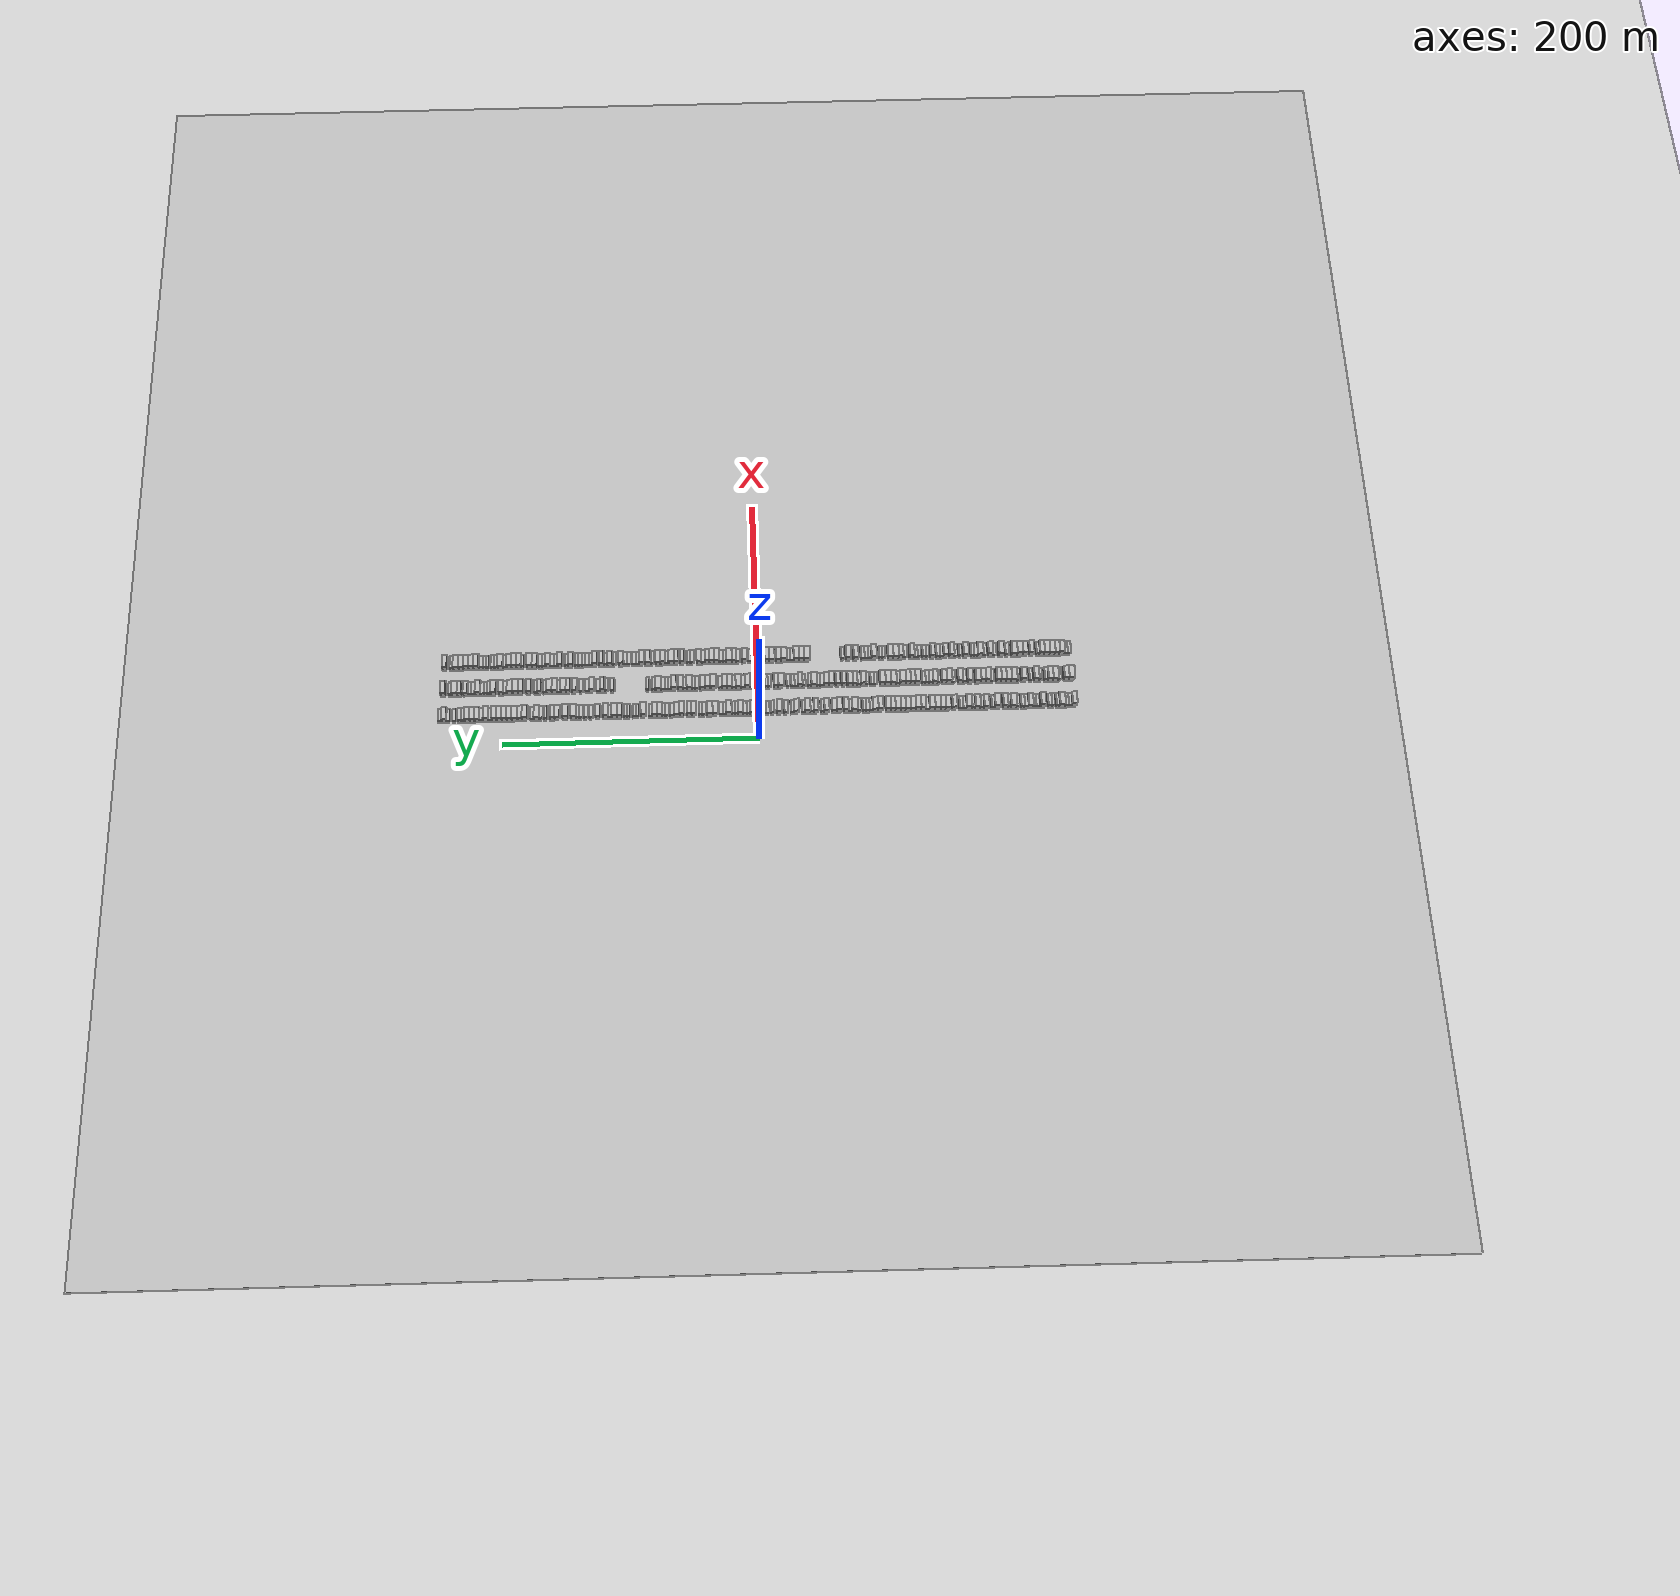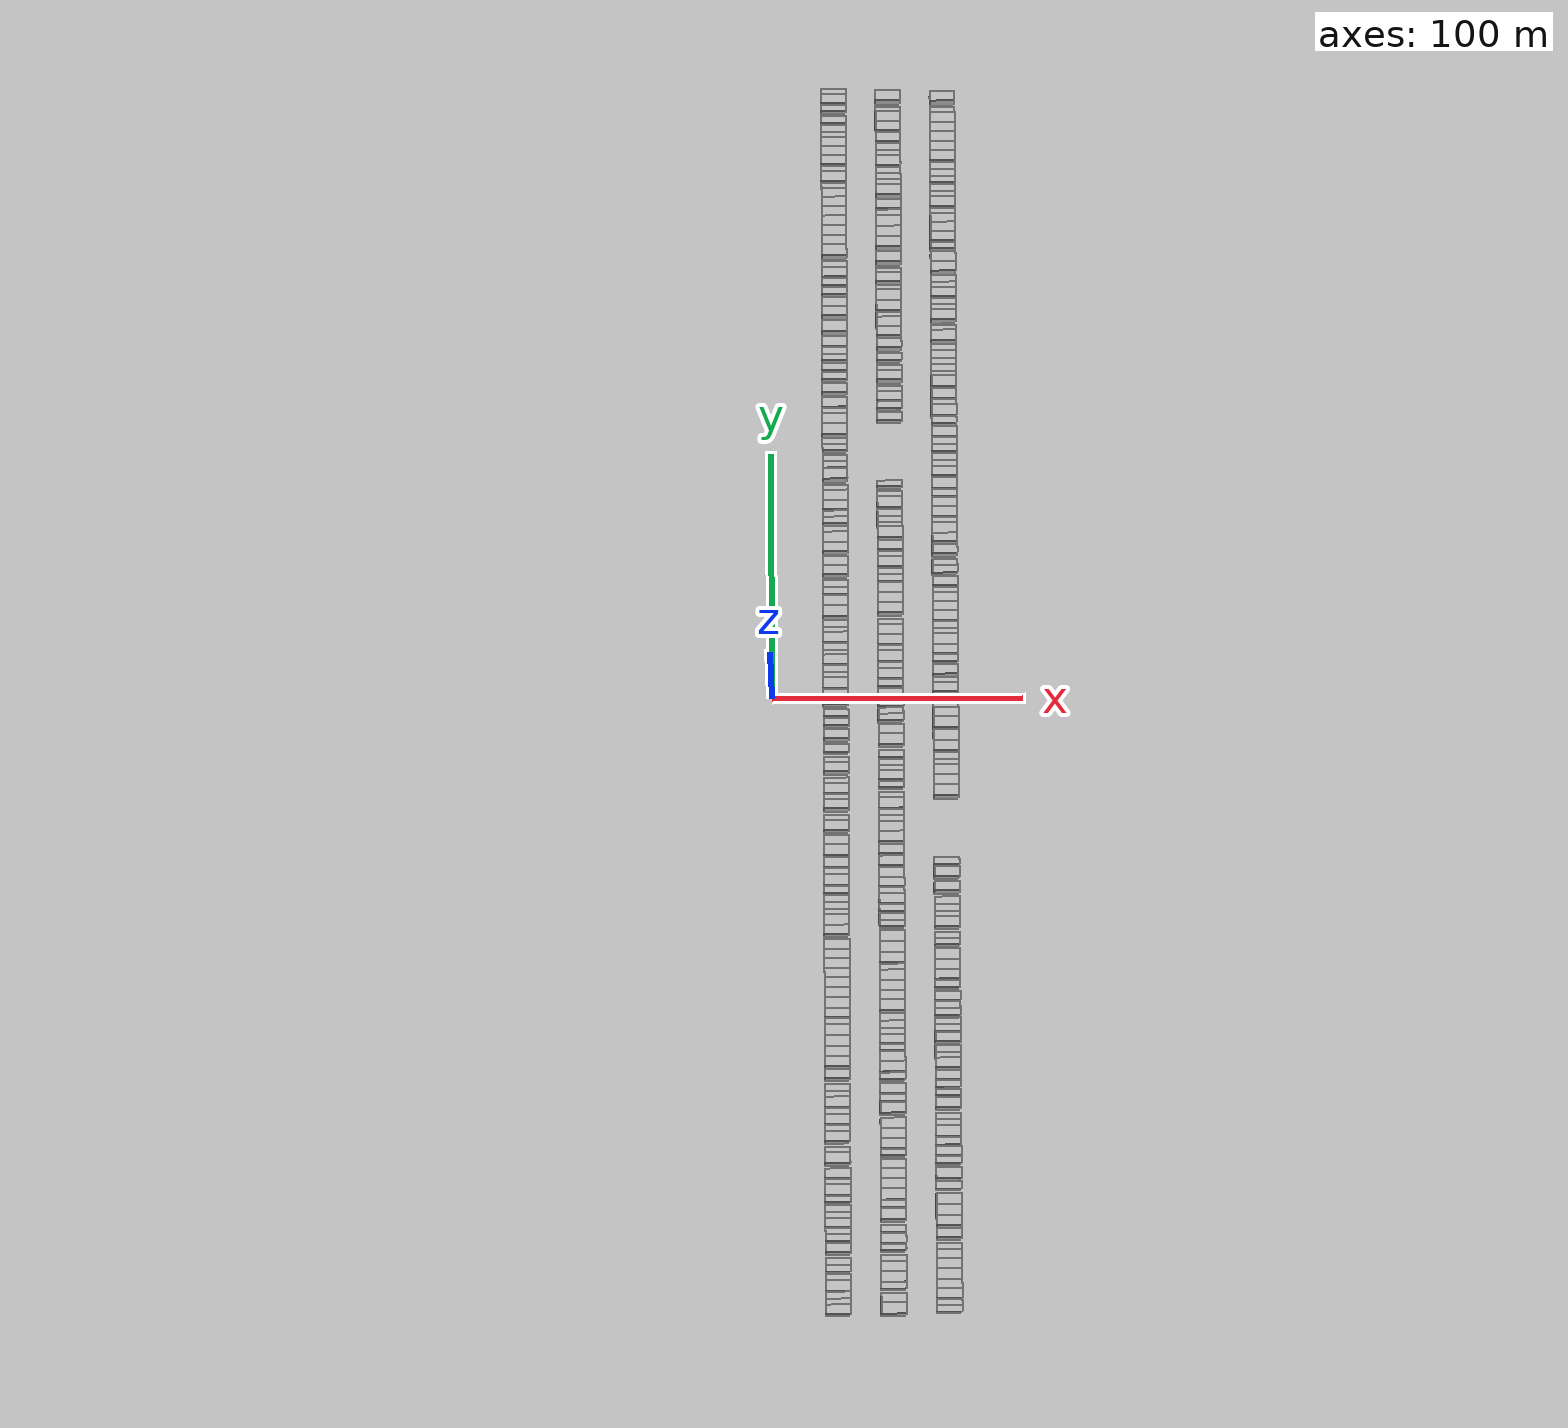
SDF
<?xml version="1.0" encoding="utf-8"?>

<sdf version="1.6">

   <world name="default">

      <gui fullscreen="0">

         <camera name="user_camera">

            <pose>-15 0 4.57585 0 0 0</pose>

            <view_controller>orbit</view_controller>

         </camera>

      </gui>

      <scene>

         <sky>

           <clouds>

             <speed>12</speed>

           </clouds>

         </sky>

         <ambient>0.4 0.4 0.4 1</ambient>

         <background>0.7 0.7 0.7 1</background>

         <shadows>1</shadows>

      </scene>

      <gravity>0 0 -9.8066</gravity>

      <magnetic_field>6e-06 2.3e-05 -4.2e-05</magnetic_field>

      <physics default="0" name="default_physics" type="ode">

         <ode>

            <solver>

               <type>quick</type>

               <iters>10</iters>

               <sor>1.0</sor>

               <use_dynamic_moi_rescaling>0</use_dynamic_moi_rescaling>

            </solver>

            <constraints>

               <cfm>0</cfm>

               <erp>0.2</erp>

               <contact_max_correcting_vel>100</contact_max_correcting_vel>

               <contact_surface_layer>0.001</contact_surface_layer>

            </constraints>

         </ode>

         <max_step_size>0.004</max_step_size>

         <real_time_factor>1</real_time_factor>

         <real_time_update_rate>250</real_time_update_rate>

      </physics>

      <light name="sun" type="directional">

         <cast_shadows>1</cast_shadows>

         <pose>0 0 10 0 0 0</pose>

         <diffuse>0.8 0.8 0.8 1</diffuse>

         <specular>0.2 0.2 0.2 1</specular>

         <attenuation>

            <range>1000</range>

            <constant>0.9</constant>

            <linear>0.01</linear>

            <quadratic>0.001</quadratic>

         </attenuation>

         <direction>-0.5 0.1 -0.9</direction>

      </light>

      <include>

         <name>ground_plane_1</name>

         <uri>model://HANNAS_ground_plane</uri>

         <pose>0 0 0  0 0 0</pose>

      </include>

      <include>

         <name>ground_plane_2</name>

         <uri>model://HANNAS_ground_plane</uri>

         <pose>100 0 0  0 0 0</pose>

      </include>

      <model name="building_1">

         <static>1</static>

         <pose frame="">25.0000 -246.1664 0 0.000000 0.000000 0.000000</pose>

         <link name="link">

            <pose frame="">0 0 4.50 0 0 0</pose>

            <collision name="collision">

               <geometry>

                  <box>

                     <size>10.0000 3.6671 9.0000</size>

                  </box>

               </geometry>

               <max_contacts>10</max_contacts>

               <surface>

                  <contact>

                     <ode/>

                  </contact>

                  <bounce/>

                  <friction>

                     <torsional>

                        <ode/>

                     </torsional>

                     <ode/>

                  </friction>

               </surface>

            </collision>

            <visual name="visual">

               <cast_shadows>0</cast_shadows>

               <geometry>

                  <box>

                     <size>10.0000 3.6671 9.0000</size>

                  </box>

               </geometry>

               <material>

                  <script>

                     <uri>model://HANNAS_wall/materials/scripts</uri>

                     <uri>model://HANNAS_wall/materials/textures</uri>

                     <name>vrc/HANNAS_wall</name>

                  </script>

               </material>

            </visual>

            <self_collide>0</self_collide>

            <enable_wind>0</enable_wind>

            <kinematic>0</kinematic>

         </link>

      </model>

      <model name="building_2">

         <static>1</static>

         <pose frame="">25.0000 -242.9882 0 0.000000 0.000000 0.000000</pose>

         <link name="link">

            <pose frame="">0 0 3.00 0 0 0</pose>

            <collision name="collision">

               <geometry>

                  <box>

                     <size>10.0000 2.6893 6.0000</size>

                  </box>

               </geometry>

               <max_contacts>10</max_contacts>

               <surface>

                  <contact>

                     <ode/>

                  </contact>

                  <bounce/>

                  <friction>

                     <torsional>

                        <ode/>

                     </torsional>

                     <ode/>

                  </friction>

               </surface>

            </collision>

            <visual name="visual">

               <cast_shadows>0</cast_shadows>

               <geometry>

                  <box>

                     <size>10.0000 2.6893 6.0000</size>

                  </box>

               </geometry>

               <material>

                  <script>

                     <uri>model://HANNAS_wall/materials/scripts</uri>

                     <uri>model://HANNAS_wall/materials/textures</uri>

                     <name>vrc/HANNAS_wall</name>

                  </script>

               </material>

            </visual>

            <self_collide>0</self_collide>

            <enable_wind>0</enable_wind>

            <kinematic>0</kinematic>

         </link>

      </model>

      <model name="building_3">

         <static>1</static>

         <pose frame="">25.0000 -240.2597 0 0.000000 0.000000 0.000000</pose>

         <link name="link">

            <pose frame="">0 0 3.00 0 0 0</pose>

            <collision name="collision">

               <geometry>

                  <box>

                     <size>10.0000 2.7678 6.0000</size>

                  </box>

               </geometry>

               <max_contacts>10</max_contacts>

               <surface>

                  <contact>

                     <ode/>

                  </contact>

                  <bounce/>

                  <friction>

                     <torsional>

                        <ode/>

                     </torsional>

                     <ode/>

                  </friction>

               </surface>

            </collision>

            <visual name="visual">

               <cast_shadows>0</cast_shadows>

               <geometry>

                  <box>

                     <size>10.0000 2.7678 6.0000</size>

                  </box>

               </geometry>

               <material>

                  <script>

                     <uri>model://HANNAS_wall/materials/scripts</uri>

                     <uri>model://HANNAS_wall/materials/textures</uri>

                     <name>vrc/HANNAS_wall</name>

                  </script>

               </material>

            </visual>

            <self_collide>0</self_collide>

            <enable_wind>0</enable_wind>

            <kinematic>0</kinematic>

         </link>

      </model>

      <model name="building_4">

         <static>1</static>

         <pose frame="">25.0000 -236.7311 0 0.000000 0.000000 0.000000</pose>

         <link name="link">

            <pose frame="">0 0 4.50 0 0 0</pose>

            <collision name="collision">

               <geometry>

                  <box>

                     <size>10.0000 4.2893 9.0000</size>

                  </box>

               </geometry>

               <max_contacts>10</max_contacts>

               <surface>

                  <contact>

                     <ode/>

                  </contact>

                  <bounce/>

                  <friction>

                     <torsional>

                        <ode/>

                     </torsional>

                     <ode/>

                  </friction>

               </surface>

            </collision>

            <visual name="visual">

               <cast_shadows>0</cast_shadows>

               <geometry>

                  <box>

                     <size>10.0000 4.2893 9.0000</size>

                  </box>

               </geometry>

               <material>

                  <script>

                     <uri>model://HANNAS_wall/materials/scripts</uri>

                     <uri>model://HANNAS_wall/materials/textures</uri>

                     <name>vrc/HANNAS_wall</name>

                  </script>

               </material>

            </visual>

            <self_collide>0</self_collide>

            <enable_wind>0</enable_wind>

            <kinematic>0</kinematic>

         </link>

      </model>

      <model name="building_5">

         <static>1</static>

         <pose frame="">25.0000 -233.3277 0 0.000000 0.000000 0.000000</pose>

         <link name="link">

            <pose frame="">0 0 3.00 0 0 0</pose>

            <collision name="collision">

               <geometry>

                  <box>

                     <size>10.0000 2.5174 6.0000</size>

                  </box>

               </geometry>

               <max_contacts>10</max_contacts>

               <surface>

                  <contact>

                     <ode/>

                  </contact>

                  <bounce/>

                  <friction>

                     <torsional>

                        <ode/>

                     </torsional>

                     <ode/>

                  </friction>

               </surface>

            </collision>

            <visual name="visual">

               <cast_shadows>0</cast_shadows>

               <geometry>

                  <box>

                     <size>10.0000 2.5174 6.0000</size>

                  </box>

               </geometry>

               <material>

                  <script>

                     <uri>model://HANNAS_wall/materials/scripts</uri>

                     <uri>model://HANNAS_wall/materials/textures</uri>

                     <name>vrc/HANNAS_wall</name>

                  </script>

               </material>

            </visual>

            <self_collide>0</self_collide>

            <enable_wind>0</enable_wind>

            <kinematic>0</kinematic>

         </link>

      </model>

      <model name="building_6">

         <static>1</static>

         <pose frame="">25.0000 -229.7580 0 0.000000 0.000000 0.000000</pose>

         <link name="link">

            <pose frame="">0 0 3.00 0 0 0</pose>

            <collision name="collision">

               <geometry>

                  <box>

                     <size>10.0000 2.6220 6.0000</size>

                  </box>

               </geometry>

               <max_contacts>10</max_contacts>

               <surface>

                  <contact>

                     <ode/>

                  </contact>

                  <bounce/>

                  <friction>

                     <torsional>

                        <ode/>

                     </torsional>

                     <ode/>

                  </friction>

               </surface>

            </collision>

            <visual name="visual">

               <cast_shadows>0</cast_shadows>

               <geometry>

                  <box>

                     <size>10.0000 2.6220 6.0000</size>

                  </box>

               </geometry>

               <material>

                  <script>

                     <uri>model://HANNAS_wall/materials/scripts</uri>

                     <uri>model://HANNAS_wall/materials/textures</uri>

                     <name>vrc/HANNAS_wall</name>

                  </script>

               </material>

            </visual>

            <self_collide>0</self_collide>

            <enable_wind>0</enable_wind>

            <kinematic>0</kinematic>

         </link>

      </model>

      <model name="building_7">

         <static>1</static>

         <pose frame="">25.0000 -227.0605 0 0.000000 0.000000 0.000000</pose>

         <link name="link">

            <pose frame="">0 0 3.00 0 0 0</pose>

            <collision name="collision">

               <geometry>

                  <box>

                     <size>10.0000 2.7730 6.0000</size>

                  </box>

               </geometry>

               <max_contacts>10</max_contacts>

               <surface>

                  <contact>

                     <ode/>

                  </contact>

                  <bounce/>

                  <friction>

                     <torsional>

                        <ode/>

                     </torsional>

                     <ode/>

                  </friction>

               </surface>

            </collision>

            <visual name="visual">

               <cast_shadows>0</cast_shadows>

               <geometry>

                  <box>

                     <size>10.0000 2.7730 6.0000</size>

                  </box>

               </geometry>

               <material>

                  <script>

                     <uri>model://HANNAS_wall/materials/scripts</uri>

                     <uri>model://HANNAS_wall/materials/textures</uri>

                     <name>vrc/HANNAS_wall</name>

                  </script>

               </material>

            </visual>

            <self_collide>0</self_collide>

            <enable_wind>0</enable_wind>

            <kinematic>0</kinematic>

         </link>

      </model>

      <model name="building_8">

         <static>1</static>

         <pose frame="">25.0000 -221.7715 0 0.000000 0.000000 0.000000</pose>

         <link name="link">

            <pose frame="">0 0 4.50 0 0 0</pose>

            <collision name="collision">

               <geometry>

                  <box>

                     <size>10.0000 3.8051 9.0000</size>

                  </box>

               </geometry>

               <max_contacts>10</max_contacts>

               <surface>

                  <contact>

                     <ode/>

                  </contact>

                  <bounce/>

                  <friction>

                     <torsional>

                        <ode/>

                     </torsional>

                     <ode/>

                  </friction>

               </surface>

            </collision>

            <visual name="visual">

               <cast_shadows>0</cast_shadows>

               <geometry>

                  <box>

                     <size>10.0000 3.8051 9.0000</size>

                  </box>

               </geometry>

               <material>

                  <script>

                     <uri>model://HANNAS_wall/materials/scripts</uri>

                     <uri>model://HANNAS_wall/materials/textures</uri>

                     <name>vrc/HANNAS_wall</name>

                  </script>

               </material>

            </visual>

            <self_collide>0</self_collide>

            <enable_wind>0</enable_wind>

            <kinematic>0</kinematic>

         </link>

      </model>

      <model name="building_9">

         <static>1</static>

         <pose frame="">25.0000 -217.5139 0 0.000000 0.000000 0.000000</pose>

         <link name="link">

            <pose frame="">0 0 3.00 0 0 0</pose>

            <collision name="collision">

               <geometry>

                  <box>

                     <size>10.0000 2.7103 6.0000</size>

                  </box>

               </geometry>

               <max_contacts>10</max_contacts>

               <surface>

                  <contact>

                     <ode/>

                  </contact>

                  <bounce/>

                  <friction>

                     <torsional>

                        <ode/>

                     </torsional>

                     <ode/>

                  </friction>

               </surface>

            </collision>

            <visual name="visual">

               <cast_shadows>0</cast_shadows>

               <geometry>

                  <box>

                     <size>10.0000 2.7103 6.0000</size>

                  </box>

               </geometry>

               <material>

                  <script>

                     <uri>model://HANNAS_wall/materials/scripts</uri>

                     <uri>model://HANNAS_wall/materials/textures</uri>

                     <name>vrc/HANNAS_wall</name>

                  </script>

               </material>

            </visual>

            <self_collide>0</self_collide>

            <enable_wind>0</enable_wind>

            <kinematic>0</kinematic>

         </link>

      </model>

      <model name="building_10">

         <static>1</static>

         <pose frame="">25.0000 -214.9467 0 0.000000 0.000000 0.000000</pose>

         <link name="link">

            <pose frame="">0 0 3.00 0 0 0</pose>

            <collision name="collision">

               <geometry>

                  <box>

                     <size>10.0000 2.4241 6.0000</size>

                  </box>

               </geometry>

               <max_contacts>10</max_contacts>

               <surface>

                  <contact>

                     <ode/>

                  </contact>

                  <bounce/>

                  <friction>

                     <torsional>

                        <ode/>

                     </torsional>

                     <ode/>

                  </friction>

               </surface>

            </collision>

            <visual name="visual">

               <cast_shadows>0</cast_shadows>

               <geometry>

                  <box>

                     <size>10.0000 2.4241 6.0000</size>

                  </box>

               </geometry>

               <material>

                  <script>

                     <uri>model://HANNAS_wall/materials/scripts</uri>

                     <uri>model://HANNAS_wall/materials/textures</uri>

                     <name>vrc/HANNAS_wall</name>

                  </script>

               </material>

            </visual>

            <self_collide>0</self_collide>

            <enable_wind>0</enable_wind>

            <kinematic>0</kinematic>

         </link>

      </model>

      <model name="building_11">

         <static>1</static>

         <pose frame="">25.0000 -211.9175 0 0.000000 0.000000 0.000000</pose>

         <link name="link">

            <pose frame="">0 0 4.50 0 0 0</pose>

            <collision name="collision">

               <geometry>

                  <box>

                     <size>10.0000 3.6342 9.0000</size>

                  </box>

               </geometry>

               <max_contacts>10</max_contacts>

               <surface>

                  <contact>

                     <ode/>

                  </contact>

                  <bounce/>

                  <friction>

                     <torsional>

                        <ode/>

                     </torsional>

                     <ode/>

                  </friction>

               </surface>

            </collision>

            <visual name="visual">

               <cast_shadows>0</cast_shadows>

               <geometry>

                  <box>

                     <size>10.0000 3.6342 9.0000</size>

                  </box>

               </geometry>

               <material>

                  <script>

                     <uri>model://HANNAS_wall/materials/scripts</uri>

                     <uri>model://HANNAS_wall/materials/textures</uri>

                     <name>vrc/HANNAS_wall</name>

                  </script>

               </material>

            </visual>

            <self_collide>0</self_collide>

            <enable_wind>0</enable_wind>

            <kinematic>0</kinematic>

         </link>

      </model>

      <model name="building_12">

         <static>1</static>

         <pose frame="">25.0000 -208.6762 0 0.000000 0.000000 0.000000</pose>

         <link name="link">

            <pose frame="">0 0 3.00 0 0 0</pose>

            <collision name="collision">

               <geometry>

                  <box>

                     <size>10.0000 2.8484 6.0000</size>

                  </box>

               </geometry>

               <max_contacts>10</max_contacts>

               <surface>

                  <contact>

                     <ode/>

                  </contact>

                  <bounce/>

                  <friction>

                     <torsional>

                        <ode/>

                     </torsional>

                     <ode/>

                  </friction>

               </surface>

            </collision>

            <visual name="visual">

               <cast_shadows>0</cast_shadows>

               <geometry>

                  <box>

                     <size>10.0000 2.8484 6.0000</size>

                  </box>

               </geometry>

               <material>

                  <script>

                     <uri>model://HANNAS_wall/materials/scripts</uri>

                     <uri>model://HANNAS_wall/materials/textures</uri>

                     <name>vrc/HANNAS_wall</name>

                  </script>

               </material>

            </visual>

            <self_collide>0</self_collide>

            <enable_wind>0</enable_wind>

            <kinematic>0</kinematic>

         </link>

      </model>

      <model name="building_13">

         <static>1</static>

         <pose frame="">25.0000 -205.8485 0 0.000000 0.000000 0.000000</pose>

         <link name="link">

            <pose frame="">0 0 3.00 0 0 0</pose>

            <collision name="collision">

               <geometry>

                  <box>

                     <size>10.0000 2.8069 6.0000</size>

                  </box>

               </geometry>

               <max_contacts>10</max_contacts>

               <surface>

                  <contact>

                     <ode/>

                  </contact>

                  <bounce/>

                  <friction>

                     <torsional>

                        <ode/>

                     </torsional>

                     <ode/>

                  </friction>

               </surface>

            </collision>

            <visual name="visual">

               <cast_shadows>0</cast_shadows>

               <geometry>

                  <box>

                     <size>10.0000 2.8069 6.0000</size>

                  </box>

               </geometry>

               <material>

                  <script>

                     <uri>model://HANNAS_wall/materials/scripts</uri>

                     <uri>model://HANNAS_wall/materials/textures</uri>

                     <name>vrc/HANNAS_wall</name>

                  </script>

               </material>

            </visual>

            <self_collide>0</self_collide>

            <enable_wind>0</enable_wind>

            <kinematic>0</kinematic>

         </link>

      </model>

      <model name="building_14">

         <static>1</static>

         <pose frame="">25.0000 -202.1674 0 0.000000 0.000000 0.000000</pose>

         <link name="link">

            <pose frame="">0 0 3.00 0 0 0</pose>

            <collision name="collision">

               <geometry>

                  <box>

                     <size>10.0000 2.5554 6.0000</size>

                  </box>

               </geometry>

               <max_contacts>10</max_contacts>

               <surface>

                  <contact>

                     <ode/>

                  </contact>

                  <bounce/>

                  <friction>

                     <torsional>

                        <ode/>

                     </torsional>

                     <ode/>

                  </friction>

               </surface>

            </collision>

            <visual name="visual">

               <cast_shadows>0</cast_shadows>

               <geometry>

                  <box>

                     <size>10.0000 2.5554 6.0000</size>

                  </box>

               </geometry>

               <material>

                  <script>

                     <uri>model://HANNAS_wall/materials/scripts</uri>

                     <uri>model://HANNAS_wall/materials/textures</uri>

                     <name>vrc/HANNAS_wall</name>

                  </script>

               </material>

            </visual>

            <self_collide>0</self_collide>

            <enable_wind>0</enable_wind>

            <kinematic>0</kinematic>

         </link>

      </model>

      <model name="building_15">

         <static>1</static>

         <pose frame="">25.0000 -198.6950 0 0.000000 0.000000 0.000000</pose>

         <link name="link">

            <pose frame="">0 0 4.50 0 0 0</pose>

            <collision name="collision">

               <geometry>

                  <box>

                     <size>10.0000 4.3893 9.0000</size>

                  </box>

               </geometry>

               <max_contacts>10</max_contacts>

               <surface>

                  <contact>

                     <ode/>

                  </contact>

                  <bounce/>

                  <friction>

                     <torsional>

                        <ode/>

                     </torsional>

                     <ode/>

                  </friction>

               </surface>

            </collision>

            <visual name="visual">

               <cast_shadows>0</cast_shadows>

               <geometry>

                  <box>

                     <size>10.0000 4.3893 9.0000</size>

                  </box>

               </geometry>

               <material>

                  <script>

                     <uri>model://HANNAS_wall/materials/scripts</uri>

                     <uri>model://HANNAS_wall/materials/textures</uri>

                     <name>vrc/HANNAS_wall</name>

                  </script>

               </material>

            </visual>

            <self_collide>0</self_collide>

            <enable_wind>0</enable_wind>

            <kinematic>0</kinematic>

         </link>

      </model>

      <model name="building_16">

         <static>1</static>

         <pose frame="">25.0000 -195.2446 0 0.000000 0.000000 0.000000</pose>

         <link name="link">

            <pose frame="">0 0 3.00 0 0 0</pose>

            <collision name="collision">

               <geometry>

                  <box>

                     <size>10.0000 2.5115 6.0000</size>

                  </box>

               </geometry>

               <max_contacts>10</max_contacts>

               <surface>

                  <contact>

                     <ode/>

                  </contact>

                  <bounce/>

                  <friction>

                     <torsional>

                        <ode/>

                     </torsional>

                     <ode/>

                  </friction>

               </surface>

            </collision>

            <visual name="visual">

               <cast_shadows>0</cast_shadows>

               <geometry>

                  <box>

                     <size>10.0000 2.5115 6.0000</size>

                  </box>

               </geometry>

               <material>

                  <script>

                     <uri>model://HANNAS_wall/materials/scripts</uri>

                     <uri>model://HANNAS_wall/materials/textures</uri>

                     <name>vrc/HANNAS_wall</name>

                  </script>

               </material>

            </visual>

            <self_collide>0</self_collide>

            <enable_wind>0</enable_wind>

            <kinematic>0</kinematic>

         </link>

      </model>

      <model name="building_17">

         <static>1</static>

         <pose frame="">25.0000 -192.1636 0 0.000000 0.000000 0.000000</pose>

         <link name="link">

            <pose frame="">0 0 4.50 0 0 0</pose>

            <collision name="collision">

               <geometry>

                  <box>

                     <size>10.0000 3.6505 9.0000</size>

                  </box>

               </geometry>

               <max_contacts>10</max_contacts>

               <surface>

                  <contact>

                     <ode/>

                  </contact>

                  <bounce/>

                  <friction>

                     <torsional>

                        <ode/>

                     </torsional>

                     <ode/>

                  </friction>

               </surface>

            </collision>

            <visual name="visual">

               <cast_shadows>0</cast_shadows>

               <geometry>

                  <box>

                     <size>10.0000 3.6505 9.0000</size>

                  </box>

               </geometry>

               <material>

                  <script>

                     <uri>model://HANNAS_wall/materials/scripts</uri>

                     <uri>model://HANNAS_wall/materials/textures</uri>

                     <name>vrc/HANNAS_wall</name>

                  </script>

               </material>

            </visual>

            <self_collide>0</self_collide>

            <enable_wind>0</enable_wind>

            <kinematic>0</kinematic>

         </link>

      </model>

      <model name="building_18">

         <static>1</static>

         <pose frame="">25.0000 -186.1081 0 0.000000 0.000000 0.000000</pose>

         <link name="link">

            <pose frame="">0 0 4.50 0 0 0</pose>

            <collision name="collision">

               <geometry>

                  <box>

                     <size>10.0000 4.4604 9.0000</size>

                  </box>

               </geometry>

               <max_contacts>10</max_contacts>

               <surface>

                  <contact>

                     <ode/>

                  </contact>

                  <bounce/>

                  <friction>

                     <torsional>

                        <ode/>

                     </torsional>

                     <ode/>

                  </friction>

               </surface>

            </collision>

            <visual name="visual">

               <cast_shadows>0</cast_shadows>

               <geometry>

                  <box>

                     <size>10.0000 4.4604 9.0000</size>

                  </box>

               </geometry>

               <material>

                  <script>

                     <uri>model://HANNAS_wall/materials/scripts</uri>

                     <uri>model://HANNAS_wall/materials/textures</uri>

                     <name>vrc/HANNAS_wall</name>

                  </script>

               </material>

            </visual>

            <self_collide>0</self_collide>

            <enable_wind>0</enable_wind>

            <kinematic>0</kinematic>

         </link>

      </model>

      <model name="building_19">

         <static>1</static>

         <pose frame="">25.0000 -182.5922 0 0.000000 0.000000 0.000000</pose>

         <link name="link">

            <pose frame="">0 0 3.00 0 0 0</pose>

            <collision name="collision">

               <geometry>

                  <box>

                     <size>10.0000 2.5716 6.0000</size>

                  </box>

               </geometry>

               <max_contacts>10</max_contacts>

               <surface>

                  <contact>

                     <ode/>

                  </contact>

                  <bounce/>

                  <friction>

                     <torsional>

                        <ode/>

                     </torsional>

                     <ode/>

                  </friction>

               </surface>

            </collision>

            <visual name="visual">

               <cast_shadows>0</cast_shadows>

               <geometry>

                  <box>

                     <size>10.0000 2.5716 6.0000</size>

                  </box>

               </geometry>

               <material>

                  <script>

                     <uri>model://HANNAS_wall/materials/scripts</uri>

                     <uri>model://HANNAS_wall/materials/textures</uri>

                     <name>vrc/HANNAS_wall</name>

                  </script>

               </material>

            </visual>

            <self_collide>0</self_collide>

            <enable_wind>0</enable_wind>

            <kinematic>0</kinematic>

         </link>

      </model>

      <model name="building_20">

         <static>1</static>

         <pose frame="">25.0000 -177.3337 0 0.000000 0.000000 0.000000</pose>

         <link name="link">

            <pose frame="">0 0 4.50 0 0 0</pose>

            <collision name="collision">

               <geometry>

                  <box>

                     <size>10.0000 3.9453 9.0000</size>

                  </box>

               </geometry>

               <max_contacts>10</max_contacts>

               <surface>

                  <contact>

                     <ode/>

                  </contact>

                  <bounce/>

                  <friction>

                     <torsional>

                        <ode/>

                     </torsional>

                     <ode/>

                  </friction>

               </surface>

            </collision>

            <visual name="visual">

               <cast_shadows>0</cast_shadows>

               <geometry>

                  <box>

                     <size>10.0000 3.9453 9.0000</size>

                  </box>

               </geometry>

               <material>

                  <script>

                     <uri>model://HANNAS_wall/materials/scripts</uri>

                     <uri>model://HANNAS_wall/materials/textures</uri>

                     <name>vrc/HANNAS_wall</name>

                  </script>

               </material>

            </visual>

            <self_collide>0</self_collide>

            <enable_wind>0</enable_wind>

            <kinematic>0</kinematic>

         </link>

      </model>

      <model name="building_21">

         <static>1</static>

         <pose frame="">25.0000 -173.9365 0 0.000000 0.000000 0.000000</pose>

         <link name="link">

            <pose frame="">0 0 3.00 0 0 0</pose>

            <collision name="collision">

               <geometry>

                  <box>

                     <size>10.0000 2.8492 6.0000</size>

                  </box>

               </geometry>

               <max_contacts>10</max_contacts>

               <surface>

                  <contact>

                     <ode/>

                  </contact>

                  <bounce/>

                  <friction>

                     <torsional>

                        <ode/>

                     </torsional>

                     <ode/>

                  </friction>

               </surface>

            </collision>

            <visual name="visual">

               <cast_shadows>0</cast_shadows>

               <geometry>

                  <box>

                     <size>10.0000 2.8492 6.0000</size>

                  </box>

               </geometry>

               <material>

                  <script>

                     <uri>model://HANNAS_wall/materials/scripts</uri>

                     <uri>model://HANNAS_wall/materials/textures</uri>

                     <name>vrc/HANNAS_wall</name>

                  </script>

               </material>

            </visual>

            <self_collide>0</self_collide>

            <enable_wind>0</enable_wind>

            <kinematic>0</kinematic>

         </link>

      </model>

      <model name="building_22">

         <static>1</static>

         <pose frame="">25.0000 -170.5430 0 0.000000 0.000000 0.000000</pose>

         <link name="link">

            <pose frame="">0 0 4.50 0 0 0</pose>

            <collision name="collision">

               <geometry>

                  <box>

                     <size>10.0000 3.9377 9.0000</size>

                  </box>

               </geometry>

               <max_contacts>10</max_contacts>

               <surface>

                  <contact>

                     <ode/>

                  </contact>

                  <bounce/>

                  <friction>

                     <torsional>

                        <ode/>

                     </torsional>

                     <ode/>

                  </friction>

               </surface>

            </collision>

            <visual name="visual">

               <cast_shadows>0</cast_shadows>

               <geometry>

                  <box>

                     <size>10.0000 3.9377 9.0000</size>

                  </box>

               </geometry>

               <material>

                  <script>

                     <uri>model://HANNAS_wall/materials/scripts</uri>

                     <uri>model://HANNAS_wall/materials/textures</uri>

                     <name>vrc/HANNAS_wall</name>

                  </script>

               </material>

            </visual>

            <self_collide>0</self_collide>

            <enable_wind>0</enable_wind>

            <kinematic>0</kinematic>

         </link>

      </model>

      <model name="building_23">

         <static>1</static>

         <pose frame="">25.0000 -167.2108 0 0.000000 0.000000 0.000000</pose>

         <link name="link">

            <pose frame="">0 0 3.00 0 0 0</pose>

            <collision name="collision">

               <geometry>

                  <box>

                     <size>10.0000 2.7267 6.0000</size>

                  </box>

               </geometry>

               <max_contacts>10</max_contacts>

               <surface>

                  <contact>

                     <ode/>

                  </contact>

                  <bounce/>

                  <friction>

                     <torsional>

                        <ode/>

                     </torsional>

                     <ode/>

                  </friction>

               </surface>

            </collision>

            <visual name="visual">

               <cast_shadows>0</cast_shadows>

               <geometry>

                  <box>

                     <size>10.0000 2.7267 6.0000</size>

                  </box>

               </geometry>

               <material>

                  <script>

                     <uri>model://HANNAS_wall/materials/scripts</uri>

                     <uri>model://HANNAS_wall/materials/textures</uri>

                     <name>vrc/HANNAS_wall</name>

                  </script>

               </material>

            </visual>

            <self_collide>0</self_collide>

            <enable_wind>0</enable_wind>

            <kinematic>0</kinematic>

         </link>

      </model>

      <model name="building_24">

         <static>1</static>

         <pose frame="">25.0000 -163.7393 0 0.000000 0.000000 0.000000</pose>

         <link name="link">

            <pose frame="">0 0 4.50 0 0 0</pose>

            <collision name="collision">

               <geometry>

                  <box>

                     <size>10.0000 4.2165 9.0000</size>

                  </box>

               </geometry>

               <max_contacts>10</max_contacts>

               <surface>

                  <contact>

                     <ode/>

                  </contact>

                  <bounce/>

                  <friction>

                     <torsional>

                        <ode/>

                     </torsional>

                     <ode/>

                  </friction>

               </surface>

            </collision>

            <visual name="visual">

               <cast_shadows>0</cast_shadows>

               <geometry>

                  <box>

                     <size>10.0000 4.2165 9.0000</size>

                  </box>

               </geometry>

               <material>

                  <script>

                     <uri>model://HANNAS_wall/materials/scripts</uri>

                     <uri>model://HANNAS_wall/materials/textures</uri>

                     <name>vrc/HANNAS_wall</name>

                  </script>

               </material>

            </visual>

            <self_collide>0</self_collide>

            <enable_wind>0</enable_wind>

            <kinematic>0</kinematic>

         </link>

      </model>

      <model name="building_25">

         <static>1</static>

         <pose frame="">25.0000 -160.3569 0 0.000000 0.000000 0.000000</pose>

         <link name="link">

            <pose frame="">0 0 3.00 0 0 0</pose>

            <collision name="collision">

               <geometry>

                  <box>

                     <size>10.0000 2.5483 6.0000</size>

                  </box>

               </geometry>

               <max_contacts>10</max_contacts>

               <surface>

                  <contact>

                     <ode/>

                  </contact>

                  <bounce/>

                  <friction>

                     <torsional>

                        <ode/>

                     </torsional>

                     <ode/>

                  </friction>

               </surface>

            </collision>

            <visual name="visual">

               <cast_shadows>0</cast_shadows>

               <geometry>

                  <box>

                     <size>10.0000 2.5483 6.0000</size>

                  </box>

               </geometry>

               <material>

                  <script>

                     <uri>model://HANNAS_wall/materials/scripts</uri>

                     <uri>model://HANNAS_wall/materials/textures</uri>

                     <name>vrc/HANNAS_wall</name>

                  </script>

               </material>

            </visual>

            <self_collide>0</self_collide>

            <enable_wind>0</enable_wind>

            <kinematic>0</kinematic>

         </link>

      </model>

      <model name="building_26">

         <static>1</static>

         <pose frame="">25.0000 -157.6715 0 0.000000 0.000000 0.000000</pose>

         <link name="link">

            <pose frame="">0 0 3.00 0 0 0</pose>

            <collision name="collision">

               <geometry>

                  <box>

                     <size>10.0000 2.8223 6.0000</size>

                  </box>

               </geometry>

               <max_contacts>10</max_contacts>

               <surface>

                  <contact>

                     <ode/>

                  </contact>

                  <bounce/>

                  <friction>

                     <torsional>

                        <ode/>

                     </torsional>

                     <ode/>

                  </friction>

               </surface>

            </collision>

            <visual name="visual">

               <cast_shadows>0</cast_shadows>

               <geometry>

                  <box>

                     <size>10.0000 2.8223 6.0000</size>

                  </box>

               </geometry>

               <material>

                  <script>

                     <uri>model://HANNAS_wall/materials/scripts</uri>

                     <uri>model://HANNAS_wall/materials/textures</uri>

                     <name>vrc/HANNAS_wall</name>

                  </script>

               </material>

            </visual>

            <self_collide>0</self_collide>

            <enable_wind>0</enable_wind>

            <kinematic>0</kinematic>

         </link>

      </model>

      <model name="building_27">

         <static>1</static>

         <pose frame="">25.0000 -152.4122 0 0.000000 0.000000 0.000000</pose>

         <link name="link">

            <pose frame="">0 0 4.50 0 0 0</pose>

            <collision name="collision">

               <geometry>

                  <box>

                     <size>10.0000 3.6963 9.0000</size>

                  </box>

               </geometry>

               <max_contacts>10</max_contacts>

               <surface>

                  <contact>

                     <ode/>

                  </contact>

                  <bounce/>

                  <friction>

                     <torsional>

                        <ode/>

                     </torsional>

                     <ode/>

                  </friction>

               </surface>

            </collision>

            <visual name="visual">

               <cast_shadows>0</cast_shadows>

               <geometry>

                  <box>

                     <size>10.0000 3.6963 9.0000</size>

                  </box>

               </geometry>

               <material>

                  <script>

                     <uri>model://HANNAS_wall/materials/scripts</uri>

                     <uri>model://HANNAS_wall/materials/textures</uri>

                     <name>vrc/HANNAS_wall</name>

                  </script>

               </material>

            </visual>

            <self_collide>0</self_collide>

            <enable_wind>0</enable_wind>

            <kinematic>0</kinematic>

         </link>

      </model>

      <model name="building_28">

         <static>1</static>

         <pose frame="">25.0000 -147.4266 0 0.000000 0.000000 0.000000</pose>

         <link name="link">

            <pose frame="">0 0 4.50 0 0 0</pose>

            <collision name="collision">

               <geometry>

                  <box>

                     <size>10.0000 4.2749 9.0000</size>

                  </box>

               </geometry>

               <max_contacts>10</max_contacts>

               <surface>

                  <contact>

                     <ode/>

                  </contact>

                  <bounce/>

                  <friction>

                     <torsional>

                        <ode/>

                     </torsional>

                     <ode/>

                  </friction>

               </surface>

            </collision>

            <visual name="visual">

               <cast_shadows>0</cast_shadows>

               <geometry>

                  <box>

                     <size>10.0000 4.2749 9.0000</size>

                  </box>

               </geometry>

               <material>

                  <script>

                     <uri>model://HANNAS_wall/materials/scripts</uri>

                     <uri>model://HANNAS_wall/materials/textures</uri>

                     <name>vrc/HANNAS_wall</name>

                  </script>

               </material>

            </visual>

            <self_collide>0</self_collide>

            <enable_wind>0</enable_wind>

            <kinematic>0</kinematic>

         </link>

      </model>

      <model name="building_29">

         <static>1</static>

         <pose frame="">25.0000 -143.3866 0 0.000000 0.000000 0.000000</pose>

         <link name="link">

            <pose frame="">0 0 4.50 0 0 0</pose>

            <collision name="collision">

               <geometry>

                  <box>

                     <size>10.0000 3.8051 9.0000</size>

                  </box>

               </geometry>

               <max_contacts>10</max_contacts>

               <surface>

                  <contact>

                     <ode/>

                  </contact>

                  <bounce/>

                  <friction>

                     <torsional>

                        <ode/>

                     </torsional>

                     <ode/>

                  </friction>

               </surface>

            </collision>

            <visual name="visual">

               <cast_shadows>0</cast_shadows>

               <geometry>

                  <box>

                     <size>10.0000 3.8051 9.0000</size>

                  </box>

               </geometry>

               <material>

                  <script>

                     <uri>model://HANNAS_wall/materials/scripts</uri>

                     <uri>model://HANNAS_wall/materials/textures</uri>

                     <name>vrc/HANNAS_wall</name>

                  </script>

               </material>

            </visual>

            <self_collide>0</self_collide>

            <enable_wind>0</enable_wind>

            <kinematic>0</kinematic>

         </link>

      </model>

      <model name="building_30">

         <static>1</static>

         <pose frame="">25.0000 -139.3176 0 0.000000 0.000000 0.000000</pose>

         <link name="link">

            <pose frame="">0 0 4.50 0 0 0</pose>

            <collision name="collision">

               <geometry>

                  <box>

                     <size>10.0000 4.3330 9.0000</size>

                  </box>

               </geometry>

               <max_contacts>10</max_contacts>

               <surface>

                  <contact>

                     <ode/>

                  </contact>

                  <bounce/>

                  <friction>

                     <torsional>

                        <ode/>

                     </torsional>

                     <ode/>

                  </friction>

               </surface>

            </collision>

            <visual name="visual">

               <cast_shadows>0</cast_shadows>

               <geometry>

                  <box>

                     <size>10.0000 4.3330 9.0000</size>

                  </box>

               </geometry>

               <material>

                  <script>

                     <uri>model://HANNAS_wall/materials/scripts</uri>

                     <uri>model://HANNAS_wall/materials/textures</uri>

                     <name>vrc/HANNAS_wall</name>

                  </script>

               </material>

            </visual>

            <self_collide>0</self_collide>

            <enable_wind>0</enable_wind>

            <kinematic>0</kinematic>

         </link>

      </model>

      <model name="building_31">

         <static>1</static>

         <pose frame="">25.0000 -134.9347 0 0.000000 0.000000 0.000000</pose>

         <link name="link">

            <pose frame="">0 0 4.50 0 0 0</pose>

            <collision name="collision">

               <geometry>

                  <box>

                     <size>10.0000 4.4328 9.0000</size>

                  </box>

               </geometry>

               <max_contacts>10</max_contacts>

               <surface>

                  <contact>

                     <ode/>

                  </contact>

                  <bounce/>

                  <friction>

                     <torsional>

                        <ode/>

                     </torsional>

                     <ode/>

                  </friction>

               </surface>

            </collision>

            <visual name="visual">

               <cast_shadows>0</cast_shadows>

               <geometry>

                  <box>

                     <size>10.0000 4.4328 9.0000</size>

                  </box>

               </geometry>

               <material>

                  <script>

                     <uri>model://HANNAS_wall/materials/scripts</uri>

                     <uri>model://HANNAS_wall/materials/textures</uri>

                     <name>vrc/HANNAS_wall</name>

                  </script>

               </material>

            </visual>

            <self_collide>0</self_collide>

            <enable_wind>0</enable_wind>

            <kinematic>0</kinematic>

         </link>

      </model>

      <model name="building_32">

         <static>1</static>

         <pose frame="">25.0000 -131.2357 0 0.000000 0.000000 0.000000</pose>

         <link name="link">

            <pose frame="">0 0 3.00 0 0 0</pose>

            <collision name="collision">

               <geometry>

                  <box>

                     <size>10.0000 2.9652 6.0000</size>

                  </box>

               </geometry>

               <max_contacts>10</max_contacts>

               <surface>

                  <contact>

                     <ode/>

                  </contact>

                  <bounce/>

                  <friction>

                     <torsional>

                        <ode/>

                     </torsional>

                     <ode/>

                  </friction>

               </surface>

            </collision>

            <visual name="visual">

               <cast_shadows>0</cast_shadows>

               <geometry>

                  <box>

                     <size>10.0000 2.9652 6.0000</size>

                  </box>

               </geometry>

               <material>

                  <script>

                     <uri>model://HANNAS_wall/materials/scripts</uri>

                     <uri>model://HANNAS_wall/materials/textures</uri>

                     <name>vrc/HANNAS_wall</name>

                  </script>

               </material>

            </visual>

            <self_collide>0</self_collide>

            <enable_wind>0</enable_wind>

            <kinematic>0</kinematic>

         </link>

      </model>

      <model name="building_33">

         <static>1</static>

         <pose frame="">25.0000 -127.9492 0 0.000000 0.000000 0.000000</pose>

         <link name="link">

            <pose frame="">0 0 4.50 0 0 0</pose>

            <collision name="collision">

               <geometry>

                  <box>

                     <size>10.0000 3.6078 9.0000</size>

                  </box>

               </geometry>

               <max_contacts>10</max_contacts>

               <surface>

                  <contact>

                     <ode/>

                  </contact>

                  <bounce/>

                  <friction>

                     <torsional>

                        <ode/>

                     </torsional>

                     <ode/>

                  </friction>

               </surface>

            </collision>

            <visual name="visual">

               <cast_shadows>0</cast_shadows>

               <geometry>

                  <box>

                     <size>10.0000 3.6078 9.0000</size>

                  </box>

               </geometry>

               <material>

                  <script>

                     <uri>model://HANNAS_wall/materials/scripts</uri>

                     <uri>model://HANNAS_wall/materials/textures</uri>

                     <name>vrc/HANNAS_wall</name>

                  </script>

               </material>

            </visual>

            <self_collide>0</self_collide>

            <enable_wind>0</enable_wind>

            <kinematic>0</kinematic>

         </link>

      </model>

      <model name="building_34">

         <static>1</static>

         <pose frame="">25.0000 -124.0263 0 0.000000 0.000000 0.000000</pose>

         <link name="link">

            <pose frame="">0 0 4.50 0 0 0</pose>

            <collision name="collision">

               <geometry>

                  <box>

                     <size>10.0000 4.2380 9.0000</size>

                  </box>

               </geometry>

               <max_contacts>10</max_contacts>

               <surface>

                  <contact>

                     <ode/>

                  </contact>

                  <bounce/>

                  <friction>

                     <torsional>

                        <ode/>

                     </torsional>

                     <ode/>

                  </friction>

               </surface>

            </collision>

            <visual name="visual">

               <cast_shadows>0</cast_shadows>

               <geometry>

                  <box>

                     <size>10.0000 4.2380 9.0000</size>

                  </box>

               </geometry>

               <material>

                  <script>

                     <uri>model://HANNAS_wall/materials/scripts</uri>

                     <uri>model://HANNAS_wall/materials/textures</uri>

                     <name>vrc/HANNAS_wall</name>

                  </script>

               </material>

            </visual>

            <self_collide>0</self_collide>

            <enable_wind>0</enable_wind>

            <kinematic>0</kinematic>

         </link>

      </model>

      <model name="building_35">

         <static>1</static>

         <pose frame="">25.0000 -119.8935 0 0.000000 0.000000 0.000000</pose>

         <link name="link">

            <pose frame="">0 0 4.50 0 0 0</pose>

            <collision name="collision">

               <geometry>

                  <box>

                     <size>10.0000 4.0276 9.0000</size>

                  </box>

               </geometry>

               <max_contacts>10</max_contacts>

               <surface>

                  <contact>

                     <ode/>

                  </contact>

                  <bounce/>

                  <friction>

                     <torsional>

                        <ode/>

                     </torsional>

                     <ode/>

                  </friction>

               </surface>

            </collision>

            <visual name="visual">

               <cast_shadows>0</cast_shadows>

               <geometry>

                  <box>

                     <size>10.0000 4.0276 9.0000</size>

                  </box>

               </geometry>

               <material>

                  <script>

                     <uri>model://HANNAS_wall/materials/scripts</uri>

                     <uri>model://HANNAS_wall/materials/textures</uri>

                     <name>vrc/HANNAS_wall</name>

                  </script>

               </material>

            </visual>

            <self_collide>0</self_collide>

            <enable_wind>0</enable_wind>

            <kinematic>0</kinematic>

         </link>

      </model>

      <model name="building_36">

         <static>1</static>

         <pose frame="">25.0000 -115.9105 0 0.000000 0.000000 0.000000</pose>

         <link name="link">

            <pose frame="">0 0 4.50 0 0 0</pose>

            <collision name="collision">

               <geometry>

                  <box>

                     <size>10.0000 3.9385 9.0000</size>

                  </box>

               </geometry>

               <max_contacts>10</max_contacts>

               <surface>

                  <contact>

                     <ode/>

                  </contact>

                  <bounce/>

                  <friction>

                     <torsional>

                        <ode/>

                     </torsional>

                     <ode/>

                  </friction>

               </surface>

            </collision>

            <visual name="visual">

               <cast_shadows>0</cast_shadows>

               <geometry>

                  <box>

                     <size>10.0000 3.9385 9.0000</size>

                  </box>

               </geometry>

               <material>

                  <script>

                     <uri>model://HANNAS_wall/materials/scripts</uri>

                     <uri>model://HANNAS_wall/materials/textures</uri>

                     <name>vrc/HANNAS_wall</name>

                  </script>

               </material>

            </visual>

            <self_collide>0</self_collide>

            <enable_wind>0</enable_wind>

            <kinematic>0</kinematic>

         </link>

      </model>

      <model name="building_37">

         <static>1</static>

         <pose frame="">25.0000 -112.0548 0 0.000000 0.000000 0.000000</pose>

         <link name="link">

            <pose frame="">0 0 4.50 0 0 0</pose>

            <collision name="collision">

               <geometry>

                  <box>

                     <size>10.0000 3.7729 9.0000</size>

                  </box>

               </geometry>

               <max_contacts>10</max_contacts>

               <surface>

                  <contact>

                     <ode/>

                  </contact>

                  <bounce/>

                  <friction>

                     <torsional>

                        <ode/>

                     </torsional>

                     <ode/>

                  </friction>

               </surface>

            </collision>

            <visual name="visual">

               <cast_shadows>0</cast_shadows>

               <geometry>

                  <box>

                     <size>10.0000 3.7729 9.0000</size>

                  </box>

               </geometry>

               <material>

                  <script>

                     <uri>model://HANNAS_wall/materials/scripts</uri>

                     <uri>model://HANNAS_wall/materials/textures</uri>

                     <name>vrc/HANNAS_wall</name>

                  </script>

               </material>

            </visual>

            <self_collide>0</self_collide>

            <enable_wind>0</enable_wind>

            <kinematic>0</kinematic>

         </link>

      </model>

      <model name="building_38">

         <static>1</static>

         <pose frame="">25.0000 -108.1041 0 0.000000 0.000000 0.000000</pose>

         <link name="link">

            <pose frame="">0 0 4.50 0 0 0</pose>

            <collision name="collision">

               <geometry>

                  <box>

                     <size>10.0000 4.1284 9.0000</size>

                  </box>

               </geometry>

               <max_contacts>10</max_contacts>

               <surface>

                  <contact>

                     <ode/>

                  </contact>

                  <bounce/>

                  <friction>

                     <torsional>

                        <ode/>

                     </torsional>

                     <ode/>

                  </friction>

               </surface>

            </collision>

            <visual name="visual">

               <cast_shadows>0</cast_shadows>

               <geometry>

                  <box>

                     <size>10.0000 4.1284 9.0000</size>

                  </box>

               </geometry>

               <material>

                  <script>

                     <uri>model://HANNAS_wall/materials/scripts</uri>

                     <uri>model://HANNAS_wall/materials/textures</uri>

                     <name>vrc/HANNAS_wall</name>

                  </script>

               </material>

            </visual>

            <self_collide>0</self_collide>

            <enable_wind>0</enable_wind>

            <kinematic>0</kinematic>

         </link>

      </model>

      <model name="building_39">

         <static>1</static>

         <pose frame="">25.0000 -104.2180 0 0.000000 0.000000 0.000000</pose>

         <link name="link">

            <pose frame="">0 0 4.50 0 0 0</pose>

            <collision name="collision">

               <geometry>

                  <box>

                     <size>10.0000 3.6439 9.0000</size>

                  </box>

               </geometry>

               <max_contacts>10</max_contacts>

               <surface>

                  <contact>

                     <ode/>

                  </contact>

                  <bounce/>

                  <friction>

                     <torsional>

                        <ode/>

                     </torsional>

                     <ode/>

                  </friction>

               </surface>

            </collision>

            <visual name="visual">

               <cast_shadows>0</cast_shadows>

               <geometry>

                  <box>

                     <size>10.0000 3.6439 9.0000</size>

                  </box>

               </geometry>

               <material>

                  <script>

                     <uri>model://HANNAS_wall/materials/scripts</uri>

                     <uri>model://HANNAS_wall/materials/textures</uri>

                     <name>vrc/HANNAS_wall</name>

                  </script>

               </material>

            </visual>

            <self_collide>0</self_collide>

            <enable_wind>0</enable_wind>

            <kinematic>0</kinematic>

         </link>

      </model>

      <model name="building_40">

         <static>1</static>

         <pose frame="">25.0000 -100.4765 0 0.000000 0.000000 0.000000</pose>

         <link name="link">

            <pose frame="">0 0 4.50 0 0 0</pose>

            <collision name="collision">

               <geometry>

                  <box>

                     <size>10.0000 3.8391 9.0000</size>

                  </box>

               </geometry>

               <max_contacts>10</max_contacts>

               <surface>

                  <contact>

                     <ode/>

                  </contact>

                  <bounce/>

                  <friction>

                     <torsional>

                        <ode/>

                     </torsional>

                     <ode/>

                  </friction>

               </surface>

            </collision>

            <visual name="visual">

               <cast_shadows>0</cast_shadows>

               <geometry>

                  <box>

                     <size>10.0000 3.8391 9.0000</size>

                  </box>

               </geometry>

               <material>

                  <script>

                     <uri>model://HANNAS_wall/materials/scripts</uri>

                     <uri>model://HANNAS_wall/materials/textures</uri>

                     <name>vrc/HANNAS_wall</name>

                  </script>

               </material>

            </visual>

            <self_collide>0</self_collide>

            <enable_wind>0</enable_wind>

            <kinematic>0</kinematic>

         </link>

      </model>

      <model name="building_41">

         <static>1</static>

         <pose frame="">25.0000 -94.6228 0 0.000000 0.000000 0.000000</pose>

         <link name="link">

            <pose frame="">0 0 4.50 0 0 0</pose>

            <collision name="collision">

               <geometry>

                  <box>

                     <size>10.0000 3.8683 9.0000</size>

                  </box>

               </geometry>

               <max_contacts>10</max_contacts>

               <surface>

                  <contact>

                     <ode/>

                  </contact>

                  <bounce/>

                  <friction>

                     <torsional>

                        <ode/>

                     </torsional>

                     <ode/>

                  </friction>

               </surface>

            </collision>

            <visual name="visual">

               <cast_shadows>0</cast_shadows>

               <geometry>

                  <box>

                     <size>10.0000 3.8683 9.0000</size>

                  </box>

               </geometry>

               <material>

                  <script>

                     <uri>model://HANNAS_wall/materials/scripts</uri>

                     <uri>model://HANNAS_wall/materials/textures</uri>

                     <name>vrc/HANNAS_wall</name>

                  </script>

               </material>

            </visual>

            <self_collide>0</self_collide>

            <enable_wind>0</enable_wind>

            <kinematic>0</kinematic>

         </link>

      </model>

      <model name="building_42">

         <static>1</static>

         <pose frame="">25.0000 -90.5126 0 0.000000 0.000000 0.000000</pose>

         <link name="link">

            <pose frame="">0 0 4.50 0 0 0</pose>

            <collision name="collision">

               <geometry>

                  <box>

                     <size>10.0000 4.3520 9.0000</size>

                  </box>

               </geometry>

               <max_contacts>10</max_contacts>

               <surface>

                  <contact>

                     <ode/>

                  </contact>

                  <bounce/>

                  <friction>

                     <torsional>

                        <ode/>

                     </torsional>

                     <ode/>

                  </friction>

               </surface>

            </collision>

            <visual name="visual">

               <cast_shadows>0</cast_shadows>

               <geometry>

                  <box>

                     <size>10.0000 4.3520 9.0000</size>

                  </box>

               </geometry>

               <material>

                  <script>

                     <uri>model://HANNAS_wall/materials/scripts</uri>

                     <uri>model://HANNAS_wall/materials/textures</uri>

                     <name>vrc/HANNAS_wall</name>

                  </script>

               </material>

            </visual>

            <self_collide>0</self_collide>

            <enable_wind>0</enable_wind>

            <kinematic>0</kinematic>

         </link>

      </model>

      <model name="building_43">

         <static>1</static>

         <pose frame="">25.0000 -87.1313 0 0.000000 0.000000 0.000000</pose>

         <link name="link">

            <pose frame="">0 0 3.00 0 0 0</pose>

            <collision name="collision">

               <geometry>

                  <box>

                     <size>10.0000 2.4106 6.0000</size>

                  </box>

               </geometry>

               <max_contacts>10</max_contacts>

               <surface>

                  <contact>

                     <ode/>

                  </contact>

                  <bounce/>

                  <friction>

                     <torsional>

                        <ode/>

                     </torsional>

                     <ode/>

                  </friction>

               </surface>

            </collision>

            <visual name="visual">

               <cast_shadows>0</cast_shadows>

               <geometry>

                  <box>

                     <size>10.0000 2.4106 6.0000</size>

                  </box>

               </geometry>

               <material>

                  <script>

                     <uri>model://HANNAS_wall/materials/scripts</uri>

                     <uri>model://HANNAS_wall/materials/textures</uri>

                     <name>vrc/HANNAS_wall</name>

                  </script>

               </material>

            </visual>

            <self_collide>0</self_collide>

            <enable_wind>0</enable_wind>

            <kinematic>0</kinematic>

         </link>

      </model>

      <model name="building_44">

         <static>1</static>

         <pose frame="">25.0000 -84.5058 0 0.000000 0.000000 0.000000</pose>

         <link name="link">

            <pose frame="">0 0 3.00 0 0 0</pose>

            <collision name="collision">

               <geometry>

                  <box>

                     <size>10.0000 2.8405 6.0000</size>

                  </box>

               </geometry>

               <max_contacts>10</max_contacts>

               <surface>

                  <contact>

                     <ode/>

                  </contact>

                  <bounce/>

                  <friction>

                     <torsional>

                        <ode/>

                     </torsional>

                     <ode/>

                  </friction>

               </surface>

            </collision>

            <visual name="visual">

               <cast_shadows>0</cast_shadows>

               <geometry>

                  <box>

                     <size>10.0000 2.8405 6.0000</size>

                  </box>

               </geometry>

               <material>

                  <script>

                     <uri>model://HANNAS_wall/materials/scripts</uri>

                     <uri>model://HANNAS_wall/materials/textures</uri>

                     <name>vrc/HANNAS_wall</name>

                  </script>

               </material>

            </visual>

            <self_collide>0</self_collide>

            <enable_wind>0</enable_wind>

            <kinematic>0</kinematic>

         </link>

      </model>

      <model name="building_45">

         <static>1</static>

         <pose frame="">25.0000 -81.7837 0 0.000000 0.000000 0.000000</pose>

         <link name="link">

            <pose frame="">0 0 3.00 0 0 0</pose>

            <collision name="collision">

               <geometry>

                  <box>

                     <size>10.0000 2.6037 6.0000</size>

                  </box>

               </geometry>

               <max_contacts>10</max_contacts>

               <surface>

                  <contact>

                     <ode/>

                  </contact>

                  <bounce/>

                  <friction>

                     <torsional>

                        <ode/>

                     </torsional>

                     <ode/>

                  </friction>

               </surface>

            </collision>

            <visual name="visual">

               <cast_shadows>0</cast_shadows>

               <geometry>

                  <box>

                     <size>10.0000 2.6037 6.0000</size>

                  </box>

               </geometry>

               <material>

                  <script>

                     <uri>model://HANNAS_wall/materials/scripts</uri>

                     <uri>model://HANNAS_wall/materials/textures</uri>

                     <name>vrc/HANNAS_wall</name>

                  </script>

               </material>

            </visual>

            <self_collide>0</self_collide>

            <enable_wind>0</enable_wind>

            <kinematic>0</kinematic>

         </link>

      </model>

      <model name="building_46">

         <static>1</static>

         <pose frame="">25.0000 -78.0829 0 0.000000 0.000000 0.000000</pose>

         <link name="link">

            <pose frame="">0 0 3.00 0 0 0</pose>

            <collision name="collision">

               <geometry>

                  <box>

                     <size>10.0000 2.7979 6.0000</size>

                  </box>

               </geometry>

               <max_contacts>10</max_contacts>

               <surface>

                  <contact>

                     <ode/>

                  </contact>

                  <bounce/>

                  <friction>

                     <torsional>

                        <ode/>

                     </torsional>

                     <ode/>

                  </friction>

               </surface>

            </collision>

            <visual name="visual">

               <cast_shadows>0</cast_shadows>

               <geometry>

                  <box>

                     <size>10.0000 2.7979 6.0000</size>

                  </box>

               </geometry>

               <material>

                  <script>

                     <uri>model://HANNAS_wall/materials/scripts</uri>

                     <uri>model://HANNAS_wall/materials/textures</uri>

                     <name>vrc/HANNAS_wall</name>

                  </script>

               </material>

            </visual>

            <self_collide>0</self_collide>

            <enable_wind>0</enable_wind>

            <kinematic>0</kinematic>

         </link>

      </model>

      <model name="building_47">

         <static>1</static>

         <pose frame="">25.0000 -74.4609 0 0.000000 0.000000 0.000000</pose>

         <link name="link">

            <pose frame="">0 0 4.50 0 0 0</pose>

            <collision name="collision">

               <geometry>

                  <box>

                     <size>10.0000 4.4461 9.0000</size>

                  </box>

               </geometry>

               <max_contacts>10</max_contacts>

               <surface>

                  <contact>

                     <ode/>

                  </contact>

                  <bounce/>

                  <friction>

                     <torsional>

                        <ode/>

                     </torsional>

                     <ode/>

                  </friction>

               </surface>

            </collision>

            <visual name="visual">

               <cast_shadows>0</cast_shadows>

               <geometry>

                  <box>

                     <size>10.0000 4.4461 9.0000</size>

                  </box>

               </geometry>

               <material>

                  <script>

                     <uri>model://HANNAS_wall/materials/scripts</uri>

                     <uri>model://HANNAS_wall/materials/textures</uri>

                     <name>vrc/HANNAS_wall</name>

                  </script>

               </material>

            </visual>

            <self_collide>0</self_collide>

            <enable_wind>0</enable_wind>

            <kinematic>0</kinematic>

         </link>

      </model>

      <model name="building_48">

         <static>1</static>

         <pose frame="">25.0000 -70.8536 0 0.000000 0.000000 0.000000</pose>

         <link name="link">

            <pose frame="">0 0 3.00 0 0 0</pose>

            <collision name="collision">

               <geometry>

                  <box>

                     <size>10.0000 2.7686 6.0000</size>

                  </box>

               </geometry>

               <max_contacts>10</max_contacts>

               <surface>

                  <contact>

                     <ode/>

                  </contact>

                  <bounce/>

                  <friction>

                     <torsional>

                        <ode/>

                     </torsional>

                     <ode/>

                  </friction>

               </surface>

            </collision>

            <visual name="visual">

               <cast_shadows>0</cast_shadows>

               <geometry>

                  <box>

                     <size>10.0000 2.7686 6.0000</size>

                  </box>

               </geometry>

               <material>

                  <script>

                     <uri>model://HANNAS_wall/materials/scripts</uri>

                     <uri>model://HANNAS_wall/materials/textures</uri>

                     <name>vrc/HANNAS_wall</name>

                  </script>

               </material>

            </visual>

            <self_collide>0</self_collide>

            <enable_wind>0</enable_wind>

            <kinematic>0</kinematic>

         </link>

      </model>

      <model name="building_49">

         <static>1</static>

         <pose frame="">25.0000 -67.5581 0 0.000000 0.000000 0.000000</pose>

         <link name="link">

            <pose frame="">0 0 4.50 0 0 0</pose>

            <collision name="collision">

               <geometry>

                  <box>

                     <size>10.0000 3.8223 9.0000</size>

                  </box>

               </geometry>

               <max_contacts>10</max_contacts>

               <surface>

                  <contact>

                     <ode/>

                  </contact>

                  <bounce/>

                  <friction>

                     <torsional>

                        <ode/>

                     </torsional>

                     <ode/>

                  </friction>

               </surface>

            </collision>

            <visual name="visual">

               <cast_shadows>0</cast_shadows>

               <geometry>

                  <box>

                     <size>10.0000 3.8223 9.0000</size>

                  </box>

               </geometry>

               <material>

                  <script>

                     <uri>model://HANNAS_wall/materials/scripts</uri>

                     <uri>model://HANNAS_wall/materials/textures</uri>

                     <name>vrc/HANNAS_wall</name>

                  </script>

               </material>

            </visual>

            <self_collide>0</self_collide>

            <enable_wind>0</enable_wind>

            <kinematic>0</kinematic>

         </link>

      </model>

      <model name="building_50">

         <static>1</static>

         <pose frame="">25.0000 -62.4517 0 0.000000 0.000000 0.000000</pose>

         <link name="link">

            <pose frame="">0 0 4.50 0 0 0</pose>

            <collision name="collision">

               <geometry>

                  <box>

                     <size>10.0000 4.3905 9.0000</size>

                  </box>

               </geometry>

               <max_contacts>10</max_contacts>

               <surface>

                  <contact>

                     <ode/>

                  </contact>

                  <bounce/>

                  <friction>

                     <torsional>

                        <ode/>

                     </torsional>

                     <ode/>

                  </friction>

               </surface>

            </collision>

            <visual name="visual">

               <cast_shadows>0</cast_shadows>

               <geometry>

                  <box>

                     <size>10.0000 4.3905 9.0000</size>

                  </box>

               </geometry>

               <material>

                  <script>

                     <uri>model://HANNAS_wall/materials/scripts</uri>

                     <uri>model://HANNAS_wall/materials/textures</uri>

                     <name>vrc/HANNAS_wall</name>

                  </script>

               </material>

            </visual>

            <self_collide>0</self_collide>

            <enable_wind>0</enable_wind>

            <kinematic>0</kinematic>

         </link>

      </model>

      <model name="building_51">

         <static>1</static>

         <pose frame="">25.0000 -58.3320 0 0.000000 0.000000 0.000000</pose>

         <link name="link">

            <pose frame="">0 0 4.50 0 0 0</pose>

            <collision name="collision">

               <geometry>

                  <box>

                     <size>10.0000 3.8488 9.0000</size>

                  </box>

               </geometry>

               <max_contacts>10</max_contacts>

               <surface>

                  <contact>

                     <ode/>

                  </contact>

                  <bounce/>

                  <friction>

                     <torsional>

                        <ode/>

                     </torsional>

                     <ode/>

                  </friction>

               </surface>

            </collision>

            <visual name="visual">

               <cast_shadows>0</cast_shadows>

               <geometry>

                  <box>

                     <size>10.0000 3.8488 9.0000</size>

                  </box>

               </geometry>

               <material>

                  <script>

                     <uri>model://HANNAS_wall/materials/scripts</uri>

                     <uri>model://HANNAS_wall/materials/textures</uri>

                     <name>vrc/HANNAS_wall</name>

                  </script>

               </material>

            </visual>

            <self_collide>0</self_collide>

            <enable_wind>0</enable_wind>

            <kinematic>0</kinematic>

         </link>

      </model>

      <model name="building_52">

         <static>1</static>

         <pose frame="">25.0000 -52.4828 0 0.000000 0.000000 0.000000</pose>

         <link name="link">

            <pose frame="">0 0 4.50 0 0 0</pose>

            <collision name="collision">

               <geometry>

                  <box>

                     <size>10.0000 3.8496 9.0000</size>

                  </box>

               </geometry>

               <max_contacts>10</max_contacts>

               <surface>

                  <contact>

                     <ode/>

                  </contact>

                  <bounce/>

                  <friction>

                     <torsional>

                        <ode/>

                     </torsional>

                     <ode/>

                  </friction>

               </surface>

            </collision>

            <visual name="visual">

               <cast_shadows>0</cast_shadows>

               <geometry>

                  <box>

                     <size>10.0000 3.8496 9.0000</size>

                  </box>

               </geometry>

               <material>

                  <script>

                     <uri>model://HANNAS_wall/materials/scripts</uri>

                     <uri>model://HANNAS_wall/materials/textures</uri>

                     <name>vrc/HANNAS_wall</name>

                  </script>

               </material>

            </visual>

            <self_collide>0</self_collide>

            <enable_wind>0</enable_wind>

            <kinematic>0</kinematic>

         </link>

      </model>

      <model name="building_53">

         <static>1</static>

         <pose frame="">25.0000 -49.1930 0 0.000000 0.000000 0.000000</pose>

         <link name="link">

            <pose frame="">0 0 3.00 0 0 0</pose>

            <collision name="collision">

               <geometry>

                  <box>

                     <size>10.0000 2.7300 6.0000</size>

                  </box>

               </geometry>

               <max_contacts>10</max_contacts>

               <surface>

                  <contact>

                     <ode/>

                  </contact>

                  <bounce/>

                  <friction>

                     <torsional>

                        <ode/>

                     </torsional>

                     <ode/>

                  </friction>

               </surface>

            </collision>

            <visual name="visual">

               <cast_shadows>0</cast_shadows>

               <geometry>

                  <box>

                     <size>10.0000 2.7300 6.0000</size>

                  </box>

               </geometry>

               <material>

                  <script>

                     <uri>model://HANNAS_wall/materials/scripts</uri>

                     <uri>model://HANNAS_wall/materials/textures</uri>

                     <name>vrc/HANNAS_wall</name>

                  </script>

               </material>

            </visual>

            <self_collide>0</self_collide>

            <enable_wind>0</enable_wind>

            <kinematic>0</kinematic>

         </link>

      </model>

      <model name="building_54">

         <static>1</static>

         <pose frame="">25.0000 -44.0140 0 0.000000 0.000000 0.000000</pose>

         <link name="link">

            <pose frame="">0 0 4.50 0 0 0</pose>

            <collision name="collision">

               <geometry>

                  <box>

                     <size>10.0000 3.6281 9.0000</size>

                  </box>

               </geometry>

               <max_contacts>10</max_contacts>

               <surface>

                  <contact>

                     <ode/>

                  </contact>

                  <bounce/>

                  <friction>

                     <torsional>

                        <ode/>

                     </torsional>

                     <ode/>

                  </friction>

               </surface>

            </collision>

            <visual name="visual">

               <cast_shadows>0</cast_shadows>

               <geometry>

                  <box>

                     <size>10.0000 3.6281 9.0000</size>

                  </box>

               </geometry>

               <material>

                  <script>

                     <uri>model://HANNAS_wall/materials/scripts</uri>

                     <uri>model://HANNAS_wall/materials/textures</uri>

                     <name>vrc/HANNAS_wall</name>

                  </script>

               </material>

            </visual>

            <self_collide>0</self_collide>

            <enable_wind>0</enable_wind>

            <kinematic>0</kinematic>

         </link>

      </model>

      <model name="building_55">

         <static>1</static>

         <pose frame="">25.0000 -40.9127 0 0.000000 0.000000 0.000000</pose>

         <link name="link">

            <pose frame="">0 0 3.00 0 0 0</pose>

            <collision name="collision">

               <geometry>

                  <box>

                     <size>10.0000 2.5745 6.0000</size>

                  </box>

               </geometry>

               <max_contacts>10</max_contacts>

               <surface>

                  <contact>

                     <ode/>

                  </contact>

                  <bounce/>

                  <friction>

                     <torsional>

                        <ode/>

                     </torsional>

                     <ode/>

                  </friction>

               </surface>

            </collision>

            <visual name="visual">

               <cast_shadows>0</cast_shadows>

               <geometry>

                  <box>

                     <size>10.0000 2.5745 6.0000</size>

                  </box>

               </geometry>

               <material>

                  <script>

                     <uri>model://HANNAS_wall/materials/scripts</uri>

                     <uri>model://HANNAS_wall/materials/textures</uri>

                     <name>vrc/HANNAS_wall</name>

                  </script>

               </material>

            </visual>

            <self_collide>0</self_collide>

            <enable_wind>0</enable_wind>

            <kinematic>0</kinematic>

         </link>

      </model>

      <model name="building_56">

         <static>1</static>

         <pose frame="">25.0000 -37.5626 0 0.000000 0.000000 0.000000</pose>

         <link name="link">

            <pose frame="">0 0 4.50 0 0 0</pose>

            <collision name="collision">

               <geometry>

                  <box>

                     <size>10.0000 4.1255 9.0000</size>

                  </box>

               </geometry>

               <max_contacts>10</max_contacts>

               <surface>

                  <contact>

                     <ode/>

                  </contact>

                  <bounce/>

                  <friction>

                     <torsional>

                        <ode/>

                     </torsional>

                     <ode/>

                  </friction>

               </surface>

            </collision>

            <visual name="visual">

               <cast_shadows>0</cast_shadows>

               <geometry>

                  <box>

                     <size>10.0000 4.1255 9.0000</size>

                  </box>

               </geometry>

               <material>

                  <script>

                     <uri>model://HANNAS_wall/materials/scripts</uri>

                     <uri>model://HANNAS_wall/materials/textures</uri>

                     <name>vrc/HANNAS_wall</name>

                  </script>

               </material>

            </visual>

            <self_collide>0</self_collide>

            <enable_wind>0</enable_wind>

            <kinematic>0</kinematic>

         </link>

      </model>

      <model name="building_57">

         <static>1</static>

         <pose frame="">25.0000 -34.1613 0 0.000000 0.000000 0.000000</pose>

         <link name="link">

            <pose frame="">0 0 3.00 0 0 0</pose>

            <collision name="collision">

               <geometry>

                  <box>

                     <size>10.0000 2.6770 6.0000</size>

                  </box>

               </geometry>

               <max_contacts>10</max_contacts>

               <surface>

                  <contact>

                     <ode/>

                  </contact>

                  <bounce/>

                  <friction>

                     <torsional>

                        <ode/>

                     </torsional>

                     <ode/>

                  </friction>

               </surface>

            </collision>

            <visual name="visual">

               <cast_shadows>0</cast_shadows>

               <geometry>

                  <box>

                     <size>10.0000 2.6770 6.0000</size>

                  </box>

               </geometry>

               <material>

                  <script>

                     <uri>model://HANNAS_wall/materials/scripts</uri>

                     <uri>model://HANNAS_wall/materials/textures</uri>

                     <name>vrc/HANNAS_wall</name>

                  </script>

               </material>

            </visual>

            <self_collide>0</self_collide>

            <enable_wind>0</enable_wind>

            <kinematic>0</kinematic>

         </link>

      </model>

      <model name="building_58">

         <static>1</static>

         <pose frame="">25.0000 -28.8814 0 0.000000 0.000000 0.000000</pose>

         <link name="link">

            <pose frame="">0 0 4.50 0 0 0</pose>

            <collision name="collision">

               <geometry>

                  <box>

                     <size>10.0000 3.8828 9.0000</size>

                  </box>

               </geometry>

               <max_contacts>10</max_contacts>

               <surface>

                  <contact>

                     <ode/>

                  </contact>

                  <bounce/>

                  <friction>

                     <torsional>

                        <ode/>

                     </torsional>

                     <ode/>

                  </friction>

               </surface>

            </collision>

            <visual name="visual">

               <cast_shadows>0</cast_shadows>

               <geometry>

                  <box>

                     <size>10.0000 3.8828 9.0000</size>

                  </box>

               </geometry>

               <material>

                  <script>

                     <uri>model://HANNAS_wall/materials/scripts</uri>

                     <uri>model://HANNAS_wall/materials/textures</uri>

                     <name>vrc/HANNAS_wall</name>

                  </script>

               </material>

            </visual>

            <self_collide>0</self_collide>

            <enable_wind>0</enable_wind>

            <kinematic>0</kinematic>

         </link>

      </model>

      <model name="building_59">

         <static>1</static>

         <pose frame="">25.0000 -25.6390 0 0.000000 0.000000 0.000000</pose>

         <link name="link">

            <pose frame="">0 0 3.00 0 0 0</pose>

            <collision name="collision">

               <geometry>

                  <box>

                     <size>10.0000 2.6020 6.0000</size>

                  </box>

               </geometry>

               <max_contacts>10</max_contacts>

               <surface>

                  <contact>

                     <ode/>

                  </contact>

                  <bounce/>

                  <friction>

                     <torsional>

                        <ode/>

                     </torsional>

                     <ode/>

                  </friction>

               </surface>

            </collision>

            <visual name="visual">

               <cast_shadows>0</cast_shadows>

               <geometry>

                  <box>

                     <size>10.0000 2.6020 6.0000</size>

                  </box>

               </geometry>

               <material>

                  <script>

                     <uri>model://HANNAS_wall/materials/scripts</uri>

                     <uri>model://HANNAS_wall/materials/textures</uri>

                     <name>vrc/HANNAS_wall</name>

                  </script>

               </material>

            </visual>

            <self_collide>0</self_collide>

            <enable_wind>0</enable_wind>

            <kinematic>0</kinematic>

         </link>

      </model>

      <model name="building_60">

         <static>1</static>

         <pose frame="">25.0000 -20.8407 0 0.000000 0.000000 0.000000</pose>

         <link name="link">

            <pose frame="">0 0 3.00 0 0 0</pose>

            <collision name="collision">

               <geometry>

                  <box>

                     <size>10.0000 2.9945 6.0000</size>

                  </box>

               </geometry>

               <max_contacts>10</max_contacts>

               <surface>

                  <contact>

                     <ode/>

                  </contact>

                  <bounce/>

                  <friction>

                     <torsional>

                        <ode/>

                     </torsional>

                     <ode/>

                  </friction>

               </surface>

            </collision>

            <visual name="visual">

               <cast_shadows>0</cast_shadows>

               <geometry>

                  <box>

                     <size>10.0000 2.9945 6.0000</size>

                  </box>

               </geometry>

               <material>

                  <script>

                     <uri>model://HANNAS_wall/materials/scripts</uri>

                     <uri>model://HANNAS_wall/materials/textures</uri>

                     <name>vrc/HANNAS_wall</name>

                  </script>

               </material>

            </visual>

            <self_collide>0</self_collide>

            <enable_wind>0</enable_wind>

            <kinematic>0</kinematic>

         </link>

      </model>

      <model name="building_61">

         <static>1</static>

         <pose frame="">25.0000 -15.4505 0 0.000000 0.000000 0.000000</pose>

         <link name="link">

            <pose frame="">0 0 4.50 0 0 0</pose>

            <collision name="collision">

               <geometry>

                  <box>

                     <size>10.0000 3.7859 9.0000</size>

                  </box>

               </geometry>

               <max_contacts>10</max_contacts>

               <surface>

                  <contact>

                     <ode/>

                  </contact>

                  <bounce/>

                  <friction>

                     <torsional>

                        <ode/>

                     </torsional>

                     <ode/>

                  </friction>

               </surface>

            </collision>

            <visual name="visual">

               <cast_shadows>0</cast_shadows>

               <geometry>

                  <box>

                     <size>10.0000 3.7859 9.0000</size>

                  </box>

               </geometry>

               <material>

                  <script>

                     <uri>model://HANNAS_wall/materials/scripts</uri>

                     <uri>model://HANNAS_wall/materials/textures</uri>

                     <name>vrc/HANNAS_wall</name>

                  </script>

               </material>

            </visual>

            <self_collide>0</self_collide>

            <enable_wind>0</enable_wind>

            <kinematic>0</kinematic>

         </link>

      </model>

      <model name="building_62">

         <static>1</static>

         <pose frame="">25.0000 -10.1453 0 0.000000 0.000000 0.000000</pose>

         <link name="link">

            <pose frame="">0 0 3.00 0 0 0</pose>

            <collision name="collision">

               <geometry>

                  <box>

                     <size>10.0000 2.8247 6.0000</size>

                  </box>

               </geometry>

               <max_contacts>10</max_contacts>

               <surface>

                  <contact>

                     <ode/>

                  </contact>

                  <bounce/>

                  <friction>

                     <torsional>

                        <ode/>

                     </torsional>

                     <ode/>

                  </friction>

               </surface>

            </collision>

            <visual name="visual">

               <cast_shadows>0</cast_shadows>

               <geometry>

                  <box>

                     <size>10.0000 2.8247 6.0000</size>

                  </box>

               </geometry>

               <material>

                  <script>

                     <uri>model://HANNAS_wall/materials/scripts</uri>

                     <uri>model://HANNAS_wall/materials/textures</uri>

                     <name>vrc/HANNAS_wall</name>

                  </script>

               </material>

            </visual>

            <self_collide>0</self_collide>

            <enable_wind>0</enable_wind>

            <kinematic>0</kinematic>

         </link>

      </model>

      <model name="building_63">

         <static>1</static>

         <pose frame="">25.0000 -6.3930 0 0.000000 0.000000 0.000000</pose>

         <link name="link">

            <pose frame="">0 0 3.00 0 0 0</pose>

            <collision name="collision">

               <geometry>

                  <box>

                     <size>10.0000 2.6798 6.0000</size>

                  </box>

               </geometry>

               <max_contacts>10</max_contacts>

               <surface>

                  <contact>

                     <ode/>

                  </contact>

                  <bounce/>

                  <friction>

                     <torsional>

                        <ode/>

                     </torsional>

                     <ode/>

                  </friction>

               </surface>

            </collision>

            <visual name="visual">

               <cast_shadows>0</cast_shadows>

               <geometry>

                  <box>

                     <size>10.0000 2.6798 6.0000</size>

                  </box>

               </geometry>

               <material>

                  <script>

                     <uri>model://HANNAS_wall/materials/scripts</uri>

                     <uri>model://HANNAS_wall/materials/textures</uri>

                     <name>vrc/HANNAS_wall</name>

                  </script>

               </material>

            </visual>

            <self_collide>0</self_collide>

            <enable_wind>0</enable_wind>

            <kinematic>0</kinematic>

         </link>

      </model>

      <model name="building_64">

         <static>1</static>

         <pose frame="">25.0000 -1.8246 0 0.000000 0.000000 0.000000</pose>

         <link name="link">

            <pose frame="">0 0 3.00 0 0 0</pose>

            <collision name="collision">

               <geometry>

                  <box>

                     <size>10.0000 2.4569 6.0000</size>

                  </box>

               </geometry>

               <max_contacts>10</max_contacts>

               <surface>

                  <contact>

                     <ode/>

                  </contact>

                  <bounce/>

                  <friction>

                     <torsional>

                        <ode/>

                     </torsional>

                     <ode/>

                  </friction>

               </surface>

            </collision>

            <visual name="visual">

               <cast_shadows>0</cast_shadows>

               <geometry>

                  <box>

                     <size>10.0000 2.4569 6.0000</size>

                  </box>

               </geometry>

               <material>

                  <script>

                     <uri>model://HANNAS_wall/materials/scripts</uri>

                     <uri>model://HANNAS_wall/materials/textures</uri>

                     <name>vrc/HANNAS_wall</name>

                  </script>

               </material>

            </visual>

            <self_collide>0</self_collide>

            <enable_wind>0</enable_wind>

            <kinematic>0</kinematic>

         </link>

      </model>

      <model name="building_65">

         <static>1</static>

         <pose frame="">25.0000 1.7316 0 0.000000 0.000000 0.000000</pose>

         <link name="link">

            <pose frame="">0 0 3.00 0 0 0</pose>

            <collision name="collision">

               <geometry>

                  <box>

                     <size>10.0000 2.6555 6.0000</size>

                  </box>

               </geometry>

               <max_contacts>10</max_contacts>

               <surface>

                  <contact>

                     <ode/>

                  </contact>

                  <bounce/>

                  <friction>

                     <torsional>

                        <ode/>

                     </torsional>

                     <ode/>

                  </friction>

               </surface>

            </collision>

            <visual name="visual">

               <cast_shadows>0</cast_shadows>

               <geometry>

                  <box>

                     <size>10.0000 2.6555 6.0000</size>

                  </box>

               </geometry>

               <material>

                  <script>

                     <uri>model://HANNAS_wall/materials/scripts</uri>

                     <uri>model://HANNAS_wall/materials/textures</uri>

                     <name>vrc/HANNAS_wall</name>

                  </script>

               </material>

            </visual>

            <self_collide>0</self_collide>

            <enable_wind>0</enable_wind>

            <kinematic>0</kinematic>

         </link>

      </model>

      <model name="building_66">

         <static>1</static>

         <pose frame="">25.0000 5.2061 0 0.000000 0.000000 0.000000</pose>

         <link name="link">

            <pose frame="">0 0 4.50 0 0 0</pose>

            <collision name="collision">

               <geometry>

                  <box>

                     <size>10.0000 4.2936 9.0000</size>

                  </box>

               </geometry>

               <max_contacts>10</max_contacts>

               <surface>

                  <contact>

                     <ode/>

                  </contact>

                  <bounce/>

                  <friction>

                     <torsional>

                        <ode/>

                     </torsional>

                     <ode/>

                  </friction>

               </surface>

            </collision>

            <visual name="visual">

               <cast_shadows>0</cast_shadows>

               <geometry>

                  <box>

                     <size>10.0000 4.2936 9.0000</size>

                  </box>

               </geometry>

               <material>

                  <script>

                     <uri>model://HANNAS_wall/materials/scripts</uri>

                     <uri>model://HANNAS_wall/materials/textures</uri>

                     <name>vrc/HANNAS_wall</name>

                  </script>

               </material>

            </visual>

            <self_collide>0</self_collide>

            <enable_wind>0</enable_wind>

            <kinematic>0</kinematic>

         </link>

      </model>

      <model name="building_67">

         <static>1</static>

         <pose frame="">25.0000 8.7411 0 0.000000 0.000000 0.000000</pose>

         <link name="link">

            <pose frame="">0 0 3.00 0 0 0</pose>

            <collision name="collision">

               <geometry>

                  <box>

                     <size>10.0000 2.7764 6.0000</size>

                  </box>

               </geometry>

               <max_contacts>10</max_contacts>

               <surface>

                  <contact>

                     <ode/>

                  </contact>

                  <bounce/>

                  <friction>

                     <torsional>

                        <ode/>

                     </torsional>

                     <ode/>

                  </friction>

               </surface>

            </collision>

            <visual name="visual">

               <cast_shadows>0</cast_shadows>

               <geometry>

                  <box>

                     <size>10.0000 2.7764 6.0000</size>

                  </box>

               </geometry>

               <material>

                  <script>

                     <uri>model://HANNAS_wall/materials/scripts</uri>

                     <uri>model://HANNAS_wall/materials/textures</uri>

                     <name>vrc/HANNAS_wall</name>

                  </script>

               </material>

            </visual>

            <self_collide>0</self_collide>

            <enable_wind>0</enable_wind>

            <kinematic>0</kinematic>

         </link>

      </model>

      <model name="building_68">

         <static>1</static>

         <pose frame="">25.0000 11.4494 0 0.000000 0.000000 0.000000</pose>

         <link name="link">

            <pose frame="">0 0 3.00 0 0 0</pose>

            <collision name="collision">

               <geometry>

                  <box>

                     <size>10.0000 2.6401 6.0000</size>

                  </box>

               </geometry>

               <max_contacts>10</max_contacts>

               <surface>

                  <contact>

                     <ode/>

                  </contact>

                  <bounce/>

                  <friction>

                     <torsional>

                        <ode/>

                     </torsional>

                     <ode/>

                  </friction>

               </surface>

            </collision>

            <visual name="visual">

               <cast_shadows>0</cast_shadows>

               <geometry>

                  <box>

                     <size>10.0000 2.6401 6.0000</size>

                  </box>

               </geometry>

               <material>

                  <script>

                     <uri>model://HANNAS_wall/materials/scripts</uri>

                     <uri>model://HANNAS_wall/materials/textures</uri>

                     <name>vrc/HANNAS_wall</name>

                  </script>

               </material>

            </visual>

            <self_collide>0</self_collide>

            <enable_wind>0</enable_wind>

            <kinematic>0</kinematic>

         </link>

      </model>

      <model name="building_69">

         <static>1</static>

         <pose frame="">25.0000 14.7061 0 0.000000 0.000000 0.000000</pose>

         <link name="link">

            <pose frame="">0 0 4.50 0 0 0</pose>

            <collision name="collision">

               <geometry>

                  <box>

                     <size>10.0000 3.8732 9.0000</size>

                  </box>

               </geometry>

               <max_contacts>10</max_contacts>

               <surface>

                  <contact>

                     <ode/>

                  </contact>

                  <bounce/>

                  <friction>

                     <torsional>

                        <ode/>

                     </torsional>

                     <ode/>

                  </friction>

               </surface>

            </collision>

            <visual name="visual">

               <cast_shadows>0</cast_shadows>

               <geometry>

                  <box>

                     <size>10.0000 3.8732 9.0000</size>

                  </box>

               </geometry>

               <material>

                  <script>

                     <uri>model://HANNAS_wall/materials/scripts</uri>

                     <uri>model://HANNAS_wall/materials/textures</uri>

                     <name>vrc/HANNAS_wall</name>

                  </script>

               </material>

            </visual>

            <self_collide>0</self_collide>

            <enable_wind>0</enable_wind>

            <kinematic>0</kinematic>

         </link>

      </model>

      <model name="building_70">

         <static>1</static>

         <pose frame="">25.0000 17.8918 0 0.000000 0.000000 0.000000</pose>

         <link name="link">

            <pose frame="">0 0 3.00 0 0 0</pose>

            <collision name="collision">

               <geometry>

                  <box>

                     <size>10.0000 2.4983 6.0000</size>

                  </box>

               </geometry>

               <max_contacts>10</max_contacts>

               <surface>

                  <contact>

                     <ode/>

                  </contact>

                  <bounce/>

                  <friction>

                     <torsional>

                        <ode/>

                     </torsional>

                     <ode/>

                  </friction>

               </surface>

            </collision>

            <visual name="visual">

               <cast_shadows>0</cast_shadows>

               <geometry>

                  <box>

                     <size>10.0000 2.4983 6.0000</size>

                  </box>

               </geometry>

               <material>

                  <script>

                     <uri>model://HANNAS_wall/materials/scripts</uri>

                     <uri>model://HANNAS_wall/materials/textures</uri>

                     <name>vrc/HANNAS_wall</name>

                  </script>

               </material>

            </visual>

            <self_collide>0</self_collide>

            <enable_wind>0</enable_wind>

            <kinematic>0</kinematic>

         </link>

      </model>

      <model name="building_71">

         <static>1</static>

         <pose frame="">25.0000 20.4975 0 0.000000 0.000000 0.000000</pose>

         <link name="link">

            <pose frame="">0 0 3.00 0 0 0</pose>

            <collision name="collision">

               <geometry>

                  <box>

                     <size>10.0000 2.7131 6.0000</size>

                  </box>

               </geometry>

               <max_contacts>10</max_contacts>

               <surface>

                  <contact>

                     <ode/>

                  </contact>

                  <bounce/>

                  <friction>

                     <torsional>

                        <ode/>

                     </torsional>

                     <ode/>

                  </friction>

               </surface>

            </collision>

            <visual name="visual">

               <cast_shadows>0</cast_shadows>

               <geometry>

                  <box>

                     <size>10.0000 2.7131 6.0000</size>

                  </box>

               </geometry>

               <material>

                  <script>

                     <uri>model://HANNAS_wall/materials/scripts</uri>

                     <uri>model://HANNAS_wall/materials/textures</uri>

                     <name>vrc/HANNAS_wall</name>

                  </script>

               </material>

            </visual>

            <self_collide>0</self_collide>

            <enable_wind>0</enable_wind>

            <kinematic>0</kinematic>

         </link>

      </model>

      <model name="building_72">

         <static>1</static>

         <pose frame="">25.0000 23.9195 0 0.000000 0.000000 0.000000</pose>

         <link name="link">

            <pose frame="">0 0 4.50 0 0 0</pose>

            <collision name="collision">

               <geometry>

                  <box>

                     <size>10.0000 4.1309 9.0000</size>

                  </box>

               </geometry>

               <max_contacts>10</max_contacts>

               <surface>

                  <contact>

                     <ode/>

                  </contact>

                  <bounce/>

                  <friction>

                     <torsional>

                        <ode/>

                     </torsional>

                     <ode/>

                  </friction>

               </surface>

            </collision>

            <visual name="visual">

               <cast_shadows>0</cast_shadows>

               <geometry>

                  <box>

                     <size>10.0000 4.1309 9.0000</size>

                  </box>

               </geometry>

               <material>

                  <script>

                     <uri>model://HANNAS_wall/materials/scripts</uri>

                     <uri>model://HANNAS_wall/materials/textures</uri>

                     <name>vrc/HANNAS_wall</name>

                  </script>

               </material>

            </visual>

            <self_collide>0</self_collide>

            <enable_wind>0</enable_wind>

            <kinematic>0</kinematic>

         </link>

      </model>

      <model name="building_73">

         <static>1</static>

         <pose frame="">25.0000 27.2140 0 0.000000 0.000000 0.000000</pose>

         <link name="link">

            <pose frame="">0 0 3.00 0 0 0</pose>

            <collision name="collision">

               <geometry>

                  <box>

                     <size>10.0000 2.4582 6.0000</size>

                  </box>

               </geometry>

               <max_contacts>10</max_contacts>

               <surface>

                  <contact>

                     <ode/>

                  </contact>

                  <bounce/>

                  <friction>

                     <torsional>

                        <ode/>

                     </torsional>

                     <ode/>

                  </friction>

               </surface>

            </collision>

            <visual name="visual">

               <cast_shadows>0</cast_shadows>

               <geometry>

                  <box>

                     <size>10.0000 2.4582 6.0000</size>

                  </box>

               </geometry>

               <material>

                  <script>

                     <uri>model://HANNAS_wall/materials/scripts</uri>

                     <uri>model://HANNAS_wall/materials/textures</uri>

                     <name>vrc/HANNAS_wall</name>

                  </script>

               </material>

            </visual>

            <self_collide>0</self_collide>

            <enable_wind>0</enable_wind>

            <kinematic>0</kinematic>

         </link>

      </model>

      <model name="building_74">

         <static>1</static>

         <pose frame="">25.0000 29.9164 0 0.000000 0.000000 0.000000</pose>

         <link name="link">

            <pose frame="">0 0 3.00 0 0 0</pose>

            <collision name="collision">

               <geometry>

                  <box>

                     <size>10.0000 2.9465 6.0000</size>

                  </box>

               </geometry>

               <max_contacts>10</max_contacts>

               <surface>

                  <contact>

                     <ode/>

                  </contact>

                  <bounce/>

                  <friction>

                     <torsional>

                        <ode/>

                     </torsional>

                     <ode/>

                  </friction>

               </surface>

            </collision>

            <visual name="visual">

               <cast_shadows>0</cast_shadows>

               <geometry>

                  <box>

                     <size>10.0000 2.9465 6.0000</size>

                  </box>

               </geometry>

               <material>

                  <script>

                     <uri>model://HANNAS_wall/materials/scripts</uri>

                     <uri>model://HANNAS_wall/materials/textures</uri>

                     <name>vrc/HANNAS_wall</name>

                  </script>

               </material>

            </visual>

            <self_collide>0</self_collide>

            <enable_wind>0</enable_wind>

            <kinematic>0</kinematic>

         </link>

      </model>

      <model name="building_75">

         <static>1</static>

         <pose frame="">25.0000 34.5251 0 0.000000 0.000000 0.000000</pose>

         <link name="link">

            <pose frame="">0 0 4.50 0 0 0</pose>

            <collision name="collision">

               <geometry>

                  <box>

                     <size>10.0000 4.2709 9.0000</size>

                  </box>

               </geometry>

               <max_contacts>10</max_contacts>

               <surface>

                  <contact>

                     <ode/>

                  </contact>

                  <bounce/>

                  <friction>

                     <torsional>

                        <ode/>

                     </torsional>

                     <ode/>

                  </friction>

               </surface>

            </collision>

            <visual name="visual">

               <cast_shadows>0</cast_shadows>

               <geometry>

                  <box>

                     <size>10.0000 4.2709 9.0000</size>

                  </box>

               </geometry>

               <material>

                  <script>

                     <uri>model://HANNAS_wall/materials/scripts</uri>

                     <uri>model://HANNAS_wall/materials/textures</uri>

                     <name>vrc/HANNAS_wall</name>

                  </script>

               </material>

            </visual>

            <self_collide>0</self_collide>

            <enable_wind>0</enable_wind>

            <kinematic>0</kinematic>

         </link>

      </model>

      <model name="building_76">

         <static>1</static>

         <pose frame="">25.0000 38.7556 0 0.000000 0.000000 0.000000</pose>

         <link name="link">

            <pose frame="">0 0 4.50 0 0 0</pose>

            <collision name="collision">

               <geometry>

                  <box>

                     <size>10.0000 4.1902 9.0000</size>

                  </box>

               </geometry>

               <max_contacts>10</max_contacts>

               <surface>

                  <contact>

                     <ode/>

                  </contact>

                  <bounce/>

                  <friction>

                     <torsional>

                        <ode/>

                     </torsional>

                     <ode/>

                  </friction>

               </surface>

            </collision>

            <visual name="visual">

               <cast_shadows>0</cast_shadows>

               <geometry>

                  <box>

                     <size>10.0000 4.1902 9.0000</size>

                  </box>

               </geometry>

               <material>

                  <script>

                     <uri>model://HANNAS_wall/materials/scripts</uri>

                     <uri>model://HANNAS_wall/materials/textures</uri>

                     <name>vrc/HANNAS_wall</name>

                  </script>

               </material>

            </visual>

            <self_collide>0</self_collide>

            <enable_wind>0</enable_wind>

            <kinematic>0</kinematic>

         </link>

      </model>

      <model name="building_77">

         <static>1</static>

         <pose frame="">25.0000 43.2649 0 0.000000 0.000000 0.000000</pose>

         <link name="link">

            <pose frame="">0 0 3.00 0 0 0</pose>

            <collision name="collision">

               <geometry>

                  <box>

                     <size>10.0000 2.8284 6.0000</size>

                  </box>

               </geometry>

               <max_contacts>10</max_contacts>

               <surface>

                  <contact>

                     <ode/>

                  </contact>

                  <bounce/>

                  <friction>

                     <torsional>

                        <ode/>

                     </torsional>

                     <ode/>

                  </friction>

               </surface>

            </collision>

            <visual name="visual">

               <cast_shadows>0</cast_shadows>

               <geometry>

                  <box>

                     <size>10.0000 2.8284 6.0000</size>

                  </box>

               </geometry>

               <material>

                  <script>

                     <uri>model://HANNAS_wall/materials/scripts</uri>

                     <uri>model://HANNAS_wall/materials/textures</uri>

                     <name>vrc/HANNAS_wall</name>

                  </script>

               </material>

            </visual>

            <self_collide>0</self_collide>

            <enable_wind>0</enable_wind>

            <kinematic>0</kinematic>

         </link>

      </model>

      <model name="building_78">

         <static>1</static>

         <pose frame="">25.0000 46.0565 0 0.000000 0.000000 0.000000</pose>

         <link name="link">

            <pose frame="">0 0 3.00 0 0 0</pose>

            <collision name="collision">

               <geometry>

                  <box>

                     <size>10.0000 2.7549 6.0000</size>

                  </box>

               </geometry>

               <max_contacts>10</max_contacts>

               <surface>

                  <contact>

                     <ode/>

                  </contact>

                  <bounce/>

                  <friction>

                     <torsional>

                        <ode/>

                     </torsional>

                     <ode/>

                  </friction>

               </surface>

            </collision>

            <visual name="visual">

               <cast_shadows>0</cast_shadows>

               <geometry>

                  <box>

                     <size>10.0000 2.7549 6.0000</size>

                  </box>

               </geometry>

               <material>

                  <script>

                     <uri>model://HANNAS_wall/materials/scripts</uri>

                     <uri>model://HANNAS_wall/materials/textures</uri>

                     <name>vrc/HANNAS_wall</name>

                  </script>

               </material>

            </visual>

            <self_collide>0</self_collide>

            <enable_wind>0</enable_wind>

            <kinematic>0</kinematic>

         </link>

      </model>

      <model name="building_79">

         <static>1</static>

         <pose frame="">25.0000 51.2900 0 0.000000 0.000000 0.000000</pose>

         <link name="link">

            <pose frame="">0 0 4.50 0 0 0</pose>

            <collision name="collision">

               <geometry>

                  <box>

                     <size>10.0000 3.7120 9.0000</size>

                  </box>

               </geometry>

               <max_contacts>10</max_contacts>

               <surface>

                  <contact>

                     <ode/>

                  </contact>

                  <bounce/>

                  <friction>

                     <torsional>

                        <ode/>

                     </torsional>

                     <ode/>

                  </friction>

               </surface>

            </collision>

            <visual name="visual">

               <cast_shadows>0</cast_shadows>

               <geometry>

                  <box>

                     <size>10.0000 3.7120 9.0000</size>

                  </box>

               </geometry>

               <material>

                  <script>

                     <uri>model://HANNAS_wall/materials/scripts</uri>

                     <uri>model://HANNAS_wall/materials/textures</uri>

                     <name>vrc/HANNAS_wall</name>

                  </script>

               </material>

            </visual>

            <self_collide>0</self_collide>

            <enable_wind>0</enable_wind>

            <kinematic>0</kinematic>

         </link>

      </model>

      <model name="building_80">

         <static>1</static>

         <pose frame="">25.0000 54.9611 0 0.000000 0.000000 0.000000</pose>

         <link name="link">

            <pose frame="">0 0 4.50 0 0 0</pose>

            <collision name="collision">

               <geometry>

                  <box>

                     <size>10.0000 3.6303 9.0000</size>

                  </box>

               </geometry>

               <max_contacts>10</max_contacts>

               <surface>

                  <contact>

                     <ode/>

                  </contact>

                  <bounce/>

                  <friction>

                     <torsional>

                        <ode/>

                     </torsional>

                     <ode/>

                  </friction>

               </surface>

            </collision>

            <visual name="visual">

               <cast_shadows>0</cast_shadows>

               <geometry>

                  <box>

                     <size>10.0000 3.6303 9.0000</size>

                  </box>

               </geometry>

               <material>

                  <script>

                     <uri>model://HANNAS_wall/materials/scripts</uri>

                     <uri>model://HANNAS_wall/materials/textures</uri>

                     <name>vrc/HANNAS_wall</name>

                  </script>

               </material>

            </visual>

            <self_collide>0</self_collide>

            <enable_wind>0</enable_wind>

            <kinematic>0</kinematic>

         </link>

      </model>

      <model name="building_81">

         <static>1</static>

         <pose frame="">25.0000 60.6178 0 0.000000 0.000000 0.000000</pose>

         <link name="link">

            <pose frame="">0 0 4.50 0 0 0</pose>

            <collision name="collision">

               <geometry>

                  <box>

                     <size>10.0000 3.6830 9.0000</size>

                  </box>

               </geometry>

               <max_contacts>10</max_contacts>

               <surface>

                  <contact>

                     <ode/>

                  </contact>

                  <bounce/>

                  <friction>

                     <torsional>

                        <ode/>

                     </torsional>

                     <ode/>

                  </friction>

               </surface>

            </collision>

            <visual name="visual">

               <cast_shadows>0</cast_shadows>

               <geometry>

                  <box>

                     <size>10.0000 3.6830 9.0000</size>

                  </box>

               </geometry>

               <material>

                  <script>

                     <uri>model://HANNAS_wall/materials/scripts</uri>

                     <uri>model://HANNAS_wall/materials/textures</uri>

                     <name>vrc/HANNAS_wall</name>

                  </script>

               </material>

            </visual>

            <self_collide>0</self_collide>

            <enable_wind>0</enable_wind>

            <kinematic>0</kinematic>

         </link>

      </model>

      <model name="building_82">

         <static>1</static>

         <pose frame="">25.0000 64.6573 0 0.000000 0.000000 0.000000</pose>

         <link name="link">

            <pose frame="">0 0 4.50 0 0 0</pose>

            <collision name="collision">

               <geometry>

                  <box>

                     <size>10.0000 4.3962 9.0000</size>

                  </box>

               </geometry>

               <max_contacts>10</max_contacts>

               <surface>

                  <contact>

                     <ode/>

                  </contact>

                  <bounce/>

                  <friction>

                     <torsional>

                        <ode/>

                     </torsional>

                     <ode/>

                  </friction>

               </surface>

            </collision>

            <visual name="visual">

               <cast_shadows>0</cast_shadows>

               <geometry>

                  <box>

                     <size>10.0000 4.3962 9.0000</size>

                  </box>

               </geometry>

               <material>

                  <script>

                     <uri>model://HANNAS_wall/materials/scripts</uri>

                     <uri>model://HANNAS_wall/materials/textures</uri>

                     <name>vrc/HANNAS_wall</name>

                  </script>

               </material>

            </visual>

            <self_collide>0</self_collide>

            <enable_wind>0</enable_wind>

            <kinematic>0</kinematic>

         </link>

      </model>

      <model name="building_83">

         <static>1</static>

         <pose frame="">25.0000 68.3282 0 0.000000 0.000000 0.000000</pose>

         <link name="link">

            <pose frame="">0 0 3.00 0 0 0</pose>

            <collision name="collision">

               <geometry>

                  <box>

                     <size>10.0000 2.9456 6.0000</size>

                  </box>

               </geometry>

               <max_contacts>10</max_contacts>

               <surface>

                  <contact>

                     <ode/>

                  </contact>

                  <bounce/>

                  <friction>

                     <torsional>

                        <ode/>

                     </torsional>

                     <ode/>

                  </friction>

               </surface>

            </collision>

            <visual name="visual">

               <cast_shadows>0</cast_shadows>

               <geometry>

                  <box>

                     <size>10.0000 2.9456 6.0000</size>

                  </box>

               </geometry>

               <material>

                  <script>

                     <uri>model://HANNAS_wall/materials/scripts</uri>

                     <uri>model://HANNAS_wall/materials/textures</uri>

                     <name>vrc/HANNAS_wall</name>

                  </script>

               </material>

            </visual>

            <self_collide>0</self_collide>

            <enable_wind>0</enable_wind>

            <kinematic>0</kinematic>

         </link>

      </model>

      <model name="building_84">

         <static>1</static>

         <pose frame="">25.0000 72.2063 0 0.000000 0.000000 0.000000</pose>

         <link name="link">

            <pose frame="">0 0 3.00 0 0 0</pose>

            <collision name="collision">

               <geometry>

                  <box>

                     <size>10.0000 2.8106 6.0000</size>

                  </box>

               </geometry>

               <max_contacts>10</max_contacts>

               <surface>

                  <contact>

                     <ode/>

                  </contact>

                  <bounce/>

                  <friction>

                     <torsional>

                        <ode/>

                     </torsional>

                     <ode/>

                  </friction>

               </surface>

            </collision>

            <visual name="visual">

               <cast_shadows>0</cast_shadows>

               <geometry>

                  <box>

                     <size>10.0000 2.8106 6.0000</size>

                  </box>

               </geometry>

               <material>

                  <script>

                     <uri>model://HANNAS_wall/materials/scripts</uri>

                     <uri>model://HANNAS_wall/materials/textures</uri>

                     <name>vrc/HANNAS_wall</name>

                  </script>

               </material>

            </visual>

            <self_collide>0</self_collide>

            <enable_wind>0</enable_wind>

            <kinematic>0</kinematic>

         </link>

      </model>

      <model name="building_85">

         <static>1</static>

         <pose frame="">25.0000 74.8419 0 0.000000 0.000000 0.000000</pose>

         <link name="link">

            <pose frame="">0 0 3.00 0 0 0</pose>

            <collision name="collision">

               <geometry>

                  <box>

                     <size>10.0000 2.4606 6.0000</size>

                  </box>

               </geometry>

               <max_contacts>10</max_contacts>

               <surface>

                  <contact>

                     <ode/>

                  </contact>

                  <bounce/>

                  <friction>

                     <torsional>

                        <ode/>

                     </torsional>

                     <ode/>

                  </friction>

               </surface>

            </collision>

            <visual name="visual">

               <cast_shadows>0</cast_shadows>

               <geometry>

                  <box>

                     <size>10.0000 2.4606 6.0000</size>

                  </box>

               </geometry>

               <material>

                  <script>

                     <uri>model://HANNAS_wall/materials/scripts</uri>

                     <uri>model://HANNAS_wall/materials/textures</uri>

                     <name>vrc/HANNAS_wall</name>

                  </script>

               </material>

            </visual>

            <self_collide>0</self_collide>

            <enable_wind>0</enable_wind>

            <kinematic>0</kinematic>

         </link>

      </model>

      <model name="building_86">

         <static>1</static>

         <pose frame="">25.0000 78.0016 0 0.000000 0.000000 0.000000</pose>

         <link name="link">

            <pose frame="">0 0 4.50 0 0 0</pose>

            <collision name="collision">

               <geometry>

                  <box>

                     <size>10.0000 3.8588 9.0000</size>

                  </box>

               </geometry>

               <max_contacts>10</max_contacts>

               <surface>

                  <contact>

                     <ode/>

                  </contact>

                  <bounce/>

                  <friction>

                     <torsional>

                        <ode/>

                     </torsional>

                     <ode/>

                  </friction>

               </surface>

            </collision>

            <visual name="visual">

               <cast_shadows>0</cast_shadows>

               <geometry>

                  <box>

                     <size>10.0000 3.8588 9.0000</size>

                  </box>

               </geometry>

               <material>

                  <script>

                     <uri>model://HANNAS_wall/materials/scripts</uri>

                     <uri>model://HANNAS_wall/materials/textures</uri>

                     <name>vrc/HANNAS_wall</name>

                  </script>

               </material>

            </visual>

            <self_collide>0</self_collide>

            <enable_wind>0</enable_wind>

            <kinematic>0</kinematic>

         </link>

      </model>

      <model name="building_87">

         <static>1</static>

         <pose frame="">25.0000 81.9876 0 0.000000 0.000000 0.000000</pose>

         <link name="link">

            <pose frame="">0 0 4.50 0 0 0</pose>

            <collision name="collision">

               <geometry>

                  <box>

                     <size>10.0000 4.1131 9.0000</size>

                  </box>

               </geometry>

               <max_contacts>10</max_contacts>

               <surface>

                  <contact>

                     <ode/>

                  </contact>

                  <bounce/>

                  <friction>

                     <torsional>

                        <ode/>

                     </torsional>

                     <ode/>

                  </friction>

               </surface>

            </collision>

            <visual name="visual">

               <cast_shadows>0</cast_shadows>

               <geometry>

                  <box>

                     <size>10.0000 4.1131 9.0000</size>

                  </box>

               </geometry>

               <material>

                  <script>

                     <uri>model://HANNAS_wall/materials/scripts</uri>

                     <uri>model://HANNAS_wall/materials/textures</uri>

                     <name>vrc/HANNAS_wall</name>

                  </script>

               </material>

            </visual>

            <self_collide>0</self_collide>

            <enable_wind>0</enable_wind>

            <kinematic>0</kinematic>

         </link>

      </model>

      <model name="building_88">

         <static>1</static>

         <pose frame="">25.0000 85.3136 0 0.000000 0.000000 0.000000</pose>

         <link name="link">

            <pose frame="">0 0 3.00 0 0 0</pose>

            <collision name="collision">

               <geometry>

                  <box>

                     <size>10.0000 2.5389 6.0000</size>

                  </box>

               </geometry>

               <max_contacts>10</max_contacts>

               <surface>

                  <contact>

                     <ode/>

                  </contact>

                  <bounce/>

                  <friction>

                     <torsional>

                        <ode/>

                     </torsional>

                     <ode/>

                  </friction>

               </surface>

            </collision>

            <visual name="visual">

               <cast_shadows>0</cast_shadows>

               <geometry>

                  <box>

                     <size>10.0000 2.5389 6.0000</size>

                  </box>

               </geometry>

               <material>

                  <script>

                     <uri>model://HANNAS_wall/materials/scripts</uri>

                     <uri>model://HANNAS_wall/materials/textures</uri>

                     <name>vrc/HANNAS_wall</name>

                  </script>

               </material>

            </visual>

            <self_collide>0</self_collide>

            <enable_wind>0</enable_wind>

            <kinematic>0</kinematic>

         </link>

      </model>

      <model name="building_89">

         <static>1</static>

         <pose frame="">25.0000 90.6609 0 0.000000 0.000000 0.000000</pose>

         <link name="link">

            <pose frame="">0 0 4.50 0 0 0</pose>

            <collision name="collision">

               <geometry>

                  <box>

                     <size>10.0000 4.1556 9.0000</size>

                  </box>

               </geometry>

               <max_contacts>10</max_contacts>

               <surface>

                  <contact>

                     <ode/>

                  </contact>

                  <bounce/>

                  <friction>

                     <torsional>

                        <ode/>

                     </torsional>

                     <ode/>

                  </friction>

               </surface>

            </collision>

            <visual name="visual">

               <cast_shadows>0</cast_shadows>

               <geometry>

                  <box>

                     <size>10.0000 4.1556 9.0000</size>

                  </box>

               </geometry>

               <material>

                  <script>

                     <uri>model://HANNAS_wall/materials/scripts</uri>

                     <uri>model://HANNAS_wall/materials/textures</uri>

                     <name>vrc/HANNAS_wall</name>

                  </script>

               </material>

            </visual>

            <self_collide>0</self_collide>

            <enable_wind>0</enable_wind>

            <kinematic>0</kinematic>

         </link>

      </model>

      <model name="building_90">

         <static>1</static>

         <pose frame="">25.0000 95.0164 0 0.000000 0.000000 0.000000</pose>

         <link name="link">

            <pose frame="">0 0 3.00 0 0 0</pose>

            <collision name="collision">

               <geometry>

                  <box>

                     <size>10.0000 2.5554 6.0000</size>

                  </box>

               </geometry>

               <max_contacts>10</max_contacts>

               <surface>

                  <contact>

                     <ode/>

                  </contact>

                  <bounce/>

                  <friction>

                     <torsional>

                        <ode/>

                     </torsional>

                     <ode/>

                  </friction>

               </surface>

            </collision>

            <visual name="visual">

               <cast_shadows>0</cast_shadows>

               <geometry>

                  <box>

                     <size>10.0000 2.5554 6.0000</size>

                  </box>

               </geometry>

               <material>

                  <script>

                     <uri>model://HANNAS_wall/materials/scripts</uri>

                     <uri>model://HANNAS_wall/materials/textures</uri>

                     <name>vrc/HANNAS_wall</name>

                  </script>

               </material>

            </visual>

            <self_collide>0</self_collide>

            <enable_wind>0</enable_wind>

            <kinematic>0</kinematic>

         </link>

      </model>

      <model name="building_91">

         <static>1</static>

         <pose frame="">25.0000 97.6028 0 0.000000 0.000000 0.000000</pose>

         <link name="link">

            <pose frame="">0 0 3.00 0 0 0</pose>

            <collision name="collision">

               <geometry>

                  <box>

                     <size>10.0000 2.6174 6.0000</size>

                  </box>

               </geometry>

               <max_contacts>10</max_contacts>

               <surface>

                  <contact>

                     <ode/>

                  </contact>

                  <bounce/>

                  <friction>

                     <torsional>

                        <ode/>

                     </torsional>

                     <ode/>

                  </friction>

               </surface>

            </collision>

            <visual name="visual">

               <cast_shadows>0</cast_shadows>

               <geometry>

                  <box>

                     <size>10.0000 2.6174 6.0000</size>

                  </box>

               </geometry>

               <material>

                  <script>

                     <uri>model://HANNAS_wall/materials/scripts</uri>

                     <uri>model://HANNAS_wall/materials/textures</uri>

                     <name>vrc/HANNAS_wall</name>

                  </script>

               </material>

            </visual>

            <self_collide>0</self_collide>

            <enable_wind>0</enable_wind>

            <kinematic>0</kinematic>

         </link>

      </model>

      <model name="building_92">

         <static>1</static>

         <pose frame="">25.0000 102.2139 0 0.000000 0.000000 0.000000</pose>

         <link name="link">

            <pose frame="">0 0 3.00 0 0 0</pose>

            <collision name="collision">

               <geometry>

                  <box>

                     <size>10.0000 2.6048 6.0000</size>

                  </box>

               </geometry>

               <max_contacts>10</max_contacts>

               <surface>

                  <contact>

                     <ode/>

                  </contact>

                  <bounce/>

                  <friction>

                     <torsional>

                        <ode/>

                     </torsional>

                     <ode/>

                  </friction>

               </surface>

            </collision>

            <visual name="visual">

               <cast_shadows>0</cast_shadows>

               <geometry>

                  <box>

                     <size>10.0000 2.6048 6.0000</size>

                  </box>

               </geometry>

               <material>

                  <script>

                     <uri>model://HANNAS_wall/materials/scripts</uri>

                     <uri>model://HANNAS_wall/materials/textures</uri>

                     <name>vrc/HANNAS_wall</name>

                  </script>

               </material>

            </visual>

            <self_collide>0</self_collide>

            <enable_wind>0</enable_wind>

            <kinematic>0</kinematic>

         </link>

      </model>

      <model name="building_93">

         <static>1</static>

         <pose frame="">25.0000 104.7517 0 0.000000 0.000000 0.000000</pose>

         <link name="link">

            <pose frame="">0 0 3.00 0 0 0</pose>

            <collision name="collision">

               <geometry>

                  <box>

                     <size>10.0000 2.4708 6.0000</size>

                  </box>

               </geometry>

               <max_contacts>10</max_contacts>

               <surface>

                  <contact>

                     <ode/>

                  </contact>

                  <bounce/>

                  <friction>

                     <torsional>

                        <ode/>

                     </torsional>

                     <ode/>

                  </friction>

               </surface>

            </collision>

            <visual name="visual">

               <cast_shadows>0</cast_shadows>

               <geometry>

                  <box>

                     <size>10.0000 2.4708 6.0000</size>

                  </box>

               </geometry>

               <material>

                  <script>

                     <uri>model://HANNAS_wall/materials/scripts</uri>

                     <uri>model://HANNAS_wall/materials/textures</uri>

                     <name>vrc/HANNAS_wall</name>

                  </script>

               </material>

            </visual>

            <self_collide>0</self_collide>

            <enable_wind>0</enable_wind>

            <kinematic>0</kinematic>

         </link>

      </model>

      <model name="building_94">

         <static>1</static>

         <pose frame="">25.0000 109.1698 0 0.000000 0.000000 0.000000</pose>

         <link name="link">

            <pose frame="">0 0 4.50 0 0 0</pose>

            <collision name="collision">

               <geometry>

                  <box>

                     <size>10.0000 4.3656 9.0000</size>

                  </box>

               </geometry>

               <max_contacts>10</max_contacts>

               <surface>

                  <contact>

                     <ode/>

                  </contact>

                  <bounce/>

                  <friction>

                     <torsional>

                        <ode/>

                     </torsional>

                     <ode/>

                  </friction>

               </surface>

            </collision>

            <visual name="visual">

               <cast_shadows>0</cast_shadows>

               <geometry>

                  <box>

                     <size>10.0000 4.3656 9.0000</size>

                  </box>

               </geometry>

               <material>

                  <script>

                     <uri>model://HANNAS_wall/materials/scripts</uri>

                     <uri>model://HANNAS_wall/materials/textures</uri>

                     <name>vrc/HANNAS_wall</name>

                  </script>

               </material>

            </visual>

            <self_collide>0</self_collide>

            <enable_wind>0</enable_wind>

            <kinematic>0</kinematic>

         </link>

      </model>

      <model name="building_95">

         <static>1</static>

         <pose frame="">25.0000 113.3726 0 0.000000 0.000000 0.000000</pose>

         <link name="link">

            <pose frame="">0 0 4.50 0 0 0</pose>

            <collision name="collision">

               <geometry>

                  <box>

                     <size>10.0000 4.0399 9.0000</size>

                  </box>

               </geometry>

               <max_contacts>10</max_contacts>

               <surface>

                  <contact>

                     <ode/>

                  </contact>

                  <bounce/>

                  <friction>

                     <torsional>

                        <ode/>

                     </torsional>

                     <ode/>

                  </friction>

               </surface>

            </collision>

            <visual name="visual">

               <cast_shadows>0</cast_shadows>

               <geometry>

                  <box>

                     <size>10.0000 4.0399 9.0000</size>

                  </box>

               </geometry>

               <material>

                  <script>

                     <uri>model://HANNAS_wall/materials/scripts</uri>

                     <uri>model://HANNAS_wall/materials/textures</uri>

                     <name>vrc/HANNAS_wall</name>

                  </script>

               </material>

            </visual>

            <self_collide>0</self_collide>

            <enable_wind>0</enable_wind>

            <kinematic>0</kinematic>

         </link>

      </model>

      <model name="building_96">

         <static>1</static>

         <pose frame="">25.0000 116.7784 0 0.000000 0.000000 0.000000</pose>

         <link name="link">

            <pose frame="">0 0 3.00 0 0 0</pose>

            <collision name="collision">

               <geometry>

                  <box>

                     <size>10.0000 2.7718 6.0000</size>

                  </box>

               </geometry>

               <max_contacts>10</max_contacts>

               <surface>

                  <contact>

                     <ode/>

                  </contact>

                  <bounce/>

                  <friction>

                     <torsional>

                        <ode/>

                     </torsional>

                     <ode/>

                  </friction>

               </surface>

            </collision>

            <visual name="visual">

               <cast_shadows>0</cast_shadows>

               <geometry>

                  <box>

                     <size>10.0000 2.7718 6.0000</size>

                  </box>

               </geometry>

               <material>

                  <script>

                     <uri>model://HANNAS_wall/materials/scripts</uri>

                     <uri>model://HANNAS_wall/materials/textures</uri>

                     <name>vrc/HANNAS_wall</name>

                  </script>

               </material>

            </visual>

            <self_collide>0</self_collide>

            <enable_wind>0</enable_wind>

            <kinematic>0</kinematic>

         </link>

      </model>

      <model name="building_97">

         <static>1</static>

         <pose frame="">25.0000 120.1962 0 0.000000 0.000000 0.000000</pose>

         <link name="link">

            <pose frame="">0 0 4.50 0 0 0</pose>

            <collision name="collision">

               <geometry>

                  <box>

                     <size>10.0000 4.0636 9.0000</size>

                  </box>

               </geometry>

               <max_contacts>10</max_contacts>

               <surface>

                  <contact>

                     <ode/>

                  </contact>

                  <bounce/>

                  <friction>

                     <torsional>

                        <ode/>

                     </torsional>

                     <ode/>

                  </friction>

               </surface>

            </collision>

            <visual name="visual">

               <cast_shadows>0</cast_shadows>

               <geometry>

                  <box>

                     <size>10.0000 4.0636 9.0000</size>

                  </box>

               </geometry>

               <material>

                  <script>

                     <uri>model://HANNAS_wall/materials/scripts</uri>

                     <uri>model://HANNAS_wall/materials/textures</uri>

                     <name>vrc/HANNAS_wall</name>

                  </script>

               </material>

            </visual>

            <self_collide>0</self_collide>

            <enable_wind>0</enable_wind>

            <kinematic>0</kinematic>

         </link>

      </model>

      <model name="building_98">

         <static>1</static>

         <pose frame="">25.0000 126.1084 0 0.000000 0.000000 0.000000</pose>

         <link name="link">

            <pose frame="">0 0 4.50 0 0 0</pose>

            <collision name="collision">

               <geometry>

                  <box>

                     <size>10.0000 3.7609 9.0000</size>

                  </box>

               </geometry>

               <max_contacts>10</max_contacts>

               <surface>

                  <contact>

                     <ode/>

                  </contact>

                  <bounce/>

                  <friction>

                     <torsional>

                        <ode/>

                     </torsional>

                     <ode/>

                  </friction>

               </surface>

            </collision>

            <visual name="visual">

               <cast_shadows>0</cast_shadows>

               <geometry>

                  <box>

                     <size>10.0000 3.7609 9.0000</size>

                  </box>

               </geometry>

               <material>

                  <script>

                     <uri>model://HANNAS_wall/materials/scripts</uri>

                     <uri>model://HANNAS_wall/materials/textures</uri>

                     <name>vrc/HANNAS_wall</name>

                  </script>

               </material>

            </visual>

            <self_collide>0</self_collide>

            <enable_wind>0</enable_wind>

            <kinematic>0</kinematic>

         </link>

      </model>

      <model name="building_99">

         <static>1</static>

         <pose frame="">25.0000 131.4782 0 0.000000 0.000000 0.000000</pose>

         <link name="link">

            <pose frame="">0 0 3.00 0 0 0</pose>

            <collision name="collision">

               <geometry>

                  <box>

                     <size>10.0000 2.9786 6.0000</size>

                  </box>

               </geometry>

               <max_contacts>10</max_contacts>

               <surface>

                  <contact>

                     <ode/>

                  </contact>

                  <bounce/>

                  <friction>

                     <torsional>

                        <ode/>

                     </torsional>

                     <ode/>

                  </friction>

               </surface>

            </collision>

            <visual name="visual">

               <cast_shadows>0</cast_shadows>

               <geometry>

                  <box>

                     <size>10.0000 2.9786 6.0000</size>

                  </box>

               </geometry>

               <material>

                  <script>

                     <uri>model://HANNAS_wall/materials/scripts</uri>

                     <uri>model://HANNAS_wall/materials/textures</uri>

                     <name>vrc/HANNAS_wall</name>

                  </script>

               </material>

            </visual>

            <self_collide>0</self_collide>

            <enable_wind>0</enable_wind>

            <kinematic>0</kinematic>

         </link>

      </model>

      <model name="building_100">

         <static>1</static>

         <pose frame="">25.0000 135.4568 0 0.000000 0.000000 0.000000</pose>

         <link name="link">

            <pose frame="">0 0 3.00 0 0 0</pose>

            <collision name="collision">

               <geometry>

                  <box>

                     <size>10.0000 2.9786 6.0000</size>

                  </box>

               </geometry>

               <max_contacts>10</max_contacts>

               <surface>

                  <contact>

                     <ode/>

                  </contact>

                  <bounce/>

                  <friction>

                     <torsional>

                        <ode/>

                     </torsional>

                     <ode/>

                  </friction>

               </surface>

            </collision>

            <visual name="visual">

               <cast_shadows>0</cast_shadows>

               <geometry>

                  <box>

                     <size>10.0000 2.9786 6.0000</size>

                  </box>

               </geometry>

               <material>

                  <script>

                     <uri>model://HANNAS_wall/materials/scripts</uri>

                     <uri>model://HANNAS_wall/materials/textures</uri>

                     <name>vrc/HANNAS_wall</name>

                  </script>

               </material>

            </visual>

            <self_collide>0</self_collide>

            <enable_wind>0</enable_wind>

            <kinematic>0</kinematic>

         </link>

      </model>

      <model name="building_101">

         <static>1</static>

         <pose frame="">25.0000 139.2723 0 0.000000 0.000000 0.000000</pose>

         <link name="link">

            <pose frame="">0 0 3.00 0 0 0</pose>

            <collision name="collision">

               <geometry>

                  <box>

                     <size>10.0000 2.6524 6.0000</size>

                  </box>

               </geometry>

               <max_contacts>10</max_contacts>

               <surface>

                  <contact>

                     <ode/>

                  </contact>

                  <bounce/>

                  <friction>

                     <torsional>

                        <ode/>

                     </torsional>

                     <ode/>

                  </friction>

               </surface>

            </collision>

            <visual name="visual">

               <cast_shadows>0</cast_shadows>

               <geometry>

                  <box>

                     <size>10.0000 2.6524 6.0000</size>

                  </box>

               </geometry>

               <material>

                  <script>

                     <uri>model://HANNAS_wall/materials/scripts</uri>

                     <uri>model://HANNAS_wall/materials/textures</uri>

                     <name>vrc/HANNAS_wall</name>

                  </script>

               </material>

            </visual>

            <self_collide>0</self_collide>

            <enable_wind>0</enable_wind>

            <kinematic>0</kinematic>

         </link>

      </model>

      <model name="building_102">

         <static>1</static>

         <pose frame="">25.0000 141.9188 0 0.000000 0.000000 0.000000</pose>

         <link name="link">

            <pose frame="">0 0 3.00 0 0 0</pose>

            <collision name="collision">

               <geometry>

                  <box>

                     <size>10.0000 2.6406 6.0000</size>

                  </box>

               </geometry>

               <max_contacts>10</max_contacts>

               <surface>

                  <contact>

                     <ode/>

                  </contact>

                  <bounce/>

                  <friction>

                     <torsional>

                        <ode/>

                     </torsional>

                     <ode/>

                  </friction>

               </surface>

            </collision>

            <visual name="visual">

               <cast_shadows>0</cast_shadows>

               <geometry>

                  <box>

                     <size>10.0000 2.6406 6.0000</size>

                  </box>

               </geometry>

               <material>

                  <script>

                     <uri>model://HANNAS_wall/materials/scripts</uri>

                     <uri>model://HANNAS_wall/materials/textures</uri>

                     <name>vrc/HANNAS_wall</name>

                  </script>

               </material>

            </visual>

            <self_collide>0</self_collide>

            <enable_wind>0</enable_wind>

            <kinematic>0</kinematic>

         </link>

      </model>

      <model name="building_103">

         <static>1</static>

         <pose frame="">25.0000 145.2824 0 0.000000 0.000000 0.000000</pose>

         <link name="link">

            <pose frame="">0 0 4.50 0 0 0</pose>

            <collision name="collision">

               <geometry>

                  <box>

                     <size>10.0000 4.0866 9.0000</size>

                  </box>

               </geometry>

               <max_contacts>10</max_contacts>

               <surface>

                  <contact>

                     <ode/>

                  </contact>

                  <bounce/>

                  <friction>

                     <torsional>

                        <ode/>

                     </torsional>

                     <ode/>

                  </friction>

               </surface>

            </collision>

            <visual name="visual">

               <cast_shadows>0</cast_shadows>

               <geometry>

                  <box>

                     <size>10.0000 4.0866 9.0000</size>

                  </box>

               </geometry>

               <material>

                  <script>

                     <uri>model://HANNAS_wall/materials/scripts</uri>

                     <uri>model://HANNAS_wall/materials/textures</uri>

                     <name>vrc/HANNAS_wall</name>

                  </script>

               </material>

            </visual>

            <self_collide>0</self_collide>

            <enable_wind>0</enable_wind>

            <kinematic>0</kinematic>

         </link>

      </model>

      <model name="building_104">

         <static>1</static>

         <pose frame="">25.0000 151.5386 0 0.000000 0.000000 0.000000</pose>

         <link name="link">

            <pose frame="">0 0 4.50 0 0 0</pose>

            <collision name="collision">

               <geometry>

                  <box>

                     <size>10.0000 4.4258 9.0000</size>

                  </box>

               </geometry>

               <max_contacts>10</max_contacts>

               <surface>

                  <contact>

                     <ode/>

                  </contact>

                  <bounce/>

                  <friction>

                     <torsional>

                        <ode/>

                     </torsional>

                     <ode/>

                  </friction>

               </surface>

            </collision>

            <visual name="visual">

               <cast_shadows>0</cast_shadows>

               <geometry>

                  <box>

                     <size>10.0000 4.4258 9.0000</size>

                  </box>

               </geometry>

               <material>

                  <script>

                     <uri>model://HANNAS_wall/materials/scripts</uri>

                     <uri>model://HANNAS_wall/materials/textures</uri>

                     <name>vrc/HANNAS_wall</name>

                  </script>

               </material>

            </visual>

            <self_collide>0</self_collide>

            <enable_wind>0</enable_wind>

            <kinematic>0</kinematic>

         </link>

      </model>

      <model name="building_105">

         <static>1</static>

         <pose frame="">25.0000 157.7581 0 0.000000 0.000000 0.000000</pose>

         <link name="link">

            <pose frame="">0 0 4.50 0 0 0</pose>

            <collision name="collision">

               <geometry>

                  <box>

                     <size>10.0000 4.0133 9.0000</size>

                  </box>

               </geometry>

               <max_contacts>10</max_contacts>

               <surface>

                  <contact>

                     <ode/>

                  </contact>

                  <bounce/>

                  <friction>

                     <torsional>

                        <ode/>

                     </torsional>

                     <ode/>

                  </friction>

               </surface>

            </collision>

            <visual name="visual">

               <cast_shadows>0</cast_shadows>

               <geometry>

                  <box>

                     <size>10.0000 4.0133 9.0000</size>

                  </box>

               </geometry>

               <material>

                  <script>

                     <uri>model://HANNAS_wall/materials/scripts</uri>

                     <uri>model://HANNAS_wall/materials/textures</uri>

                     <name>vrc/HANNAS_wall</name>

                  </script>

               </material>

            </visual>

            <self_collide>0</self_collide>

            <enable_wind>0</enable_wind>

            <kinematic>0</kinematic>

         </link>

      </model>

      <model name="building_106">

         <static>1</static>

         <pose frame="">25.0000 161.6073 0 0.000000 0.000000 0.000000</pose>

         <link name="link">

            <pose frame="">0 0 4.50 0 0 0</pose>

            <collision name="collision">

               <geometry>

                  <box>

                     <size>10.0000 3.6850 9.0000</size>

                  </box>

               </geometry>

               <max_contacts>10</max_contacts>

               <surface>

                  <contact>

                     <ode/>

                  </contact>

                  <bounce/>

                  <friction>

                     <torsional>

                        <ode/>

                     </torsional>

                     <ode/>

                  </friction>

               </surface>

            </collision>

            <visual name="visual">

               <cast_shadows>0</cast_shadows>

               <geometry>

                  <box>

                     <size>10.0000 3.6850 9.0000</size>

                  </box>

               </geometry>

               <material>

                  <script>

                     <uri>model://HANNAS_wall/materials/scripts</uri>

                     <uri>model://HANNAS_wall/materials/textures</uri>

                     <name>vrc/HANNAS_wall</name>

                  </script>

               </material>

            </visual>

            <self_collide>0</self_collide>

            <enable_wind>0</enable_wind>

            <kinematic>0</kinematic>

         </link>

      </model>

      <model name="building_107">

         <static>1</static>

         <pose frame="">25.0000 166.8216 0 0.000000 0.000000 0.000000</pose>

         <link name="link">

            <pose frame="">0 0 3.00 0 0 0</pose>

            <collision name="collision">

               <geometry>

                  <box>

                     <size>10.0000 2.7435 6.0000</size>

                  </box>

               </geometry>

               <max_contacts>10</max_contacts>

               <surface>

                  <contact>

                     <ode/>

                  </contact>

                  <bounce/>

                  <friction>

                     <torsional>

                        <ode/>

                     </torsional>

                     <ode/>

                  </friction>

               </surface>

            </collision>

            <visual name="visual">

               <cast_shadows>0</cast_shadows>

               <geometry>

                  <box>

                     <size>10.0000 2.7435 6.0000</size>

                  </box>

               </geometry>

               <material>

                  <script>

                     <uri>model://HANNAS_wall/materials/scripts</uri>

                     <uri>model://HANNAS_wall/materials/textures</uri>

                     <name>vrc/HANNAS_wall</name>

                  </script>

               </material>

            </visual>

            <self_collide>0</self_collide>

            <enable_wind>0</enable_wind>

            <kinematic>0</kinematic>

         </link>

      </model>

      <model name="building_108">

         <static>1</static>

         <pose frame="">25.0000 170.5271 0 0.000000 0.000000 0.000000</pose>

         <link name="link">

            <pose frame="">0 0 3.00 0 0 0</pose>

            <collision name="collision">

               <geometry>

                  <box>

                     <size>10.0000 2.6676 6.0000</size>

                  </box>

               </geometry>

               <max_contacts>10</max_contacts>

               <surface>

                  <contact>

                     <ode/>

                  </contact>

                  <bounce/>

                  <friction>

                     <torsional>

                        <ode/>

                     </torsional>

                     <ode/>

                  </friction>

               </surface>

            </collision>

            <visual name="visual">

               <cast_shadows>0</cast_shadows>

               <geometry>

                  <box>

                     <size>10.0000 2.6676 6.0000</size>

                  </box>

               </geometry>

               <material>

                  <script>

                     <uri>model://HANNAS_wall/materials/scripts</uri>

                     <uri>model://HANNAS_wall/materials/textures</uri>

                     <name>vrc/HANNAS_wall</name>

                  </script>

               </material>

            </visual>

            <self_collide>0</self_collide>

            <enable_wind>0</enable_wind>

            <kinematic>0</kinematic>

         </link>

      </model>

      <model name="building_109">

         <static>1</static>

         <pose frame="">25.0000 173.9081 0 0.000000 0.000000 0.000000</pose>

         <link name="link">

            <pose frame="">0 0 4.50 0 0 0</pose>

            <collision name="collision">

               <geometry>

                  <box>

                     <size>10.0000 4.0946 9.0000</size>

                  </box>

               </geometry>

               <max_contacts>10</max_contacts>

               <surface>

                  <contact>

                     <ode/>

                  </contact>

                  <bounce/>

                  <friction>

                     <torsional>

                        <ode/>

                     </torsional>

                     <ode/>

                  </friction>

               </surface>

            </collision>

            <visual name="visual">

               <cast_shadows>0</cast_shadows>

               <geometry>

                  <box>

                     <size>10.0000 4.0946 9.0000</size>

                  </box>

               </geometry>

               <material>

                  <script>

                     <uri>model://HANNAS_wall/materials/scripts</uri>

                     <uri>model://HANNAS_wall/materials/textures</uri>

                     <name>vrc/HANNAS_wall</name>

                  </script>

               </material>

            </visual>

            <self_collide>0</self_collide>

            <enable_wind>0</enable_wind>

            <kinematic>0</kinematic>

         </link>

      </model>

      <model name="building_110">

         <static>1</static>

         <pose frame="">25.0000 177.3747 0 0.000000 0.000000 0.000000</pose>

         <link name="link">

            <pose frame="">0 0 3.00 0 0 0</pose>

            <collision name="collision">

               <geometry>

                  <box>

                     <size>10.0000 2.8385 6.0000</size>

                  </box>

               </geometry>

               <max_contacts>10</max_contacts>

               <surface>

                  <contact>

                     <ode/>

                  </contact>

                  <bounce/>

                  <friction>

                     <torsional>

                        <ode/>

                     </torsional>

                     <ode/>

                  </friction>

               </surface>

            </collision>

            <visual name="visual">

               <cast_shadows>0</cast_shadows>

               <geometry>

                  <box>

                     <size>10.0000 2.8385 6.0000</size>

                  </box>

               </geometry>

               <material>

                  <script>

                     <uri>model://HANNAS_wall/materials/scripts</uri>

                     <uri>model://HANNAS_wall/materials/textures</uri>

                     <name>vrc/HANNAS_wall</name>

                  </script>

               </material>

            </visual>

            <self_collide>0</self_collide>

            <enable_wind>0</enable_wind>

            <kinematic>0</kinematic>

         </link>

      </model>

      <model name="building_111">

         <static>1</static>

         <pose frame="">25.0000 183.0417 0 0.000000 0.000000 0.000000</pose>

         <link name="link">

            <pose frame="">0 0 4.50 0 0 0</pose>

            <collision name="collision">

               <geometry>

                  <box>

                     <size>10.0000 4.4956 9.0000</size>

                  </box>

               </geometry>

               <max_contacts>10</max_contacts>

               <surface>

                  <contact>

                     <ode/>

                  </contact>

                  <bounce/>

                  <friction>

                     <torsional>

                        <ode/>

                     </torsional>

                     <ode/>

                  </friction>

               </surface>

            </collision>

            <visual name="visual">

               <cast_shadows>0</cast_shadows>

               <geometry>

                  <box>

                     <size>10.0000 4.4956 9.0000</size>

                  </box>

               </geometry>

               <material>

                  <script>

                     <uri>model://HANNAS_wall/materials/scripts</uri>

                     <uri>model://HANNAS_wall/materials/textures</uri>

                     <name>vrc/HANNAS_wall</name>

                  </script>

               </material>

            </visual>

            <self_collide>0</self_collide>

            <enable_wind>0</enable_wind>

            <kinematic>0</kinematic>

         </link>

      </model>

      <model name="building_112">

         <static>1</static>

         <pose frame="">25.0000 187.1016 0 0.000000 0.000000 0.000000</pose>

         <link name="link">

            <pose frame="">0 0 4.50 0 0 0</pose>

            <collision name="collision">

               <geometry>

                  <box>

                     <size>10.0000 3.6242 9.0000</size>

                  </box>

               </geometry>

               <max_contacts>10</max_contacts>

               <surface>

                  <contact>

                     <ode/>

                  </contact>

                  <bounce/>

                  <friction>

                     <torsional>

                        <ode/>

                     </torsional>

                     <ode/>

                  </friction>

               </surface>

            </collision>

            <visual name="visual">

               <cast_shadows>0</cast_shadows>

               <geometry>

                  <box>

                     <size>10.0000 3.6242 9.0000</size>

                  </box>

               </geometry>

               <material>

                  <script>

                     <uri>model://HANNAS_wall/materials/scripts</uri>

                     <uri>model://HANNAS_wall/materials/textures</uri>

                     <name>vrc/HANNAS_wall</name>

                  </script>

               </material>

            </visual>

            <self_collide>0</self_collide>

            <enable_wind>0</enable_wind>

            <kinematic>0</kinematic>

         </link>

      </model>

      <model name="building_113">

         <static>1</static>

         <pose frame="">25.0000 191.0574 0 0.000000 0.000000 0.000000</pose>

         <link name="link">

            <pose frame="">0 0 4.50 0 0 0</pose>

            <collision name="collision">

               <geometry>

                  <box>

                     <size>10.0000 4.2874 9.0000</size>

                  </box>

               </geometry>

               <max_contacts>10</max_contacts>

               <surface>

                  <contact>

                     <ode/>

                  </contact>

                  <bounce/>

                  <friction>

                     <torsional>

                        <ode/>

                     </torsional>

                     <ode/>

                  </friction>

               </surface>

            </collision>

            <visual name="visual">

               <cast_shadows>0</cast_shadows>

               <geometry>

                  <box>

                     <size>10.0000 4.2874 9.0000</size>

                  </box>

               </geometry>

               <material>

                  <script>

                     <uri>model://HANNAS_wall/materials/scripts</uri>

                     <uri>model://HANNAS_wall/materials/textures</uri>

                     <name>vrc/HANNAS_wall</name>

                  </script>

               </material>

            </visual>

            <self_collide>0</self_collide>

            <enable_wind>0</enable_wind>

            <kinematic>0</kinematic>

         </link>

      </model>

      <model name="building_114">

         <static>1</static>

         <pose frame="">25.0000 195.1754 0 0.000000 0.000000 0.000000</pose>

         <link name="link">

            <pose frame="">0 0 4.50 0 0 0</pose>

            <collision name="collision">

               <geometry>

                  <box>

                     <size>10.0000 3.9486 9.0000</size>

                  </box>

               </geometry>

               <max_contacts>10</max_contacts>

               <surface>

                  <contact>

                     <ode/>

                  </contact>

                  <bounce/>

                  <friction>

                     <torsional>

                        <ode/>

                     </torsional>

                     <ode/>

                  </friction>

               </surface>

            </collision>

            <visual name="visual">

               <cast_shadows>0</cast_shadows>

               <geometry>

                  <box>

                     <size>10.0000 3.9486 9.0000</size>

                  </box>

               </geometry>

               <material>

                  <script>

                     <uri>model://HANNAS_wall/materials/scripts</uri>

                     <uri>model://HANNAS_wall/materials/textures</uri>

                     <name>vrc/HANNAS_wall</name>

                  </script>

               </material>

            </visual>

            <self_collide>0</self_collide>

            <enable_wind>0</enable_wind>

            <kinematic>0</kinematic>

         </link>

      </model>

      <model name="building_115">

         <static>1</static>

         <pose frame="">25.0000 199.0619 0 0.000000 0.000000 0.000000</pose>

         <link name="link">

            <pose frame="">0 0 4.50 0 0 0</pose>

            <collision name="collision">

               <geometry>

                  <box>

                     <size>10.0000 3.8245 9.0000</size>

                  </box>

               </geometry>

               <max_contacts>10</max_contacts>

               <surface>

                  <contact>

                     <ode/>

                  </contact>

                  <bounce/>

                  <friction>

                     <torsional>

                        <ode/>

                     </torsional>

                     <ode/>

                  </friction>

               </surface>

            </collision>

            <visual name="visual">

               <cast_shadows>0</cast_shadows>

               <geometry>

                  <box>

                     <size>10.0000 3.8245 9.0000</size>

                  </box>

               </geometry>

               <material>

                  <script>

                     <uri>model://HANNAS_wall/materials/scripts</uri>

                     <uri>model://HANNAS_wall/materials/textures</uri>

                     <name>vrc/HANNAS_wall</name>

                  </script>

               </material>

            </visual>

            <self_collide>0</self_collide>

            <enable_wind>0</enable_wind>

            <kinematic>0</kinematic>

         </link>

      </model>

      <model name="building_116">

         <static>1</static>

         <pose frame="">25.0000 202.9999 0 0.000000 0.000000 0.000000</pose>

         <link name="link">

            <pose frame="">0 0 4.50 0 0 0</pose>

            <collision name="collision">

               <geometry>

                  <box>

                     <size>10.0000 4.0514 9.0000</size>

                  </box>

               </geometry>

               <max_contacts>10</max_contacts>

               <surface>

                  <contact>

                     <ode/>

                  </contact>

                  <bounce/>

                  <friction>

                     <torsional>

                        <ode/>

                     </torsional>

                     <ode/>

                  </friction>

               </surface>

            </collision>

            <visual name="visual">

               <cast_shadows>0</cast_shadows>

               <geometry>

                  <box>

                     <size>10.0000 4.0514 9.0000</size>

                  </box>

               </geometry>

               <material>

                  <script>

                     <uri>model://HANNAS_wall/materials/scripts</uri>

                     <uri>model://HANNAS_wall/materials/textures</uri>

                     <name>vrc/HANNAS_wall</name>

                  </script>

               </material>

            </visual>

            <self_collide>0</self_collide>

            <enable_wind>0</enable_wind>

            <kinematic>0</kinematic>

         </link>

      </model>

      <model name="building_117">

         <static>1</static>

         <pose frame="">25.0000 206.8756 0 0.000000 0.000000 0.000000</pose>

         <link name="link">

            <pose frame="">0 0 4.50 0 0 0</pose>

            <collision name="collision">

               <geometry>

                  <box>

                     <size>10.0000 3.7001 9.0000</size>

                  </box>

               </geometry>

               <max_contacts>10</max_contacts>

               <surface>

                  <contact>

                     <ode/>

                  </contact>

                  <bounce/>

                  <friction>

                     <torsional>

                        <ode/>

                     </torsional>

                     <ode/>

                  </friction>

               </surface>

            </collision>

            <visual name="visual">

               <cast_shadows>0</cast_shadows>

               <geometry>

                  <box>

                     <size>10.0000 3.7001 9.0000</size>

                  </box>

               </geometry>

               <material>

                  <script>

                     <uri>model://HANNAS_wall/materials/scripts</uri>

                     <uri>model://HANNAS_wall/materials/textures</uri>

                     <name>vrc/HANNAS_wall</name>

                  </script>

               </material>

            </visual>

            <self_collide>0</self_collide>

            <enable_wind>0</enable_wind>

            <kinematic>0</kinematic>

         </link>

      </model>

      <model name="building_118">

         <static>1</static>

         <pose frame="">25.0000 210.0729 0 0.000000 0.000000 0.000000</pose>

         <link name="link">

            <pose frame="">0 0 3.00 0 0 0</pose>

            <collision name="collision">

               <geometry>

                  <box>

                     <size>10.0000 2.6945 6.0000</size>

                  </box>

               </geometry>

               <max_contacts>10</max_contacts>

               <surface>

                  <contact>

                     <ode/>

                  </contact>

                  <bounce/>

                  <friction>

                     <torsional>

                        <ode/>

                     </torsional>

                     <ode/>

                  </friction>

               </surface>

            </collision>

            <visual name="visual">

               <cast_shadows>0</cast_shadows>

               <geometry>

                  <box>

                     <size>10.0000 2.6945 6.0000</size>

                  </box>

               </geometry>

               <material>

                  <script>

                     <uri>model://HANNAS_wall/materials/scripts</uri>

                     <uri>model://HANNAS_wall/materials/textures</uri>

                     <name>vrc/HANNAS_wall</name>

                  </script>

               </material>

            </visual>

            <self_collide>0</self_collide>

            <enable_wind>0</enable_wind>

            <kinematic>0</kinematic>

         </link>

      </model>

      <model name="building_119">

         <static>1</static>

         <pose frame="">25.0000 213.4581 0 0.000000 0.000000 0.000000</pose>

         <link name="link">

            <pose frame="">0 0 4.50 0 0 0</pose>

            <collision name="collision">

               <geometry>

                  <box>

                     <size>10.0000 4.0759 9.0000</size>

                  </box>

               </geometry>

               <max_contacts>10</max_contacts>

               <surface>

                  <contact>

                     <ode/>

                  </contact>

                  <bounce/>

                  <friction>

                     <torsional>

                        <ode/>

                     </torsional>

                     <ode/>

                  </friction>

               </surface>

            </collision>

            <visual name="visual">

               <cast_shadows>0</cast_shadows>

               <geometry>

                  <box>

                     <size>10.0000 4.0759 9.0000</size>

                  </box>

               </geometry>

               <material>

                  <script>

                     <uri>model://HANNAS_wall/materials/scripts</uri>

                     <uri>model://HANNAS_wall/materials/textures</uri>

                     <name>vrc/HANNAS_wall</name>

                  </script>

               </material>

            </visual>

            <self_collide>0</self_collide>

            <enable_wind>0</enable_wind>

            <kinematic>0</kinematic>

         </link>

      </model>

      <model name="building_120">

         <static>1</static>

         <pose frame="">25.0000 216.9453 0 0.000000 0.000000 0.000000</pose>

         <link name="link">

            <pose frame="">0 0 3.00 0 0 0</pose>

            <collision name="collision">

               <geometry>

                  <box>

                     <size>10.0000 2.8984 6.0000</size>

                  </box>

               </geometry>

               <max_contacts>10</max_contacts>

               <surface>

                  <contact>

                     <ode/>

                  </contact>

                  <bounce/>

                  <friction>

                     <torsional>

                        <ode/>

                     </torsional>

                     <ode/>

                  </friction>

               </surface>

            </collision>

            <visual name="visual">

               <cast_shadows>0</cast_shadows>

               <geometry>

                  <box>

                     <size>10.0000 2.8984 6.0000</size>

                  </box>

               </geometry>

               <material>

                  <script>

                     <uri>model://HANNAS_wall/materials/scripts</uri>

                     <uri>model://HANNAS_wall/materials/textures</uri>

                     <name>vrc/HANNAS_wall</name>

                  </script>

               </material>

            </visual>

            <self_collide>0</self_collide>

            <enable_wind>0</enable_wind>

            <kinematic>0</kinematic>

         </link>

      </model>

      <model name="building_121">

         <static>1</static>

         <pose frame="">25.0000 220.3004 0 0.000000 0.000000 0.000000</pose>

         <link name="link">

            <pose frame="">0 0 4.50 0 0 0</pose>

            <collision name="collision">

               <geometry>

                  <box>

                     <size>10.0000 3.8117 9.0000</size>

                  </box>

               </geometry>

               <max_contacts>10</max_contacts>

               <surface>

                  <contact>

                     <ode/>

                  </contact>

                  <bounce/>

                  <friction>

                     <torsional>

                        <ode/>

                     </torsional>

                     <ode/>

                  </friction>

               </surface>

            </collision>

            <visual name="visual">

               <cast_shadows>0</cast_shadows>

               <geometry>

                  <box>

                     <size>10.0000 3.8117 9.0000</size>

                  </box>

               </geometry>

               <material>

                  <script>

                     <uri>model://HANNAS_wall/materials/scripts</uri>

                     <uri>model://HANNAS_wall/materials/textures</uri>

                     <name>vrc/HANNAS_wall</name>

                  </script>

               </material>

            </visual>

            <self_collide>0</self_collide>

            <enable_wind>0</enable_wind>

            <kinematic>0</kinematic>

         </link>

      </model>

      <model name="building_122">

         <static>1</static>

         <pose frame="">25.0000 224.0558 0 0.000000 0.000000 0.000000</pose>

         <link name="link">

            <pose frame="">0 0 4.50 0 0 0</pose>

            <collision name="collision">

               <geometry>

                  <box>

                     <size>10.0000 3.6991 9.0000</size>

                  </box>

               </geometry>

               <max_contacts>10</max_contacts>

               <surface>

                  <contact>

                     <ode/>

                  </contact>

                  <bounce/>

                  <friction>

                     <torsional>

                        <ode/>

                     </torsional>

                     <ode/>

                  </friction>

               </surface>

            </collision>

            <visual name="visual">

               <cast_shadows>0</cast_shadows>

               <geometry>

                  <box>

                     <size>10.0000 3.6991 9.0000</size>

                  </box>

               </geometry>

               <material>

                  <script>

                     <uri>model://HANNAS_wall/materials/scripts</uri>

                     <uri>model://HANNAS_wall/materials/textures</uri>

                     <name>vrc/HANNAS_wall</name>

                  </script>

               </material>

            </visual>

            <self_collide>0</self_collide>

            <enable_wind>0</enable_wind>

            <kinematic>0</kinematic>

         </link>

      </model>

      <model name="building_123">

         <static>1</static>

         <pose frame="">25.0000 227.9066 0 0.000000 0.000000 0.000000</pose>

         <link name="link">

            <pose frame="">0 0 4.50 0 0 0</pose>

            <collision name="collision">

               <geometry>

                  <box>

                     <size>10.0000 4.0026 9.0000</size>

                  </box>

               </geometry>

               <max_contacts>10</max_contacts>

               <surface>

                  <contact>

                     <ode/>

                  </contact>

                  <bounce/>

                  <friction>

                     <torsional>

                        <ode/>

                     </torsional>

                     <ode/>

                  </friction>

               </surface>

            </collision>

            <visual name="visual">

               <cast_shadows>0</cast_shadows>

               <geometry>

                  <box>

                     <size>10.0000 4.0026 9.0000</size>

                  </box>

               </geometry>

               <material>

                  <script>

                     <uri>model://HANNAS_wall/materials/scripts</uri>

                     <uri>model://HANNAS_wall/materials/textures</uri>

                     <name>vrc/HANNAS_wall</name>

                  </script>

               </material>

            </visual>

            <self_collide>0</self_collide>

            <enable_wind>0</enable_wind>

            <kinematic>0</kinematic>

         </link>

      </model>

      <model name="building_124">

         <static>1</static>

         <pose frame="">25.0000 231.2345 0 0.000000 0.000000 0.000000</pose>

         <link name="link">

            <pose frame="">0 0 3.00 0 0 0</pose>

            <collision name="collision">

               <geometry>

                  <box>

                     <size>10.0000 2.6533 6.0000</size>

                  </box>

               </geometry>

               <max_contacts>10</max_contacts>

               <surface>

                  <contact>

                     <ode/>

                  </contact>

                  <bounce/>

                  <friction>

                     <torsional>

                        <ode/>

                     </torsional>

                     <ode/>

                  </friction>

               </surface>

            </collision>

            <visual name="visual">

               <cast_shadows>0</cast_shadows>

               <geometry>

                  <box>

                     <size>10.0000 2.6533 6.0000</size>

                  </box>

               </geometry>

               <material>

                  <script>

                     <uri>model://HANNAS_wall/materials/scripts</uri>

                     <uri>model://HANNAS_wall/materials/textures</uri>

                     <name>vrc/HANNAS_wall</name>

                  </script>

               </material>

            </visual>

            <self_collide>0</self_collide>

            <enable_wind>0</enable_wind>

            <kinematic>0</kinematic>

         </link>

      </model>

      <model name="building_125">

         <static>1</static>

         <pose frame="">25.0000 234.0508 0 0.000000 0.000000 0.000000</pose>

         <link name="link">

            <pose frame="">0 0 3.00 0 0 0</pose>

            <collision name="collision">

               <geometry>

                  <box>

                     <size>10.0000 2.9793 6.0000</size>

                  </box>

               </geometry>

               <max_contacts>10</max_contacts>

               <surface>

                  <contact>

                     <ode/>

                  </contact>

                  <bounce/>

                  <friction>

                     <torsional>

                        <ode/>

                     </torsional>

                     <ode/>

                  </friction>

               </surface>

            </collision>

            <visual name="visual">

               <cast_shadows>0</cast_shadows>

               <geometry>

                  <box>

                     <size>10.0000 2.9793 6.0000</size>

                  </box>

               </geometry>

               <material>

                  <script>

                     <uri>model://HANNAS_wall/materials/scripts</uri>

                     <uri>model://HANNAS_wall/materials/textures</uri>

                     <name>vrc/HANNAS_wall</name>

                  </script>

               </material>

            </visual>

            <self_collide>0</self_collide>

            <enable_wind>0</enable_wind>

            <kinematic>0</kinematic>

         </link>

      </model>

      <model name="building_126">

         <static>1</static>

         <pose frame="">25.0000 237.9720 0 0.000000 0.000000 0.000000</pose>

         <link name="link">

            <pose frame="">0 0 3.00 0 0 0</pose>

            <collision name="collision">

               <geometry>

                  <box>

                     <size>10.0000 2.8631 6.0000</size>

                  </box>

               </geometry>

               <max_contacts>10</max_contacts>

               <surface>

                  <contact>

                     <ode/>

                  </contact>

                  <bounce/>

                  <friction>

                     <torsional>

                        <ode/>

                     </torsional>

                     <ode/>

                  </friction>

               </surface>

            </collision>

            <visual name="visual">

               <cast_shadows>0</cast_shadows>

               <geometry>

                  <box>

                     <size>10.0000 2.8631 6.0000</size>

                  </box>

               </geometry>

               <material>

                  <script>

                     <uri>model://HANNAS_wall/materials/scripts</uri>

                     <uri>model://HANNAS_wall/materials/textures</uri>

                     <name>vrc/HANNAS_wall</name>

                  </script>

               </material>

            </visual>

            <self_collide>0</self_collide>

            <enable_wind>0</enable_wind>

            <kinematic>0</kinematic>

         </link>

      </model>

      <model name="building_127">

         <static>1</static>

         <pose frame="">25.0000 242.7016 0 0.000000 0.000000 0.000000</pose>

         <link name="link">

            <pose frame="">0 0 3.00 0 0 0</pose>

            <collision name="collision">

               <geometry>

                  <box>

                     <size>10.0000 2.5960 6.0000</size>

                  </box>

               </geometry>

               <max_contacts>10</max_contacts>

               <surface>

                  <contact>

                     <ode/>

                  </contact>

                  <bounce/>

                  <friction>

                     <torsional>

                        <ode/>

                     </torsional>

                     <ode/>

                  </friction>

               </surface>

            </collision>

            <visual name="visual">

               <cast_shadows>0</cast_shadows>

               <geometry>

                  <box>

                     <size>10.0000 2.5960 6.0000</size>

                  </box>

               </geometry>

               <material>

                  <script>

                     <uri>model://HANNAS_wall/materials/scripts</uri>

                     <uri>model://HANNAS_wall/materials/textures</uri>

                     <name>vrc/HANNAS_wall</name>

                  </script>

               </material>

            </visual>

            <self_collide>0</self_collide>

            <enable_wind>0</enable_wind>

            <kinematic>0</kinematic>

         </link>

      </model>

      <model name="building_128">

         <static>1</static>

         <pose frame="">25.0000 245.9337 0 0.000000 0.000000 0.000000</pose>

         <link name="link">

            <pose frame="">0 0 4.50 0 0 0</pose>

            <collision name="collision">

               <geometry>

                  <box>

                     <size>10.0000 3.8683 9.0000</size>

                  </box>

               </geometry>

               <max_contacts>10</max_contacts>

               <surface>

                  <contact>

                     <ode/>

                  </contact>

                  <bounce/>

                  <friction>

                     <torsional>

                        <ode/>

                     </torsional>

                     <ode/>

                  </friction>

               </surface>

            </collision>

            <visual name="visual">

               <cast_shadows>0</cast_shadows>

               <geometry>

                  <box>

                     <size>10.0000 3.8683 9.0000</size>

                  </box>

               </geometry>

               <material>

                  <script>

                     <uri>model://HANNAS_wall/materials/scripts</uri>

                     <uri>model://HANNAS_wall/materials/textures</uri>

                     <name>vrc/HANNAS_wall</name>

                  </script>

               </material>

            </visual>

            <self_collide>0</self_collide>

            <enable_wind>0</enable_wind>

            <kinematic>0</kinematic>

         </link>

      </model>

      <model name="building_129">

         <static>1</static>

         <pose frame="">25.0000 249.1870 0 0.000000 0.000000 0.000000</pose>

         <link name="link">

            <pose frame="">0 0 3.00 0 0 0</pose>

            <collision name="collision">

               <geometry>

                  <box>

                     <size>10.0000 2.6382 6.0000</size>

                  </box>

               </geometry>

               <max_contacts>10</max_contacts>

               <surface>

                  <contact>

                     <ode/>

                  </contact>

                  <bounce/>

                  <friction>

                     <torsional>

                        <ode/>

                     </torsional>

                     <ode/>

                  </friction>

               </surface>

            </collision>

            <visual name="visual">

               <cast_shadows>0</cast_shadows>

               <geometry>

                  <box>

                     <size>10.0000 2.6382 6.0000</size>

                  </box>

               </geometry>

               <material>

                  <script>

                     <uri>model://HANNAS_wall/materials/scripts</uri>

                     <uri>model://HANNAS_wall/materials/textures</uri>

                     <name>vrc/HANNAS_wall</name>

                  </script>

               </material>

            </visual>

            <self_collide>0</self_collide>

            <enable_wind>0</enable_wind>

            <kinematic>0</kinematic>

         </link>

      </model>

      <model name="building_130">

         <static>1</static>

         <pose frame="">47.0000 -245.7885 0 0.000000 0.000000 0.000000</pose>

         <link name="link">

            <pose frame="">0 0 4.50 0 0 0</pose>

            <collision name="collision">

               <geometry>

                  <box>

                     <size>10.0000 4.4230 9.0000</size>

                  </box>

               </geometry>

               <max_contacts>10</max_contacts>

               <surface>

                  <contact>

                     <ode/>

                  </contact>

                  <bounce/>

                  <friction>

                     <torsional>

                        <ode/>

                     </torsional>

                     <ode/>

                  </friction>

               </surface>

            </collision>

            <visual name="visual">

               <cast_shadows>0</cast_shadows>

               <geometry>

                  <box>

                     <size>10.0000 4.4230 9.0000</size>

                  </box>

               </geometry>

               <material>

                  <script>

                     <uri>model://HANNAS_wall/materials/scripts</uri>

                     <uri>model://HANNAS_wall/materials/textures</uri>

                     <name>vrc/HANNAS_wall</name>

                  </script>

               </material>

            </visual>

            <self_collide>0</self_collide>

            <enable_wind>0</enable_wind>

            <kinematic>0</kinematic>

         </link>

      </model>

      <model name="building_131">

         <static>1</static>

         <pose frame="">47.0000 -241.6790 0 0.000000 0.000000 0.000000</pose>

         <link name="link">

            <pose frame="">0 0 4.50 0 0 0</pose>

            <collision name="collision">

               <geometry>

                  <box>

                     <size>10.0000 3.7961 9.0000</size>

                  </box>

               </geometry>

               <max_contacts>10</max_contacts>

               <surface>

                  <contact>

                     <ode/>

                  </contact>

                  <bounce/>

                  <friction>

                     <torsional>

                        <ode/>

                     </torsional>

                     <ode/>

                  </friction>

               </surface>

            </collision>

            <visual name="visual">

               <cast_shadows>0</cast_shadows>

               <geometry>

                  <box>

                     <size>10.0000 3.7961 9.0000</size>

                  </box>

               </geometry>

               <material>

                  <script>

                     <uri>model://HANNAS_wall/materials/scripts</uri>

                     <uri>model://HANNAS_wall/materials/textures</uri>

                     <name>vrc/HANNAS_wall</name>

                  </script>

               </material>

            </visual>

            <self_collide>0</self_collide>

            <enable_wind>0</enable_wind>

            <kinematic>0</kinematic>

         </link>

      </model>

      <model name="building_132">

         <static>1</static>

         <pose frame="">47.0000 -236.5610 0 0.000000 0.000000 0.000000</pose>

         <link name="link">

            <pose frame="">0 0 3.00 0 0 0</pose>

            <collision name="collision">

               <geometry>

                  <box>

                     <size>10.0000 2.4399 6.0000</size>

                  </box>

               </geometry>

               <max_contacts>10</max_contacts>

               <surface>

                  <contact>

                     <ode/>

                  </contact>

                  <bounce/>

                  <friction>

                     <torsional>

                        <ode/>

                     </torsional>

                     <ode/>

                  </friction>

               </surface>

            </collision>

            <visual name="visual">

               <cast_shadows>0</cast_shadows>

               <geometry>

                  <box>

                     <size>10.0000 2.4399 6.0000</size>

                  </box>

               </geometry>

               <material>

                  <script>

                     <uri>model://HANNAS_wall/materials/scripts</uri>

                     <uri>model://HANNAS_wall/materials/textures</uri>

                     <name>vrc/HANNAS_wall</name>

                  </script>

               </material>

            </visual>

            <self_collide>0</self_collide>

            <enable_wind>0</enable_wind>

            <kinematic>0</kinematic>

         </link>

      </model>

      <model name="building_133">

         <static>1</static>

         <pose frame="">47.0000 -233.1926 0 0.000000 0.000000 0.000000</pose>

         <link name="link">

            <pose frame="">0 0 4.50 0 0 0</pose>

            <collision name="collision">

               <geometry>

                  <box>

                     <size>10.0000 4.2967 9.0000</size>

                  </box>

               </geometry>

               <max_contacts>10</max_contacts>

               <surface>

                  <contact>

                     <ode/>

                  </contact>

                  <bounce/>

                  <friction>

                     <torsional>

                        <ode/>

                     </torsional>

                     <ode/>

                  </friction>

               </surface>

            </collision>

            <visual name="visual">

               <cast_shadows>0</cast_shadows>

               <geometry>

                  <box>

                     <size>10.0000 4.2967 9.0000</size>

                  </box>

               </geometry>

               <material>

                  <script>

                     <uri>model://HANNAS_wall/materials/scripts</uri>

                     <uri>model://HANNAS_wall/materials/textures</uri>

                     <name>vrc/HANNAS_wall</name>

                  </script>

               </material>

            </visual>

            <self_collide>0</self_collide>

            <enable_wind>0</enable_wind>

            <kinematic>0</kinematic>

         </link>

      </model>

      <model name="building_134">

         <static>1</static>

         <pose frame="">47.0000 -229.1364 0 0.000000 0.000000 0.000000</pose>

         <link name="link">

            <pose frame="">0 0 4.50 0 0 0</pose>

            <collision name="collision">

               <geometry>

                  <box>

                     <size>10.0000 3.8157 9.0000</size>

                  </box>

               </geometry>

               <max_contacts>10</max_contacts>

               <surface>

                  <contact>

                     <ode/>

                  </contact>

                  <bounce/>

                  <friction>

                     <torsional>

                        <ode/>

                     </torsional>

                     <ode/>

                  </friction>

               </surface>

            </collision>

            <visual name="visual">

               <cast_shadows>0</cast_shadows>

               <geometry>

                  <box>

                     <size>10.0000 3.8157 9.0000</size>

                  </box>

               </geometry>

               <material>

                  <script>

                     <uri>model://HANNAS_wall/materials/scripts</uri>

                     <uri>model://HANNAS_wall/materials/textures</uri>

                     <name>vrc/HANNAS_wall</name>

                  </script>

               </material>

            </visual>

            <self_collide>0</self_collide>

            <enable_wind>0</enable_wind>

            <kinematic>0</kinematic>

         </link>

      </model>

      <model name="building_135">

         <static>1</static>

         <pose frame="">47.0000 -225.9161 0 0.000000 0.000000 0.000000</pose>

         <link name="link">

            <pose frame="">0 0 3.00 0 0 0</pose>

            <collision name="collision">

               <geometry>

                  <box>

                     <size>10.0000 2.6249 6.0000</size>

                  </box>

               </geometry>

               <max_contacts>10</max_contacts>

               <surface>

                  <contact>

                     <ode/>

                  </contact>

                  <bounce/>

                  <friction>

                     <torsional>

                        <ode/>

                     </torsional>

                     <ode/>

                  </friction>

               </surface>

            </collision>

            <visual name="visual">

               <cast_shadows>0</cast_shadows>

               <geometry>

                  <box>

                     <size>10.0000 2.6249 6.0000</size>

                  </box>

               </geometry>

               <material>

                  <script>

                     <uri>model://HANNAS_wall/materials/scripts</uri>

                     <uri>model://HANNAS_wall/materials/textures</uri>

                     <name>vrc/HANNAS_wall</name>

                  </script>

               </material>

            </visual>

            <self_collide>0</self_collide>

            <enable_wind>0</enable_wind>

            <kinematic>0</kinematic>

         </link>

      </model>

      <model name="building_136">

         <static>1</static>

         <pose frame="">47.0000 -221.3229 0 0.000000 0.000000 0.000000</pose>

         <link name="link">

            <pose frame="">0 0 3.00 0 0 0</pose>

            <collision name="collision">

               <geometry>

                  <box>

                     <size>10.0000 2.5615 6.0000</size>

                  </box>

               </geometry>

               <max_contacts>10</max_contacts>

               <surface>

                  <contact>

                     <ode/>

                  </contact>

                  <bounce/>

                  <friction>

                     <torsional>

                        <ode/>

                     </torsional>

                     <ode/>

                  </friction>

               </surface>

            </collision>

            <visual name="visual">

               <cast_shadows>0</cast_shadows>

               <geometry>

                  <box>

                     <size>10.0000 2.5615 6.0000</size>

                  </box>

               </geometry>

               <material>

                  <script>

                     <uri>model://HANNAS_wall/materials/scripts</uri>

                     <uri>model://HANNAS_wall/materials/textures</uri>

                     <name>vrc/HANNAS_wall</name>

                  </script>

               </material>

            </visual>

            <self_collide>0</self_collide>

            <enable_wind>0</enable_wind>

            <kinematic>0</kinematic>

         </link>

      </model>

      <model name="building_137">

         <static>1</static>

         <pose frame="">47.0000 -218.1105 0 0.000000 0.000000 0.000000</pose>

         <link name="link">

            <pose frame="">0 0 4.50 0 0 0</pose>

            <collision name="collision">

               <geometry>

                  <box>

                     <size>10.0000 3.8633 9.0000</size>

                  </box>

               </geometry>

               <max_contacts>10</max_contacts>

               <surface>

                  <contact>

                     <ode/>

                  </contact>

                  <bounce/>

                  <friction>

                     <torsional>

                        <ode/>

                     </torsional>

                     <ode/>

                  </friction>

               </surface>

            </collision>

            <visual name="visual">

               <cast_shadows>0</cast_shadows>

               <geometry>

                  <box>

                     <size>10.0000 3.8633 9.0000</size>

                  </box>

               </geometry>

               <material>

                  <script>

                     <uri>model://HANNAS_wall/materials/scripts</uri>

                     <uri>model://HANNAS_wall/materials/textures</uri>

                     <name>vrc/HANNAS_wall</name>

                  </script>

               </material>

            </visual>

            <self_collide>0</self_collide>

            <enable_wind>0</enable_wind>

            <kinematic>0</kinematic>

         </link>

      </model>

      <model name="building_138">

         <static>1</static>

         <pose frame="">47.0000 -213.9073 0 0.000000 0.000000 0.000000</pose>

         <link name="link">

            <pose frame="">0 0 3.00 0 0 0</pose>

            <collision name="collision">

               <geometry>

                  <box>

                     <size>10.0000 2.5431 6.0000</size>

                  </box>

               </geometry>

               <max_contacts>10</max_contacts>

               <surface>

                  <contact>

                     <ode/>

                  </contact>

                  <bounce/>

                  <friction>

                     <torsional>

                        <ode/>

                     </torsional>

                     <ode/>

                  </friction>

               </surface>

            </collision>

            <visual name="visual">

               <cast_shadows>0</cast_shadows>

               <geometry>

                  <box>

                     <size>10.0000 2.5431 6.0000</size>

                  </box>

               </geometry>

               <material>

                  <script>

                     <uri>model://HANNAS_wall/materials/scripts</uri>

                     <uri>model://HANNAS_wall/materials/textures</uri>

                     <name>vrc/HANNAS_wall</name>

                  </script>

               </material>

            </visual>

            <self_collide>0</self_collide>

            <enable_wind>0</enable_wind>

            <kinematic>0</kinematic>

         </link>

      </model>

      <model name="building_139">

         <static>1</static>

         <pose frame="">47.0000 -208.4440 0 0.000000 0.000000 0.000000</pose>

         <link name="link">

            <pose frame="">0 0 4.50 0 0 0</pose>

            <collision name="collision">

               <geometry>

                  <box>

                     <size>10.0000 4.3835 9.0000</size>

                  </box>

               </geometry>

               <max_contacts>10</max_contacts>

               <surface>

                  <contact>

                     <ode/>

                  </contact>

                  <bounce/>

                  <friction>

                     <torsional>

                        <ode/>

                     </torsional>

                     <ode/>

                  </friction>

               </surface>

            </collision>

            <visual name="visual">

               <cast_shadows>0</cast_shadows>

               <geometry>

                  <box>

                     <size>10.0000 4.3835 9.0000</size>

                  </box>

               </geometry>

               <material>

                  <script>

                     <uri>model://HANNAS_wall/materials/scripts</uri>

                     <uri>model://HANNAS_wall/materials/textures</uri>

                     <name>vrc/HANNAS_wall</name>

                  </script>

               </material>

            </visual>

            <self_collide>0</self_collide>

            <enable_wind>0</enable_wind>

            <kinematic>0</kinematic>

         </link>

      </model>

      <model name="building_140">

         <static>1</static>

         <pose frame="">47.0000 -204.0079 0 0.000000 0.000000 0.000000</pose>

         <link name="link">

            <pose frame="">0 0 3.00 0 0 0</pose>

            <collision name="collision">

               <geometry>

                  <box>

                     <size>10.0000 2.4886 6.0000</size>

                  </box>

               </geometry>

               <max_contacts>10</max_contacts>

               <surface>

                  <contact>

                     <ode/>

                  </contact>

                  <bounce/>

                  <friction>

                     <torsional>

                        <ode/>

                     </torsional>

                     <ode/>

                  </friction>

               </surface>

            </collision>

            <visual name="visual">

               <cast_shadows>0</cast_shadows>

               <geometry>

                  <box>

                     <size>10.0000 2.4886 6.0000</size>

                  </box>

               </geometry>

               <material>

                  <script>

                     <uri>model://HANNAS_wall/materials/scripts</uri>

                     <uri>model://HANNAS_wall/materials/textures</uri>

                     <name>vrc/HANNAS_wall</name>

                  </script>

               </material>

            </visual>

            <self_collide>0</self_collide>

            <enable_wind>0</enable_wind>

            <kinematic>0</kinematic>

         </link>

      </model>

      <model name="building_141">

         <static>1</static>

         <pose frame="">47.0000 -200.5642 0 0.000000 0.000000 0.000000</pose>

         <link name="link">

            <pose frame="">0 0 4.50 0 0 0</pose>

            <collision name="collision">

               <geometry>

                  <box>

                     <size>10.0000 4.3988 9.0000</size>

                  </box>

               </geometry>

               <max_contacts>10</max_contacts>

               <surface>

                  <contact>

                     <ode/>

                  </contact>

                  <bounce/>

                  <friction>

                     <torsional>

                        <ode/>

                     </torsional>

                     <ode/>

                  </friction>

               </surface>

            </collision>

            <visual name="visual">

               <cast_shadows>0</cast_shadows>

               <geometry>

                  <box>

                     <size>10.0000 4.3988 9.0000</size>

                  </box>

               </geometry>

               <material>

                  <script>

                     <uri>model://HANNAS_wall/materials/scripts</uri>

                     <uri>model://HANNAS_wall/materials/textures</uri>

                     <name>vrc/HANNAS_wall</name>

                  </script>

               </material>

            </visual>

            <self_collide>0</self_collide>

            <enable_wind>0</enable_wind>

            <kinematic>0</kinematic>

         </link>

      </model>

      <model name="building_142">

         <static>1</static>

         <pose frame="">47.0000 -196.3480 0 0.000000 0.000000 0.000000</pose>

         <link name="link">

            <pose frame="">0 0 4.50 0 0 0</pose>

            <collision name="collision">

               <geometry>

                  <box>

                     <size>10.0000 4.0336 9.0000</size>

                  </box>

               </geometry>

               <max_contacts>10</max_contacts>

               <surface>

                  <contact>

                     <ode/>

                  </contact>

                  <bounce/>

                  <friction>

                     <torsional>

                        <ode/>

                     </torsional>

                     <ode/>

                  </friction>

               </surface>

            </collision>

            <visual name="visual">

               <cast_shadows>0</cast_shadows>

               <geometry>

                  <box>

                     <size>10.0000 4.0336 9.0000</size>

                  </box>

               </geometry>

               <material>

                  <script>

                     <uri>model://HANNAS_wall/materials/scripts</uri>

                     <uri>model://HANNAS_wall/materials/textures</uri>

                     <name>vrc/HANNAS_wall</name>

                  </script>

               </material>

            </visual>

            <self_collide>0</self_collide>

            <enable_wind>0</enable_wind>

            <kinematic>0</kinematic>

         </link>

      </model>

      <model name="building_143">

         <static>1</static>

         <pose frame="">47.0000 -192.3733 0 0.000000 0.000000 0.000000</pose>

         <link name="link">

            <pose frame="">0 0 4.50 0 0 0</pose>

            <collision name="collision">

               <geometry>

                  <box>

                     <size>10.0000 3.9157 9.0000</size>

                  </box>

               </geometry>

               <max_contacts>10</max_contacts>

               <surface>

                  <contact>

                     <ode/>

                  </contact>

                  <bounce/>

                  <friction>

                     <torsional>

                        <ode/>

                     </torsional>

                     <ode/>

                  </friction>

               </surface>

            </collision>

            <visual name="visual">

               <cast_shadows>0</cast_shadows>

               <geometry>

                  <box>

                     <size>10.0000 3.9157 9.0000</size>

                  </box>

               </geometry>

               <material>

                  <script>

                     <uri>model://HANNAS_wall/materials/scripts</uri>

                     <uri>model://HANNAS_wall/materials/textures</uri>

                     <name>vrc/HANNAS_wall</name>

                  </script>

               </material>

            </visual>

            <self_collide>0</self_collide>

            <enable_wind>0</enable_wind>

            <kinematic>0</kinematic>

         </link>

      </model>

      <model name="building_144">

         <static>1</static>

         <pose frame="">47.0000 -188.5301 0 0.000000 0.000000 0.000000</pose>

         <link name="link">

            <pose frame="">0 0 4.50 0 0 0</pose>

            <collision name="collision">

               <geometry>

                  <box>

                     <size>10.0000 3.7708 9.0000</size>

                  </box>

               </geometry>

               <max_contacts>10</max_contacts>

               <surface>

                  <contact>

                     <ode/>

                  </contact>

                  <bounce/>

                  <friction>

                     <torsional>

                        <ode/>

                     </torsional>

                     <ode/>

                  </friction>

               </surface>

            </collision>

            <visual name="visual">

               <cast_shadows>0</cast_shadows>

               <geometry>

                  <box>

                     <size>10.0000 3.7708 9.0000</size>

                  </box>

               </geometry>

               <material>

                  <script>

                     <uri>model://HANNAS_wall/materials/scripts</uri>

                     <uri>model://HANNAS_wall/materials/textures</uri>

                     <name>vrc/HANNAS_wall</name>

                  </script>

               </material>

            </visual>

            <self_collide>0</self_collide>

            <enable_wind>0</enable_wind>

            <kinematic>0</kinematic>

         </link>

      </model>

      <model name="building_145">

         <static>1</static>

         <pose frame="">47.0000 -183.3942 0 0.000000 0.000000 0.000000</pose>

         <link name="link">

            <pose frame="">0 0 3.00 0 0 0</pose>

            <collision name="collision">

               <geometry>

                  <box>

                     <size>10.0000 2.5010 6.0000</size>

                  </box>

               </geometry>

               <max_contacts>10</max_contacts>

               <surface>

                  <contact>

                     <ode/>

                  </contact>

                  <bounce/>

                  <friction>

                     <torsional>

                        <ode/>

                     </torsional>

                     <ode/>

                  </friction>

               </surface>

            </collision>

            <visual name="visual">

               <cast_shadows>0</cast_shadows>

               <geometry>

                  <box>

                     <size>10.0000 2.5010 6.0000</size>

                  </box>

               </geometry>

               <material>

                  <script>

                     <uri>model://HANNAS_wall/materials/scripts</uri>

                     <uri>model://HANNAS_wall/materials/textures</uri>

                     <name>vrc/HANNAS_wall</name>

                  </script>

               </material>

            </visual>

            <self_collide>0</self_collide>

            <enable_wind>0</enable_wind>

            <kinematic>0</kinematic>

         </link>

      </model>

      <model name="building_146">

         <static>1</static>

         <pose frame="">47.0000 -180.2163 0 0.000000 0.000000 0.000000</pose>

         <link name="link">

            <pose frame="">0 0 4.50 0 0 0</pose>

            <collision name="collision">

               <geometry>

                  <box>

                     <size>10.0000 3.8549 9.0000</size>

                  </box>

               </geometry>

               <max_contacts>10</max_contacts>

               <surface>

                  <contact>

                     <ode/>

                  </contact>

                  <bounce/>

                  <friction>

                     <torsional>

                        <ode/>

                     </torsional>

                     <ode/>

                  </friction>

               </surface>

            </collision>

            <visual name="visual">

               <cast_shadows>0</cast_shadows>

               <geometry>

                  <box>

                     <size>10.0000 3.8549 9.0000</size>

                  </box>

               </geometry>

               <material>

                  <script>

                     <uri>model://HANNAS_wall/materials/scripts</uri>

                     <uri>model://HANNAS_wall/materials/textures</uri>

                     <name>vrc/HANNAS_wall</name>

                  </script>

               </material>

            </visual>

            <self_collide>0</self_collide>

            <enable_wind>0</enable_wind>

            <kinematic>0</kinematic>

         </link>

      </model>

      <model name="building_147">

         <static>1</static>

         <pose frame="">47.0000 -176.3482 0 0.000000 0.000000 0.000000</pose>

         <link name="link">

            <pose frame="">0 0 4.50 0 0 0</pose>

            <collision name="collision">

               <geometry>

                  <box>

                     <size>10.0000 3.8812 9.0000</size>

                  </box>

               </geometry>

               <max_contacts>10</max_contacts>

               <surface>

                  <contact>

                     <ode/>

                  </contact>

                  <bounce/>

                  <friction>

                     <torsional>

                        <ode/>

                     </torsional>

                     <ode/>

                  </friction>

               </surface>

            </collision>

            <visual name="visual">

               <cast_shadows>0</cast_shadows>

               <geometry>

                  <box>

                     <size>10.0000 3.8812 9.0000</size>

                  </box>

               </geometry>

               <material>

                  <script>

                     <uri>model://HANNAS_wall/materials/scripts</uri>

                     <uri>model://HANNAS_wall/materials/textures</uri>

                     <name>vrc/HANNAS_wall</name>

                  </script>

               </material>

            </visual>

            <self_collide>0</self_collide>

            <enable_wind>0</enable_wind>

            <kinematic>0</kinematic>

         </link>

      </model>

      <model name="building_148">

         <static>1</static>

         <pose frame="">47.0000 -172.2595 0 0.000000 0.000000 0.000000</pose>

         <link name="link">

            <pose frame="">0 0 4.50 0 0 0</pose>

            <collision name="collision">

               <geometry>

                  <box>

                     <size>10.0000 4.2963 9.0000</size>

                  </box>

               </geometry>

               <max_contacts>10</max_contacts>

               <surface>

                  <contact>

                     <ode/>

                  </contact>

                  <bounce/>

                  <friction>

                     <torsional>

                        <ode/>

                     </torsional>

                     <ode/>

                  </friction>

               </surface>

            </collision>

            <visual name="visual">

               <cast_shadows>0</cast_shadows>

               <geometry>

                  <box>

                     <size>10.0000 4.2963 9.0000</size>

                  </box>

               </geometry>

               <material>

                  <script>

                     <uri>model://HANNAS_wall/materials/scripts</uri>

                     <uri>model://HANNAS_wall/materials/textures</uri>

                     <name>vrc/HANNAS_wall</name>

                  </script>

               </material>

            </visual>

            <self_collide>0</self_collide>

            <enable_wind>0</enable_wind>

            <kinematic>0</kinematic>

         </link>

      </model>

      <model name="building_149">

         <static>1</static>

         <pose frame="">47.0000 -166.1068 0 0.000000 0.000000 0.000000</pose>

         <link name="link">

            <pose frame="">0 0 4.50 0 0 0</pose>

            <collision name="collision">

               <geometry>

                  <box>

                     <size>10.0000 4.0091 9.0000</size>

                  </box>

               </geometry>

               <max_contacts>10</max_contacts>

               <surface>

                  <contact>

                     <ode/>

                  </contact>

                  <bounce/>

                  <friction>

                     <torsional>

                        <ode/>

                     </torsional>

                     <ode/>

                  </friction>

               </surface>

            </collision>

            <visual name="visual">

               <cast_shadows>0</cast_shadows>

               <geometry>

                  <box>

                     <size>10.0000 4.0091 9.0000</size>

                  </box>

               </geometry>

               <material>

                  <script>

                     <uri>model://HANNAS_wall/materials/scripts</uri>

                     <uri>model://HANNAS_wall/materials/textures</uri>

                     <name>vrc/HANNAS_wall</name>

                  </script>

               </material>

            </visual>

            <self_collide>0</self_collide>

            <enable_wind>0</enable_wind>

            <kinematic>0</kinematic>

         </link>

      </model>

      <model name="building_150">

         <static>1</static>

         <pose frame="">47.0000 -161.6256 0 0.000000 0.000000 0.000000</pose>

         <link name="link">

            <pose frame="">0 0 3.00 0 0 0</pose>

            <collision name="collision">

               <geometry>

                  <box>

                     <size>10.0000 2.9534 6.0000</size>

                  </box>

               </geometry>

               <max_contacts>10</max_contacts>

               <surface>

                  <contact>

                     <ode/>

                  </contact>

                  <bounce/>

                  <friction>

                     <torsional>

                        <ode/>

                     </torsional>

                     <ode/>

                  </friction>

               </surface>

            </collision>

            <visual name="visual">

               <cast_shadows>0</cast_shadows>

               <geometry>

                  <box>

                     <size>10.0000 2.9534 6.0000</size>

                  </box>

               </geometry>

               <material>

                  <script>

                     <uri>model://HANNAS_wall/materials/scripts</uri>

                     <uri>model://HANNAS_wall/materials/textures</uri>

                     <name>vrc/HANNAS_wall</name>

                  </script>

               </material>

            </visual>

            <self_collide>0</self_collide>

            <enable_wind>0</enable_wind>

            <kinematic>0</kinematic>

         </link>

      </model>

      <model name="building_151">

         <static>1</static>

         <pose frame="">47.0000 -158.2668 0 0.000000 0.000000 0.000000</pose>

         <link name="link">

            <pose frame="">0 0 4.50 0 0 0</pose>

            <collision name="collision">

               <geometry>

                  <box>

                     <size>10.0000 3.7643 9.0000</size>

                  </box>

               </geometry>

               <max_contacts>10</max_contacts>

               <surface>

                  <contact>

                     <ode/>

                  </contact>

                  <bounce/>

                  <friction>

                     <torsional>

                        <ode/>

                     </torsional>

                     <ode/>

                  </friction>

               </surface>

            </collision>

            <visual name="visual">

               <cast_shadows>0</cast_shadows>

               <geometry>

                  <box>

                     <size>10.0000 3.7643 9.0000</size>

                  </box>

               </geometry>

               <material>

                  <script>

                     <uri>model://HANNAS_wall/materials/scripts</uri>

                     <uri>model://HANNAS_wall/materials/textures</uri>

                     <name>vrc/HANNAS_wall</name>

                  </script>

               </material>

            </visual>

            <self_collide>0</self_collide>

            <enable_wind>0</enable_wind>

            <kinematic>0</kinematic>

         </link>

      </model>

      <model name="building_152">

         <static>1</static>

         <pose frame="">47.0000 -153.0513 0 0.000000 0.000000 0.000000</pose>

         <link name="link">

            <pose frame="">0 0 3.00 0 0 0</pose>

            <collision name="collision">

               <geometry>

                  <box>

                     <size>10.0000 2.6667 6.0000</size>

                  </box>

               </geometry>

               <max_contacts>10</max_contacts>

               <surface>

                  <contact>

                     <ode/>

                  </contact>

                  <bounce/>

                  <friction>

                     <torsional>

                        <ode/>

                     </torsional>

                     <ode/>

                  </friction>

               </surface>

            </collision>

            <visual name="visual">

               <cast_shadows>0</cast_shadows>

               <geometry>

                  <box>

                     <size>10.0000 2.6667 6.0000</size>

                  </box>

               </geometry>

               <material>

                  <script>

                     <uri>model://HANNAS_wall/materials/scripts</uri>

                     <uri>model://HANNAS_wall/materials/textures</uri>

                     <name>vrc/HANNAS_wall</name>

                  </script>

               </material>

            </visual>

            <self_collide>0</self_collide>

            <enable_wind>0</enable_wind>

            <kinematic>0</kinematic>

         </link>

      </model>

      <model name="building_153">

         <static>1</static>

         <pose frame="">47.0000 -149.5357 0 0.000000 0.000000 0.000000</pose>

         <link name="link">

            <pose frame="">0 0 4.50 0 0 0</pose>

            <collision name="collision">

               <geometry>

                  <box>

                     <size>10.0000 4.3645 9.0000</size>

                  </box>

               </geometry>

               <max_contacts>10</max_contacts>

               <surface>

                  <contact>

                     <ode/>

                  </contact>

                  <bounce/>

                  <friction>

                     <torsional>

                        <ode/>

                     </torsional>

                     <ode/>

                  </friction>

               </surface>

            </collision>

            <visual name="visual">

               <cast_shadows>0</cast_shadows>

               <geometry>

                  <box>

                     <size>10.0000 4.3645 9.0000</size>

                  </box>

               </geometry>

               <material>

                  <script>

                     <uri>model://HANNAS_wall/materials/scripts</uri>

                     <uri>model://HANNAS_wall/materials/textures</uri>

                     <name>vrc/HANNAS_wall</name>

                  </script>

               </material>

            </visual>

            <self_collide>0</self_collide>

            <enable_wind>0</enable_wind>

            <kinematic>0</kinematic>

         </link>

      </model>

      <model name="building_154">

         <static>1</static>

         <pose frame="">47.0000 -145.5294 0 0.000000 0.000000 0.000000</pose>

         <link name="link">

            <pose frame="">0 0 4.50 0 0 0</pose>

            <collision name="collision">

               <geometry>

                  <box>

                     <size>10.0000 3.6480 9.0000</size>

                  </box>

               </geometry>

               <max_contacts>10</max_contacts>

               <surface>

                  <contact>

                     <ode/>

                  </contact>

                  <bounce/>

                  <friction>

                     <torsional>

                        <ode/>

                     </torsional>

                     <ode/>

                  </friction>

               </surface>

            </collision>

            <visual name="visual">

               <cast_shadows>0</cast_shadows>

               <geometry>

                  <box>

                     <size>10.0000 3.6480 9.0000</size>

                  </box>

               </geometry>

               <material>

                  <script>

                     <uri>model://HANNAS_wall/materials/scripts</uri>

                     <uri>model://HANNAS_wall/materials/textures</uri>

                     <name>vrc/HANNAS_wall</name>

                  </script>

               </material>

            </visual>

            <self_collide>0</self_collide>

            <enable_wind>0</enable_wind>

            <kinematic>0</kinematic>

         </link>

      </model>

      <model name="building_155">

         <static>1</static>

         <pose frame="">47.0000 -141.4897 0 0.000000 0.000000 0.000000</pose>

         <link name="link">

            <pose frame="">0 0 3.00 0 0 0</pose>

            <collision name="collision">

               <geometry>

                  <box>

                     <size>10.0000 2.4312 6.0000</size>

                  </box>

               </geometry>

               <max_contacts>10</max_contacts>

               <surface>

                  <contact>

                     <ode/>

                  </contact>

                  <bounce/>

                  <friction>

                     <torsional>

                        <ode/>

                     </torsional>

                     <ode/>

                  </friction>

               </surface>

            </collision>

            <visual name="visual">

               <cast_shadows>0</cast_shadows>

               <geometry>

                  <box>

                     <size>10.0000 2.4312 6.0000</size>

                  </box>

               </geometry>

               <material>

                  <script>

                     <uri>model://HANNAS_wall/materials/scripts</uri>

                     <uri>model://HANNAS_wall/materials/textures</uri>

                     <name>vrc/HANNAS_wall</name>

                  </script>

               </material>

            </visual>

            <self_collide>0</self_collide>

            <enable_wind>0</enable_wind>

            <kinematic>0</kinematic>

         </link>

      </model>

      <model name="building_156">

         <static>1</static>

         <pose frame="">47.0000 -138.4733 0 0.000000 0.000000 0.000000</pose>

         <link name="link">

            <pose frame="">0 0 4.50 0 0 0</pose>

            <collision name="collision">

               <geometry>

                  <box>

                     <size>10.0000 3.6016 9.0000</size>

                  </box>

               </geometry>

               <max_contacts>10</max_contacts>

               <surface>

                  <contact>

                     <ode/>

                  </contact>

                  <bounce/>

                  <friction>

                     <torsional>

                        <ode/>

                     </torsional>

                     <ode/>

                  </friction>

               </surface>

            </collision>

            <visual name="visual">

               <cast_shadows>0</cast_shadows>

               <geometry>

                  <box>

                     <size>10.0000 3.6016 9.0000</size>

                  </box>

               </geometry>

               <material>

                  <script>

                     <uri>model://HANNAS_wall/materials/scripts</uri>

                     <uri>model://HANNAS_wall/materials/textures</uri>

                     <name>vrc/HANNAS_wall</name>

                  </script>

               </material>

            </visual>

            <self_collide>0</self_collide>

            <enable_wind>0</enable_wind>

            <kinematic>0</kinematic>

         </link>

      </model>

      <model name="building_157">

         <static>1</static>

         <pose frame="">47.0000 -135.2357 0 0.000000 0.000000 0.000000</pose>

         <link name="link">

            <pose frame="">0 0 3.00 0 0 0</pose>

            <collision name="collision">

               <geometry>

                  <box>

                     <size>10.0000 2.8735 6.0000</size>

                  </box>

               </geometry>

               <max_contacts>10</max_contacts>

               <surface>

                  <contact>

                     <ode/>

                  </contact>

                  <bounce/>

                  <friction>

                     <torsional>

                        <ode/>

                     </torsional>

                     <ode/>

                  </friction>

               </surface>

            </collision>

            <visual name="visual">

               <cast_shadows>0</cast_shadows>

               <geometry>

                  <box>

                     <size>10.0000 2.8735 6.0000</size>

                  </box>

               </geometry>

               <material>

                  <script>

                     <uri>model://HANNAS_wall/materials/scripts</uri>

                     <uri>model://HANNAS_wall/materials/textures</uri>

                     <name>vrc/HANNAS_wall</name>

                  </script>

               </material>

            </visual>

            <self_collide>0</self_collide>

            <enable_wind>0</enable_wind>

            <kinematic>0</kinematic>

         </link>

      </model>

      <model name="building_158">

         <static>1</static>

         <pose frame="">47.0000 -132.3403 0 0.000000 0.000000 0.000000</pose>

         <link name="link">

            <pose frame="">0 0 3.00 0 0 0</pose>

            <collision name="collision">

               <geometry>

                  <box>

                     <size>10.0000 2.9173 6.0000</size>

                  </box>

               </geometry>

               <max_contacts>10</max_contacts>

               <surface>

                  <contact>

                     <ode/>

                  </contact>

                  <bounce/>

                  <friction>

                     <torsional>

                        <ode/>

                     </torsional>

                     <ode/>

                  </friction>

               </surface>

            </collision>

            <visual name="visual">

               <cast_shadows>0</cast_shadows>

               <geometry>

                  <box>

                     <size>10.0000 2.9173 6.0000</size>

                  </box>

               </geometry>

               <material>

                  <script>

                     <uri>model://HANNAS_wall/materials/scripts</uri>

                     <uri>model://HANNAS_wall/materials/textures</uri>

                     <name>vrc/HANNAS_wall</name>

                  </script>

               </material>

            </visual>

            <self_collide>0</self_collide>

            <enable_wind>0</enable_wind>

            <kinematic>0</kinematic>

         </link>

      </model>

      <model name="building_159">

         <static>1</static>

         <pose frame="">47.0000 -129.4545 0 0.000000 0.000000 0.000000</pose>

         <link name="link">

            <pose frame="">0 0 3.00 0 0 0</pose>

            <collision name="collision">

               <geometry>

                  <box>

                     <size>10.0000 2.8545 6.0000</size>

                  </box>

               </geometry>

               <max_contacts>10</max_contacts>

               <surface>

                  <contact>

                     <ode/>

                  </contact>

                  <bounce/>

                  <friction>

                     <torsional>

                        <ode/>

                     </torsional>

                     <ode/>

                  </friction>

               </surface>

            </collision>

            <visual name="visual">

               <cast_shadows>0</cast_shadows>

               <geometry>

                  <box>

                     <size>10.0000 2.8545 6.0000</size>

                  </box>

               </geometry>

               <material>

                  <script>

                     <uri>model://HANNAS_wall/materials/scripts</uri>

                     <uri>model://HANNAS_wall/materials/textures</uri>

                     <name>vrc/HANNAS_wall</name>

                  </script>

               </material>

            </visual>

            <self_collide>0</self_collide>

            <enable_wind>0</enable_wind>

            <kinematic>0</kinematic>

         </link>

      </model>

      <model name="building_160">

         <static>1</static>

         <pose frame="">47.0000 -124.9225 0 0.000000 0.000000 0.000000</pose>

         <link name="link">

            <pose frame="">0 0 4.50 0 0 0</pose>

            <collision name="collision">

               <geometry>

                  <box>

                     <size>10.0000 4.2095 9.0000</size>

                  </box>

               </geometry>

               <max_contacts>10</max_contacts>

               <surface>

                  <contact>

                     <ode/>

                  </contact>

                  <bounce/>

                  <friction>

                     <torsional>

                        <ode/>

                     </torsional>

                     <ode/>

                  </friction>

               </surface>

            </collision>

            <visual name="visual">

               <cast_shadows>0</cast_shadows>

               <geometry>

                  <box>

                     <size>10.0000 4.2095 9.0000</size>

                  </box>

               </geometry>

               <material>

                  <script>

                     <uri>model://HANNAS_wall/materials/scripts</uri>

                     <uri>model://HANNAS_wall/materials/textures</uri>

                     <name>vrc/HANNAS_wall</name>

                  </script>

               </material>

            </visual>

            <self_collide>0</self_collide>

            <enable_wind>0</enable_wind>

            <kinematic>0</kinematic>

         </link>

      </model>

      <model name="building_161">

         <static>1</static>

         <pose frame="">47.0000 -120.9241 0 0.000000 0.000000 0.000000</pose>

         <link name="link">

            <pose frame="">0 0 4.50 0 0 0</pose>

            <collision name="collision">

               <geometry>

                  <box>

                     <size>10.0000 3.7872 9.0000</size>

                  </box>

               </geometry>

               <max_contacts>10</max_contacts>

               <surface>

                  <contact>

                     <ode/>

                  </contact>

                  <bounce/>

                  <friction>

                     <torsional>

                        <ode/>

                     </torsional>

                     <ode/>

                  </friction>

               </surface>

            </collision>

            <visual name="visual">

               <cast_shadows>0</cast_shadows>

               <geometry>

                  <box>

                     <size>10.0000 3.7872 9.0000</size>

                  </box>

               </geometry>

               <material>

                  <script>

                     <uri>model://HANNAS_wall/materials/scripts</uri>

                     <uri>model://HANNAS_wall/materials/textures</uri>

                     <name>vrc/HANNAS_wall</name>

                  </script>

               </material>

            </visual>

            <self_collide>0</self_collide>

            <enable_wind>0</enable_wind>

            <kinematic>0</kinematic>

         </link>

      </model>

      <model name="building_162">

         <static>1</static>

         <pose frame="">47.0000 -117.1334 0 0.000000 0.000000 0.000000</pose>

         <link name="link">

            <pose frame="">0 0 4.50 0 0 0</pose>

            <collision name="collision">

               <geometry>

                  <box>

                     <size>10.0000 3.7942 9.0000</size>

                  </box>

               </geometry>

               <max_contacts>10</max_contacts>

               <surface>

                  <contact>

                     <ode/>

                  </contact>

                  <bounce/>

                  <friction>

                     <torsional>

                        <ode/>

                     </torsional>

                     <ode/>

                  </friction>

               </surface>

            </collision>

            <visual name="visual">

               <cast_shadows>0</cast_shadows>

               <geometry>

                  <box>

                     <size>10.0000 3.7942 9.0000</size>

                  </box>

               </geometry>

               <material>

                  <script>

                     <uri>model://HANNAS_wall/materials/scripts</uri>

                     <uri>model://HANNAS_wall/materials/textures</uri>

                     <name>vrc/HANNAS_wall</name>

                  </script>

               </material>

            </visual>

            <self_collide>0</self_collide>

            <enable_wind>0</enable_wind>

            <kinematic>0</kinematic>

         </link>

      </model>

      <model name="building_163">

         <static>1</static>

         <pose frame="">47.0000 -113.0435 0 0.000000 0.000000 0.000000</pose>

         <link name="link">

            <pose frame="">0 0 4.50 0 0 0</pose>

            <collision name="collision">

               <geometry>

                  <box>

                     <size>10.0000 4.3855 9.0000</size>

                  </box>

               </geometry>

               <max_contacts>10</max_contacts>

               <surface>

                  <contact>

                     <ode/>

                  </contact>

                  <bounce/>

                  <friction>

                     <torsional>

                        <ode/>

                     </torsional>

                     <ode/>

                  </friction>

               </surface>

            </collision>

            <visual name="visual">

               <cast_shadows>0</cast_shadows>

               <geometry>

                  <box>

                     <size>10.0000 4.3855 9.0000</size>

                  </box>

               </geometry>

               <material>

                  <script>

                     <uri>model://HANNAS_wall/materials/scripts</uri>

                     <uri>model://HANNAS_wall/materials/textures</uri>

                     <name>vrc/HANNAS_wall</name>

                  </script>

               </material>

            </visual>

            <self_collide>0</self_collide>

            <enable_wind>0</enable_wind>

            <kinematic>0</kinematic>

         </link>

      </model>

      <model name="building_164">

         <static>1</static>

         <pose frame="">47.0000 -109.4272 0 0.000000 0.000000 0.000000</pose>

         <link name="link">

            <pose frame="">0 0 3.00 0 0 0</pose>

            <collision name="collision">

               <geometry>

                  <box>

                     <size>10.0000 2.8473 6.0000</size>

                  </box>

               </geometry>

               <max_contacts>10</max_contacts>

               <surface>

                  <contact>

                     <ode/>

                  </contact>

                  <bounce/>

                  <friction>

                     <torsional>

                        <ode/>

                     </torsional>

                     <ode/>

                  </friction>

               </surface>

            </collision>

            <visual name="visual">

               <cast_shadows>0</cast_shadows>

               <geometry>

                  <box>

                     <size>10.0000 2.8473 6.0000</size>

                  </box>

               </geometry>

               <material>

                  <script>

                     <uri>model://HANNAS_wall/materials/scripts</uri>

                     <uri>model://HANNAS_wall/materials/textures</uri>

                     <name>vrc/HANNAS_wall</name>

                  </script>

               </material>

            </visual>

            <self_collide>0</self_collide>

            <enable_wind>0</enable_wind>

            <kinematic>0</kinematic>

         </link>

      </model>

      <model name="building_165">

         <static>1</static>

         <pose frame="">47.0000 -105.8783 0 0.000000 0.000000 0.000000</pose>

         <link name="link">

            <pose frame="">0 0 4.50 0 0 0</pose>

            <collision name="collision">

               <geometry>

                  <box>

                     <size>10.0000 4.2505 9.0000</size>

                  </box>

               </geometry>

               <max_contacts>10</max_contacts>

               <surface>

                  <contact>

                     <ode/>

                  </contact>

                  <bounce/>

                  <friction>

                     <torsional>

                        <ode/>

                     </torsional>

                     <ode/>

                  </friction>

               </surface>

            </collision>

            <visual name="visual">

               <cast_shadows>0</cast_shadows>

               <geometry>

                  <box>

                     <size>10.0000 4.2505 9.0000</size>

                  </box>

               </geometry>

               <material>

                  <script>

                     <uri>model://HANNAS_wall/materials/scripts</uri>

                     <uri>model://HANNAS_wall/materials/textures</uri>

                     <name>vrc/HANNAS_wall</name>

                  </script>

               </material>

            </visual>

            <self_collide>0</self_collide>

            <enable_wind>0</enable_wind>

            <kinematic>0</kinematic>

         </link>

      </model>

      <model name="building_166">

         <static>1</static>

         <pose frame="">47.0000 -101.5323 0 0.000000 0.000000 0.000000</pose>

         <link name="link">

            <pose frame="">0 0 4.50 0 0 0</pose>

            <collision name="collision">

               <geometry>

                  <box>

                     <size>10.0000 4.4415 9.0000</size>

                  </box>

               </geometry>

               <max_contacts>10</max_contacts>

               <surface>

                  <contact>

                     <ode/>

                  </contact>

                  <bounce/>

                  <friction>

                     <torsional>

                        <ode/>

                     </torsional>

                     <ode/>

                  </friction>

               </surface>

            </collision>

            <visual name="visual">

               <cast_shadows>0</cast_shadows>

               <geometry>

                  <box>

                     <size>10.0000 4.4415 9.0000</size>

                  </box>

               </geometry>

               <material>

                  <script>

                     <uri>model://HANNAS_wall/materials/scripts</uri>

                     <uri>model://HANNAS_wall/materials/textures</uri>

                     <name>vrc/HANNAS_wall</name>

                  </script>

               </material>

            </visual>

            <self_collide>0</self_collide>

            <enable_wind>0</enable_wind>

            <kinematic>0</kinematic>

         </link>

      </model>

      <model name="building_167">

         <static>1</static>

         <pose frame="">47.0000 -97.1389 0 0.000000 0.000000 0.000000</pose>

         <link name="link">

            <pose frame="">0 0 4.50 0 0 0</pose>

            <collision name="collision">

               <geometry>

                  <box>

                     <size>10.0000 4.3454 9.0000</size>

                  </box>

               </geometry>

               <max_contacts>10</max_contacts>

               <surface>

                  <contact>

                     <ode/>

                  </contact>

                  <bounce/>

                  <friction>

                     <torsional>

                        <ode/>

                     </torsional>

                     <ode/>

                  </friction>

               </surface>

            </collision>

            <visual name="visual">

               <cast_shadows>0</cast_shadows>

               <geometry>

                  <box>

                     <size>10.0000 4.3454 9.0000</size>

                  </box>

               </geometry>

               <material>

                  <script>

                     <uri>model://HANNAS_wall/materials/scripts</uri>

                     <uri>model://HANNAS_wall/materials/textures</uri>

                     <name>vrc/HANNAS_wall</name>

                  </script>

               </material>

            </visual>

            <self_collide>0</self_collide>

            <enable_wind>0</enable_wind>

            <kinematic>0</kinematic>

         </link>

      </model>

      <model name="building_168">

         <static>1</static>

         <pose frame="">47.0000 -91.6483 0 0.000000 0.000000 0.000000</pose>

         <link name="link">

            <pose frame="">0 0 3.00 0 0 0</pose>

            <collision name="collision">

               <geometry>

                  <box>

                     <size>10.0000 2.6358 6.0000</size>

                  </box>

               </geometry>

               <max_contacts>10</max_contacts>

               <surface>

                  <contact>

                     <ode/>

                  </contact>

                  <bounce/>

                  <friction>

                     <torsional>

                        <ode/>

                     </torsional>

                     <ode/>

                  </friction>

               </surface>

            </collision>

            <visual name="visual">

               <cast_shadows>0</cast_shadows>

               <geometry>

                  <box>

                     <size>10.0000 2.6358 6.0000</size>

                  </box>

               </geometry>

               <material>

                  <script>

                     <uri>model://HANNAS_wall/materials/scripts</uri>

                     <uri>model://HANNAS_wall/materials/textures</uri>

                     <name>vrc/HANNAS_wall</name>

                  </script>

               </material>

            </visual>

            <self_collide>0</self_collide>

            <enable_wind>0</enable_wind>

            <kinematic>0</kinematic>

         </link>

      </model>

      <model name="building_169">

         <static>1</static>

         <pose frame="">47.0000 -89.0202 0 0.000000 0.000000 0.000000</pose>

         <link name="link">

            <pose frame="">0 0 3.00 0 0 0</pose>

            <collision name="collision">

               <geometry>

                  <box>

                     <size>10.0000 2.6204 6.0000</size>

                  </box>

               </geometry>

               <max_contacts>10</max_contacts>

               <surface>

                  <contact>

                     <ode/>

                  </contact>

                  <bounce/>

                  <friction>

                     <torsional>

                        <ode/>

                     </torsional>

                     <ode/>

                  </friction>

               </surface>

            </collision>

            <visual name="visual">

               <cast_shadows>0</cast_shadows>

               <geometry>

                  <box>

                     <size>10.0000 2.6204 6.0000</size>

                  </box>

               </geometry>

               <material>

                  <script>

                     <uri>model://HANNAS_wall/materials/scripts</uri>

                     <uri>model://HANNAS_wall/materials/textures</uri>

                     <name>vrc/HANNAS_wall</name>

                  </script>

               </material>

            </visual>

            <self_collide>0</self_collide>

            <enable_wind>0</enable_wind>

            <kinematic>0</kinematic>

         </link>

      </model>

      <model name="building_170">

         <static>1</static>

         <pose frame="">47.0000 -85.4432 0 0.000000 0.000000 0.000000</pose>

         <link name="link">

            <pose frame="">0 0 3.00 0 0 0</pose>

            <collision name="collision">

               <geometry>

                  <box>

                     <size>10.0000 2.5335 6.0000</size>

                  </box>

               </geometry>

               <max_contacts>10</max_contacts>

               <surface>

                  <contact>

                     <ode/>

                  </contact>

                  <bounce/>

                  <friction>

                     <torsional>

                        <ode/>

                     </torsional>

                     <ode/>

                  </friction>

               </surface>

            </collision>

            <visual name="visual">

               <cast_shadows>0</cast_shadows>

               <geometry>

                  <box>

                     <size>10.0000 2.5335 6.0000</size>

                  </box>

               </geometry>

               <material>

                  <script>

                     <uri>model://HANNAS_wall/materials/scripts</uri>

                     <uri>model://HANNAS_wall/materials/textures</uri>

                     <name>vrc/HANNAS_wall</name>

                  </script>

               </material>

            </visual>

            <self_collide>0</self_collide>

            <enable_wind>0</enable_wind>

            <kinematic>0</kinematic>

         </link>

      </model>

      <model name="building_171">

         <static>1</static>

         <pose frame="">47.0000 -82.0679 0 0.000000 0.000000 0.000000</pose>

         <link name="link">

            <pose frame="">0 0 4.50 0 0 0</pose>

            <collision name="collision">

               <geometry>

                  <box>

                     <size>10.0000 4.2171 9.0000</size>

                  </box>

               </geometry>

               <max_contacts>10</max_contacts>

               <surface>

                  <contact>

                     <ode/>

                  </contact>

                  <bounce/>

                  <friction>

                     <torsional>

                        <ode/>

                     </torsional>

                     <ode/>

                  </friction>

               </surface>

            </collision>

            <visual name="visual">

               <cast_shadows>0</cast_shadows>

               <geometry>

                  <box>

                     <size>10.0000 4.2171 9.0000</size>

                  </box>

               </geometry>

               <material>

                  <script>

                     <uri>model://HANNAS_wall/materials/scripts</uri>

                     <uri>model://HANNAS_wall/materials/textures</uri>

                     <name>vrc/HANNAS_wall</name>

                  </script>

               </material>

            </visual>

            <self_collide>0</self_collide>

            <enable_wind>0</enable_wind>

            <kinematic>0</kinematic>

         </link>

      </model>

      <model name="building_172">

         <static>1</static>

         <pose frame="">47.0000 -78.5802 0 0.000000 0.000000 0.000000</pose>

         <link name="link">

            <pose frame="">0 0 3.00 0 0 0</pose>

            <collision name="collision">

               <geometry>

                  <box>

                     <size>10.0000 2.7584 6.0000</size>

                  </box>

               </geometry>

               <max_contacts>10</max_contacts>

               <surface>

                  <contact>

                     <ode/>

                  </contact>

                  <bounce/>

                  <friction>

                     <torsional>

                        <ode/>

                     </torsional>

                     <ode/>

                  </friction>

               </surface>

            </collision>

            <visual name="visual">

               <cast_shadows>0</cast_shadows>

               <geometry>

                  <box>

                     <size>10.0000 2.7584 6.0000</size>

                  </box>

               </geometry>

               <material>

                  <script>

                     <uri>model://HANNAS_wall/materials/scripts</uri>

                     <uri>model://HANNAS_wall/materials/textures</uri>

                     <name>vrc/HANNAS_wall</name>

                  </script>

               </material>

            </visual>

            <self_collide>0</self_collide>

            <enable_wind>0</enable_wind>

            <kinematic>0</kinematic>

         </link>

      </model>

      <model name="building_173">

         <static>1</static>

         <pose frame="">47.0000 -75.3910 0 0.000000 0.000000 0.000000</pose>

         <link name="link">

            <pose frame="">0 0 4.50 0 0 0</pose>

            <collision name="collision">

               <geometry>

                  <box>

                     <size>10.0000 3.6202 9.0000</size>

                  </box>

               </geometry>

               <max_contacts>10</max_contacts>

               <surface>

                  <contact>

                     <ode/>

                  </contact>

                  <bounce/>

                  <friction>

                     <torsional>

                        <ode/>

                     </torsional>

                     <ode/>

                  </friction>

               </surface>

            </collision>

            <visual name="visual">

               <cast_shadows>0</cast_shadows>

               <geometry>

                  <box>

                     <size>10.0000 3.6202 9.0000</size>

                  </box>

               </geometry>

               <material>

                  <script>

                     <uri>model://HANNAS_wall/materials/scripts</uri>

                     <uri>model://HANNAS_wall/materials/textures</uri>

                     <name>vrc/HANNAS_wall</name>

                  </script>

               </material>

            </visual>

            <self_collide>0</self_collide>

            <enable_wind>0</enable_wind>

            <kinematic>0</kinematic>

         </link>

      </model>

      <model name="building_174">

         <static>1</static>

         <pose frame="">47.0000 -71.5980 0 0.000000 0.000000 0.000000</pose>

         <link name="link">

            <pose frame="">0 0 4.50 0 0 0</pose>

            <collision name="collision">

               <geometry>

                  <box>

                     <size>10.0000 3.9658 9.0000</size>

                  </box>

               </geometry>

               <max_contacts>10</max_contacts>

               <surface>

                  <contact>

                     <ode/>

                  </contact>

                  <bounce/>

                  <friction>

                     <torsional>

                        <ode/>

                     </torsional>

                     <ode/>

                  </friction>

               </surface>

            </collision>

            <visual name="visual">

               <cast_shadows>0</cast_shadows>

               <geometry>

                  <box>

                     <size>10.0000 3.9658 9.0000</size>

                  </box>

               </geometry>

               <material>

                  <script>

                     <uri>model://HANNAS_wall/materials/scripts</uri>

                     <uri>model://HANNAS_wall/materials/textures</uri>

                     <name>vrc/HANNAS_wall</name>

                  </script>

               </material>

            </visual>

            <self_collide>0</self_collide>

            <enable_wind>0</enable_wind>

            <kinematic>0</kinematic>

         </link>

      </model>

      <model name="building_175">

         <static>1</static>

         <pose frame="">47.0000 -66.7783 0 0.000000 0.000000 0.000000</pose>

         <link name="link">

            <pose frame="">0 0 4.50 0 0 0</pose>

            <collision name="collision">

               <geometry>

                  <box>

                     <size>10.0000 3.6736 9.0000</size>

                  </box>

               </geometry>

               <max_contacts>10</max_contacts>

               <surface>

                  <contact>

                     <ode/>

                  </contact>

                  <bounce/>

                  <friction>

                     <torsional>

                        <ode/>

                     </torsional>

                     <ode/>

                  </friction>

               </surface>

            </collision>

            <visual name="visual">

               <cast_shadows>0</cast_shadows>

               <geometry>

                  <box>

                     <size>10.0000 3.6736 9.0000</size>

                  </box>

               </geometry>

               <material>

                  <script>

                     <uri>model://HANNAS_wall/materials/scripts</uri>

                     <uri>model://HANNAS_wall/materials/textures</uri>

                     <name>vrc/HANNAS_wall</name>

                  </script>

               </material>

            </visual>

            <self_collide>0</self_collide>

            <enable_wind>0</enable_wind>

            <kinematic>0</kinematic>

         </link>

      </model>

      <model name="building_176">

         <static>1</static>

         <pose frame="">47.0000 -62.0770 0 0.000000 0.000000 0.000000</pose>

         <link name="link">

            <pose frame="">0 0 4.50 0 0 0</pose>

            <collision name="collision">

               <geometry>

                  <box>

                     <size>10.0000 3.7291 9.0000</size>

                  </box>

               </geometry>

               <max_contacts>10</max_contacts>

               <surface>

                  <contact>

                     <ode/>

                  </contact>

                  <bounce/>

                  <friction>

                     <torsional>

                        <ode/>

                     </torsional>

                     <ode/>

                  </friction>

               </surface>

            </collision>

            <visual name="visual">

               <cast_shadows>0</cast_shadows>

               <geometry>

                  <box>

                     <size>10.0000 3.7291 9.0000</size>

                  </box>

               </geometry>

               <material>

                  <script>

                     <uri>model://HANNAS_wall/materials/scripts</uri>

                     <uri>model://HANNAS_wall/materials/textures</uri>

                     <name>vrc/HANNAS_wall</name>

                  </script>

               </material>

            </visual>

            <self_collide>0</self_collide>

            <enable_wind>0</enable_wind>

            <kinematic>0</kinematic>

         </link>

      </model>

      <model name="building_177">

         <static>1</static>

         <pose frame="">47.0000 -57.0420 0 0.000000 0.000000 0.000000</pose>

         <link name="link">

            <pose frame="">0 0 4.50 0 0 0</pose>

            <collision name="collision">

               <geometry>

                  <box>

                     <size>10.0000 4.3408 9.0000</size>

                  </box>

               </geometry>

               <max_contacts>10</max_contacts>

               <surface>

                  <contact>

                     <ode/>

                  </contact>

                  <bounce/>

                  <friction>

                     <torsional>

                        <ode/>

                     </torsional>

                     <ode/>

                  </friction>

               </surface>

            </collision>

            <visual name="visual">

               <cast_shadows>0</cast_shadows>

               <geometry>

                  <box>

                     <size>10.0000 4.3408 9.0000</size>

                  </box>

               </geometry>

               <material>

                  <script>

                     <uri>model://HANNAS_wall/materials/scripts</uri>

                     <uri>model://HANNAS_wall/materials/textures</uri>

                     <name>vrc/HANNAS_wall</name>

                  </script>

               </material>

            </visual>

            <self_collide>0</self_collide>

            <enable_wind>0</enable_wind>

            <kinematic>0</kinematic>

         </link>

      </model>

      <model name="building_178">

         <static>1</static>

         <pose frame="">47.0000 -52.9338 0 0.000000 0.000000 0.000000</pose>

         <link name="link">

            <pose frame="">0 0 4.50 0 0 0</pose>

            <collision name="collision">

               <geometry>

                  <box>

                     <size>10.0000 3.8756 9.0000</size>

                  </box>

               </geometry>

               <max_contacts>10</max_contacts>

               <surface>

                  <contact>

                     <ode/>

                  </contact>

                  <bounce/>

                  <friction>

                     <torsional>

                        <ode/>

                     </torsional>

                     <ode/>

                  </friction>

               </surface>

            </collision>

            <visual name="visual">

               <cast_shadows>0</cast_shadows>

               <geometry>

                  <box>

                     <size>10.0000 3.8756 9.0000</size>

                  </box>

               </geometry>

               <material>

                  <script>

                     <uri>model://HANNAS_wall/materials/scripts</uri>

                     <uri>model://HANNAS_wall/materials/textures</uri>

                     <name>vrc/HANNAS_wall</name>

                  </script>

               </material>

            </visual>

            <self_collide>0</self_collide>

            <enable_wind>0</enable_wind>

            <kinematic>0</kinematic>

         </link>

      </model>

      <model name="building_179">

         <static>1</static>

         <pose frame="">47.0000 -49.5938 0 0.000000 0.000000 0.000000</pose>

         <link name="link">

            <pose frame="">0 0 3.00 0 0 0</pose>

            <collision name="collision">

               <geometry>

                  <box>

                     <size>10.0000 2.8046 6.0000</size>

                  </box>

               </geometry>

               <max_contacts>10</max_contacts>

               <surface>

                  <contact>

                     <ode/>

                  </contact>

                  <bounce/>

                  <friction>

                     <torsional>

                        <ode/>

                     </torsional>

                     <ode/>

                  </friction>

               </surface>

            </collision>

            <visual name="visual">

               <cast_shadows>0</cast_shadows>

               <geometry>

                  <box>

                     <size>10.0000 2.8046 6.0000</size>

                  </box>

               </geometry>

               <material>

                  <script>

                     <uri>model://HANNAS_wall/materials/scripts</uri>

                     <uri>model://HANNAS_wall/materials/textures</uri>

                     <name>vrc/HANNAS_wall</name>

                  </script>

               </material>

            </visual>

            <self_collide>0</self_collide>

            <enable_wind>0</enable_wind>

            <kinematic>0</kinematic>

         </link>

      </model>

      <model name="building_180">

         <static>1</static>

         <pose frame="">47.0000 -46.8817 0 0.000000 0.000000 0.000000</pose>

         <link name="link">

            <pose frame="">0 0 3.00 0 0 0</pose>

            <collision name="collision">

               <geometry>

                  <box>

                     <size>10.0000 2.6195 6.0000</size>

                  </box>

               </geometry>

               <max_contacts>10</max_contacts>

               <surface>

                  <contact>

                     <ode/>

                  </contact>

                  <bounce/>

                  <friction>

                     <torsional>

                        <ode/>

                     </torsional>

                     <ode/>

                  </friction>

               </surface>

            </collision>

            <visual name="visual">

               <cast_shadows>0</cast_shadows>

               <geometry>

                  <box>

                     <size>10.0000 2.6195 6.0000</size>

                  </box>

               </geometry>

               <material>

                  <script>

                     <uri>model://HANNAS_wall/materials/scripts</uri>

                     <uri>model://HANNAS_wall/materials/textures</uri>

                     <name>vrc/HANNAS_wall</name>

                  </script>

               </material>

            </visual>

            <self_collide>0</self_collide>

            <enable_wind>0</enable_wind>

            <kinematic>0</kinematic>

         </link>

      </model>

      <model name="building_181">

         <static>1</static>

         <pose frame="">47.0000 -43.3803 0 0.000000 0.000000 0.000000</pose>

         <link name="link">

            <pose frame="">0 0 4.50 0 0 0</pose>

            <collision name="collision">

               <geometry>

                  <box>

                     <size>10.0000 4.3834 9.0000</size>

                  </box>

               </geometry>

               <max_contacts>10</max_contacts>

               <surface>

                  <contact>

                     <ode/>

                  </contact>

                  <bounce/>

                  <friction>

                     <torsional>

                        <ode/>

                     </torsional>

                     <ode/>

                  </friction>

               </surface>

            </collision>

            <visual name="visual">

               <cast_shadows>0</cast_shadows>

               <geometry>

                  <box>

                     <size>10.0000 4.3834 9.0000</size>

                  </box>

               </geometry>

               <material>

                  <script>

                     <uri>model://HANNAS_wall/materials/scripts</uri>

                     <uri>model://HANNAS_wall/materials/textures</uri>

                     <name>vrc/HANNAS_wall</name>

                  </script>

               </material>

            </visual>

            <self_collide>0</self_collide>

            <enable_wind>0</enable_wind>

            <kinematic>0</kinematic>

         </link>

      </model>

      <model name="building_182">

         <static>1</static>

         <pose frame="">47.0000 -39.9063 0 0.000000 0.000000 0.000000</pose>

         <link name="link">

            <pose frame="">0 0 3.00 0 0 0</pose>

            <collision name="collision">

               <geometry>

                  <box>

                     <size>10.0000 2.5646 6.0000</size>

                  </box>

               </geometry>

               <max_contacts>10</max_contacts>

               <surface>

                  <contact>

                     <ode/>

                  </contact>

                  <bounce/>

                  <friction>

                     <torsional>

                        <ode/>

                     </torsional>

                     <ode/>

                  </friction>

               </surface>

            </collision>

            <visual name="visual">

               <cast_shadows>0</cast_shadows>

               <geometry>

                  <box>

                     <size>10.0000 2.5646 6.0000</size>

                  </box>

               </geometry>

               <material>

                  <script>

                     <uri>model://HANNAS_wall/materials/scripts</uri>

                     <uri>model://HANNAS_wall/materials/textures</uri>

                     <name>vrc/HANNAS_wall</name>

                  </script>

               </material>

            </visual>

            <self_collide>0</self_collide>

            <enable_wind>0</enable_wind>

            <kinematic>0</kinematic>

         </link>

      </model>

      <model name="building_183">

         <static>1</static>

         <pose frame="">47.0000 -35.3991 0 0.000000 0.000000 0.000000</pose>

         <link name="link">

            <pose frame="">0 0 3.00 0 0 0</pose>

            <collision name="collision">

               <geometry>

                  <box>

                     <size>10.0000 2.4497 6.0000</size>

                  </box>

               </geometry>

               <max_contacts>10</max_contacts>

               <surface>

                  <contact>

                     <ode/>

                  </contact>

                  <bounce/>

                  <friction>

                     <torsional>

                        <ode/>

                     </torsional>

                     <ode/>

                  </friction>

               </surface>

            </collision>

            <visual name="visual">

               <cast_shadows>0</cast_shadows>

               <geometry>

                  <box>

                     <size>10.0000 2.4497 6.0000</size>

                  </box>

               </geometry>

               <material>

                  <script>

                     <uri>model://HANNAS_wall/materials/scripts</uri>

                     <uri>model://HANNAS_wall/materials/textures</uri>

                     <name>vrc/HANNAS_wall</name>

                  </script>

               </material>

            </visual>

            <self_collide>0</self_collide>

            <enable_wind>0</enable_wind>

            <kinematic>0</kinematic>

         </link>

      </model>

      <model name="building_184">

         <static>1</static>

         <pose frame="">47.0000 -32.3540 0 0.000000 0.000000 0.000000</pose>

         <link name="link">

            <pose frame="">0 0 4.50 0 0 0</pose>

            <collision name="collision">

               <geometry>

                  <box>

                     <size>10.0000 3.6405 9.0000</size>

                  </box>

               </geometry>

               <max_contacts>10</max_contacts>

               <surface>

                  <contact>

                     <ode/>

                  </contact>

                  <bounce/>

                  <friction>

                     <torsional>

                        <ode/>

                     </torsional>

                     <ode/>

                  </friction>

               </surface>

            </collision>

            <visual name="visual">

               <cast_shadows>0</cast_shadows>

               <geometry>

                  <box>

                     <size>10.0000 3.6405 9.0000</size>

                  </box>

               </geometry>

               <material>

                  <script>

                     <uri>model://HANNAS_wall/materials/scripts</uri>

                     <uri>model://HANNAS_wall/materials/textures</uri>

                     <name>vrc/HANNAS_wall</name>

                  </script>

               </material>

            </visual>

            <self_collide>0</self_collide>

            <enable_wind>0</enable_wind>

            <kinematic>0</kinematic>

         </link>

      </model>

      <model name="building_185">

         <static>1</static>

         <pose frame="">47.0000 -29.2591 0 0.000000 0.000000 0.000000</pose>

         <link name="link">

            <pose frame="">0 0 3.00 0 0 0</pose>

            <collision name="collision">

               <geometry>

                  <box>

                     <size>10.0000 2.5494 6.0000</size>

                  </box>

               </geometry>

               <max_contacts>10</max_contacts>

               <surface>

                  <contact>

                     <ode/>

                  </contact>

                  <bounce/>

                  <friction>

                     <torsional>

                        <ode/>

                     </torsional>

                     <ode/>

                  </friction>

               </surface>

            </collision>

            <visual name="visual">

               <cast_shadows>0</cast_shadows>

               <geometry>

                  <box>

                     <size>10.0000 2.5494 6.0000</size>

                  </box>

               </geometry>

               <material>

                  <script>

                     <uri>model://HANNAS_wall/materials/scripts</uri>

                     <uri>model://HANNAS_wall/materials/textures</uri>

                     <name>vrc/HANNAS_wall</name>

                  </script>

               </material>

            </visual>

            <self_collide>0</self_collide>

            <enable_wind>0</enable_wind>

            <kinematic>0</kinematic>

         </link>

      </model>

      <model name="building_186">

         <static>1</static>

         <pose frame="">47.0000 -26.7447 0 0.000000 0.000000 0.000000</pose>

         <link name="link">

            <pose frame="">0 0 3.00 0 0 0</pose>

            <collision name="collision">

               <geometry>

                  <box>

                     <size>10.0000 2.4794 6.0000</size>

                  </box>

               </geometry>

               <max_contacts>10</max_contacts>

               <surface>

                  <contact>

                     <ode/>

                  </contact>

                  <bounce/>

                  <friction>

                     <torsional>

                        <ode/>

                     </torsional>

                     <ode/>

                  </friction>

               </surface>

            </collision>

            <visual name="visual">

               <cast_shadows>0</cast_shadows>

               <geometry>

                  <box>

                     <size>10.0000 2.4794 6.0000</size>

                  </box>

               </geometry>

               <material>

                  <script>

                     <uri>model://HANNAS_wall/materials/scripts</uri>

                     <uri>model://HANNAS_wall/materials/textures</uri>

                     <name>vrc/HANNAS_wall</name>

                  </script>

               </material>

            </visual>

            <self_collide>0</self_collide>

            <enable_wind>0</enable_wind>

            <kinematic>0</kinematic>

         </link>

      </model>

      <model name="building_187">

         <static>1</static>

         <pose frame="">47.0000 -23.1030 0 0.000000 0.000000 0.000000</pose>

         <link name="link">

            <pose frame="">0 0 3.00 0 0 0</pose>

            <collision name="collision">

               <geometry>

                  <box>

                     <size>10.0000 2.8040 6.0000</size>

                  </box>

               </geometry>

               <max_contacts>10</max_contacts>

               <surface>

                  <contact>

                     <ode/>

                  </contact>

                  <bounce/>

                  <friction>

                     <torsional>

                        <ode/>

                     </torsional>

                     <ode/>

                  </friction>

               </surface>

            </collision>

            <visual name="visual">

               <cast_shadows>0</cast_shadows>

               <geometry>

                  <box>

                     <size>10.0000 2.8040 6.0000</size>

                  </box>

               </geometry>

               <material>

                  <script>

                     <uri>model://HANNAS_wall/materials/scripts</uri>

                     <uri>model://HANNAS_wall/materials/textures</uri>

                     <name>vrc/HANNAS_wall</name>

                  </script>

               </material>

            </visual>

            <self_collide>0</self_collide>

            <enable_wind>0</enable_wind>

            <kinematic>0</kinematic>

         </link>

      </model>

      <model name="building_188">

         <static>1</static>

         <pose frame="">47.0000 -17.5012 0 0.000000 0.000000 0.000000</pose>

         <link name="link">

            <pose frame="">0 0 4.50 0 0 0</pose>

            <collision name="collision">

               <geometry>

                  <box>

                     <size>10.0000 4.3997 9.0000</size>

                  </box>

               </geometry>

               <max_contacts>10</max_contacts>

               <surface>

                  <contact>

                     <ode/>

                  </contact>

                  <bounce/>

                  <friction>

                     <torsional>

                        <ode/>

                     </torsional>

                     <ode/>

                  </friction>

               </surface>

            </collision>

            <visual name="visual">

               <cast_shadows>0</cast_shadows>

               <geometry>

                  <box>

                     <size>10.0000 4.3997 9.0000</size>

                  </box>

               </geometry>

               <material>

                  <script>

                     <uri>model://HANNAS_wall/materials/scripts</uri>

                     <uri>model://HANNAS_wall/materials/textures</uri>

                     <name>vrc/HANNAS_wall</name>

                  </script>

               </material>

            </visual>

            <self_collide>0</self_collide>

            <enable_wind>0</enable_wind>

            <kinematic>0</kinematic>

         </link>

      </model>

      <model name="building_189">

         <static>1</static>

         <pose frame="">47.0000 -13.4526 0 0.000000 0.000000 0.000000</pose>

         <link name="link">

            <pose frame="">0 0 4.50 0 0 0</pose>

            <collision name="collision">

               <geometry>

                  <box>

                     <size>10.0000 3.6974 9.0000</size>

                  </box>

               </geometry>

               <max_contacts>10</max_contacts>

               <surface>

                  <contact>

                     <ode/>

                  </contact>

                  <bounce/>

                  <friction>

                     <torsional>

                        <ode/>

                     </torsional>

                     <ode/>

                  </friction>

               </surface>

            </collision>

            <visual name="visual">

               <cast_shadows>0</cast_shadows>

               <geometry>

                  <box>

                     <size>10.0000 3.6974 9.0000</size>

                  </box>

               </geometry>

               <material>

                  <script>

                     <uri>model://HANNAS_wall/materials/scripts</uri>

                     <uri>model://HANNAS_wall/materials/textures</uri>

                     <name>vrc/HANNAS_wall</name>

                  </script>

               </material>

            </visual>

            <self_collide>0</self_collide>

            <enable_wind>0</enable_wind>

            <kinematic>0</kinematic>

         </link>

      </model>

      <model name="building_190">

         <static>1</static>

         <pose frame="">47.0000 -8.2562 0 0.000000 0.000000 0.000000</pose>

         <link name="link">

            <pose frame="">0 0 3.00 0 0 0</pose>

            <collision name="collision">

               <geometry>

                  <box>

                     <size>10.0000 2.6953 6.0000</size>

                  </box>

               </geometry>

               <max_contacts>10</max_contacts>

               <surface>

                  <contact>

                     <ode/>

                  </contact>

                  <bounce/>

                  <friction>

                     <torsional>

                        <ode/>

                     </torsional>

                     <ode/>

                  </friction>

               </surface>

            </collision>

            <visual name="visual">

               <cast_shadows>0</cast_shadows>

               <geometry>

                  <box>

                     <size>10.0000 2.6953 6.0000</size>

                  </box>

               </geometry>

               <material>

                  <script>

                     <uri>model://HANNAS_wall/materials/scripts</uri>

                     <uri>model://HANNAS_wall/materials/textures</uri>

                     <name>vrc/HANNAS_wall</name>

                  </script>

               </material>

            </visual>

            <self_collide>0</self_collide>

            <enable_wind>0</enable_wind>

            <kinematic>0</kinematic>

         </link>

      </model>

      <model name="building_191">

         <static>1</static>

         <pose frame="">47.0000 -5.6878 0 0.000000 0.000000 0.000000</pose>

         <link name="link">

            <pose frame="">0 0 3.00 0 0 0</pose>

            <collision name="collision">

               <geometry>

                  <box>

                     <size>10.0000 2.4415 6.0000</size>

                  </box>

               </geometry>

               <max_contacts>10</max_contacts>

               <surface>

                  <contact>

                     <ode/>

                  </contact>

                  <bounce/>

                  <friction>

                     <torsional>

                        <ode/>

                     </torsional>

                     <ode/>

                  </friction>

               </surface>

            </collision>

            <visual name="visual">

               <cast_shadows>0</cast_shadows>

               <geometry>

                  <box>

                     <size>10.0000 2.4415 6.0000</size>

                  </box>

               </geometry>

               <material>

                  <script>

                     <uri>model://HANNAS_wall/materials/scripts</uri>

                     <uri>model://HANNAS_wall/materials/textures</uri>

                     <name>vrc/HANNAS_wall</name>

                  </script>

               </material>

            </visual>

            <self_collide>0</self_collide>

            <enable_wind>0</enable_wind>

            <kinematic>0</kinematic>

         </link>

      </model>

      <model name="building_192">

         <static>1</static>

         <pose frame="">47.0000 -2.2883 0 0.000000 0.000000 0.000000</pose>

         <link name="link">

            <pose frame="">0 0 4.50 0 0 0</pose>

            <collision name="collision">

               <geometry>

                  <box>

                     <size>10.0000 4.3574 9.0000</size>

                  </box>

               </geometry>

               <max_contacts>10</max_contacts>

               <surface>

                  <contact>

                     <ode/>

                  </contact>

                  <bounce/>

                  <friction>

                     <torsional>

                        <ode/>

                     </torsional>

                     <ode/>

                  </friction>

               </surface>

            </collision>

            <visual name="visual">

               <cast_shadows>0</cast_shadows>

               <geometry>

                  <box>

                     <size>10.0000 4.3574 9.0000</size>

                  </box>

               </geometry>

               <material>

                  <script>

                     <uri>model://HANNAS_wall/materials/scripts</uri>

                     <uri>model://HANNAS_wall/materials/textures</uri>

                     <name>vrc/HANNAS_wall</name>

                  </script>

               </material>

            </visual>

            <self_collide>0</self_collide>

            <enable_wind>0</enable_wind>

            <kinematic>0</kinematic>

         </link>

      </model>

      <model name="building_193">

         <static>1</static>

         <pose frame="">47.0000 2.1448 0 0.000000 0.000000 0.000000</pose>

         <link name="link">

            <pose frame="">0 0 3.00 0 0 0</pose>

            <collision name="collision">

               <geometry>

                  <box>

                     <size>10.0000 2.5087 6.0000</size>

                  </box>

               </geometry>

               <max_contacts>10</max_contacts>

               <surface>

                  <contact>

                     <ode/>

                  </contact>

                  <bounce/>

                  <friction>

                     <torsional>

                        <ode/>

                     </torsional>

                     <ode/>

                  </friction>

               </surface>

            </collision>

            <visual name="visual">

               <cast_shadows>0</cast_shadows>

               <geometry>

                  <box>

                     <size>10.0000 2.5087 6.0000</size>

                  </box>

               </geometry>

               <material>

                  <script>

                     <uri>model://HANNAS_wall/materials/scripts</uri>

                     <uri>model://HANNAS_wall/materials/textures</uri>

                     <name>vrc/HANNAS_wall</name>

                  </script>

               </material>

            </visual>

            <self_collide>0</self_collide>

            <enable_wind>0</enable_wind>

            <kinematic>0</kinematic>

         </link>

      </model>

      <model name="building_194">

         <static>1</static>

         <pose frame="">47.0000 5.6802 0 0.000000 0.000000 0.000000</pose>

         <link name="link">

            <pose frame="">0 0 3.00 0 0 0</pose>

            <collision name="collision">

               <geometry>

                  <box>

                     <size>10.0000 2.5621 6.0000</size>

                  </box>

               </geometry>

               <max_contacts>10</max_contacts>

               <surface>

                  <contact>

                     <ode/>

                  </contact>

                  <bounce/>

                  <friction>

                     <torsional>

                        <ode/>

                     </torsional>

                     <ode/>

                  </friction>

               </surface>

            </collision>

            <visual name="visual">

               <cast_shadows>0</cast_shadows>

               <geometry>

                  <box>

                     <size>10.0000 2.5621 6.0000</size>

                  </box>

               </geometry>

               <material>

                  <script>

                     <uri>model://HANNAS_wall/materials/scripts</uri>

                     <uri>model://HANNAS_wall/materials/textures</uri>

                     <name>vrc/HANNAS_wall</name>

                  </script>

               </material>

            </visual>

            <self_collide>0</self_collide>

            <enable_wind>0</enable_wind>

            <kinematic>0</kinematic>

         </link>

      </model>

      <model name="building_195">

         <static>1</static>

         <pose frame="">47.0000 9.0286 0 0.000000 0.000000 0.000000</pose>

         <link name="link">

            <pose frame="">0 0 4.50 0 0 0</pose>

            <collision name="collision">

               <geometry>

                  <box>

                     <size>10.0000 4.1348 9.0000</size>

                  </box>

               </geometry>

               <max_contacts>10</max_contacts>

               <surface>

                  <contact>

                     <ode/>

                  </contact>

                  <bounce/>

                  <friction>

                     <torsional>

                        <ode/>

                     </torsional>

                     <ode/>

                  </friction>

               </surface>

            </collision>

            <visual name="visual">

               <cast_shadows>0</cast_shadows>

               <geometry>

                  <box>

                     <size>10.0000 4.1348 9.0000</size>

                  </box>

               </geometry>

               <material>

                  <script>

                     <uri>model://HANNAS_wall/materials/scripts</uri>

                     <uri>model://HANNAS_wall/materials/textures</uri>

                     <name>vrc/HANNAS_wall</name>

                  </script>

               </material>

            </visual>

            <self_collide>0</self_collide>

            <enable_wind>0</enable_wind>

            <kinematic>0</kinematic>

         </link>

      </model>

      <model name="building_196">

         <static>1</static>

         <pose frame="">47.0000 12.5725 0 0.000000 0.000000 0.000000</pose>

         <link name="link">

            <pose frame="">0 0 3.00 0 0 0</pose>

            <collision name="collision">

               <geometry>

                  <box>

                     <size>10.0000 2.9532 6.0000</size>

                  </box>

               </geometry>

               <max_contacts>10</max_contacts>

               <surface>

                  <contact>

                     <ode/>

                  </contact>

                  <bounce/>

                  <friction>

                     <torsional>

                        <ode/>

                     </torsional>

                     <ode/>

                  </friction>

               </surface>

            </collision>

            <visual name="visual">

               <cast_shadows>0</cast_shadows>

               <geometry>

                  <box>

                     <size>10.0000 2.9532 6.0000</size>

                  </box>

               </geometry>

               <material>

                  <script>

                     <uri>model://HANNAS_wall/materials/scripts</uri>

                     <uri>model://HANNAS_wall/materials/textures</uri>

                     <name>vrc/HANNAS_wall</name>

                  </script>

               </material>

            </visual>

            <self_collide>0</self_collide>

            <enable_wind>0</enable_wind>

            <kinematic>0</kinematic>

         </link>

      </model>

      <model name="building_197">

         <static>1</static>

         <pose frame="">47.0000 16.1560 0 0.000000 0.000000 0.000000</pose>

         <link name="link">

            <pose frame="">0 0 4.50 0 0 0</pose>

            <collision name="collision">

               <geometry>

                  <box>

                     <size>10.0000 4.2137 9.0000</size>

                  </box>

               </geometry>

               <max_contacts>10</max_contacts>

               <surface>

                  <contact>

                     <ode/>

                  </contact>

                  <bounce/>

                  <friction>

                     <torsional>

                        <ode/>

                     </torsional>

                     <ode/>

                  </friction>

               </surface>

            </collision>

            <visual name="visual">

               <cast_shadows>0</cast_shadows>

               <geometry>

                  <box>

                     <size>10.0000 4.2137 9.0000</size>

                  </box>

               </geometry>

               <material>

                  <script>

                     <uri>model://HANNAS_wall/materials/scripts</uri>

                     <uri>model://HANNAS_wall/materials/textures</uri>

                     <name>vrc/HANNAS_wall</name>

                  </script>

               </material>

            </visual>

            <self_collide>0</self_collide>

            <enable_wind>0</enable_wind>

            <kinematic>0</kinematic>

         </link>

      </model>

      <model name="building_198">

         <static>1</static>

         <pose frame="">47.0000 19.6047 0 0.000000 0.000000 0.000000</pose>

         <link name="link">

            <pose frame="">0 0 3.00 0 0 0</pose>

            <collision name="collision">

               <geometry>

                  <box>

                     <size>10.0000 2.6838 6.0000</size>

                  </box>

               </geometry>

               <max_contacts>10</max_contacts>

               <surface>

                  <contact>

                     <ode/>

                  </contact>

                  <bounce/>

                  <friction>

                     <torsional>

                        <ode/>

                     </torsional>

                     <ode/>

                  </friction>

               </surface>

            </collision>

            <visual name="visual">

               <cast_shadows>0</cast_shadows>

               <geometry>

                  <box>

                     <size>10.0000 2.6838 6.0000</size>

                  </box>

               </geometry>

               <material>

                  <script>

                     <uri>model://HANNAS_wall/materials/scripts</uri>

                     <uri>model://HANNAS_wall/materials/textures</uri>

                     <name>vrc/HANNAS_wall</name>

                  </script>

               </material>

            </visual>

            <self_collide>0</self_collide>

            <enable_wind>0</enable_wind>

            <kinematic>0</kinematic>

         </link>

      </model>

      <model name="building_199">

         <static>1</static>

         <pose frame="">47.0000 22.8866 0 0.000000 0.000000 0.000000</pose>

         <link name="link">

            <pose frame="">0 0 4.50 0 0 0</pose>

            <collision name="collision">

               <geometry>

                  <box>

                     <size>10.0000 3.8800 9.0000</size>

                  </box>

               </geometry>

               <max_contacts>10</max_contacts>

               <surface>

                  <contact>

                     <ode/>

                  </contact>

                  <bounce/>

                  <friction>

                     <torsional>

                        <ode/>

                     </torsional>

                     <ode/>

                  </friction>

               </surface>

            </collision>

            <visual name="visual">

               <cast_shadows>0</cast_shadows>

               <geometry>

                  <box>

                     <size>10.0000 3.8800 9.0000</size>

                  </box>

               </geometry>

               <material>

                  <script>

                     <uri>model://HANNAS_wall/materials/scripts</uri>

                     <uri>model://HANNAS_wall/materials/textures</uri>

                     <name>vrc/HANNAS_wall</name>

                  </script>

               </material>

            </visual>

            <self_collide>0</self_collide>

            <enable_wind>0</enable_wind>

            <kinematic>0</kinematic>

         </link>

      </model>

      <model name="building_200">

         <static>1</static>

         <pose frame="">47.0000 26.9301 0 0.000000 0.000000 0.000000</pose>

         <link name="link">

            <pose frame="">0 0 4.50 0 0 0</pose>

            <collision name="collision">

               <geometry>

                  <box>

                     <size>10.0000 4.2070 9.0000</size>

                  </box>

               </geometry>

               <max_contacts>10</max_contacts>

               <surface>

                  <contact>

                     <ode/>

                  </contact>

                  <bounce/>

                  <friction>

                     <torsional>

                        <ode/>

                     </torsional>

                     <ode/>

                  </friction>

               </surface>

            </collision>

            <visual name="visual">

               <cast_shadows>0</cast_shadows>

               <geometry>

                  <box>

                     <size>10.0000 4.2070 9.0000</size>

                  </box>

               </geometry>

               <material>

                  <script>

                     <uri>model://HANNAS_wall/materials/scripts</uri>

                     <uri>model://HANNAS_wall/materials/textures</uri>

                     <name>vrc/HANNAS_wall</name>

                  </script>

               </material>

            </visual>

            <self_collide>0</self_collide>

            <enable_wind>0</enable_wind>

            <kinematic>0</kinematic>

         </link>

      </model>

      <model name="building_201">

         <static>1</static>

         <pose frame="">47.0000 30.3722 0 0.000000 0.000000 0.000000</pose>

         <link name="link">

            <pose frame="">0 0 3.00 0 0 0</pose>

            <collision name="collision">

               <geometry>

                  <box>

                     <size>10.0000 2.6772 6.0000</size>

                  </box>

               </geometry>

               <max_contacts>10</max_contacts>

               <surface>

                  <contact>

                     <ode/>

                  </contact>

                  <bounce/>

                  <friction>

                     <torsional>

                        <ode/>

                     </torsional>

                     <ode/>

                  </friction>

               </surface>

            </collision>

            <visual name="visual">

               <cast_shadows>0</cast_shadows>

               <geometry>

                  <box>

                     <size>10.0000 2.6772 6.0000</size>

                  </box>

               </geometry>

               <material>

                  <script>

                     <uri>model://HANNAS_wall/materials/scripts</uri>

                     <uri>model://HANNAS_wall/materials/textures</uri>

                     <name>vrc/HANNAS_wall</name>

                  </script>

               </material>

            </visual>

            <self_collide>0</self_collide>

            <enable_wind>0</enable_wind>

            <kinematic>0</kinematic>

         </link>

      </model>

      <model name="building_202">

         <static>1</static>

         <pose frame="">47.0000 35.8402 0 0.000000 0.000000 0.000000</pose>

         <link name="link">

            <pose frame="">0 0 4.50 0 0 0</pose>

            <collision name="collision">

               <geometry>

                  <box>

                     <size>10.0000 4.2588 9.0000</size>

                  </box>

               </geometry>

               <max_contacts>10</max_contacts>

               <surface>

                  <contact>

                     <ode/>

                  </contact>

                  <bounce/>

                  <friction>

                     <torsional>

                        <ode/>

                     </torsional>

                     <ode/>

                  </friction>

               </surface>

            </collision>

            <visual name="visual">

               <cast_shadows>0</cast_shadows>

               <geometry>

                  <box>

                     <size>10.0000 4.2588 9.0000</size>

                  </box>

               </geometry>

               <material>

                  <script>

                     <uri>model://HANNAS_wall/materials/scripts</uri>

                     <uri>model://HANNAS_wall/materials/textures</uri>

                     <name>vrc/HANNAS_wall</name>

                  </script>

               </material>

            </visual>

            <self_collide>0</self_collide>

            <enable_wind>0</enable_wind>

            <kinematic>0</kinematic>

         </link>

      </model>

      <model name="building_203">

         <static>1</static>

         <pose frame="">47.0000 40.0202 0 0.000000 0.000000 0.000000</pose>

         <link name="link">

            <pose frame="">0 0 4.50 0 0 0</pose>

            <collision name="collision">

               <geometry>

                  <box>

                     <size>10.0000 4.1012 9.0000</size>

                  </box>

               </geometry>

               <max_contacts>10</max_contacts>

               <surface>

                  <contact>

                     <ode/>

                  </contact>

                  <bounce/>

                  <friction>

                     <torsional>

                        <ode/>

                     </torsional>

                     <ode/>

                  </friction>

               </surface>

            </collision>

            <visual name="visual">

               <cast_shadows>0</cast_shadows>

               <geometry>

                  <box>

                     <size>10.0000 4.1012 9.0000</size>

                  </box>

               </geometry>

               <material>

                  <script>

                     <uri>model://HANNAS_wall/materials/scripts</uri>

                     <uri>model://HANNAS_wall/materials/textures</uri>

                     <name>vrc/HANNAS_wall</name>

                  </script>

               </material>

            </visual>

            <self_collide>0</self_collide>

            <enable_wind>0</enable_wind>

            <kinematic>0</kinematic>

         </link>

      </model>

      <model name="building_204">

         <static>1</static>

         <pose frame="">47.0000 44.0955 0 0.000000 0.000000 0.000000</pose>

         <link name="link">

            <pose frame="">0 0 4.50 0 0 0</pose>

            <collision name="collision">

               <geometry>

                  <box>

                     <size>10.0000 4.0493 9.0000</size>

                  </box>

               </geometry>

               <max_contacts>10</max_contacts>

               <surface>

                  <contact>

                     <ode/>

                  </contact>

                  <bounce/>

                  <friction>

                     <torsional>

                        <ode/>

                     </torsional>

                     <ode/>

                  </friction>

               </surface>

            </collision>

            <visual name="visual">

               <cast_shadows>0</cast_shadows>

               <geometry>

                  <box>

                     <size>10.0000 4.0493 9.0000</size>

                  </box>

               </geometry>

               <material>

                  <script>

                     <uri>model://HANNAS_wall/materials/scripts</uri>

                     <uri>model://HANNAS_wall/materials/textures</uri>

                     <name>vrc/HANNAS_wall</name>

                  </script>

               </material>

            </visual>

            <self_collide>0</self_collide>

            <enable_wind>0</enable_wind>

            <kinematic>0</kinematic>

         </link>

      </model>

      <model name="building_205">

         <static>1</static>

         <pose frame="">47.0000 48.5069 0 0.000000 0.000000 0.000000</pose>

         <link name="link">

            <pose frame="">0 0 3.00 0 0 0</pose>

            <collision name="collision">

               <geometry>

                  <box>

                     <size>10.0000 2.7736 6.0000</size>

                  </box>

               </geometry>

               <max_contacts>10</max_contacts>

               <surface>

                  <contact>

                     <ode/>

                  </contact>

                  <bounce/>

                  <friction>

                     <torsional>

                        <ode/>

                     </torsional>

                     <ode/>

                  </friction>

               </surface>

            </collision>

            <visual name="visual">

               <cast_shadows>0</cast_shadows>

               <geometry>

                  <box>

                     <size>10.0000 2.7736 6.0000</size>

                  </box>

               </geometry>

               <material>

                  <script>

                     <uri>model://HANNAS_wall/materials/scripts</uri>

                     <uri>model://HANNAS_wall/materials/textures</uri>

                     <name>vrc/HANNAS_wall</name>

                  </script>

               </material>

            </visual>

            <self_collide>0</self_collide>

            <enable_wind>0</enable_wind>

            <kinematic>0</kinematic>

         </link>

      </model>

      <model name="building_206">

         <static>1</static>

         <pose frame="">47.0000 51.1870 0 0.000000 0.000000 0.000000</pose>

         <link name="link">

            <pose frame="">0 0 3.00 0 0 0</pose>

            <collision name="collision">

               <geometry>

                  <box>

                     <size>10.0000 2.5866 6.0000</size>

                  </box>

               </geometry>

               <max_contacts>10</max_contacts>

               <surface>

                  <contact>

                     <ode/>

                  </contact>

                  <bounce/>

                  <friction>

                     <torsional>

                        <ode/>

                     </torsional>

                     <ode/>

                  </friction>

               </surface>

            </collision>

            <visual name="visual">

               <cast_shadows>0</cast_shadows>

               <geometry>

                  <box>

                     <size>10.0000 2.5866 6.0000</size>

                  </box>

               </geometry>

               <material>

                  <script>

                     <uri>model://HANNAS_wall/materials/scripts</uri>

                     <uri>model://HANNAS_wall/materials/textures</uri>

                     <name>vrc/HANNAS_wall</name>

                  </script>

               </material>

            </visual>

            <self_collide>0</self_collide>

            <enable_wind>0</enable_wind>

            <kinematic>0</kinematic>

         </link>

      </model>

      <model name="building_207">

         <static>1</static>

         <pose frame="">47.0000 54.5721 0 0.000000 0.000000 0.000000</pose>

         <link name="link">

            <pose frame="">0 0 4.50 0 0 0</pose>

            <collision name="collision">

               <geometry>

                  <box>

                     <size>10.0000 4.1836 9.0000</size>

                  </box>

               </geometry>

               <max_contacts>10</max_contacts>

               <surface>

                  <contact>

                     <ode/>

                  </contact>

                  <bounce/>

                  <friction>

                     <torsional>

                        <ode/>

                     </torsional>

                     <ode/>

                  </friction>

               </surface>

            </collision>

            <visual name="visual">

               <cast_shadows>0</cast_shadows>

               <geometry>

                  <box>

                     <size>10.0000 4.1836 9.0000</size>

                  </box>

               </geometry>

               <material>

                  <script>

                     <uri>model://HANNAS_wall/materials/scripts</uri>

                     <uri>model://HANNAS_wall/materials/textures</uri>

                     <name>vrc/HANNAS_wall</name>

                  </script>

               </material>

            </visual>

            <self_collide>0</self_collide>

            <enable_wind>0</enable_wind>

            <kinematic>0</kinematic>

         </link>

      </model>

      <model name="building_208">

         <static>1</static>

         <pose frame="">47.0000 58.0602 0 0.000000 0.000000 0.000000</pose>

         <link name="link">

            <pose frame="">0 0 3.00 0 0 0</pose>

            <collision name="collision">

               <geometry>

                  <box>

                     <size>10.0000 2.7925 6.0000</size>

                  </box>

               </geometry>

               <max_contacts>10</max_contacts>

               <surface>

                  <contact>

                     <ode/>

                  </contact>

                  <bounce/>

                  <friction>

                     <torsional>

                        <ode/>

                     </torsional>

                     <ode/>

                  </friction>

               </surface>

            </collision>

            <visual name="visual">

               <cast_shadows>0</cast_shadows>

               <geometry>

                  <box>

                     <size>10.0000 2.7925 6.0000</size>

                  </box>

               </geometry>

               <material>

                  <script>

                     <uri>model://HANNAS_wall/materials/scripts</uri>

                     <uri>model://HANNAS_wall/materials/textures</uri>

                     <name>vrc/HANNAS_wall</name>

                  </script>

               </material>

            </visual>

            <self_collide>0</self_collide>

            <enable_wind>0</enable_wind>

            <kinematic>0</kinematic>

         </link>

      </model>

      <model name="building_209">

         <static>1</static>

         <pose frame="">47.0000 61.4502 0 0.000000 0.000000 0.000000</pose>

         <link name="link">

            <pose frame="">0 0 4.50 0 0 0</pose>

            <collision name="collision">

               <geometry>

                  <box>

                     <size>10.0000 3.9876 9.0000</size>

                  </box>

               </geometry>

               <max_contacts>10</max_contacts>

               <surface>

                  <contact>

                     <ode/>

                  </contact>

                  <bounce/>

                  <friction>

                     <torsional>

                        <ode/>

                     </torsional>

                     <ode/>

                  </friction>

               </surface>

            </collision>

            <visual name="visual">

               <cast_shadows>0</cast_shadows>

               <geometry>

                  <box>

                     <size>10.0000 3.9876 9.0000</size>

                  </box>

               </geometry>

               <material>

                  <script>

                     <uri>model://HANNAS_wall/materials/scripts</uri>

                     <uri>model://HANNAS_wall/materials/textures</uri>

                     <name>vrc/HANNAS_wall</name>

                  </script>

               </material>

            </visual>

            <self_collide>0</self_collide>

            <enable_wind>0</enable_wind>

            <kinematic>0</kinematic>

         </link>

      </model>

      <model name="building_210">

         <static>1</static>

         <pose frame="">47.0000 66.6831 0 0.000000 0.000000 0.000000</pose>

         <link name="link">

            <pose frame="">0 0 4.50 0 0 0</pose>

            <collision name="collision">

               <geometry>

                  <box>

                     <size>10.0000 4.4782 9.0000</size>

                  </box>

               </geometry>

               <max_contacts>10</max_contacts>

               <surface>

                  <contact>

                     <ode/>

                  </contact>

                  <bounce/>

                  <friction>

                     <torsional>

                        <ode/>

                     </torsional>

                     <ode/>

                  </friction>

               </surface>

            </collision>

            <visual name="visual">

               <cast_shadows>0</cast_shadows>

               <geometry>

                  <box>

                     <size>10.0000 4.4782 9.0000</size>

                  </box>

               </geometry>

               <material>

                  <script>

                     <uri>model://HANNAS_wall/materials/scripts</uri>

                     <uri>model://HANNAS_wall/materials/textures</uri>

                     <name>vrc/HANNAS_wall</name>

                  </script>

               </material>

            </visual>

            <self_collide>0</self_collide>

            <enable_wind>0</enable_wind>

            <kinematic>0</kinematic>

         </link>

      </model>

      <model name="building_211">

         <static>1</static>

         <pose frame="">47.0000 70.1257 0 0.000000 0.000000 0.000000</pose>

         <link name="link">

            <pose frame="">0 0 3.00 0 0 0</pose>

            <collision name="collision">

               <geometry>

                  <box>

                     <size>10.0000 2.4071 6.0000</size>

                  </box>

               </geometry>

               <max_contacts>10</max_contacts>

               <surface>

                  <contact>

                     <ode/>

                  </contact>

                  <bounce/>

                  <friction>

                     <torsional>

                        <ode/>

                     </torsional>

                     <ode/>

                  </friction>

               </surface>

            </collision>

            <visual name="visual">

               <cast_shadows>0</cast_shadows>

               <geometry>

                  <box>

                     <size>10.0000 2.4071 6.0000</size>

                  </box>

               </geometry>

               <material>

                  <script>

                     <uri>model://HANNAS_wall/materials/scripts</uri>

                     <uri>model://HANNAS_wall/materials/textures</uri>

                     <name>vrc/HANNAS_wall</name>

                  </script>

               </material>

            </visual>

            <self_collide>0</self_collide>

            <enable_wind>0</enable_wind>

            <kinematic>0</kinematic>

         </link>

      </model>

      <model name="building_212">

         <static>1</static>

         <pose frame="">47.0000 72.5947 0 0.000000 0.000000 0.000000</pose>

         <link name="link">

            <pose frame="">0 0 3.00 0 0 0</pose>

            <collision name="collision">

               <geometry>

                  <box>

                     <size>10.0000 2.5308 6.0000</size>

                  </box>

               </geometry>

               <max_contacts>10</max_contacts>

               <surface>

                  <contact>

                     <ode/>

                  </contact>

                  <bounce/>

                  <friction>

                     <torsional>

                        <ode/>

                     </torsional>

                     <ode/>

                  </friction>

               </surface>

            </collision>

            <visual name="visual">

               <cast_shadows>0</cast_shadows>

               <geometry>

                  <box>

                     <size>10.0000 2.5308 6.0000</size>

                  </box>

               </geometry>

               <material>

                  <script>

                     <uri>model://HANNAS_wall/materials/scripts</uri>

                     <uri>model://HANNAS_wall/materials/textures</uri>

                     <name>vrc/HANNAS_wall</name>

                  </script>

               </material>

            </visual>

            <self_collide>0</self_collide>

            <enable_wind>0</enable_wind>

            <kinematic>0</kinematic>

         </link>

      </model>

      <model name="building_213">

         <static>1</static>

         <pose frame="">47.0000 75.2878 0 0.000000 0.000000 0.000000</pose>

         <link name="link">

            <pose frame="">0 0 3.00 0 0 0</pose>

            <collision name="collision">

               <geometry>

                  <box>

                     <size>10.0000 2.8554 6.0000</size>

                  </box>

               </geometry>

               <max_contacts>10</max_contacts>

               <surface>

                  <contact>

                     <ode/>

                  </contact>

                  <bounce/>

                  <friction>

                     <torsional>

                        <ode/>

                     </torsional>

                     <ode/>

                  </friction>

               </surface>

            </collision>

            <visual name="visual">

               <cast_shadows>0</cast_shadows>

               <geometry>

                  <box>

                     <size>10.0000 2.8554 6.0000</size>

                  </box>

               </geometry>

               <material>

                  <script>

                     <uri>model://HANNAS_wall/materials/scripts</uri>

                     <uri>model://HANNAS_wall/materials/textures</uri>

                     <name>vrc/HANNAS_wall</name>

                  </script>

               </material>

            </visual>

            <self_collide>0</self_collide>

            <enable_wind>0</enable_wind>

            <kinematic>0</kinematic>

         </link>

      </model>

      <model name="building_214">

         <static>1</static>

         <pose frame="">47.0000 78.9351 0 0.000000 0.000000 0.000000</pose>

         <link name="link">

            <pose frame="">0 0 4.50 0 0 0</pose>

            <collision name="collision">

               <geometry>

                  <box>

                     <size>10.0000 4.4391 9.0000</size>

                  </box>

               </geometry>

               <max_contacts>10</max_contacts>

               <surface>

                  <contact>

                     <ode/>

                  </contact>

                  <bounce/>

                  <friction>

                     <torsional>

                        <ode/>

                     </torsional>

                     <ode/>

                  </friction>

               </surface>

            </collision>

            <visual name="visual">

               <cast_shadows>0</cast_shadows>

               <geometry>

                  <box>

                     <size>10.0000 4.4391 9.0000</size>

                  </box>

               </geometry>

               <material>

                  <script>

                     <uri>model://HANNAS_wall/materials/scripts</uri>

                     <uri>model://HANNAS_wall/materials/textures</uri>

                     <name>vrc/HANNAS_wall</name>

                  </script>

               </material>

            </visual>

            <self_collide>0</self_collide>

            <enable_wind>0</enable_wind>

            <kinematic>0</kinematic>

         </link>

      </model>

      <model name="building_215">

         <static>1</static>

         <pose frame="">47.0000 82.5131 0 0.000000 0.000000 0.000000</pose>

         <link name="link">

            <pose frame="">0 0 3.00 0 0 0</pose>

            <collision name="collision">

               <geometry>

                  <box>

                     <size>10.0000 2.7169 6.0000</size>

                  </box>

               </geometry>

               <max_contacts>10</max_contacts>

               <surface>

                  <contact>

                     <ode/>

                  </contact>

                  <bounce/>

                  <friction>

                     <torsional>

                        <ode/>

                     </torsional>

                     <ode/>

                  </friction>

               </surface>

            </collision>

            <visual name="visual">

               <cast_shadows>0</cast_shadows>

               <geometry>

                  <box>

                     <size>10.0000 2.7169 6.0000</size>

                  </box>

               </geometry>

               <material>

                  <script>

                     <uri>model://HANNAS_wall/materials/scripts</uri>

                     <uri>model://HANNAS_wall/materials/textures</uri>

                     <name>vrc/HANNAS_wall</name>

                  </script>

               </material>

            </visual>

            <self_collide>0</self_collide>

            <enable_wind>0</enable_wind>

            <kinematic>0</kinematic>

         </link>

      </model>

      <model name="building_216">

         <static>1</static>

         <pose frame="">47.0000 87.0876 0 0.000000 0.000000 0.000000</pose>

         <link name="link">

            <pose frame="">0 0 3.00 0 0 0</pose>

            <collision name="collision">

               <geometry>

                  <box>

                     <size>10.0000 2.4322 6.0000</size>

                  </box>

               </geometry>

               <max_contacts>10</max_contacts>

               <surface>

                  <contact>

                     <ode/>

                  </contact>

                  <bounce/>

                  <friction>

                     <torsional>

                        <ode/>

                     </torsional>

                     <ode/>

                  </friction>

               </surface>

            </collision>

            <visual name="visual">

               <cast_shadows>0</cast_shadows>

               <geometry>

                  <box>

                     <size>10.0000 2.4322 6.0000</size>

                  </box>

               </geometry>

               <material>

                  <script>

                     <uri>model://HANNAS_wall/materials/scripts</uri>

                     <uri>model://HANNAS_wall/materials/textures</uri>

                     <name>vrc/HANNAS_wall</name>

                  </script>

               </material>

            </visual>

            <self_collide>0</self_collide>

            <enable_wind>0</enable_wind>

            <kinematic>0</kinematic>

         </link>

      </model>

      <model name="building_217">

         <static>1</static>

         <pose frame="">47.0000 114.7894 0 0.000000 0.000000 0.000000</pose>

         <link name="link">

            <pose frame="">0 0 3.00 0 0 0</pose>

            <collision name="collision">

               <geometry>

                  <box>

                     <size>10.0000 2.9904 6.0000</size>

                  </box>

               </geometry>

               <max_contacts>10</max_contacts>

               <surface>

                  <contact>

                     <ode/>

                  </contact>

                  <bounce/>

                  <friction>

                     <torsional>

                        <ode/>

                     </torsional>

                     <ode/>

                  </friction>

               </surface>

            </collision>

            <visual name="visual">

               <cast_shadows>0</cast_shadows>

               <geometry>

                  <box>

                     <size>10.0000 2.9904 6.0000</size>

                  </box>

               </geometry>

               <material>

                  <script>

                     <uri>model://HANNAS_wall/materials/scripts</uri>

                     <uri>model://HANNAS_wall/materials/textures</uri>

                     <name>vrc/HANNAS_wall</name>

                  </script>

               </material>

            </visual>

            <self_collide>0</self_collide>

            <enable_wind>0</enable_wind>

            <kinematic>0</kinematic>

         </link>

      </model>

      <model name="building_218">

         <static>1</static>

         <pose frame="">47.0000 119.5505 0 0.000000 0.000000 0.000000</pose>

         <link name="link">

            <pose frame="">0 0 3.00 0 0 0</pose>

            <collision name="collision">

               <geometry>

                  <box>

                     <size>10.0000 2.5319 6.0000</size>

                  </box>

               </geometry>

               <max_contacts>10</max_contacts>

               <surface>

                  <contact>

                     <ode/>

                  </contact>

                  <bounce/>

                  <friction>

                     <torsional>

                        <ode/>

                     </torsional>

                     <ode/>

                  </friction>

               </surface>

            </collision>

            <visual name="visual">

               <cast_shadows>0</cast_shadows>

               <geometry>

                  <box>

                     <size>10.0000 2.5319 6.0000</size>

                  </box>

               </geometry>

               <material>

                  <script>

                     <uri>model://HANNAS_wall/materials/scripts</uri>

                     <uri>model://HANNAS_wall/materials/textures</uri>

                     <name>vrc/HANNAS_wall</name>

                  </script>

               </material>

            </visual>

            <self_collide>0</self_collide>

            <enable_wind>0</enable_wind>

            <kinematic>0</kinematic>

         </link>

      </model>

      <model name="building_219">

         <static>1</static>

         <pose frame="">47.0000 122.6334 0 0.000000 0.000000 0.000000</pose>

         <link name="link">

            <pose frame="">0 0 4.50 0 0 0</pose>

            <collision name="collision">

               <geometry>

                  <box>

                     <size>10.0000 3.6338 9.0000</size>

                  </box>

               </geometry>

               <max_contacts>10</max_contacts>

               <surface>

                  <contact>

                     <ode/>

                  </contact>

                  <bounce/>

                  <friction>

                     <torsional>

                        <ode/>

                     </torsional>

                     <ode/>

                  </friction>

               </surface>

            </collision>

            <visual name="visual">

               <cast_shadows>0</cast_shadows>

               <geometry>

                  <box>

                     <size>10.0000 3.6338 9.0000</size>

                  </box>

               </geometry>

               <material>

                  <script>

                     <uri>model://HANNAS_wall/materials/scripts</uri>

                     <uri>model://HANNAS_wall/materials/textures</uri>

                     <name>vrc/HANNAS_wall</name>

                  </script>

               </material>

            </visual>

            <self_collide>0</self_collide>

            <enable_wind>0</enable_wind>

            <kinematic>0</kinematic>

         </link>

      </model>

      <model name="building_220">

         <static>1</static>

         <pose frame="">47.0000 125.8892 0 0.000000 0.000000 0.000000</pose>

         <link name="link">

            <pose frame="">0 0 3.00 0 0 0</pose>

            <collision name="collision">

               <geometry>

                  <box>

                     <size>10.0000 2.8779 6.0000</size>

                  </box>

               </geometry>

               <max_contacts>10</max_contacts>

               <surface>

                  <contact>

                     <ode/>

                  </contact>

                  <bounce/>

                  <friction>

                     <torsional>

                        <ode/>

                     </torsional>

                     <ode/>

                  </friction>

               </surface>

            </collision>

            <visual name="visual">

               <cast_shadows>0</cast_shadows>

               <geometry>

                  <box>

                     <size>10.0000 2.8779 6.0000</size>

                  </box>

               </geometry>

               <material>

                  <script>

                     <uri>model://HANNAS_wall/materials/scripts</uri>

                     <uri>model://HANNAS_wall/materials/textures</uri>

                     <name>vrc/HANNAS_wall</name>

                  </script>

               </material>

            </visual>

            <self_collide>0</self_collide>

            <enable_wind>0</enable_wind>

            <kinematic>0</kinematic>

         </link>

      </model>

      <model name="building_221">

         <static>1</static>

         <pose frame="">47.0000 131.1801 0 0.000000 0.000000 0.000000</pose>

         <link name="link">

            <pose frame="">0 0 4.50 0 0 0</pose>

            <collision name="collision">

               <geometry>

                  <box>

                     <size>10.0000 3.7038 9.0000</size>

                  </box>

               </geometry>

               <max_contacts>10</max_contacts>

               <surface>

                  <contact>

                     <ode/>

                  </contact>

                  <bounce/>

                  <friction>

                     <torsional>

                        <ode/>

                     </torsional>

                     <ode/>

                  </friction>

               </surface>

            </collision>

            <visual name="visual">

               <cast_shadows>0</cast_shadows>

               <geometry>

                  <box>

                     <size>10.0000 3.7038 9.0000</size>

                  </box>

               </geometry>

               <material>

                  <script>

                     <uri>model://HANNAS_wall/materials/scripts</uri>

                     <uri>model://HANNAS_wall/materials/textures</uri>

                     <name>vrc/HANNAS_wall</name>

                  </script>

               </material>

            </visual>

            <self_collide>0</self_collide>

            <enable_wind>0</enable_wind>

            <kinematic>0</kinematic>

         </link>

      </model>

      <model name="building_222">

         <static>1</static>

         <pose frame="">47.0000 134.5074 0 0.000000 0.000000 0.000000</pose>

         <link name="link">

            <pose frame="">0 0 3.00 0 0 0</pose>

            <collision name="collision">

               <geometry>

                  <box>

                     <size>10.0000 2.9506 6.0000</size>

                  </box>

               </geometry>

               <max_contacts>10</max_contacts>

               <surface>

                  <contact>

                     <ode/>

                  </contact>

                  <bounce/>

                  <friction>

                     <torsional>

                        <ode/>

                     </torsional>

                     <ode/>

                  </friction>

               </surface>

            </collision>

            <visual name="visual">

               <cast_shadows>0</cast_shadows>

               <geometry>

                  <box>

                     <size>10.0000 2.9506 6.0000</size>

                  </box>

               </geometry>

               <material>

                  <script>

                     <uri>model://HANNAS_wall/materials/scripts</uri>

                     <uri>model://HANNAS_wall/materials/textures</uri>

                     <name>vrc/HANNAS_wall</name>

                  </script>

               </material>

            </visual>

            <self_collide>0</self_collide>

            <enable_wind>0</enable_wind>

            <kinematic>0</kinematic>

         </link>

      </model>

      <model name="building_223">

         <static>1</static>

         <pose frame="">47.0000 139.3117 0 0.000000 0.000000 0.000000</pose>

         <link name="link">

            <pose frame="">0 0 3.00 0 0 0</pose>

            <collision name="collision">

               <geometry>

                  <box>

                     <size>10.0000 2.6580 6.0000</size>

                  </box>

               </geometry>

               <max_contacts>10</max_contacts>

               <surface>

                  <contact>

                     <ode/>

                  </contact>

                  <bounce/>

                  <friction>

                     <torsional>

                        <ode/>

                     </torsional>

                     <ode/>

                  </friction>

               </surface>

            </collision>

            <visual name="visual">

               <cast_shadows>0</cast_shadows>

               <geometry>

                  <box>

                     <size>10.0000 2.6580 6.0000</size>

                  </box>

               </geometry>

               <material>

                  <script>

                     <uri>model://HANNAS_wall/materials/scripts</uri>

                     <uri>model://HANNAS_wall/materials/textures</uri>

                     <name>vrc/HANNAS_wall</name>

                  </script>

               </material>

            </visual>

            <self_collide>0</self_collide>

            <enable_wind>0</enable_wind>

            <kinematic>0</kinematic>

         </link>

      </model>

      <model name="building_224">

         <static>1</static>

         <pose frame="">47.0000 144.5663 0 0.000000 0.000000 0.000000</pose>

         <link name="link">

            <pose frame="">0 0 4.50 0 0 0</pose>

            <collision name="collision">

               <geometry>

                  <box>

                     <size>10.0000 3.8512 9.0000</size>

                  </box>

               </geometry>

               <max_contacts>10</max_contacts>

               <surface>

                  <contact>

                     <ode/>

                  </contact>

                  <bounce/>

                  <friction>

                     <torsional>

                        <ode/>

                     </torsional>

                     <ode/>

                  </friction>

               </surface>

            </collision>

            <visual name="visual">

               <cast_shadows>0</cast_shadows>

               <geometry>

                  <box>

                     <size>10.0000 3.8512 9.0000</size>

                  </box>

               </geometry>

               <material>

                  <script>

                     <uri>model://HANNAS_wall/materials/scripts</uri>

                     <uri>model://HANNAS_wall/materials/textures</uri>

                     <name>vrc/HANNAS_wall</name>

                  </script>

               </material>

            </visual>

            <self_collide>0</self_collide>

            <enable_wind>0</enable_wind>

            <kinematic>0</kinematic>

         </link>

      </model>

      <model name="building_225">

         <static>1</static>

         <pose frame="">47.0000 149.3626 0 0.000000 0.000000 0.000000</pose>

         <link name="link">

            <pose frame="">0 0 4.50 0 0 0</pose>

            <collision name="collision">

               <geometry>

                  <box>

                     <size>10.0000 3.7415 9.0000</size>

                  </box>

               </geometry>

               <max_contacts>10</max_contacts>

               <surface>

                  <contact>

                     <ode/>

                  </contact>

                  <bounce/>

                  <friction>

                     <torsional>

                        <ode/>

                     </torsional>

                     <ode/>

                  </friction>

               </surface>

            </collision>

            <visual name="visual">

               <cast_shadows>0</cast_shadows>

               <geometry>

                  <box>

                     <size>10.0000 3.7415 9.0000</size>

                  </box>

               </geometry>

               <material>

                  <script>

                     <uri>model://HANNAS_wall/materials/scripts</uri>

                     <uri>model://HANNAS_wall/materials/textures</uri>

                     <name>vrc/HANNAS_wall</name>

                  </script>

               </material>

            </visual>

            <self_collide>0</self_collide>

            <enable_wind>0</enable_wind>

            <kinematic>0</kinematic>

         </link>

      </model>

      <model name="building_226">

         <static>1</static>

         <pose frame="">47.0000 153.2254 0 0.000000 0.000000 0.000000</pose>

         <link name="link">

            <pose frame="">0 0 4.50 0 0 0</pose>

            <collision name="collision">

               <geometry>

                  <box>

                     <size>10.0000 3.9841 9.0000</size>

                  </box>

               </geometry>

               <max_contacts>10</max_contacts>

               <surface>

                  <contact>

                     <ode/>

                  </contact>

                  <bounce/>

                  <friction>

                     <torsional>

                        <ode/>

                     </torsional>

                     <ode/>

                  </friction>

               </surface>

            </collision>

            <visual name="visual">

               <cast_shadows>0</cast_shadows>

               <geometry>

                  <box>

                     <size>10.0000 3.9841 9.0000</size>

                  </box>

               </geometry>

               <material>

                  <script>

                     <uri>model://HANNAS_wall/materials/scripts</uri>

                     <uri>model://HANNAS_wall/materials/textures</uri>

                     <name>vrc/HANNAS_wall</name>

                  </script>

               </material>

            </visual>

            <self_collide>0</self_collide>

            <enable_wind>0</enable_wind>

            <kinematic>0</kinematic>

         </link>

      </model>

      <model name="building_227">

         <static>1</static>

         <pose frame="">47.0000 156.5682 0 0.000000 0.000000 0.000000</pose>

         <link name="link">

            <pose frame="">0 0 3.00 0 0 0</pose>

            <collision name="collision">

               <geometry>

                  <box>

                     <size>10.0000 2.7016 6.0000</size>

                  </box>

               </geometry>

               <max_contacts>10</max_contacts>

               <surface>

                  <contact>

                     <ode/>

                  </contact>

                  <bounce/>

                  <friction>

                     <torsional>

                        <ode/>

                     </torsional>

                     <ode/>

                  </friction>

               </surface>

            </collision>

            <visual name="visual">

               <cast_shadows>0</cast_shadows>

               <geometry>

                  <box>

                     <size>10.0000 2.7016 6.0000</size>

                  </box>

               </geometry>

               <material>

                  <script>

                     <uri>model://HANNAS_wall/materials/scripts</uri>

                     <uri>model://HANNAS_wall/materials/textures</uri>

                     <name>vrc/HANNAS_wall</name>

                  </script>

               </material>

            </visual>

            <self_collide>0</self_collide>

            <enable_wind>0</enable_wind>

            <kinematic>0</kinematic>

         </link>

      </model>

      <model name="building_228">

         <static>1</static>

         <pose frame="">47.0000 160.0463 0 0.000000 0.000000 0.000000</pose>

         <link name="link">

            <pose frame="">0 0 4.50 0 0 0</pose>

            <collision name="collision">

               <geometry>

                  <box>

                     <size>10.0000 4.2544 9.0000</size>

                  </box>

               </geometry>

               <max_contacts>10</max_contacts>

               <surface>

                  <contact>

                     <ode/>

                  </contact>

                  <bounce/>

                  <friction>

                     <torsional>

                        <ode/>

                     </torsional>

                     <ode/>

                  </friction>

               </surface>

            </collision>

            <visual name="visual">

               <cast_shadows>0</cast_shadows>

               <geometry>

                  <box>

                     <size>10.0000 4.2544 9.0000</size>

                  </box>

               </geometry>

               <material>

                  <script>

                     <uri>model://HANNAS_wall/materials/scripts</uri>

                     <uri>model://HANNAS_wall/materials/textures</uri>

                     <name>vrc/HANNAS_wall</name>

                  </script>

               </material>

            </visual>

            <self_collide>0</self_collide>

            <enable_wind>0</enable_wind>

            <kinematic>0</kinematic>

         </link>

      </model>

      <model name="building_229">

         <static>1</static>

         <pose frame="">47.0000 164.3706 0 0.000000 0.000000 0.000000</pose>

         <link name="link">

            <pose frame="">0 0 4.50 0 0 0</pose>

            <collision name="collision">

               <geometry>

                  <box>

                     <size>10.0000 4.3942 9.0000</size>

                  </box>

               </geometry>

               <max_contacts>10</max_contacts>

               <surface>

                  <contact>

                     <ode/>

                  </contact>

                  <bounce/>

                  <friction>

                     <torsional>

                        <ode/>

                     </torsional>

                     <ode/>

                  </friction>

               </surface>

            </collision>

            <visual name="visual">

               <cast_shadows>0</cast_shadows>

               <geometry>

                  <box>

                     <size>10.0000 4.3942 9.0000</size>

                  </box>

               </geometry>

               <material>

                  <script>

                     <uri>model://HANNAS_wall/materials/scripts</uri>

                     <uri>model://HANNAS_wall/materials/textures</uri>

                     <name>vrc/HANNAS_wall</name>

                  </script>

               </material>

            </visual>

            <self_collide>0</self_collide>

            <enable_wind>0</enable_wind>

            <kinematic>0</kinematic>

         </link>

      </model>

      <model name="building_230">

         <static>1</static>

         <pose frame="">47.0000 167.8175 0 0.000000 0.000000 0.000000</pose>

         <link name="link">

            <pose frame="">0 0 3.00 0 0 0</pose>

            <collision name="collision">

               <geometry>

                  <box>

                     <size>10.0000 2.4997 6.0000</size>

                  </box>

               </geometry>

               <max_contacts>10</max_contacts>

               <surface>

                  <contact>

                     <ode/>

                  </contact>

                  <bounce/>

                  <friction>

                     <torsional>

                        <ode/>

                     </torsional>

                     <ode/>

                  </friction>

               </surface>

            </collision>

            <visual name="visual">

               <cast_shadows>0</cast_shadows>

               <geometry>

                  <box>

                     <size>10.0000 2.4997 6.0000</size>

                  </box>

               </geometry>

               <material>

                  <script>

                     <uri>model://HANNAS_wall/materials/scripts</uri>

                     <uri>model://HANNAS_wall/materials/textures</uri>

                     <name>vrc/HANNAS_wall</name>

                  </script>

               </material>

            </visual>

            <self_collide>0</self_collide>

            <enable_wind>0</enable_wind>

            <kinematic>0</kinematic>

         </link>

      </model>

      <model name="building_231">

         <static>1</static>

         <pose frame="">47.0000 171.8730 0 0.000000 0.000000 0.000000</pose>

         <link name="link">

            <pose frame="">0 0 4.50 0 0 0</pose>

            <collision name="collision">

               <geometry>

                  <box>

                     <size>10.0000 3.6112 9.0000</size>

                  </box>

               </geometry>

               <max_contacts>10</max_contacts>

               <surface>

                  <contact>

                     <ode/>

                  </contact>

                  <bounce/>

                  <friction>

                     <torsional>

                        <ode/>

                     </torsional>

                     <ode/>

                  </friction>

               </surface>

            </collision>

            <visual name="visual">

               <cast_shadows>0</cast_shadows>

               <geometry>

                  <box>

                     <size>10.0000 3.6112 9.0000</size>

                  </box>

               </geometry>

               <material>

                  <script>

                     <uri>model://HANNAS_wall/materials/scripts</uri>

                     <uri>model://HANNAS_wall/materials/textures</uri>

                     <name>vrc/HANNAS_wall</name>

                  </script>

               </material>

            </visual>

            <self_collide>0</self_collide>

            <enable_wind>0</enable_wind>

            <kinematic>0</kinematic>

         </link>

      </model>

      <model name="building_232">

         <static>1</static>

         <pose frame="">47.0000 174.9050 0 0.000000 0.000000 0.000000</pose>

         <link name="link">

            <pose frame="">0 0 3.00 0 0 0</pose>

            <collision name="collision">

               <geometry>

                  <box>

                     <size>10.0000 2.4529 6.0000</size>

                  </box>

               </geometry>

               <max_contacts>10</max_contacts>

               <surface>

                  <contact>

                     <ode/>

                  </contact>

                  <bounce/>

                  <friction>

                     <torsional>

                        <ode/>

                     </torsional>

                     <ode/>

                  </friction>

               </surface>

            </collision>

            <visual name="visual">

               <cast_shadows>0</cast_shadows>

               <geometry>

                  <box>

                     <size>10.0000 2.4529 6.0000</size>

                  </box>

               </geometry>

               <material>

                  <script>

                     <uri>model://HANNAS_wall/materials/scripts</uri>

                     <uri>model://HANNAS_wall/materials/textures</uri>

                     <name>vrc/HANNAS_wall</name>

                  </script>

               </material>

            </visual>

            <self_collide>0</self_collide>

            <enable_wind>0</enable_wind>

            <kinematic>0</kinematic>

         </link>

      </model>

      <model name="building_233">

         <static>1</static>

         <pose frame="">47.0000 180.2463 0 0.000000 0.000000 0.000000</pose>

         <link name="link">

            <pose frame="">0 0 4.50 0 0 0</pose>

            <collision name="collision">

               <geometry>

                  <box>

                     <size>10.0000 4.2296 9.0000</size>

                  </box>

               </geometry>

               <max_contacts>10</max_contacts>

               <surface>

                  <contact>

                     <ode/>

                  </contact>

                  <bounce/>

                  <friction>

                     <torsional>

                        <ode/>

                     </torsional>

                     <ode/>

                  </friction>

               </surface>

            </collision>

            <visual name="visual">

               <cast_shadows>0</cast_shadows>

               <geometry>

                  <box>

                     <size>10.0000 4.2296 9.0000</size>

                  </box>

               </geometry>

               <material>

                  <script>

                     <uri>model://HANNAS_wall/materials/scripts</uri>

                     <uri>model://HANNAS_wall/materials/textures</uri>

                     <name>vrc/HANNAS_wall</name>

                  </script>

               </material>

            </visual>

            <self_collide>0</self_collide>

            <enable_wind>0</enable_wind>

            <kinematic>0</kinematic>

         </link>

      </model>

      <model name="building_234">

         <static>1</static>

         <pose frame="">47.0000 186.5187 0 0.000000 0.000000 0.000000</pose>

         <link name="link">

            <pose frame="">0 0 4.50 0 0 0</pose>

            <collision name="collision">

               <geometry>

                  <box>

                     <size>10.0000 4.3152 9.0000</size>

                  </box>

               </geometry>

               <max_contacts>10</max_contacts>

               <surface>

                  <contact>

                     <ode/>

                  </contact>

                  <bounce/>

                  <friction>

                     <torsional>

                        <ode/>

                     </torsional>

                     <ode/>

                  </friction>

               </surface>

            </collision>

            <visual name="visual">

               <cast_shadows>0</cast_shadows>

               <geometry>

                  <box>

                     <size>10.0000 4.3152 9.0000</size>

                  </box>

               </geometry>

               <material>

                  <script>

                     <uri>model://HANNAS_wall/materials/scripts</uri>

                     <uri>model://HANNAS_wall/materials/textures</uri>

                     <name>vrc/HANNAS_wall</name>

                  </script>

               </material>

            </visual>

            <self_collide>0</self_collide>

            <enable_wind>0</enable_wind>

            <kinematic>0</kinematic>

         </link>

      </model>

      <model name="building_235">

         <static>1</static>

         <pose frame="">47.0000 190.7819 0 0.000000 0.000000 0.000000</pose>

         <link name="link">

            <pose frame="">0 0 4.50 0 0 0</pose>

            <collision name="collision">

               <geometry>

                  <box>

                     <size>10.0000 4.2111 9.0000</size>

                  </box>

               </geometry>

               <max_contacts>10</max_contacts>

               <surface>

                  <contact>

                     <ode/>

                  </contact>

                  <bounce/>

                  <friction>

                     <torsional>

                        <ode/>

                     </torsional>

                     <ode/>

                  </friction>

               </surface>

            </collision>

            <visual name="visual">

               <cast_shadows>0</cast_shadows>

               <geometry>

                  <box>

                     <size>10.0000 4.2111 9.0000</size>

                  </box>

               </geometry>

               <material>

                  <script>

                     <uri>model://HANNAS_wall/materials/scripts</uri>

                     <uri>model://HANNAS_wall/materials/textures</uri>

                     <name>vrc/HANNAS_wall</name>

                  </script>

               </material>

            </visual>

            <self_collide>0</self_collide>

            <enable_wind>0</enable_wind>

            <kinematic>0</kinematic>

         </link>

      </model>

      <model name="building_236">

         <static>1</static>

         <pose frame="">47.0000 195.1106 0 0.000000 0.000000 0.000000</pose>

         <link name="link">

            <pose frame="">0 0 4.50 0 0 0</pose>

            <collision name="collision">

               <geometry>

                  <box>

                     <size>10.0000 4.4464 9.0000</size>

                  </box>

               </geometry>

               <max_contacts>10</max_contacts>

               <surface>

                  <contact>

                     <ode/>

                  </contact>

                  <bounce/>

                  <friction>

                     <torsional>

                        <ode/>

                     </torsional>

                     <ode/>

                  </friction>

               </surface>

            </collision>

            <visual name="visual">

               <cast_shadows>0</cast_shadows>

               <geometry>

                  <box>

                     <size>10.0000 4.4464 9.0000</size>

                  </box>

               </geometry>

               <material>

                  <script>

                     <uri>model://HANNAS_wall/materials/scripts</uri>

                     <uri>model://HANNAS_wall/materials/textures</uri>

                     <name>vrc/HANNAS_wall</name>

                  </script>

               </material>

            </visual>

            <self_collide>0</self_collide>

            <enable_wind>0</enable_wind>

            <kinematic>0</kinematic>

         </link>

      </model>

      <model name="building_237">

         <static>1</static>

         <pose frame="">47.0000 198.8023 0 0.000000 0.000000 0.000000</pose>

         <link name="link">

            <pose frame="">0 0 3.00 0 0 0</pose>

            <collision name="collision">

               <geometry>

                  <box>

                     <size>10.0000 2.9369 6.0000</size>

                  </box>

               </geometry>

               <max_contacts>10</max_contacts>

               <surface>

                  <contact>

                     <ode/>

                  </contact>

                  <bounce/>

                  <friction>

                     <torsional>

                        <ode/>

                     </torsional>

                     <ode/>

                  </friction>

               </surface>

            </collision>

            <visual name="visual">

               <cast_shadows>0</cast_shadows>

               <geometry>

                  <box>

                     <size>10.0000 2.9369 6.0000</size>

                  </box>

               </geometry>

               <material>

                  <script>

                     <uri>model://HANNAS_wall/materials/scripts</uri>

                     <uri>model://HANNAS_wall/materials/textures</uri>

                     <name>vrc/HANNAS_wall</name>

                  </script>

               </material>

            </visual>

            <self_collide>0</self_collide>

            <enable_wind>0</enable_wind>

            <kinematic>0</kinematic>

         </link>

      </model>

      <model name="building_238">

         <static>1</static>

         <pose frame="">47.0000 202.0875 0 0.000000 0.000000 0.000000</pose>

         <link name="link">

            <pose frame="">0 0 4.50 0 0 0</pose>

            <collision name="collision">

               <geometry>

                  <box>

                     <size>10.0000 3.6337 9.0000</size>

                  </box>

               </geometry>

               <max_contacts>10</max_contacts>

               <surface>

                  <contact>

                     <ode/>

                  </contact>

                  <bounce/>

                  <friction>

                     <torsional>

                        <ode/>

                     </torsional>

                     <ode/>

                  </friction>

               </surface>

            </collision>

            <visual name="visual">

               <cast_shadows>0</cast_shadows>

               <geometry>

                  <box>

                     <size>10.0000 3.6337 9.0000</size>

                  </box>

               </geometry>

               <material>

                  <script>

                     <uri>model://HANNAS_wall/materials/scripts</uri>

                     <uri>model://HANNAS_wall/materials/textures</uri>

                     <name>vrc/HANNAS_wall</name>

                  </script>

               </material>

            </visual>

            <self_collide>0</self_collide>

            <enable_wind>0</enable_wind>

            <kinematic>0</kinematic>

         </link>

      </model>

      <model name="building_239">

         <static>1</static>

         <pose frame="">47.0000 208.1140 0 0.000000 0.000000 0.000000</pose>

         <link name="link">

            <pose frame="">0 0 4.50 0 0 0</pose>

            <collision name="collision">

               <geometry>

                  <box>

                     <size>10.0000 4.4192 9.0000</size>

                  </box>

               </geometry>

               <max_contacts>10</max_contacts>

               <surface>

                  <contact>

                     <ode/>

                  </contact>

                  <bounce/>

                  <friction>

                     <torsional>

                        <ode/>

                     </torsional>

                     <ode/>

                  </friction>

               </surface>

            </collision>

            <visual name="visual">

               <cast_shadows>0</cast_shadows>

               <geometry>

                  <box>

                     <size>10.0000 4.4192 9.0000</size>

                  </box>

               </geometry>

               <material>

                  <script>

                     <uri>model://HANNAS_wall/materials/scripts</uri>

                     <uri>model://HANNAS_wall/materials/textures</uri>

                     <name>vrc/HANNAS_wall</name>

                  </script>

               </material>

            </visual>

            <self_collide>0</self_collide>

            <enable_wind>0</enable_wind>

            <kinematic>0</kinematic>

         </link>

      </model>

      <model name="building_240">

         <static>1</static>

         <pose frame="">47.0000 211.5785 0 0.000000 0.000000 0.000000</pose>

         <link name="link">

            <pose frame="">0 0 3.00 0 0 0</pose>

            <collision name="collision">

               <geometry>

                  <box>

                     <size>10.0000 2.5098 6.0000</size>

                  </box>

               </geometry>

               <max_contacts>10</max_contacts>

               <surface>

                  <contact>

                     <ode/>

                  </contact>

                  <bounce/>

                  <friction>

                     <torsional>

                        <ode/>

                     </torsional>

                     <ode/>

                  </friction>

               </surface>

            </collision>

            <visual name="visual">

               <cast_shadows>0</cast_shadows>

               <geometry>

                  <box>

                     <size>10.0000 2.5098 6.0000</size>

                  </box>

               </geometry>

               <material>

                  <script>

                     <uri>model://HANNAS_wall/materials/scripts</uri>

                     <uri>model://HANNAS_wall/materials/textures</uri>

                     <name>vrc/HANNAS_wall</name>

                  </script>

               </material>

            </visual>

            <self_collide>0</self_collide>

            <enable_wind>0</enable_wind>

            <kinematic>0</kinematic>

         </link>

      </model>

      <model name="building_241">

         <static>1</static>

         <pose frame="">47.0000 214.1913 0 0.000000 0.000000 0.000000</pose>

         <link name="link">

            <pose frame="">0 0 3.00 0 0 0</pose>

            <collision name="collision">

               <geometry>

                  <box>

                     <size>10.0000 2.7160 6.0000</size>

                  </box>

               </geometry>

               <max_contacts>10</max_contacts>

               <surface>

                  <contact>

                     <ode/>

                  </contact>

                  <bounce/>

                  <friction>

                     <torsional>

                        <ode/>

                     </torsional>

                     <ode/>

                  </friction>

               </surface>

            </collision>

            <visual name="visual">

               <cast_shadows>0</cast_shadows>

               <geometry>

                  <box>

                     <size>10.0000 2.7160 6.0000</size>

                  </box>

               </geometry>

               <material>

                  <script>

                     <uri>model://HANNAS_wall/materials/scripts</uri>

                     <uri>model://HANNAS_wall/materials/textures</uri>

                     <name>vrc/HANNAS_wall</name>

                  </script>

               </material>

            </visual>

            <self_collide>0</self_collide>

            <enable_wind>0</enable_wind>

            <kinematic>0</kinematic>

         </link>

      </model>

      <model name="building_242">

         <static>1</static>

         <pose frame="">47.0000 216.8165 0 0.000000 0.000000 0.000000</pose>

         <link name="link">

            <pose frame="">0 0 3.00 0 0 0</pose>

            <collision name="collision">

               <geometry>

                  <box>

                     <size>10.0000 2.5343 6.0000</size>

                  </box>

               </geometry>

               <max_contacts>10</max_contacts>

               <surface>

                  <contact>

                     <ode/>

                  </contact>

                  <bounce/>

                  <friction>

                     <torsional>

                        <ode/>

                     </torsional>

                     <ode/>

                  </friction>

               </surface>

            </collision>

            <visual name="visual">

               <cast_shadows>0</cast_shadows>

               <geometry>

                  <box>

                     <size>10.0000 2.5343 6.0000</size>

                  </box>

               </geometry>

               <material>

                  <script>

                     <uri>model://HANNAS_wall/materials/scripts</uri>

                     <uri>model://HANNAS_wall/materials/textures</uri>

                     <name>vrc/HANNAS_wall</name>

                  </script>

               </material>

            </visual>

            <self_collide>0</self_collide>

            <enable_wind>0</enable_wind>

            <kinematic>0</kinematic>

         </link>

      </model>

      <model name="building_243">

         <static>1</static>

         <pose frame="">47.0000 220.1700 0 0.000000 0.000000 0.000000</pose>

         <link name="link">

            <pose frame="">0 0 4.50 0 0 0</pose>

            <collision name="collision">

               <geometry>

                  <box>

                     <size>10.0000 4.1727 9.0000</size>

                  </box>

               </geometry>

               <max_contacts>10</max_contacts>

               <surface>

                  <contact>

                     <ode/>

                  </contact>

                  <bounce/>

                  <friction>

                     <torsional>

                        <ode/>

                     </torsional>

                     <ode/>

                  </friction>

               </surface>

            </collision>

            <visual name="visual">

               <cast_shadows>0</cast_shadows>

               <geometry>

                  <box>

                     <size>10.0000 4.1727 9.0000</size>

                  </box>

               </geometry>

               <material>

                  <script>

                     <uri>model://HANNAS_wall/materials/scripts</uri>

                     <uri>model://HANNAS_wall/materials/textures</uri>

                     <name>vrc/HANNAS_wall</name>

                  </script>

               </material>

            </visual>

            <self_collide>0</self_collide>

            <enable_wind>0</enable_wind>

            <kinematic>0</kinematic>

         </link>

      </model>

      <model name="building_244">

         <static>1</static>

         <pose frame="">47.0000 223.7242 0 0.000000 0.000000 0.000000</pose>

         <link name="link">

            <pose frame="">0 0 3.00 0 0 0</pose>

            <collision name="collision">

               <geometry>

                  <box>

                     <size>10.0000 2.9358 6.0000</size>

                  </box>

               </geometry>

               <max_contacts>10</max_contacts>

               <surface>

                  <contact>

                     <ode/>

                  </contact>

                  <bounce/>

                  <friction>

                     <torsional>

                        <ode/>

                     </torsional>

                     <ode/>

                  </friction>

               </surface>

            </collision>

            <visual name="visual">

               <cast_shadows>0</cast_shadows>

               <geometry>

                  <box>

                     <size>10.0000 2.9358 6.0000</size>

                  </box>

               </geometry>

               <material>

                  <script>

                     <uri>model://HANNAS_wall/materials/scripts</uri>

                     <uri>model://HANNAS_wall/materials/textures</uri>

                     <name>vrc/HANNAS_wall</name>

                  </script>

               </material>

            </visual>

            <self_collide>0</self_collide>

            <enable_wind>0</enable_wind>

            <kinematic>0</kinematic>

         </link>

      </model>

      <model name="building_245">

         <static>1</static>

         <pose frame="">47.0000 226.5375 0 0.000000 0.000000 0.000000</pose>

         <link name="link">

            <pose frame="">0 0 3.00 0 0 0</pose>

            <collision name="collision">

               <geometry>

                  <box>

                     <size>10.0000 2.6907 6.0000</size>

                  </box>

               </geometry>

               <max_contacts>10</max_contacts>

               <surface>

                  <contact>

                     <ode/>

                  </contact>

                  <bounce/>

                  <friction>

                     <torsional>

                        <ode/>

                     </torsional>

                     <ode/>

                  </friction>

               </surface>

            </collision>

            <visual name="visual">

               <cast_shadows>0</cast_shadows>

               <geometry>

                  <box>

                     <size>10.0000 2.6907 6.0000</size>

                  </box>

               </geometry>

               <material>

                  <script>

                     <uri>model://HANNAS_wall/materials/scripts</uri>

                     <uri>model://HANNAS_wall/materials/textures</uri>

                     <name>vrc/HANNAS_wall</name>

                  </script>

               </material>

            </visual>

            <self_collide>0</self_collide>

            <enable_wind>0</enable_wind>

            <kinematic>0</kinematic>

         </link>

      </model>

      <model name="building_246">

         <static>1</static>

         <pose frame="">47.0000 229.7538 0 0.000000 0.000000 0.000000</pose>

         <link name="link">

            <pose frame="">0 0 4.50 0 0 0</pose>

            <collision name="collision">

               <geometry>

                  <box>

                     <size>10.0000 3.7419 9.0000</size>

                  </box>

               </geometry>

               <max_contacts>10</max_contacts>

               <surface>

                  <contact>

                     <ode/>

                  </contact>

                  <bounce/>

                  <friction>

                     <torsional>

                        <ode/>

                     </torsional>

                     <ode/>

                  </friction>

               </surface>

            </collision>

            <visual name="visual">

               <cast_shadows>0</cast_shadows>

               <geometry>

                  <box>

                     <size>10.0000 3.7419 9.0000</size>

                  </box>

               </geometry>

               <material>

                  <script>

                     <uri>model://HANNAS_wall/materials/scripts</uri>

                     <uri>model://HANNAS_wall/materials/textures</uri>

                     <name>vrc/HANNAS_wall</name>

                  </script>

               </material>

            </visual>

            <self_collide>0</self_collide>

            <enable_wind>0</enable_wind>

            <kinematic>0</kinematic>

         </link>

      </model>

      <model name="building_247">

         <static>1</static>

         <pose frame="">47.0000 234.4644 0 0.000000 0.000000 0.000000</pose>

         <link name="link">

            <pose frame="">0 0 4.50 0 0 0</pose>

            <collision name="collision">

               <geometry>

                  <box>

                     <size>10.0000 3.6793 9.0000</size>

                  </box>

               </geometry>

               <max_contacts>10</max_contacts>

               <surface>

                  <contact>

                     <ode/>

                  </contact>

                  <bounce/>

                  <friction>

                     <torsional>

                        <ode/>

                     </torsional>

                     <ode/>

                  </friction>

               </surface>

            </collision>

            <visual name="visual">

               <cast_shadows>0</cast_shadows>

               <geometry>

                  <box>

                     <size>10.0000 3.6793 9.0000</size>

                  </box>

               </geometry>

               <material>

                  <script>

                     <uri>model://HANNAS_wall/materials/scripts</uri>

                     <uri>model://HANNAS_wall/materials/textures</uri>

                     <name>vrc/HANNAS_wall</name>

                  </script>

               </material>

            </visual>

            <self_collide>0</self_collide>

            <enable_wind>0</enable_wind>

            <kinematic>0</kinematic>

         </link>

      </model>

      <model name="building_248">

         <static>1</static>

         <pose frame="">47.0000 238.4772 0 0.000000 0.000000 0.000000</pose>

         <link name="link">

            <pose frame="">0 0 4.50 0 0 0</pose>

            <collision name="collision">

               <geometry>

                  <box>

                     <size>10.0000 4.3463 9.0000</size>

                  </box>

               </geometry>

               <max_contacts>10</max_contacts>

               <surface>

                  <contact>

                     <ode/>

                  </contact>

                  <bounce/>

                  <friction>

                     <torsional>

                        <ode/>

                     </torsional>

                     <ode/>

                  </friction>

               </surface>

            </collision>

            <visual name="visual">

               <cast_shadows>0</cast_shadows>

               <geometry>

                  <box>

                     <size>10.0000 4.3463 9.0000</size>

                  </box>

               </geometry>

               <material>

                  <script>

                     <uri>model://HANNAS_wall/materials/scripts</uri>

                     <uri>model://HANNAS_wall/materials/textures</uri>

                     <name>vrc/HANNAS_wall</name>

                  </script>

               </material>

            </visual>

            <self_collide>0</self_collide>

            <enable_wind>0</enable_wind>

            <kinematic>0</kinematic>

         </link>

      </model>

      <model name="building_249">

         <static>1</static>

         <pose frame="">47.0000 241.8988 0 0.000000 0.000000 0.000000</pose>

         <link name="link">

            <pose frame="">0 0 3.00 0 0 0</pose>

            <collision name="collision">

               <geometry>

                  <box>

                     <size>10.0000 2.4970 6.0000</size>

                  </box>

               </geometry>

               <max_contacts>10</max_contacts>

               <surface>

                  <contact>

                     <ode/>

                  </contact>

                  <bounce/>

                  <friction>

                     <torsional>

                        <ode/>

                     </torsional>

                     <ode/>

                  </friction>

               </surface>

            </collision>

            <visual name="visual">

               <cast_shadows>0</cast_shadows>

               <geometry>

                  <box>

                     <size>10.0000 2.4970 6.0000</size>

                  </box>

               </geometry>

               <material>

                  <script>

                     <uri>model://HANNAS_wall/materials/scripts</uri>

                     <uri>model://HANNAS_wall/materials/textures</uri>

                     <name>vrc/HANNAS_wall</name>

                  </script>

               </material>

            </visual>

            <self_collide>0</self_collide>

            <enable_wind>0</enable_wind>

            <kinematic>0</kinematic>

         </link>

      </model>

      <model name="building_250">

         <static>1</static>

         <pose frame="">47.0000 247.1451 0 0.000000 0.000000 0.000000</pose>

         <link name="link">

            <pose frame="">0 0 4.50 0 0 0</pose>

            <collision name="collision">

               <geometry>

                  <box>

                     <size>10.0000 3.9956 9.0000</size>

                  </box>

               </geometry>

               <max_contacts>10</max_contacts>

               <surface>

                  <contact>

                     <ode/>

                  </contact>

                  <bounce/>

                  <friction>

                     <torsional>

                        <ode/>

                     </torsional>

                     <ode/>

                  </friction>

               </surface>

            </collision>

            <visual name="visual">

               <cast_shadows>0</cast_shadows>

               <geometry>

                  <box>

                     <size>10.0000 3.9956 9.0000</size>

                  </box>

               </geometry>

               <material>

                  <script>

                     <uri>model://HANNAS_wall/materials/scripts</uri>

                     <uri>model://HANNAS_wall/materials/textures</uri>

                     <name>vrc/HANNAS_wall</name>

                  </script>

               </material>

            </visual>

            <self_collide>0</self_collide>

            <enable_wind>0</enable_wind>

            <kinematic>0</kinematic>

         </link>

      </model>

      <model name="building_251">

         <static>1</static>

         <pose frame="">69.0000 -245.6770 0 0.000000 0.000000 0.000000</pose>

         <link name="link">

            <pose frame="">0 0 3.00 0 0 0</pose>

            <collision name="collision">

               <geometry>

                  <box>

                     <size>10.0000 2.6461 6.0000</size>

                  </box>

               </geometry>

               <max_contacts>10</max_contacts>

               <surface>

                  <contact>

                     <ode/>

                  </contact>

                  <bounce/>

                  <friction>

                     <torsional>

                        <ode/>

                     </torsional>

                     <ode/>

                  </friction>

               </surface>

            </collision>

            <visual name="visual">

               <cast_shadows>0</cast_shadows>

               <geometry>

                  <box>

                     <size>10.0000 2.6461 6.0000</size>

                  </box>

               </geometry>

               <material>

                  <script>

                     <uri>model://HANNAS_wall/materials/scripts</uri>

                     <uri>model://HANNAS_wall/materials/textures</uri>

                     <name>vrc/HANNAS_wall</name>

                  </script>

               </material>

            </visual>

            <self_collide>0</self_collide>

            <enable_wind>0</enable_wind>

            <kinematic>0</kinematic>

         </link>

      </model>

      <model name="building_252">

         <static>1</static>

         <pose frame="">69.0000 -243.1518 0 0.000000 0.000000 0.000000</pose>

         <link name="link">

            <pose frame="">0 0 3.00 0 0 0</pose>

            <collision name="collision">

               <geometry>

                  <box>

                     <size>10.0000 2.4043 6.0000</size>

                  </box>

               </geometry>

               <max_contacts>10</max_contacts>

               <surface>

                  <contact>

                     <ode/>

                  </contact>

                  <bounce/>

                  <friction>

                     <torsional>

                        <ode/>

                     </torsional>

                     <ode/>

                  </friction>

               </surface>

            </collision>

            <visual name="visual">

               <cast_shadows>0</cast_shadows>

               <geometry>

                  <box>

                     <size>10.0000 2.4043 6.0000</size>

                  </box>

               </geometry>

               <material>

                  <script>

                     <uri>model://HANNAS_wall/materials/scripts</uri>

                     <uri>model://HANNAS_wall/materials/textures</uri>

                     <name>vrc/HANNAS_wall</name>

                  </script>

               </material>

            </visual>

            <self_collide>0</self_collide>

            <enable_wind>0</enable_wind>

            <kinematic>0</kinematic>

         </link>

      </model>

      <model name="building_253">

         <static>1</static>

         <pose frame="">69.0000 -239.9547 0 0.000000 0.000000 0.000000</pose>

         <link name="link">

            <pose frame="">0 0 4.50 0 0 0</pose>

            <collision name="collision">

               <geometry>

                  <box>

                     <size>10.0000 3.9898 9.0000</size>

                  </box>

               </geometry>

               <max_contacts>10</max_contacts>

               <surface>

                  <contact>

                     <ode/>

                  </contact>

                  <bounce/>

                  <friction>

                     <torsional>

                        <ode/>

                     </torsional>

                     <ode/>

                  </friction>

               </surface>

            </collision>

            <visual name="visual">

               <cast_shadows>0</cast_shadows>

               <geometry>

                  <box>

                     <size>10.0000 3.9898 9.0000</size>

                  </box>

               </geometry>

               <material>

                  <script>

                     <uri>model://HANNAS_wall/materials/scripts</uri>

                     <uri>model://HANNAS_wall/materials/textures</uri>

                     <name>vrc/HANNAS_wall</name>

                  </script>

               </material>

            </visual>

            <self_collide>0</self_collide>

            <enable_wind>0</enable_wind>

            <kinematic>0</kinematic>

         </link>

      </model>

      <model name="building_254">

         <static>1</static>

         <pose frame="">69.0000 -236.1522 0 0.000000 0.000000 0.000000</pose>

         <link name="link">

            <pose frame="">0 0 4.50 0 0 0</pose>

            <collision name="collision">

               <geometry>

                  <box>

                     <size>10.0000 3.6153 9.0000</size>

                  </box>

               </geometry>

               <max_contacts>10</max_contacts>

               <surface>

                  <contact>

                     <ode/>

                  </contact>

                  <bounce/>

                  <friction>

                     <torsional>

                        <ode/>

                     </torsional>

                     <ode/>

                  </friction>

               </surface>

            </collision>

            <visual name="visual">

               <cast_shadows>0</cast_shadows>

               <geometry>

                  <box>

                     <size>10.0000 3.6153 9.0000</size>

                  </box>

               </geometry>

               <material>

                  <script>

                     <uri>model://HANNAS_wall/materials/scripts</uri>

                     <uri>model://HANNAS_wall/materials/textures</uri>

                     <name>vrc/HANNAS_wall</name>

                  </script>

               </material>

            </visual>

            <self_collide>0</self_collide>

            <enable_wind>0</enable_wind>

            <kinematic>0</kinematic>

         </link>

      </model>

      <model name="building_255">

         <static>1</static>

         <pose frame="">69.0000 -232.2510 0 0.000000 0.000000 0.000000</pose>

         <link name="link">

            <pose frame="">0 0 4.50 0 0 0</pose>

            <collision name="collision">

               <geometry>

                  <box>

                     <size>10.0000 4.1869 9.0000</size>

                  </box>

               </geometry>

               <max_contacts>10</max_contacts>

               <surface>

                  <contact>

                     <ode/>

                  </contact>

                  <bounce/>

                  <friction>

                     <torsional>

                        <ode/>

                     </torsional>

                     <ode/>

                  </friction>

               </surface>

            </collision>

            <visual name="visual">

               <cast_shadows>0</cast_shadows>

               <geometry>

                  <box>

                     <size>10.0000 4.1869 9.0000</size>

                  </box>

               </geometry>

               <material>

                  <script>

                     <uri>model://HANNAS_wall/materials/scripts</uri>

                     <uri>model://HANNAS_wall/materials/textures</uri>

                     <name>vrc/HANNAS_wall</name>

                  </script>

               </material>

            </visual>

            <self_collide>0</self_collide>

            <enable_wind>0</enable_wind>

            <kinematic>0</kinematic>

         </link>

      </model>

      <model name="building_256">

         <static>1</static>

         <pose frame="">69.0000 -228.0725 0 0.000000 0.000000 0.000000</pose>

         <link name="link">

            <pose frame="">0 0 4.50 0 0 0</pose>

            <collision name="collision">

               <geometry>

                  <box>

                     <size>10.0000 4.1701 9.0000</size>

                  </box>

               </geometry>

               <max_contacts>10</max_contacts>

               <surface>

                  <contact>

                     <ode/>

                  </contact>

                  <bounce/>

                  <friction>

                     <torsional>

                        <ode/>

                     </torsional>

                     <ode/>

                  </friction>

               </surface>

            </collision>

            <visual name="visual">

               <cast_shadows>0</cast_shadows>

               <geometry>

                  <box>

                     <size>10.0000 4.1701 9.0000</size>

                  </box>

               </geometry>

               <material>

                  <script>

                     <uri>model://HANNAS_wall/materials/scripts</uri>

                     <uri>model://HANNAS_wall/materials/textures</uri>

                     <name>vrc/HANNAS_wall</name>

                  </script>

               </material>

            </visual>

            <self_collide>0</self_collide>

            <enable_wind>0</enable_wind>

            <kinematic>0</kinematic>

         </link>

      </model>

      <model name="building_257">

         <static>1</static>

         <pose frame="">69.0000 -224.1730 0 0.000000 0.000000 0.000000</pose>

         <link name="link">

            <pose frame="">0 0 4.50 0 0 0</pose>

            <collision name="collision">

               <geometry>

                  <box>

                     <size>10.0000 3.6289 9.0000</size>

                  </box>

               </geometry>

               <max_contacts>10</max_contacts>

               <surface>

                  <contact>

                     <ode/>

                  </contact>

                  <bounce/>

                  <friction>

                     <torsional>

                        <ode/>

                     </torsional>

                     <ode/>

                  </friction>

               </surface>

            </collision>

            <visual name="visual">

               <cast_shadows>0</cast_shadows>

               <geometry>

                  <box>

                     <size>10.0000 3.6289 9.0000</size>

                  </box>

               </geometry>

               <material>

                  <script>

                     <uri>model://HANNAS_wall/materials/scripts</uri>

                     <uri>model://HANNAS_wall/materials/textures</uri>

                     <name>vrc/HANNAS_wall</name>

                  </script>

               </material>

            </visual>

            <self_collide>0</self_collide>

            <enable_wind>0</enable_wind>

            <kinematic>0</kinematic>

         </link>

      </model>

      <model name="building_258">

         <static>1</static>

         <pose frame="">69.0000 -221.0709 0 0.000000 0.000000 0.000000</pose>

         <link name="link">

            <pose frame="">0 0 3.00 0 0 0</pose>

            <collision name="collision">

               <geometry>

                  <box>

                     <size>10.0000 2.5753 6.0000</size>

                  </box>

               </geometry>

               <max_contacts>10</max_contacts>

               <surface>

                  <contact>

                     <ode/>

                  </contact>

                  <bounce/>

                  <friction>

                     <torsional>

                        <ode/>

                     </torsional>

                     <ode/>

                  </friction>

               </surface>

            </collision>

            <visual name="visual">

               <cast_shadows>0</cast_shadows>

               <geometry>

                  <box>

                     <size>10.0000 2.5753 6.0000</size>

                  </box>

               </geometry>

               <material>

                  <script>

                     <uri>model://HANNAS_wall/materials/scripts</uri>

                     <uri>model://HANNAS_wall/materials/textures</uri>

                     <name>vrc/HANNAS_wall</name>

                  </script>

               </material>

            </visual>

            <self_collide>0</self_collide>

            <enable_wind>0</enable_wind>

            <kinematic>0</kinematic>

         </link>

      </model>

      <model name="building_259">

         <static>1</static>

         <pose frame="">69.0000 -215.9453 0 0.000000 0.000000 0.000000</pose>

         <link name="link">

            <pose frame="">0 0 4.50 0 0 0</pose>

            <collision name="collision">

               <geometry>

                  <box>

                     <size>10.0000 3.6760 9.0000</size>

                  </box>

               </geometry>

               <max_contacts>10</max_contacts>

               <surface>

                  <contact>

                     <ode/>

                  </contact>

                  <bounce/>

                  <friction>

                     <torsional>

                        <ode/>

                     </torsional>

                     <ode/>

                  </friction>

               </surface>

            </collision>

            <visual name="visual">

               <cast_shadows>0</cast_shadows>

               <geometry>

                  <box>

                     <size>10.0000 3.6760 9.0000</size>

                  </box>

               </geometry>

               <material>

                  <script>

                     <uri>model://HANNAS_wall/materials/scripts</uri>

                     <uri>model://HANNAS_wall/materials/textures</uri>

                     <name>vrc/HANNAS_wall</name>

                  </script>

               </material>

            </visual>

            <self_collide>0</self_collide>

            <enable_wind>0</enable_wind>

            <kinematic>0</kinematic>

         </link>

      </model>

      <model name="building_260">

         <static>1</static>

         <pose frame="">69.0000 -211.0261 0 0.000000 0.000000 0.000000</pose>

         <link name="link">

            <pose frame="">0 0 4.50 0 0 0</pose>

            <collision name="collision">

               <geometry>

                  <box>

                     <size>10.0000 4.1625 9.0000</size>

                  </box>

               </geometry>

               <max_contacts>10</max_contacts>

               <surface>

                  <contact>

                     <ode/>

                  </contact>

                  <bounce/>

                  <friction>

                     <torsional>

                        <ode/>

                     </torsional>

                     <ode/>

                  </friction>

               </surface>

            </collision>

            <visual name="visual">

               <cast_shadows>0</cast_shadows>

               <geometry>

                  <box>

                     <size>10.0000 4.1625 9.0000</size>

                  </box>

               </geometry>

               <material>

                  <script>

                     <uri>model://HANNAS_wall/materials/scripts</uri>

                     <uri>model://HANNAS_wall/materials/textures</uri>

                     <name>vrc/HANNAS_wall</name>

                  </script>

               </material>

            </visual>

            <self_collide>0</self_collide>

            <enable_wind>0</enable_wind>

            <kinematic>0</kinematic>

         </link>

      </model>

      <model name="building_261">

         <static>1</static>

         <pose frame="">69.0000 -206.7169 0 0.000000 0.000000 0.000000</pose>

         <link name="link">

            <pose frame="">0 0 4.50 0 0 0</pose>

            <collision name="collision">

               <geometry>

                  <box>

                     <size>10.0000 4.4558 9.0000</size>

                  </box>

               </geometry>

               <max_contacts>10</max_contacts>

               <surface>

                  <contact>

                     <ode/>

                  </contact>

                  <bounce/>

                  <friction>

                     <torsional>

                        <ode/>

                     </torsional>

                     <ode/>

                  </friction>

               </surface>

            </collision>

            <visual name="visual">

               <cast_shadows>0</cast_shadows>

               <geometry>

                  <box>

                     <size>10.0000 4.4558 9.0000</size>

                  </box>

               </geometry>

               <material>

                  <script>

                     <uri>model://HANNAS_wall/materials/scripts</uri>

                     <uri>model://HANNAS_wall/materials/textures</uri>

                     <name>vrc/HANNAS_wall</name>

                  </script>

               </material>

            </visual>

            <self_collide>0</self_collide>

            <enable_wind>0</enable_wind>

            <kinematic>0</kinematic>

         </link>

      </model>

      <model name="building_262">

         <static>1</static>

         <pose frame="">69.0000 -202.3320 0 0.000000 0.000000 0.000000</pose>

         <link name="link">

            <pose frame="">0 0 4.50 0 0 0</pose>

            <collision name="collision">

               <geometry>

                  <box>

                     <size>10.0000 4.3140 9.0000</size>

                  </box>

               </geometry>

               <max_contacts>10</max_contacts>

               <surface>

                  <contact>

                     <ode/>

                  </contact>

                  <bounce/>

                  <friction>

                     <torsional>

                        <ode/>

                     </torsional>

                     <ode/>

                  </friction>

               </surface>

            </collision>

            <visual name="visual">

               <cast_shadows>0</cast_shadows>

               <geometry>

                  <box>

                     <size>10.0000 4.3140 9.0000</size>

                  </box>

               </geometry>

               <material>

                  <script>

                     <uri>model://HANNAS_wall/materials/scripts</uri>

                     <uri>model://HANNAS_wall/materials/textures</uri>

                     <name>vrc/HANNAS_wall</name>

                  </script>

               </material>

            </visual>

            <self_collide>0</self_collide>

            <enable_wind>0</enable_wind>

            <kinematic>0</kinematic>

         </link>

      </model>

      <model name="building_263">

         <static>1</static>

         <pose frame="">69.0000 -196.7190 0 0.000000 0.000000 0.000000</pose>

         <link name="link">

            <pose frame="">0 0 3.00 0 0 0</pose>

            <collision name="collision">

               <geometry>

                  <box>

                     <size>10.0000 2.9120 6.0000</size>

                  </box>

               </geometry>

               <max_contacts>10</max_contacts>

               <surface>

                  <contact>

                     <ode/>

                  </contact>

                  <bounce/>

                  <friction>

                     <torsional>

                        <ode/>

                     </torsional>

                     <ode/>

                  </friction>

               </surface>

            </collision>

            <visual name="visual">

               <cast_shadows>0</cast_shadows>

               <geometry>

                  <box>

                     <size>10.0000 2.9120 6.0000</size>

                  </box>

               </geometry>

               <material>

                  <script>

                     <uri>model://HANNAS_wall/materials/scripts</uri>

                     <uri>model://HANNAS_wall/materials/textures</uri>

                     <name>vrc/HANNAS_wall</name>

                  </script>

               </material>

            </visual>

            <self_collide>0</self_collide>

            <enable_wind>0</enable_wind>

            <kinematic>0</kinematic>

         </link>

      </model>

      <model name="building_264">

         <static>1</static>

         <pose frame="">69.0000 -192.1454 0 0.000000 0.000000 0.000000</pose>

         <link name="link">

            <pose frame="">0 0 4.50 0 0 0</pose>

            <collision name="collision">

               <geometry>

                  <box>

                     <size>10.0000 4.2352 9.0000</size>

                  </box>

               </geometry>

               <max_contacts>10</max_contacts>

               <surface>

                  <contact>

                     <ode/>

                  </contact>

                  <bounce/>

                  <friction>

                     <torsional>

                        <ode/>

                     </torsional>

                     <ode/>

                  </friction>

               </surface>

            </collision>

            <visual name="visual">

               <cast_shadows>0</cast_shadows>

               <geometry>

                  <box>

                     <size>10.0000 4.2352 9.0000</size>

                  </box>

               </geometry>

               <material>

                  <script>

                     <uri>model://HANNAS_wall/materials/scripts</uri>

                     <uri>model://HANNAS_wall/materials/textures</uri>

                     <name>vrc/HANNAS_wall</name>

                  </script>

               </material>

            </visual>

            <self_collide>0</self_collide>

            <enable_wind>0</enable_wind>

            <kinematic>0</kinematic>

         </link>

      </model>

      <model name="building_265">

         <static>1</static>

         <pose frame="">69.0000 -186.6327 0 0.000000 0.000000 0.000000</pose>

         <link name="link">

            <pose frame="">0 0 3.00 0 0 0</pose>

            <collision name="collision">

               <geometry>

                  <box>

                     <size>10.0000 2.7902 6.0000</size>

                  </box>

               </geometry>

               <max_contacts>10</max_contacts>

               <surface>

                  <contact>

                     <ode/>

                  </contact>

                  <bounce/>

                  <friction>

                     <torsional>

                        <ode/>

                     </torsional>

                     <ode/>

                  </friction>

               </surface>

            </collision>

            <visual name="visual">

               <cast_shadows>0</cast_shadows>

               <geometry>

                  <box>

                     <size>10.0000 2.7902 6.0000</size>

                  </box>

               </geometry>

               <material>

                  <script>

                     <uri>model://HANNAS_wall/materials/scripts</uri>

                     <uri>model://HANNAS_wall/materials/textures</uri>

                     <name>vrc/HANNAS_wall</name>

                  </script>

               </material>

            </visual>

            <self_collide>0</self_collide>

            <enable_wind>0</enable_wind>

            <kinematic>0</kinematic>

         </link>

      </model>

      <model name="building_266">

         <static>1</static>

         <pose frame="">69.0000 -183.4067 0 0.000000 0.000000 0.000000</pose>

         <link name="link">

            <pose frame="">0 0 4.50 0 0 0</pose>

            <collision name="collision">

               <geometry>

                  <box>

                     <size>10.0000 3.6618 9.0000</size>

                  </box>

               </geometry>

               <max_contacts>10</max_contacts>

               <surface>

                  <contact>

                     <ode/>

                  </contact>

                  <bounce/>

                  <friction>

                     <torsional>

                        <ode/>

                     </torsional>

                     <ode/>

                  </friction>

               </surface>

            </collision>

            <visual name="visual">

               <cast_shadows>0</cast_shadows>

               <geometry>

                  <box>

                     <size>10.0000 3.6618 9.0000</size>

                  </box>

               </geometry>

               <material>

                  <script>

                     <uri>model://HANNAS_wall/materials/scripts</uri>

                     <uri>model://HANNAS_wall/materials/textures</uri>

                     <name>vrc/HANNAS_wall</name>

                  </script>

               </material>

            </visual>

            <self_collide>0</self_collide>

            <enable_wind>0</enable_wind>

            <kinematic>0</kinematic>

         </link>

      </model>

      <model name="building_267">

         <static>1</static>

         <pose frame="">69.0000 -179.1189 0 0.000000 0.000000 0.000000</pose>

         <link name="link">

            <pose frame="">0 0 3.00 0 0 0</pose>

            <collision name="collision">

               <geometry>

                  <box>

                     <size>10.0000 2.9137 6.0000</size>

                  </box>

               </geometry>

               <max_contacts>10</max_contacts>

               <surface>

                  <contact>

                     <ode/>

                  </contact>

                  <bounce/>

                  <friction>

                     <torsional>

                        <ode/>

                     </torsional>

                     <ode/>

                  </friction>

               </surface>

            </collision>

            <visual name="visual">

               <cast_shadows>0</cast_shadows>

               <geometry>

                  <box>

                     <size>10.0000 2.9137 6.0000</size>

                  </box>

               </geometry>

               <material>

                  <script>

                     <uri>model://HANNAS_wall/materials/scripts</uri>

                     <uri>model://HANNAS_wall/materials/textures</uri>

                     <name>vrc/HANNAS_wall</name>

                  </script>

               </material>

            </visual>

            <self_collide>0</self_collide>

            <enable_wind>0</enable_wind>

            <kinematic>0</kinematic>

         </link>

      </model>

      <model name="building_268">

         <static>1</static>

         <pose frame="">69.0000 -175.5165 0 0.000000 0.000000 0.000000</pose>

         <link name="link">

            <pose frame="">0 0 4.50 0 0 0</pose>

            <collision name="collision">

               <geometry>

                  <box>

                     <size>10.0000 4.2912 9.0000</size>

                  </box>

               </geometry>

               <max_contacts>10</max_contacts>

               <surface>

                  <contact>

                     <ode/>

                  </contact>

                  <bounce/>

                  <friction>

                     <torsional>

                        <ode/>

                     </torsional>

                     <ode/>

                  </friction>

               </surface>

            </collision>

            <visual name="visual">

               <cast_shadows>0</cast_shadows>

               <geometry>

                  <box>

                     <size>10.0000 4.2912 9.0000</size>

                  </box>

               </geometry>

               <material>

                  <script>

                     <uri>model://HANNAS_wall/materials/scripts</uri>

                     <uri>model://HANNAS_wall/materials/textures</uri>

                     <name>vrc/HANNAS_wall</name>

                  </script>

               </material>

            </visual>

            <self_collide>0</self_collide>

            <enable_wind>0</enable_wind>

            <kinematic>0</kinematic>

         </link>

      </model>

      <model name="building_269">

         <static>1</static>

         <pose frame="">69.0000 -171.9085 0 0.000000 0.000000 0.000000</pose>

         <link name="link">

            <pose frame="">0 0 3.00 0 0 0</pose>

            <collision name="collision">

               <geometry>

                  <box>

                     <size>10.0000 2.9249 6.0000</size>

                  </box>

               </geometry>

               <max_contacts>10</max_contacts>

               <surface>

                  <contact>

                     <ode/>

                  </contact>

                  <bounce/>

                  <friction>

                     <torsional>

                        <ode/>

                     </torsional>

                     <ode/>

                  </friction>

               </surface>

            </collision>

            <visual name="visual">

               <cast_shadows>0</cast_shadows>

               <geometry>

                  <box>

                     <size>10.0000 2.9249 6.0000</size>

                  </box>

               </geometry>

               <material>

                  <script>

                     <uri>model://HANNAS_wall/materials/scripts</uri>

                     <uri>model://HANNAS_wall/materials/textures</uri>

                     <name>vrc/HANNAS_wall</name>

                  </script>

               </material>

            </visual>

            <self_collide>0</self_collide>

            <enable_wind>0</enable_wind>

            <kinematic>0</kinematic>

         </link>

      </model>

      <model name="building_270">

         <static>1</static>

         <pose frame="">69.0000 -169.2185 0 0.000000 0.000000 0.000000</pose>

         <link name="link">

            <pose frame="">0 0 3.00 0 0 0</pose>

            <collision name="collision">

               <geometry>

                  <box>

                     <size>10.0000 2.4550 6.0000</size>

                  </box>

               </geometry>

               <max_contacts>10</max_contacts>

               <surface>

                  <contact>

                     <ode/>

                  </contact>

                  <bounce/>

                  <friction>

                     <torsional>

                        <ode/>

                     </torsional>

                     <ode/>

                  </friction>

               </surface>

            </collision>

            <visual name="visual">

               <cast_shadows>0</cast_shadows>

               <geometry>

                  <box>

                     <size>10.0000 2.4550 6.0000</size>

                  </box>

               </geometry>

               <material>

                  <script>

                     <uri>model://HANNAS_wall/materials/scripts</uri>

                     <uri>model://HANNAS_wall/materials/textures</uri>

                     <name>vrc/HANNAS_wall</name>

                  </script>

               </material>

            </visual>

            <self_collide>0</self_collide>

            <enable_wind>0</enable_wind>

            <kinematic>0</kinematic>

         </link>

      </model>

      <model name="building_271">

         <static>1</static>

         <pose frame="">69.0000 -163.9866 0 0.000000 0.000000 0.000000</pose>

         <link name="link">

            <pose frame="">0 0 4.50 0 0 0</pose>

            <collision name="collision">

               <geometry>

                  <box>

                     <size>10.0000 4.0088 9.0000</size>

                  </box>

               </geometry>

               <max_contacts>10</max_contacts>

               <surface>

                  <contact>

                     <ode/>

                  </contact>

                  <bounce/>

                  <friction>

                     <torsional>

                        <ode/>

                     </torsional>

                     <ode/>

                  </friction>

               </surface>

            </collision>

            <visual name="visual">

               <cast_shadows>0</cast_shadows>

               <geometry>

                  <box>

                     <size>10.0000 4.0088 9.0000</size>

                  </box>

               </geometry>

               <material>

                  <script>

                     <uri>model://HANNAS_wall/materials/scripts</uri>

                     <uri>model://HANNAS_wall/materials/textures</uri>

                     <name>vrc/HANNAS_wall</name>

                  </script>

               </material>

            </visual>

            <self_collide>0</self_collide>

            <enable_wind>0</enable_wind>

            <kinematic>0</kinematic>

         </link>

      </model>

      <model name="building_272">

         <static>1</static>

         <pose frame="">69.0000 -159.7208 0 0.000000 0.000000 0.000000</pose>

         <link name="link">

            <pose frame="">0 0 3.00 0 0 0</pose>

            <collision name="collision">

               <geometry>

                  <box>

                     <size>10.0000 2.5230 6.0000</size>

                  </box>

               </geometry>

               <max_contacts>10</max_contacts>

               <surface>

                  <contact>

                     <ode/>

                  </contact>

                  <bounce/>

                  <friction>

                     <torsional>

                        <ode/>

                     </torsional>

                     <ode/>

                  </friction>

               </surface>

            </collision>

            <visual name="visual">

               <cast_shadows>0</cast_shadows>

               <geometry>

                  <box>

                     <size>10.0000 2.5230 6.0000</size>

                  </box>

               </geometry>

               <material>

                  <script>

                     <uri>model://HANNAS_wall/materials/scripts</uri>

                     <uri>model://HANNAS_wall/materials/textures</uri>

                     <name>vrc/HANNAS_wall</name>

                  </script>

               </material>

            </visual>

            <self_collide>0</self_collide>

            <enable_wind>0</enable_wind>

            <kinematic>0</kinematic>

         </link>

      </model>

      <model name="building_273">

         <static>1</static>

         <pose frame="">69.0000 -156.0854 0 0.000000 0.000000 0.000000</pose>

         <link name="link">

            <pose frame="">0 0 3.00 0 0 0</pose>

            <collision name="collision">

               <geometry>

                  <box>

                     <size>10.0000 2.7477 6.0000</size>

                  </box>

               </geometry>

               <max_contacts>10</max_contacts>

               <surface>

                  <contact>

                     <ode/>

                  </contact>

                  <bounce/>

                  <friction>

                     <torsional>

                        <ode/>

                     </torsional>

                     <ode/>

                  </friction>

               </surface>

            </collision>

            <visual name="visual">

               <cast_shadows>0</cast_shadows>

               <geometry>

                  <box>

                     <size>10.0000 2.7477 6.0000</size>

                  </box>

               </geometry>

               <material>

                  <script>

                     <uri>model://HANNAS_wall/materials/scripts</uri>

                     <uri>model://HANNAS_wall/materials/textures</uri>

                     <name>vrc/HANNAS_wall</name>

                  </script>

               </material>

            </visual>

            <self_collide>0</self_collide>

            <enable_wind>0</enable_wind>

            <kinematic>0</kinematic>

         </link>

      </model>

      <model name="building_274">

         <static>1</static>

         <pose frame="">69.0000 -152.9113 0 0.000000 0.000000 0.000000</pose>

         <link name="link">

            <pose frame="">0 0 4.50 0 0 0</pose>

            <collision name="collision">

               <geometry>

                  <box>

                     <size>10.0000 3.6006 9.0000</size>

                  </box>

               </geometry>

               <max_contacts>10</max_contacts>

               <surface>

                  <contact>

                     <ode/>

                  </contact>

                  <bounce/>

                  <friction>

                     <torsional>

                        <ode/>

                     </torsional>

                     <ode/>

                  </friction>

               </surface>

            </collision>

            <visual name="visual">

               <cast_shadows>0</cast_shadows>

               <geometry>

                  <box>

                     <size>10.0000 3.6006 9.0000</size>

                  </box>

               </geometry>

               <material>

                  <script>

                     <uri>model://HANNAS_wall/materials/scripts</uri>

                     <uri>model://HANNAS_wall/materials/textures</uri>

                     <name>vrc/HANNAS_wall</name>

                  </script>

               </material>

            </visual>

            <self_collide>0</self_collide>

            <enable_wind>0</enable_wind>

            <kinematic>0</kinematic>

         </link>

      </model>

      <model name="building_275">

         <static>1</static>

         <pose frame="">69.0000 -148.1607 0 0.000000 0.000000 0.000000</pose>

         <link name="link">

            <pose frame="">0 0 4.50 0 0 0</pose>

            <collision name="collision">

               <geometry>

                  <box>

                     <size>10.0000 3.9004 9.0000</size>

                  </box>

               </geometry>

               <max_contacts>10</max_contacts>

               <surface>

                  <contact>

                     <ode/>

                  </contact>

                  <bounce/>

                  <friction>

                     <torsional>

                        <ode/>

                     </torsional>

                     <ode/>

                  </friction>

               </surface>

            </collision>

            <visual name="visual">

               <cast_shadows>0</cast_shadows>

               <geometry>

                  <box>

                     <size>10.0000 3.9004 9.0000</size>

                  </box>

               </geometry>

               <material>

                  <script>

                     <uri>model://HANNAS_wall/materials/scripts</uri>

                     <uri>model://HANNAS_wall/materials/textures</uri>

                     <name>vrc/HANNAS_wall</name>

                  </script>

               </material>

            </visual>

            <self_collide>0</self_collide>

            <enable_wind>0</enable_wind>

            <kinematic>0</kinematic>

         </link>

      </model>

      <model name="building_276">

         <static>1</static>

         <pose frame="">69.0000 -144.9085 0 0.000000 0.000000 0.000000</pose>

         <link name="link">

            <pose frame="">0 0 3.00 0 0 0</pose>

            <collision name="collision">

               <geometry>

                  <box>

                     <size>10.0000 2.6039 6.0000</size>

                  </box>

               </geometry>

               <max_contacts>10</max_contacts>

               <surface>

                  <contact>

                     <ode/>

                  </contact>

                  <bounce/>

                  <friction>

                     <torsional>

                        <ode/>

                     </torsional>

                     <ode/>

                  </friction>

               </surface>

            </collision>

            <visual name="visual">

               <cast_shadows>0</cast_shadows>

               <geometry>

                  <box>

                     <size>10.0000 2.6039 6.0000</size>

                  </box>

               </geometry>

               <material>

                  <script>

                     <uri>model://HANNAS_wall/materials/scripts</uri>

                     <uri>model://HANNAS_wall/materials/textures</uri>

                     <name>vrc/HANNAS_wall</name>

                  </script>

               </material>

            </visual>

            <self_collide>0</self_collide>

            <enable_wind>0</enable_wind>

            <kinematic>0</kinematic>

         </link>

      </model>

      <model name="building_277">

         <static>1</static>

         <pose frame="">69.0000 -142.1445 0 0.000000 0.000000 0.000000</pose>

         <link name="link">

            <pose frame="">0 0 3.00 0 0 0</pose>

            <collision name="collision">

               <geometry>

                  <box>

                     <size>10.0000 2.9242 6.0000</size>

                  </box>

               </geometry>

               <max_contacts>10</max_contacts>

               <surface>

                  <contact>

                     <ode/>

                  </contact>

                  <bounce/>

                  <friction>

                     <torsional>

                        <ode/>

                     </torsional>

                     <ode/>

                  </friction>

               </surface>

            </collision>

            <visual name="visual">

               <cast_shadows>0</cast_shadows>

               <geometry>

                  <box>

                     <size>10.0000 2.9242 6.0000</size>

                  </box>

               </geometry>

               <material>

                  <script>

                     <uri>model://HANNAS_wall/materials/scripts</uri>

                     <uri>model://HANNAS_wall/materials/textures</uri>

                     <name>vrc/HANNAS_wall</name>

                  </script>

               </material>

            </visual>

            <self_collide>0</self_collide>

            <enable_wind>0</enable_wind>

            <kinematic>0</kinematic>

         </link>

      </model>

      <model name="building_278">

         <static>1</static>

         <pose frame="">69.0000 -137.8465 0 0.000000 0.000000 0.000000</pose>

         <link name="link">

            <pose frame="">0 0 4.50 0 0 0</pose>

            <collision name="collision">

               <geometry>

                  <box>

                     <size>10.0000 3.6718 9.0000</size>

                  </box>

               </geometry>

               <max_contacts>10</max_contacts>

               <surface>

                  <contact>

                     <ode/>

                  </contact>

                  <bounce/>

                  <friction>

                     <torsional>

                        <ode/>

                     </torsional>

                     <ode/>

                  </friction>

               </surface>

            </collision>

            <visual name="visual">

               <cast_shadows>0</cast_shadows>

               <geometry>

                  <box>

                     <size>10.0000 3.6718 9.0000</size>

                  </box>

               </geometry>

               <material>

                  <script>

                     <uri>model://HANNAS_wall/materials/scripts</uri>

                     <uri>model://HANNAS_wall/materials/textures</uri>

                     <name>vrc/HANNAS_wall</name>

                  </script>

               </material>

            </visual>

            <self_collide>0</self_collide>

            <enable_wind>0</enable_wind>

            <kinematic>0</kinematic>

         </link>

      </model>

      <model name="building_279">

         <static>1</static>

         <pose frame="">69.0000 -133.7771 0 0.000000 0.000000 0.000000</pose>

         <link name="link">

            <pose frame="">0 0 3.00 0 0 0</pose>

            <collision name="collision">

               <geometry>

                  <box>

                     <size>10.0000 2.4670 6.0000</size>

                  </box>

               </geometry>

               <max_contacts>10</max_contacts>

               <surface>

                  <contact>

                     <ode/>

                  </contact>

                  <bounce/>

                  <friction>

                     <torsional>

                        <ode/>

                     </torsional>

                     <ode/>

                  </friction>

               </surface>

            </collision>

            <visual name="visual">

               <cast_shadows>0</cast_shadows>

               <geometry>

                  <box>

                     <size>10.0000 2.4670 6.0000</size>

                  </box>

               </geometry>

               <material>

                  <script>

                     <uri>model://HANNAS_wall/materials/scripts</uri>

                     <uri>model://HANNAS_wall/materials/textures</uri>

                     <name>vrc/HANNAS_wall</name>

                  </script>

               </material>

            </visual>

            <self_collide>0</self_collide>

            <enable_wind>0</enable_wind>

            <kinematic>0</kinematic>

         </link>

      </model>

      <model name="building_280">

         <static>1</static>

         <pose frame="">69.0000 -131.1667 0 0.000000 0.000000 0.000000</pose>

         <link name="link">

            <pose frame="">0 0 3.00 0 0 0</pose>

            <collision name="collision">

               <geometry>

                  <box>

                     <size>10.0000 2.7538 6.0000</size>

                  </box>

               </geometry>

               <max_contacts>10</max_contacts>

               <surface>

                  <contact>

                     <ode/>

                  </contact>

                  <bounce/>

                  <friction>

                     <torsional>

                        <ode/>

                     </torsional>

                     <ode/>

                  </friction>

               </surface>

            </collision>

            <visual name="visual">

               <cast_shadows>0</cast_shadows>

               <geometry>

                  <box>

                     <size>10.0000 2.7538 6.0000</size>

                  </box>

               </geometry>

               <material>

                  <script>

                     <uri>model://HANNAS_wall/materials/scripts</uri>

                     <uri>model://HANNAS_wall/materials/textures</uri>

                     <name>vrc/HANNAS_wall</name>

                  </script>

               </material>

            </visual>

            <self_collide>0</self_collide>

            <enable_wind>0</enable_wind>

            <kinematic>0</kinematic>

         </link>

      </model>

      <model name="building_281">

         <static>1</static>

         <pose frame="">69.0000 -127.3319 0 0.000000 0.000000 0.000000</pose>

         <link name="link">

            <pose frame="">0 0 3.00 0 0 0</pose>

            <collision name="collision">

               <geometry>

                  <box>

                     <size>10.0000 2.9158 6.0000</size>

                  </box>

               </geometry>

               <max_contacts>10</max_contacts>

               <surface>

                  <contact>

                     <ode/>

                  </contact>

                  <bounce/>

                  <friction>

                     <torsional>

                        <ode/>

                     </torsional>

                     <ode/>

                  </friction>

               </surface>

            </collision>

            <visual name="visual">

               <cast_shadows>0</cast_shadows>

               <geometry>

                  <box>

                     <size>10.0000 2.9158 6.0000</size>

                  </box>

               </geometry>

               <material>

                  <script>

                     <uri>model://HANNAS_wall/materials/scripts</uri>

                     <uri>model://HANNAS_wall/materials/textures</uri>

                     <name>vrc/HANNAS_wall</name>

                  </script>

               </material>

            </visual>

            <self_collide>0</self_collide>

            <enable_wind>0</enable_wind>

            <kinematic>0</kinematic>

         </link>

      </model>

      <model name="building_282">

         <static>1</static>

         <pose frame="">69.0000 -124.5681 0 0.000000 0.000000 0.000000</pose>

         <link name="link">

            <pose frame="">0 0 3.00 0 0 0</pose>

            <collision name="collision">

               <geometry>

                  <box>

                     <size>10.0000 2.6117 6.0000</size>

                  </box>

               </geometry>

               <max_contacts>10</max_contacts>

               <surface>

                  <contact>

                     <ode/>

                  </contact>

                  <bounce/>

                  <friction>

                     <torsional>

                        <ode/>

                     </torsional>

                     <ode/>

                  </friction>

               </surface>

            </collision>

            <visual name="visual">

               <cast_shadows>0</cast_shadows>

               <geometry>

                  <box>

                     <size>10.0000 2.6117 6.0000</size>

                  </box>

               </geometry>

               <material>

                  <script>

                     <uri>model://HANNAS_wall/materials/scripts</uri>

                     <uri>model://HANNAS_wall/materials/textures</uri>

                     <name>vrc/HANNAS_wall</name>

                  </script>

               </material>

            </visual>

            <self_collide>0</self_collide>

            <enable_wind>0</enable_wind>

            <kinematic>0</kinematic>

         </link>

      </model>

      <model name="building_283">

         <static>1</static>

         <pose frame="">69.0000 -121.3856 0 0.000000 0.000000 0.000000</pose>

         <link name="link">

            <pose frame="">0 0 4.50 0 0 0</pose>

            <collision name="collision">

               <geometry>

                  <box>

                     <size>10.0000 3.7533 9.0000</size>

                  </box>

               </geometry>

               <max_contacts>10</max_contacts>

               <surface>

                  <contact>

                     <ode/>

                  </contact>

                  <bounce/>

                  <friction>

                     <torsional>

                        <ode/>

                     </torsional>

                     <ode/>

                  </friction>

               </surface>

            </collision>

            <visual name="visual">

               <cast_shadows>0</cast_shadows>

               <geometry>

                  <box>

                     <size>10.0000 3.7533 9.0000</size>

                  </box>

               </geometry>

               <material>

                  <script>

                     <uri>model://HANNAS_wall/materials/scripts</uri>

                     <uri>model://HANNAS_wall/materials/textures</uri>

                     <name>vrc/HANNAS_wall</name>

                  </script>

               </material>

            </visual>

            <self_collide>0</self_collide>

            <enable_wind>0</enable_wind>

            <kinematic>0</kinematic>

         </link>

      </model>

      <model name="building_284">

         <static>1</static>

         <pose frame="">69.0000 -116.0279 0 0.000000 0.000000 0.000000</pose>

         <link name="link">

            <pose frame="">0 0 3.00 0 0 0</pose>

            <collision name="collision">

               <geometry>

                  <box>

                     <size>10.0000 2.9621 6.0000</size>

                  </box>

               </geometry>

               <max_contacts>10</max_contacts>

               <surface>

                  <contact>

                     <ode/>

                  </contact>

                  <bounce/>

                  <friction>

                     <torsional>

                        <ode/>

                     </torsional>

                     <ode/>

                  </friction>

               </surface>

            </collision>

            <visual name="visual">

               <cast_shadows>0</cast_shadows>

               <geometry>

                  <box>

                     <size>10.0000 2.9621 6.0000</size>

                  </box>

               </geometry>

               <material>

                  <script>

                     <uri>model://HANNAS_wall/materials/scripts</uri>

                     <uri>model://HANNAS_wall/materials/textures</uri>

                     <name>vrc/HANNAS_wall</name>

                  </script>

               </material>

            </visual>

            <self_collide>0</self_collide>

            <enable_wind>0</enable_wind>

            <kinematic>0</kinematic>

         </link>

      </model>

      <model name="building_285">

         <static>1</static>

         <pose frame="">69.0000 -112.6857 0 0.000000 0.000000 0.000000</pose>

         <link name="link">

            <pose frame="">0 0 4.50 0 0 0</pose>

            <collision name="collision">

               <geometry>

                  <box>

                     <size>10.0000 3.7223 9.0000</size>

                  </box>

               </geometry>

               <max_contacts>10</max_contacts>

               <surface>

                  <contact>

                     <ode/>

                  </contact>

                  <bounce/>

                  <friction>

                     <torsional>

                        <ode/>

                     </torsional>

                     <ode/>

                  </friction>

               </surface>

            </collision>

            <visual name="visual">

               <cast_shadows>0</cast_shadows>

               <geometry>

                  <box>

                     <size>10.0000 3.7223 9.0000</size>

                  </box>

               </geometry>

               <material>

                  <script>

                     <uri>model://HANNAS_wall/materials/scripts</uri>

                     <uri>model://HANNAS_wall/materials/textures</uri>

                     <name>vrc/HANNAS_wall</name>

                  </script>

               </material>

            </visual>

            <self_collide>0</self_collide>

            <enable_wind>0</enable_wind>

            <kinematic>0</kinematic>

         </link>

      </model>

      <model name="building_286">

         <static>1</static>

         <pose frame="">69.0000 -108.6994 0 0.000000 0.000000 0.000000</pose>

         <link name="link">

            <pose frame="">0 0 4.50 0 0 0</pose>

            <collision name="collision">

               <geometry>

                  <box>

                     <size>10.0000 4.2505 9.0000</size>

                  </box>

               </geometry>

               <max_contacts>10</max_contacts>

               <surface>

                  <contact>

                     <ode/>

                  </contact>

                  <bounce/>

                  <friction>

                     <torsional>

                        <ode/>

                     </torsional>

                     <ode/>

                  </friction>

               </surface>

            </collision>

            <visual name="visual">

               <cast_shadows>0</cast_shadows>

               <geometry>

                  <box>

                     <size>10.0000 4.2505 9.0000</size>

                  </box>

               </geometry>

               <material>

                  <script>

                     <uri>model://HANNAS_wall/materials/scripts</uri>

                     <uri>model://HANNAS_wall/materials/textures</uri>

                     <name>vrc/HANNAS_wall</name>

                  </script>

               </material>

            </visual>

            <self_collide>0</self_collide>

            <enable_wind>0</enable_wind>

            <kinematic>0</kinematic>

         </link>

      </model>

      <model name="building_287">

         <static>1</static>

         <pose frame="">69.0000 -104.4980 0 0.000000 0.000000 0.000000</pose>

         <link name="link">

            <pose frame="">0 0 4.50 0 0 0</pose>

            <collision name="collision">

               <geometry>

                  <box>

                     <size>10.0000 4.1524 9.0000</size>

                  </box>

               </geometry>

               <max_contacts>10</max_contacts>

               <surface>

                  <contact>

                     <ode/>

                  </contact>

                  <bounce/>

                  <friction>

                     <torsional>

                        <ode/>

                     </torsional>

                     <ode/>

                  </friction>

               </surface>

            </collision>

            <visual name="visual">

               <cast_shadows>0</cast_shadows>

               <geometry>

                  <box>

                     <size>10.0000 4.1524 9.0000</size>

                  </box>

               </geometry>

               <material>

                  <script>

                     <uri>model://HANNAS_wall/materials/scripts</uri>

                     <uri>model://HANNAS_wall/materials/textures</uri>

                     <name>vrc/HANNAS_wall</name>

                  </script>

               </material>

            </visual>

            <self_collide>0</self_collide>

            <enable_wind>0</enable_wind>

            <kinematic>0</kinematic>

         </link>

      </model>

      <model name="building_288">

         <static>1</static>

         <pose frame="">69.0000 -99.1708 0 0.000000 0.000000 0.000000</pose>

         <link name="link">

            <pose frame="">0 0 3.00 0 0 0</pose>

            <collision name="collision">

               <geometry>

                  <box>

                     <size>10.0000 2.5019 6.0000</size>

                  </box>

               </geometry>

               <max_contacts>10</max_contacts>

               <surface>

                  <contact>

                     <ode/>

                  </contact>

                  <bounce/>

                  <friction>

                     <torsional>

                        <ode/>

                     </torsional>

                     <ode/>

                  </friction>

               </surface>

            </collision>

            <visual name="visual">

               <cast_shadows>0</cast_shadows>

               <geometry>

                  <box>

                     <size>10.0000 2.5019 6.0000</size>

                  </box>

               </geometry>

               <material>

                  <script>

                     <uri>model://HANNAS_wall/materials/scripts</uri>

                     <uri>model://HANNAS_wall/materials/textures</uri>

                     <name>vrc/HANNAS_wall</name>

                  </script>

               </material>

            </visual>

            <self_collide>0</self_collide>

            <enable_wind>0</enable_wind>

            <kinematic>0</kinematic>

         </link>

      </model>

      <model name="building_289">

         <static>1</static>

         <pose frame="">69.0000 -96.6801 0 0.000000 0.000000 0.000000</pose>

         <link name="link">

            <pose frame="">0 0 3.00 0 0 0</pose>

            <collision name="collision">

               <geometry>

                  <box>

                     <size>10.0000 2.4796 6.0000</size>

                  </box>

               </geometry>

               <max_contacts>10</max_contacts>

               <surface>

                  <contact>

                     <ode/>

                  </contact>

                  <bounce/>

                  <friction>

                     <torsional>

                        <ode/>

                     </torsional>

                     <ode/>

                  </friction>

               </surface>

            </collision>

            <visual name="visual">

               <cast_shadows>0</cast_shadows>

               <geometry>

                  <box>

                     <size>10.0000 2.4796 6.0000</size>

                  </box>

               </geometry>

               <material>

                  <script>

                     <uri>model://HANNAS_wall/materials/scripts</uri>

                     <uri>model://HANNAS_wall/materials/textures</uri>

                     <name>vrc/HANNAS_wall</name>

                  </script>

               </material>

            </visual>

            <self_collide>0</self_collide>

            <enable_wind>0</enable_wind>

            <kinematic>0</kinematic>

         </link>

      </model>

      <model name="building_290">

         <static>1</static>

         <pose frame="">69.0000 -91.4008 0 0.000000 0.000000 0.000000</pose>

         <link name="link">

            <pose frame="">0 0 4.50 0 0 0</pose>

            <collision name="collision">

               <geometry>

                  <box>

                     <size>10.0000 4.0789 9.0000</size>

                  </box>

               </geometry>

               <max_contacts>10</max_contacts>

               <surface>

                  <contact>

                     <ode/>

                  </contact>

                  <bounce/>

                  <friction>

                     <torsional>

                        <ode/>

                     </torsional>

                     <ode/>

                  </friction>

               </surface>

            </collision>

            <visual name="visual">

               <cast_shadows>0</cast_shadows>

               <geometry>

                  <box>

                     <size>10.0000 4.0789 9.0000</size>

                  </box>

               </geometry>

               <material>

                  <script>

                     <uri>model://HANNAS_wall/materials/scripts</uri>

                     <uri>model://HANNAS_wall/materials/textures</uri>

                     <name>vrc/HANNAS_wall</name>

                  </script>

               </material>

            </visual>

            <self_collide>0</self_collide>

            <enable_wind>0</enable_wind>

            <kinematic>0</kinematic>

         </link>

      </model>

      <model name="building_291">

         <static>1</static>

         <pose frame="">69.0000 -88.1495 0 0.000000 0.000000 0.000000</pose>

         <link name="link">

            <pose frame="">0 0 3.00 0 0 0</pose>

            <collision name="collision">

               <geometry>

                  <box>

                     <size>10.0000 2.4237 6.0000</size>

                  </box>

               </geometry>

               <max_contacts>10</max_contacts>

               <surface>

                  <contact>

                     <ode/>

                  </contact>

                  <bounce/>

                  <friction>

                     <torsional>

                        <ode/>

                     </torsional>

                     <ode/>

                  </friction>

               </surface>

            </collision>

            <visual name="visual">

               <cast_shadows>0</cast_shadows>

               <geometry>

                  <box>

                     <size>10.0000 2.4237 6.0000</size>

                  </box>

               </geometry>

               <material>

                  <script>

                     <uri>model://HANNAS_wall/materials/scripts</uri>

                     <uri>model://HANNAS_wall/materials/textures</uri>

                     <name>vrc/HANNAS_wall</name>

                  </script>

               </material>

            </visual>

            <self_collide>0</self_collide>

            <enable_wind>0</enable_wind>

            <kinematic>0</kinematic>

         </link>

      </model>

      <model name="building_292">

         <static>1</static>

         <pose frame="">69.0000 -85.4620 0 0.000000 0.000000 0.000000</pose>

         <link name="link">

            <pose frame="">0 0 3.00 0 0 0</pose>

            <collision name="collision">

               <geometry>

                  <box>

                     <size>10.0000 2.9514 6.0000</size>

                  </box>

               </geometry>

               <max_contacts>10</max_contacts>

               <surface>

                  <contact>

                     <ode/>

                  </contact>

                  <bounce/>

                  <friction>

                     <torsional>

                        <ode/>

                     </torsional>

                     <ode/>

                  </friction>

               </surface>

            </collision>

            <visual name="visual">

               <cast_shadows>0</cast_shadows>

               <geometry>

                  <box>

                     <size>10.0000 2.9514 6.0000</size>

                  </box>

               </geometry>

               <material>

                  <script>

                     <uri>model://HANNAS_wall/materials/scripts</uri>

                     <uri>model://HANNAS_wall/materials/textures</uri>

                     <name>vrc/HANNAS_wall</name>

                  </script>

               </material>

            </visual>

            <self_collide>0</self_collide>

            <enable_wind>0</enable_wind>

            <kinematic>0</kinematic>

         </link>

      </model>

      <model name="building_293">

         <static>1</static>

         <pose frame="">69.0000 -82.5402 0 0.000000 0.000000 0.000000</pose>

         <link name="link">

            <pose frame="">0 0 3.00 0 0 0</pose>

            <collision name="collision">

               <geometry>

                  <box>

                     <size>10.0000 2.8922 6.0000</size>

                  </box>

               </geometry>

               <max_contacts>10</max_contacts>

               <surface>

                  <contact>

                     <ode/>

                  </contact>

                  <bounce/>

                  <friction>

                     <torsional>

                        <ode/>

                     </torsional>

                     <ode/>

                  </friction>

               </surface>

            </collision>

            <visual name="visual">

               <cast_shadows>0</cast_shadows>

               <geometry>

                  <box>

                     <size>10.0000 2.8922 6.0000</size>

                  </box>

               </geometry>

               <material>

                  <script>

                     <uri>model://HANNAS_wall/materials/scripts</uri>

                     <uri>model://HANNAS_wall/materials/textures</uri>

                     <name>vrc/HANNAS_wall</name>

                  </script>

               </material>

            </visual>

            <self_collide>0</self_collide>

            <enable_wind>0</enable_wind>

            <kinematic>0</kinematic>

         </link>

      </model>

      <model name="building_294">

         <static>1</static>

         <pose frame="">69.0000 -77.1632 0 0.000000 0.000000 0.000000</pose>

         <link name="link">

            <pose frame="">0 0 4.50 0 0 0</pose>

            <collision name="collision">

               <geometry>

                  <box>

                     <size>10.0000 3.8617 9.0000</size>

                  </box>

               </geometry>

               <max_contacts>10</max_contacts>

               <surface>

                  <contact>

                     <ode/>

                  </contact>

                  <bounce/>

                  <friction>

                     <torsional>

                        <ode/>

                     </torsional>

                     <ode/>

                  </friction>

               </surface>

            </collision>

            <visual name="visual">

               <cast_shadows>0</cast_shadows>

               <geometry>

                  <box>

                     <size>10.0000 3.8617 9.0000</size>

                  </box>

               </geometry>

               <material>

                  <script>

                     <uri>model://HANNAS_wall/materials/scripts</uri>

                     <uri>model://HANNAS_wall/materials/textures</uri>

                     <name>vrc/HANNAS_wall</name>

                  </script>

               </material>

            </visual>

            <self_collide>0</self_collide>

            <enable_wind>0</enable_wind>

            <kinematic>0</kinematic>

         </link>

      </model>

      <model name="building_295">

         <static>1</static>

         <pose frame="">69.0000 -71.1902 0 0.000000 0.000000 0.000000</pose>

         <link name="link">

            <pose frame="">0 0 4.50 0 0 0</pose>

            <collision name="collision">

               <geometry>

                  <box>

                     <size>10.0000 4.0842 9.0000</size>

                  </box>

               </geometry>

               <max_contacts>10</max_contacts>

               <surface>

                  <contact>

                     <ode/>

                  </contact>

                  <bounce/>

                  <friction>

                     <torsional>

                        <ode/>

                     </torsional>

                     <ode/>

                  </friction>

               </surface>

            </collision>

            <visual name="visual">

               <cast_shadows>0</cast_shadows>

               <geometry>

                  <box>

                     <size>10.0000 4.0842 9.0000</size>

                  </box>

               </geometry>

               <material>

                  <script>

                     <uri>model://HANNAS_wall/materials/scripts</uri>

                     <uri>model://HANNAS_wall/materials/textures</uri>

                     <name>vrc/HANNAS_wall</name>

                  </script>

               </material>

            </visual>

            <self_collide>0</self_collide>

            <enable_wind>0</enable_wind>

            <kinematic>0</kinematic>

         </link>

      </model>

      <model name="building_296">

         <static>1</static>

         <pose frame="">69.0000 -66.6579 0 0.000000 0.000000 0.000000</pose>

         <link name="link">

            <pose frame="">0 0 3.00 0 0 0</pose>

            <collision name="collision">

               <geometry>

                  <box>

                     <size>10.0000 2.9804 6.0000</size>

                  </box>

               </geometry>

               <max_contacts>10</max_contacts>

               <surface>

                  <contact>

                     <ode/>

                  </contact>

                  <bounce/>

                  <friction>

                     <torsional>

                        <ode/>

                     </torsional>

                     <ode/>

                  </friction>

               </surface>

            </collision>

            <visual name="visual">

               <cast_shadows>0</cast_shadows>

               <geometry>

                  <box>

                     <size>10.0000 2.9804 6.0000</size>

                  </box>

               </geometry>

               <material>

                  <script>

                     <uri>model://HANNAS_wall/materials/scripts</uri>

                     <uri>model://HANNAS_wall/materials/textures</uri>

                     <name>vrc/HANNAS_wall</name>

                  </script>

               </material>

            </visual>

            <self_collide>0</self_collide>

            <enable_wind>0</enable_wind>

            <kinematic>0</kinematic>

         </link>

      </model>

      <model name="building_297">

         <static>1</static>

         <pose frame="">69.0000 -38.5208 0 0.000000 0.000000 0.000000</pose>

         <link name="link">

            <pose frame="">0 0 4.50 0 0 0</pose>

            <collision name="collision">

               <geometry>

                  <box>

                     <size>10.0000 4.4313 9.0000</size>

                  </box>

               </geometry>

               <max_contacts>10</max_contacts>

               <surface>

                  <contact>

                     <ode/>

                  </contact>

                  <bounce/>

                  <friction>

                     <torsional>

                        <ode/>

                     </torsional>

                     <ode/>

                  </friction>

               </surface>

            </collision>

            <visual name="visual">

               <cast_shadows>0</cast_shadows>

               <geometry>

                  <box>

                     <size>10.0000 4.4313 9.0000</size>

                  </box>

               </geometry>

               <material>

                  <script>

                     <uri>model://HANNAS_wall/materials/scripts</uri>

                     <uri>model://HANNAS_wall/materials/textures</uri>

                     <name>vrc/HANNAS_wall</name>

                  </script>

               </material>

            </visual>

            <self_collide>0</self_collide>

            <enable_wind>0</enable_wind>

            <kinematic>0</kinematic>

         </link>

      </model>

      <model name="building_298">

         <static>1</static>

         <pose frame="">69.0000 -34.2749 0 0.000000 0.000000 0.000000</pose>

         <link name="link">

            <pose frame="">0 0 4.50 0 0 0</pose>

            <collision name="collision">

               <geometry>

                  <box>

                     <size>10.0000 4.0606 9.0000</size>

                  </box>

               </geometry>

               <max_contacts>10</max_contacts>

               <surface>

                  <contact>

                     <ode/>

                  </contact>

                  <bounce/>

                  <friction>

                     <torsional>

                        <ode/>

                     </torsional>

                     <ode/>

                  </friction>

               </surface>

            </collision>

            <visual name="visual">

               <cast_shadows>0</cast_shadows>

               <geometry>

                  <box>

                     <size>10.0000 4.0606 9.0000</size>

                  </box>

               </geometry>

               <material>

                  <script>

                     <uri>model://HANNAS_wall/materials/scripts</uri>

                     <uri>model://HANNAS_wall/materials/textures</uri>

                     <name>vrc/HANNAS_wall</name>

                  </script>

               </material>

            </visual>

            <self_collide>0</self_collide>

            <enable_wind>0</enable_wind>

            <kinematic>0</kinematic>

         </link>

      </model>

      <model name="building_299">

         <static>1</static>

         <pose frame="">69.0000 -30.1095 0 0.000000 0.000000 0.000000</pose>

         <link name="link">

            <pose frame="">0 0 4.50 0 0 0</pose>

            <collision name="collision">

               <geometry>

                  <box>

                     <size>10.0000 4.2702 9.0000</size>

                  </box>

               </geometry>

               <max_contacts>10</max_contacts>

               <surface>

                  <contact>

                     <ode/>

                  </contact>

                  <bounce/>

                  <friction>

                     <torsional>

                        <ode/>

                     </torsional>

                     <ode/>

                  </friction>

               </surface>

            </collision>

            <visual name="visual">

               <cast_shadows>0</cast_shadows>

               <geometry>

                  <box>

                     <size>10.0000 4.2702 9.0000</size>

                  </box>

               </geometry>

               <material>

                  <script>

                     <uri>model://HANNAS_wall/materials/scripts</uri>

                     <uri>model://HANNAS_wall/materials/textures</uri>

                     <name>vrc/HANNAS_wall</name>

                  </script>

               </material>

            </visual>

            <self_collide>0</self_collide>

            <enable_wind>0</enable_wind>

            <kinematic>0</kinematic>

         </link>

      </model>

      <model name="building_300">

         <static>1</static>

         <pose frame="">69.0000 -26.6581 0 0.000000 0.000000 0.000000</pose>

         <link name="link">

            <pose frame="">0 0 3.00 0 0 0</pose>

            <collision name="collision">

               <geometry>

                  <box>

                     <size>10.0000 2.6326 6.0000</size>

                  </box>

               </geometry>

               <max_contacts>10</max_contacts>

               <surface>

                  <contact>

                     <ode/>

                  </contact>

                  <bounce/>

                  <friction>

                     <torsional>

                        <ode/>

                     </torsional>

                     <ode/>

                  </friction>

               </surface>

            </collision>

            <visual name="visual">

               <cast_shadows>0</cast_shadows>

               <geometry>

                  <box>

                     <size>10.0000 2.6326 6.0000</size>

                  </box>

               </geometry>

               <material>

                  <script>

                     <uri>model://HANNAS_wall/materials/scripts</uri>

                     <uri>model://HANNAS_wall/materials/textures</uri>

                     <name>vrc/HANNAS_wall</name>

                  </script>

               </material>

            </visual>

            <self_collide>0</self_collide>

            <enable_wind>0</enable_wind>

            <kinematic>0</kinematic>

         </link>

      </model>

      <model name="building_301">

         <static>1</static>

         <pose frame="">69.0000 -23.9382 0 0.000000 0.000000 0.000000</pose>

         <link name="link">

            <pose frame="">0 0 3.00 0 0 0</pose>

            <collision name="collision">

               <geometry>

                  <box>

                     <size>10.0000 2.8071 6.0000</size>

                  </box>

               </geometry>

               <max_contacts>10</max_contacts>

               <surface>

                  <contact>

                     <ode/>

                  </contact>

                  <bounce/>

                  <friction>

                     <torsional>

                        <ode/>

                     </torsional>

                     <ode/>

                  </friction>

               </surface>

            </collision>

            <visual name="visual">

               <cast_shadows>0</cast_shadows>

               <geometry>

                  <box>

                     <size>10.0000 2.8071 6.0000</size>

                  </box>

               </geometry>

               <material>

                  <script>

                     <uri>model://HANNAS_wall/materials/scripts</uri>

                     <uri>model://HANNAS_wall/materials/textures</uri>

                     <name>vrc/HANNAS_wall</name>

                  </script>

               </material>

            </visual>

            <self_collide>0</self_collide>

            <enable_wind>0</enable_wind>

            <kinematic>0</kinematic>

         </link>

      </model>

      <model name="building_302">

         <static>1</static>

         <pose frame="">69.0000 -20.3365 0 0.000000 0.000000 0.000000</pose>

         <link name="link">

            <pose frame="">0 0 4.50 0 0 0</pose>

            <collision name="collision">

               <geometry>

                  <box>

                     <size>10.0000 4.3962 9.0000</size>

                  </box>

               </geometry>

               <max_contacts>10</max_contacts>

               <surface>

                  <contact>

                     <ode/>

                  </contact>

                  <bounce/>

                  <friction>

                     <torsional>

                        <ode/>

                     </torsional>

                     <ode/>

                  </friction>

               </surface>

            </collision>

            <visual name="visual">

               <cast_shadows>0</cast_shadows>

               <geometry>

                  <box>

                     <size>10.0000 4.3962 9.0000</size>

                  </box>

               </geometry>

               <material>

                  <script>

                     <uri>model://HANNAS_wall/materials/scripts</uri>

                     <uri>model://HANNAS_wall/materials/textures</uri>

                     <name>vrc/HANNAS_wall</name>

                  </script>

               </material>

            </visual>

            <self_collide>0</self_collide>

            <enable_wind>0</enable_wind>

            <kinematic>0</kinematic>

         </link>

      </model>

      <model name="building_303">

         <static>1</static>

         <pose frame="">69.0000 -16.0466 0 0.000000 0.000000 0.000000</pose>

         <link name="link">

            <pose frame="">0 0 4.50 0 0 0</pose>

            <collision name="collision">

               <geometry>

                  <box>

                     <size>10.0000 4.1838 9.0000</size>

                  </box>

               </geometry>

               <max_contacts>10</max_contacts>

               <surface>

                  <contact>

                     <ode/>

                  </contact>

                  <bounce/>

                  <friction>

                     <torsional>

                        <ode/>

                     </torsional>

                     <ode/>

                  </friction>

               </surface>

            </collision>

            <visual name="visual">

               <cast_shadows>0</cast_shadows>

               <geometry>

                  <box>

                     <size>10.0000 4.1838 9.0000</size>

                  </box>

               </geometry>

               <material>

                  <script>

                     <uri>model://HANNAS_wall/materials/scripts</uri>

                     <uri>model://HANNAS_wall/materials/textures</uri>

                     <name>vrc/HANNAS_wall</name>

                  </script>

               </material>

            </visual>

            <self_collide>0</self_collide>

            <enable_wind>0</enable_wind>

            <kinematic>0</kinematic>

         </link>

      </model>

      <model name="building_304">

         <static>1</static>

         <pose frame="">69.0000 -10.8185 0 0.000000 0.000000 0.000000</pose>

         <link name="link">

            <pose frame="">0 0 4.50 0 0 0</pose>

            <collision name="collision">

               <geometry>

                  <box>

                     <size>10.0000 4.2724 9.0000</size>

                  </box>

               </geometry>

               <max_contacts>10</max_contacts>

               <surface>

                  <contact>

                     <ode/>

                  </contact>

                  <bounce/>

                  <friction>

                     <torsional>

                        <ode/>

                     </torsional>

                     <ode/>

                  </friction>

               </surface>

            </collision>

            <visual name="visual">

               <cast_shadows>0</cast_shadows>

               <geometry>

                  <box>

                     <size>10.0000 4.2724 9.0000</size>

                  </box>

               </geometry>

               <material>

                  <script>

                     <uri>model://HANNAS_wall/materials/scripts</uri>

                     <uri>model://HANNAS_wall/materials/textures</uri>

                     <name>vrc/HANNAS_wall</name>

                  </script>

               </material>

            </visual>

            <self_collide>0</self_collide>

            <enable_wind>0</enable_wind>

            <kinematic>0</kinematic>

         </link>

      </model>

      <model name="building_305">

         <static>1</static>

         <pose frame="">69.0000 -6.8462 0 0.000000 0.000000 0.000000</pose>

         <link name="link">

            <pose frame="">0 0 4.50 0 0 0</pose>

            <collision name="collision">

               <geometry>

                  <box>

                     <size>10.0000 3.6723 9.0000</size>

                  </box>

               </geometry>

               <max_contacts>10</max_contacts>

               <surface>

                  <contact>

                     <ode/>

                  </contact>

                  <bounce/>

                  <friction>

                     <torsional>

                        <ode/>

                     </torsional>

                     <ode/>

                  </friction>

               </surface>

            </collision>

            <visual name="visual">

               <cast_shadows>0</cast_shadows>

               <geometry>

                  <box>

                     <size>10.0000 3.6723 9.0000</size>

                  </box>

               </geometry>

               <material>

                  <script>

                     <uri>model://HANNAS_wall/materials/scripts</uri>

                     <uri>model://HANNAS_wall/materials/textures</uri>

                     <name>vrc/HANNAS_wall</name>

                  </script>

               </material>

            </visual>

            <self_collide>0</self_collide>

            <enable_wind>0</enable_wind>

            <kinematic>0</kinematic>

         </link>

      </model>

      <model name="building_306">

         <static>1</static>

         <pose frame="">69.0000 -3.7230 0 0.000000 0.000000 0.000000</pose>

         <link name="link">

            <pose frame="">0 0 3.00 0 0 0</pose>

            <collision name="collision">

               <geometry>

                  <box>

                     <size>10.0000 2.5742 6.0000</size>

                  </box>

               </geometry>

               <max_contacts>10</max_contacts>

               <surface>

                  <contact>

                     <ode/>

                  </contact>

                  <bounce/>

                  <friction>

                     <torsional>

                        <ode/>

                     </torsional>

                     <ode/>

                  </friction>

               </surface>

            </collision>

            <visual name="visual">

               <cast_shadows>0</cast_shadows>

               <geometry>

                  <box>

                     <size>10.0000 2.5742 6.0000</size>

                  </box>

               </geometry>

               <material>

                  <script>

                     <uri>model://HANNAS_wall/materials/scripts</uri>

                     <uri>model://HANNAS_wall/materials/textures</uri>

                     <name>vrc/HANNAS_wall</name>

                  </script>

               </material>

            </visual>

            <self_collide>0</self_collide>

            <enable_wind>0</enable_wind>

            <kinematic>0</kinematic>

         </link>

      </model>

      <model name="building_307">

         <static>1</static>

         <pose frame="">69.0000 -0.9875 0 0.000000 0.000000 0.000000</pose>

         <link name="link">

            <pose frame="">0 0 3.00 0 0 0</pose>

            <collision name="collision">

               <geometry>

                  <box>

                     <size>10.0000 2.8967 6.0000</size>

                  </box>

               </geometry>

               <max_contacts>10</max_contacts>

               <surface>

                  <contact>

                     <ode/>

                  </contact>

                  <bounce/>

                  <friction>

                     <torsional>

                        <ode/>

                     </torsional>

                     <ode/>

                  </friction>

               </surface>

            </collision>

            <visual name="visual">

               <cast_shadows>0</cast_shadows>

               <geometry>

                  <box>

                     <size>10.0000 2.8967 6.0000</size>

                  </box>

               </geometry>

               <material>

                  <script>

                     <uri>model://HANNAS_wall/materials/scripts</uri>

                     <uri>model://HANNAS_wall/materials/textures</uri>

                     <name>vrc/HANNAS_wall</name>

                  </script>

               </material>

            </visual>

            <self_collide>0</self_collide>

            <enable_wind>0</enable_wind>

            <kinematic>0</kinematic>

         </link>

      </model>

      <model name="building_308">

         <static>1</static>

         <pose frame="">69.0000 3.3089 0 0.000000 0.000000 0.000000</pose>

         <link name="link">

            <pose frame="">0 0 4.50 0 0 0</pose>

            <collision name="collision">

               <geometry>

                  <box>

                     <size>10.0000 3.6963 9.0000</size>

                  </box>

               </geometry>

               <max_contacts>10</max_contacts>

               <surface>

                  <contact>

                     <ode/>

                  </contact>

                  <bounce/>

                  <friction>

                     <torsional>

                        <ode/>

                     </torsional>

                     <ode/>

                  </friction>

               </surface>

            </collision>

            <visual name="visual">

               <cast_shadows>0</cast_shadows>

               <geometry>

                  <box>

                     <size>10.0000 3.6963 9.0000</size>

                  </box>

               </geometry>

               <material>

                  <script>

                     <uri>model://HANNAS_wall/materials/scripts</uri>

                     <uri>model://HANNAS_wall/materials/textures</uri>

                     <name>vrc/HANNAS_wall</name>

                  </script>

               </material>

            </visual>

            <self_collide>0</self_collide>

            <enable_wind>0</enable_wind>

            <kinematic>0</kinematic>

         </link>

      </model>

      <model name="building_309">

         <static>1</static>

         <pose frame="">69.0000 6.4361 0 0.000000 0.000000 0.000000</pose>

         <link name="link">

            <pose frame="">0 0 3.00 0 0 0</pose>

            <collision name="collision">

               <geometry>

                  <box>

                     <size>10.0000 2.5580 6.0000</size>

                  </box>

               </geometry>

               <max_contacts>10</max_contacts>

               <surface>

                  <contact>

                     <ode/>

                  </contact>

                  <bounce/>

                  <friction>

                     <torsional>

                        <ode/>

                     </torsional>

                     <ode/>

                  </friction>

               </surface>

            </collision>

            <visual name="visual">

               <cast_shadows>0</cast_shadows>

               <geometry>

                  <box>

                     <size>10.0000 2.5580 6.0000</size>

                  </box>

               </geometry>

               <material>

                  <script>

                     <uri>model://HANNAS_wall/materials/scripts</uri>

                     <uri>model://HANNAS_wall/materials/textures</uri>

                     <name>vrc/HANNAS_wall</name>

                  </script>

               </material>

            </visual>

            <self_collide>0</self_collide>

            <enable_wind>0</enable_wind>

            <kinematic>0</kinematic>

         </link>

      </model>

      <model name="building_310">

         <static>1</static>

         <pose frame="">69.0000 10.5790 0 0.000000 0.000000 0.000000</pose>

         <link name="link">

            <pose frame="">0 0 4.50 0 0 0</pose>

            <collision name="collision">

               <geometry>

                  <box>

                     <size>10.0000 3.7277 9.0000</size>

                  </box>

               </geometry>

               <max_contacts>10</max_contacts>

               <surface>

                  <contact>

                     <ode/>

                  </contact>

                  <bounce/>

                  <friction>

                     <torsional>

                        <ode/>

                     </torsional>

                     <ode/>

                  </friction>

               </surface>

            </collision>

            <visual name="visual">

               <cast_shadows>0</cast_shadows>

               <geometry>

                  <box>

                     <size>10.0000 3.7277 9.0000</size>

                  </box>

               </geometry>

               <material>

                  <script>

                     <uri>model://HANNAS_wall/materials/scripts</uri>

                     <uri>model://HANNAS_wall/materials/textures</uri>

                     <name>vrc/HANNAS_wall</name>

                  </script>

               </material>

            </visual>

            <self_collide>0</self_collide>

            <enable_wind>0</enable_wind>

            <kinematic>0</kinematic>

         </link>

      </model>

      <model name="building_311">

         <static>1</static>

         <pose frame="">69.0000 15.8109 0 0.000000 0.000000 0.000000</pose>

         <link name="link">

            <pose frame="">0 0 3.00 0 0 0</pose>

            <collision name="collision">

               <geometry>

                  <box>

                     <size>10.0000 2.7362 6.0000</size>

                  </box>

               </geometry>

               <max_contacts>10</max_contacts>

               <surface>

                  <contact>

                     <ode/>

                  </contact>

                  <bounce/>

                  <friction>

                     <torsional>

                        <ode/>

                     </torsional>

                     <ode/>

                  </friction>

               </surface>

            </collision>

            <visual name="visual">

               <cast_shadows>0</cast_shadows>

               <geometry>

                  <box>

                     <size>10.0000 2.7362 6.0000</size>

                  </box>

               </geometry>

               <material>

                  <script>

                     <uri>model://HANNAS_wall/materials/scripts</uri>

                     <uri>model://HANNAS_wall/materials/textures</uri>

                     <name>vrc/HANNAS_wall</name>

                  </script>

               </material>

            </visual>

            <self_collide>0</self_collide>

            <enable_wind>0</enable_wind>

            <kinematic>0</kinematic>

         </link>

      </model>

      <model name="building_312">

         <static>1</static>

         <pose frame="">69.0000 19.0011 0 0.000000 0.000000 0.000000</pose>

         <link name="link">

            <pose frame="">0 0 4.50 0 0 0</pose>

            <collision name="collision">

               <geometry>

                  <box>

                     <size>10.0000 3.6443 9.0000</size>

                  </box>

               </geometry>

               <max_contacts>10</max_contacts>

               <surface>

                  <contact>

                     <ode/>

                  </contact>

                  <bounce/>

                  <friction>

                     <torsional>

                        <ode/>

                     </torsional>

                     <ode/>

                  </friction>

               </surface>

            </collision>

            <visual name="visual">

               <cast_shadows>0</cast_shadows>

               <geometry>

                  <box>

                     <size>10.0000 3.6443 9.0000</size>

                  </box>

               </geometry>

               <material>

                  <script>

                     <uri>model://HANNAS_wall/materials/scripts</uri>

                     <uri>model://HANNAS_wall/materials/textures</uri>

                     <name>vrc/HANNAS_wall</name>

                  </script>

               </material>

            </visual>

            <self_collide>0</self_collide>

            <enable_wind>0</enable_wind>

            <kinematic>0</kinematic>

         </link>

      </model>

      <model name="building_313">

         <static>1</static>

         <pose frame="">69.0000 23.0640 0 0.000000 0.000000 0.000000</pose>

         <link name="link">

            <pose frame="">0 0 4.50 0 0 0</pose>

            <collision name="collision">

               <geometry>

                  <box>

                     <size>10.0000 4.4814 9.0000</size>

                  </box>

               </geometry>

               <max_contacts>10</max_contacts>

               <surface>

                  <contact>

                     <ode/>

                  </contact>

                  <bounce/>

                  <friction>

                     <torsional>

                        <ode/>

                     </torsional>

                     <ode/>

                  </friction>

               </surface>

            </collision>

            <visual name="visual">

               <cast_shadows>0</cast_shadows>

               <geometry>

                  <box>

                     <size>10.0000 4.4814 9.0000</size>

                  </box>

               </geometry>

               <material>

                  <script>

                     <uri>model://HANNAS_wall/materials/scripts</uri>

                     <uri>model://HANNAS_wall/materials/textures</uri>

                     <name>vrc/HANNAS_wall</name>

                  </script>

               </material>

            </visual>

            <self_collide>0</self_collide>

            <enable_wind>0</enable_wind>

            <kinematic>0</kinematic>

         </link>

      </model>

      <model name="building_314">

         <static>1</static>

         <pose frame="">69.0000 26.5056 0 0.000000 0.000000 0.000000</pose>

         <link name="link">

            <pose frame="">0 0 3.00 0 0 0</pose>

            <collision name="collision">

               <geometry>

                  <box>

                     <size>10.0000 2.4018 6.0000</size>

                  </box>

               </geometry>

               <max_contacts>10</max_contacts>

               <surface>

                  <contact>

                     <ode/>

                  </contact>

                  <bounce/>

                  <friction>

                     <torsional>

                        <ode/>

                     </torsional>

                     <ode/>

                  </friction>

               </surface>

            </collision>

            <visual name="visual">

               <cast_shadows>0</cast_shadows>

               <geometry>

                  <box>

                     <size>10.0000 2.4018 6.0000</size>

                  </box>

               </geometry>

               <material>

                  <script>

                     <uri>model://HANNAS_wall/materials/scripts</uri>

                     <uri>model://HANNAS_wall/materials/textures</uri>

                     <name>vrc/HANNAS_wall</name>

                  </script>

               </material>

            </visual>

            <self_collide>0</self_collide>

            <enable_wind>0</enable_wind>

            <kinematic>0</kinematic>

         </link>

      </model>

      <model name="building_315">

         <static>1</static>

         <pose frame="">69.0000 29.1014 0 0.000000 0.000000 0.000000</pose>

         <link name="link">

            <pose frame="">0 0 3.00 0 0 0</pose>

            <collision name="collision">

               <geometry>

                  <box>

                     <size>10.0000 2.7899 6.0000</size>

                  </box>

               </geometry>

               <max_contacts>10</max_contacts>

               <surface>

                  <contact>

                     <ode/>

                  </contact>

                  <bounce/>

                  <friction>

                     <torsional>

                        <ode/>

                     </torsional>

                     <ode/>

                  </friction>

               </surface>

            </collision>

            <visual name="visual">

               <cast_shadows>0</cast_shadows>

               <geometry>

                  <box>

                     <size>10.0000 2.7899 6.0000</size>

                  </box>

               </geometry>

               <material>

                  <script>

                     <uri>model://HANNAS_wall/materials/scripts</uri>

                     <uri>model://HANNAS_wall/materials/textures</uri>

                     <name>vrc/HANNAS_wall</name>

                  </script>

               </material>

            </visual>

            <self_collide>0</self_collide>

            <enable_wind>0</enable_wind>

            <kinematic>0</kinematic>

         </link>

      </model>

      <model name="building_316">

         <static>1</static>

         <pose frame="">69.0000 32.5710 0 0.000000 0.000000 0.000000</pose>

         <link name="link">

            <pose frame="">0 0 4.50 0 0 0</pose>

            <collision name="collision">

               <geometry>

                  <box>

                     <size>10.0000 4.1493 9.0000</size>

                  </box>

               </geometry>

               <max_contacts>10</max_contacts>

               <surface>

                  <contact>

                     <ode/>

                  </contact>

                  <bounce/>

                  <friction>

                     <torsional>

                        <ode/>

                     </torsional>

                     <ode/>

                  </friction>

               </surface>

            </collision>

            <visual name="visual">

               <cast_shadows>0</cast_shadows>

               <geometry>

                  <box>

                     <size>10.0000 4.1493 9.0000</size>

                  </box>

               </geometry>

               <material>

                  <script>

                     <uri>model://HANNAS_wall/materials/scripts</uri>

                     <uri>model://HANNAS_wall/materials/textures</uri>

                     <name>vrc/HANNAS_wall</name>

                  </script>

               </material>

            </visual>

            <self_collide>0</self_collide>

            <enable_wind>0</enable_wind>

            <kinematic>0</kinematic>

         </link>

      </model>

      <model name="building_317">

         <static>1</static>

         <pose frame="">69.0000 36.5238 0 0.000000 0.000000 0.000000</pose>

         <link name="link">

            <pose frame="">0 0 4.50 0 0 0</pose>

            <collision name="collision">

               <geometry>

                  <box>

                     <size>10.0000 3.7564 9.0000</size>

                  </box>

               </geometry>

               <max_contacts>10</max_contacts>

               <surface>

                  <contact>

                     <ode/>

                  </contact>

                  <bounce/>

                  <friction>

                     <torsional>

                        <ode/>

                     </torsional>

                     <ode/>

                  </friction>

               </surface>

            </collision>

            <visual name="visual">

               <cast_shadows>0</cast_shadows>

               <geometry>

                  <box>

                     <size>10.0000 3.7564 9.0000</size>

                  </box>

               </geometry>

               <material>

                  <script>

                     <uri>model://HANNAS_wall/materials/scripts</uri>

                     <uri>model://HANNAS_wall/materials/textures</uri>

                     <name>vrc/HANNAS_wall</name>

                  </script>

               </material>

            </visual>

            <self_collide>0</self_collide>

            <enable_wind>0</enable_wind>

            <kinematic>0</kinematic>

         </link>

      </model>

      <model name="building_318">

         <static>1</static>

         <pose frame="">69.0000 40.2136 0 0.000000 0.000000 0.000000</pose>

         <link name="link">

            <pose frame="">0 0 4.50 0 0 0</pose>

            <collision name="collision">

               <geometry>

                  <box>

                     <size>10.0000 3.6231 9.0000</size>

                  </box>

               </geometry>

               <max_contacts>10</max_contacts>

               <surface>

                  <contact>

                     <ode/>

                  </contact>

                  <bounce/>

                  <friction>

                     <torsional>

                        <ode/>

                     </torsional>

                     <ode/>

                  </friction>

               </surface>

            </collision>

            <visual name="visual">

               <cast_shadows>0</cast_shadows>

               <geometry>

                  <box>

                     <size>10.0000 3.6231 9.0000</size>

                  </box>

               </geometry>

               <material>

                  <script>

                     <uri>model://HANNAS_wall/materials/scripts</uri>

                     <uri>model://HANNAS_wall/materials/textures</uri>

                     <name>vrc/HANNAS_wall</name>

                  </script>

               </material>

            </visual>

            <self_collide>0</self_collide>

            <enable_wind>0</enable_wind>

            <kinematic>0</kinematic>

         </link>

      </model>

      <model name="building_319">

         <static>1</static>

         <pose frame="">69.0000 43.3452 0 0.000000 0.000000 0.000000</pose>

         <link name="link">

            <pose frame="">0 0 3.00 0 0 0</pose>

            <collision name="collision">

               <geometry>

                  <box>

                     <size>10.0000 2.6401 6.0000</size>

                  </box>

               </geometry>

               <max_contacts>10</max_contacts>

               <surface>

                  <contact>

                     <ode/>

                  </contact>

                  <bounce/>

                  <friction>

                     <torsional>

                        <ode/>

                     </torsional>

                     <ode/>

                  </friction>

               </surface>

            </collision>

            <visual name="visual">

               <cast_shadows>0</cast_shadows>

               <geometry>

                  <box>

                     <size>10.0000 2.6401 6.0000</size>

                  </box>

               </geometry>

               <material>

                  <script>

                     <uri>model://HANNAS_wall/materials/scripts</uri>

                     <uri>model://HANNAS_wall/materials/textures</uri>

                     <name>vrc/HANNAS_wall</name>

                  </script>

               </material>

            </visual>

            <self_collide>0</self_collide>

            <enable_wind>0</enable_wind>

            <kinematic>0</kinematic>

         </link>

      </model>

      <model name="building_320">

         <static>1</static>

         <pose frame="">69.0000 46.5830 0 0.000000 0.000000 0.000000</pose>

         <link name="link">

            <pose frame="">0 0 4.50 0 0 0</pose>

            <collision name="collision">

               <geometry>

                  <box>

                     <size>10.0000 3.8355 9.0000</size>

                  </box>

               </geometry>

               <max_contacts>10</max_contacts>

               <surface>

                  <contact>

                     <ode/>

                  </contact>

                  <bounce/>

                  <friction>

                     <torsional>

                        <ode/>

                     </torsional>

                     <ode/>

                  </friction>

               </surface>

            </collision>

            <visual name="visual">

               <cast_shadows>0</cast_shadows>

               <geometry>

                  <box>

                     <size>10.0000 3.8355 9.0000</size>

                  </box>

               </geometry>

               <material>

                  <script>

                     <uri>model://HANNAS_wall/materials/scripts</uri>

                     <uri>model://HANNAS_wall/materials/textures</uri>

                     <name>vrc/HANNAS_wall</name>

                  </script>

               </material>

            </visual>

            <self_collide>0</self_collide>

            <enable_wind>0</enable_wind>

            <kinematic>0</kinematic>

         </link>

      </model>

      <model name="building_321">

         <static>1</static>

         <pose frame="">69.0000 51.9411 0 0.000000 0.000000 0.000000</pose>

         <link name="link">

            <pose frame="">0 0 3.00 0 0 0</pose>

            <collision name="collision">

               <geometry>

                  <box>

                     <size>10.0000 2.8808 6.0000</size>

                  </box>

               </geometry>

               <max_contacts>10</max_contacts>

               <surface>

                  <contact>

                     <ode/>

                  </contact>

                  <bounce/>

                  <friction>

                     <torsional>

                        <ode/>

                     </torsional>

                     <ode/>

                  </friction>

               </surface>

            </collision>

            <visual name="visual">

               <cast_shadows>0</cast_shadows>

               <geometry>

                  <box>

                     <size>10.0000 2.8808 6.0000</size>

                  </box>

               </geometry>

               <material>

                  <script>

                     <uri>model://HANNAS_wall/materials/scripts</uri>

                     <uri>model://HANNAS_wall/materials/textures</uri>

                     <name>vrc/HANNAS_wall</name>

                  </script>

               </material>

            </visual>

            <self_collide>0</self_collide>

            <enable_wind>0</enable_wind>

            <kinematic>0</kinematic>

         </link>

      </model>

      <model name="building_322">

         <static>1</static>

         <pose frame="">69.0000 54.6667 0 0.000000 0.000000 0.000000</pose>

         <link name="link">

            <pose frame="">0 0 3.00 0 0 0</pose>

            <collision name="collision">

               <geometry>

                  <box>

                     <size>10.0000 2.5704 6.0000</size>

                  </box>

               </geometry>

               <max_contacts>10</max_contacts>

               <surface>

                  <contact>

                     <ode/>

                  </contact>

                  <bounce/>

                  <friction>

                     <torsional>

                        <ode/>

                     </torsional>

                     <ode/>

                  </friction>

               </surface>

            </collision>

            <visual name="visual">

               <cast_shadows>0</cast_shadows>

               <geometry>

                  <box>

                     <size>10.0000 2.5704 6.0000</size>

                  </box>

               </geometry>

               <material>

                  <script>

                     <uri>model://HANNAS_wall/materials/scripts</uri>

                     <uri>model://HANNAS_wall/materials/textures</uri>

                     <name>vrc/HANNAS_wall</name>

                  </script>

               </material>

            </visual>

            <self_collide>0</self_collide>

            <enable_wind>0</enable_wind>

            <kinematic>0</kinematic>

         </link>

      </model>

      <model name="building_323">

         <static>1</static>

         <pose frame="">69.0000 59.7899 0 0.000000 0.000000 0.000000</pose>

         <link name="link">

            <pose frame="">0 0 4.50 0 0 0</pose>

            <collision name="collision">

               <geometry>

                  <box>

                     <size>10.0000 3.6761 9.0000</size>

                  </box>

               </geometry>

               <max_contacts>10</max_contacts>

               <surface>

                  <contact>

                     <ode/>

                  </contact>

                  <bounce/>

                  <friction>

                     <torsional>

                        <ode/>

                     </torsional>

                     <ode/>

                  </friction>

               </surface>

            </collision>

            <visual name="visual">

               <cast_shadows>0</cast_shadows>

               <geometry>

                  <box>

                     <size>10.0000 3.6761 9.0000</size>

                  </box>

               </geometry>

               <material>

                  <script>

                     <uri>model://HANNAS_wall/materials/scripts</uri>

                     <uri>model://HANNAS_wall/materials/textures</uri>

                     <name>vrc/HANNAS_wall</name>

                  </script>

               </material>

            </visual>

            <self_collide>0</self_collide>

            <enable_wind>0</enable_wind>

            <kinematic>0</kinematic>

         </link>

      </model>

      <model name="building_324">

         <static>1</static>

         <pose frame="">69.0000 64.4431 0 0.000000 0.000000 0.000000</pose>

         <link name="link">

            <pose frame="">0 0 4.50 0 0 0</pose>

            <collision name="collision">

               <geometry>

                  <box>

                     <size>10.0000 3.6301 9.0000</size>

                  </box>

               </geometry>

               <max_contacts>10</max_contacts>

               <surface>

                  <contact>

                     <ode/>

                  </contact>

                  <bounce/>

                  <friction>

                     <torsional>

                        <ode/>

                     </torsional>

                     <ode/>

                  </friction>

               </surface>

            </collision>

            <visual name="visual">

               <cast_shadows>0</cast_shadows>

               <geometry>

                  <box>

                     <size>10.0000 3.6301 9.0000</size>

                  </box>

               </geometry>

               <material>

                  <script>

                     <uri>model://HANNAS_wall/materials/scripts</uri>

                     <uri>model://HANNAS_wall/materials/textures</uri>

                     <name>vrc/HANNAS_wall</name>

                  </script>

               </material>

            </visual>

            <self_collide>0</self_collide>

            <enable_wind>0</enable_wind>

            <kinematic>0</kinematic>

         </link>

      </model>

      <model name="building_325">

         <static>1</static>

         <pose frame="">69.0000 68.4429 0 0.000000 0.000000 0.000000</pose>

         <link name="link">

            <pose frame="">0 0 4.50 0 0 0</pose>

            <collision name="collision">

               <geometry>

                  <box>

                     <size>10.0000 4.3696 9.0000</size>

                  </box>

               </geometry>

               <max_contacts>10</max_contacts>

               <surface>

                  <contact>

                     <ode/>

                  </contact>

                  <bounce/>

                  <friction>

                     <torsional>

                        <ode/>

                     </torsional>

                     <ode/>

                  </friction>

               </surface>

            </collision>

            <visual name="visual">

               <cast_shadows>0</cast_shadows>

               <geometry>

                  <box>

                     <size>10.0000 4.3696 9.0000</size>

                  </box>

               </geometry>

               <material>

                  <script>

                     <uri>model://HANNAS_wall/materials/scripts</uri>

                     <uri>model://HANNAS_wall/materials/textures</uri>

                     <name>vrc/HANNAS_wall</name>

                  </script>

               </material>

            </visual>

            <self_collide>0</self_collide>

            <enable_wind>0</enable_wind>

            <kinematic>0</kinematic>

         </link>

      </model>

      <model name="building_326">

         <static>1</static>

         <pose frame="">69.0000 71.8984 0 0.000000 0.000000 0.000000</pose>

         <link name="link">

            <pose frame="">0 0 3.00 0 0 0</pose>

            <collision name="collision">

               <geometry>

                  <box>

                     <size>10.0000 2.5413 6.0000</size>

                  </box>

               </geometry>

               <max_contacts>10</max_contacts>

               <surface>

                  <contact>

                     <ode/>

                  </contact>

                  <bounce/>

                  <friction>

                     <torsional>

                        <ode/>

                     </torsional>

                     <ode/>

                  </friction>

               </surface>

            </collision>

            <visual name="visual">

               <cast_shadows>0</cast_shadows>

               <geometry>

                  <box>

                     <size>10.0000 2.5413 6.0000</size>

                  </box>

               </geometry>

               <material>

                  <script>

                     <uri>model://HANNAS_wall/materials/scripts</uri>

                     <uri>model://HANNAS_wall/materials/textures</uri>

                     <name>vrc/HANNAS_wall</name>

                  </script>

               </material>

            </visual>

            <self_collide>0</self_collide>

            <enable_wind>0</enable_wind>

            <kinematic>0</kinematic>

         </link>

      </model>

      <model name="building_327">

         <static>1</static>

         <pose frame="">69.0000 75.0780 0 0.000000 0.000000 0.000000</pose>

         <link name="link">

            <pose frame="">0 0 4.50 0 0 0</pose>

            <collision name="collision">

               <geometry>

                  <box>

                     <size>10.0000 3.8180 9.0000</size>

                  </box>

               </geometry>

               <max_contacts>10</max_contacts>

               <surface>

                  <contact>

                     <ode/>

                  </contact>

                  <bounce/>

                  <friction>

                     <torsional>

                        <ode/>

                     </torsional>

                     <ode/>

                  </friction>

               </surface>

            </collision>

            <visual name="visual">

               <cast_shadows>0</cast_shadows>

               <geometry>

                  <box>

                     <size>10.0000 3.8180 9.0000</size>

                  </box>

               </geometry>

               <material>

                  <script>

                     <uri>model://HANNAS_wall/materials/scripts</uri>

                     <uri>model://HANNAS_wall/materials/textures</uri>

                     <name>vrc/HANNAS_wall</name>

                  </script>

               </material>

            </visual>

            <self_collide>0</self_collide>

            <enable_wind>0</enable_wind>

            <kinematic>0</kinematic>

         </link>

      </model>

      <model name="building_328">

         <static>1</static>

         <pose frame="">69.0000 78.9615 0 0.000000 0.000000 0.000000</pose>

         <link name="link">

            <pose frame="">0 0 4.50 0 0 0</pose>

            <collision name="collision">

               <geometry>

                  <box>

                     <size>10.0000 3.9489 9.0000</size>

                  </box>

               </geometry>

               <max_contacts>10</max_contacts>

               <surface>

                  <contact>

                     <ode/>

                  </contact>

                  <bounce/>

                  <friction>

                     <torsional>

                        <ode/>

                     </torsional>

                     <ode/>

                  </friction>

               </surface>

            </collision>

            <visual name="visual">

               <cast_shadows>0</cast_shadows>

               <geometry>

                  <box>

                     <size>10.0000 3.9489 9.0000</size>

                  </box>

               </geometry>

               <material>

                  <script>

                     <uri>model://HANNAS_wall/materials/scripts</uri>

                     <uri>model://HANNAS_wall/materials/textures</uri>

                     <name>vrc/HANNAS_wall</name>

                  </script>

               </material>

            </visual>

            <self_collide>0</self_collide>

            <enable_wind>0</enable_wind>

            <kinematic>0</kinematic>

         </link>

      </model>

      <model name="building_329">

         <static>1</static>

         <pose frame="">69.0000 83.2852 0 0.000000 0.000000 0.000000</pose>

         <link name="link">

            <pose frame="">0 0 3.00 0 0 0</pose>

            <collision name="collision">

               <geometry>

                  <box>

                     <size>10.0000 2.6985 6.0000</size>

                  </box>

               </geometry>

               <max_contacts>10</max_contacts>

               <surface>

                  <contact>

                     <ode/>

                  </contact>

                  <bounce/>

                  <friction>

                     <torsional>

                        <ode/>

                     </torsional>

                     <ode/>

                  </friction>

               </surface>

            </collision>

            <visual name="visual">

               <cast_shadows>0</cast_shadows>

               <geometry>

                  <box>

                     <size>10.0000 2.6985 6.0000</size>

                  </box>

               </geometry>

               <material>

                  <script>

                     <uri>model://HANNAS_wall/materials/scripts</uri>

                     <uri>model://HANNAS_wall/materials/textures</uri>

                     <name>vrc/HANNAS_wall</name>

                  </script>

               </material>

            </visual>

            <self_collide>0</self_collide>

            <enable_wind>0</enable_wind>

            <kinematic>0</kinematic>

         </link>

      </model>

      <model name="building_330">

         <static>1</static>

         <pose frame="">69.0000 86.8158 0 0.000000 0.000000 0.000000</pose>

         <link name="link">

            <pose frame="">0 0 4.50 0 0 0</pose>

            <collision name="collision">

               <geometry>

                  <box>

                     <size>10.0000 4.3629 9.0000</size>

                  </box>

               </geometry>

               <max_contacts>10</max_contacts>

               <surface>

                  <contact>

                     <ode/>

                  </contact>

                  <bounce/>

                  <friction>

                     <torsional>

                        <ode/>

                     </torsional>

                     <ode/>

                  </friction>

               </surface>

            </collision>

            <visual name="visual">

               <cast_shadows>0</cast_shadows>

               <geometry>

                  <box>

                     <size>10.0000 4.3629 9.0000</size>

                  </box>

               </geometry>

               <material>

                  <script>

                     <uri>model://HANNAS_wall/materials/scripts</uri>

                     <uri>model://HANNAS_wall/materials/textures</uri>

                     <name>vrc/HANNAS_wall</name>

                  </script>

               </material>

            </visual>

            <self_collide>0</self_collide>

            <enable_wind>0</enable_wind>

            <kinematic>0</kinematic>

         </link>

      </model>

      <model name="building_331">

         <static>1</static>

         <pose frame="">69.0000 91.8505 0 0.000000 0.000000 0.000000</pose>

         <link name="link">

            <pose frame="">0 0 4.50 0 0 0</pose>

            <collision name="collision">

               <geometry>

                  <box>

                     <size>10.0000 3.7065 9.0000</size>

                  </box>

               </geometry>

               <max_contacts>10</max_contacts>

               <surface>

                  <contact>

                     <ode/>

                  </contact>

                  <bounce/>

                  <friction>

                     <torsional>

                        <ode/>

                     </torsional>

                     <ode/>

                  </friction>

               </surface>

            </collision>

            <visual name="visual">

               <cast_shadows>0</cast_shadows>

               <geometry>

                  <box>

                     <size>10.0000 3.7065 9.0000</size>

                  </box>

               </geometry>

               <material>

                  <script>

                     <uri>model://HANNAS_wall/materials/scripts</uri>

                     <uri>model://HANNAS_wall/materials/textures</uri>

                     <name>vrc/HANNAS_wall</name>

                  </script>

               </material>

            </visual>

            <self_collide>0</self_collide>

            <enable_wind>0</enable_wind>

            <kinematic>0</kinematic>

         </link>

      </model>

      <model name="building_332">

         <static>1</static>

         <pose frame="">69.0000 95.0783 0 0.000000 0.000000 0.000000</pose>

         <link name="link">

            <pose frame="">0 0 3.00 0 0 0</pose>

            <collision name="collision">

               <geometry>

                  <box>

                     <size>10.0000 2.7490 6.0000</size>

                  </box>

               </geometry>

               <max_contacts>10</max_contacts>

               <surface>

                  <contact>

                     <ode/>

                  </contact>

                  <bounce/>

                  <friction>

                     <torsional>

                        <ode/>

                     </torsional>

                     <ode/>

                  </friction>

               </surface>

            </collision>

            <visual name="visual">

               <cast_shadows>0</cast_shadows>

               <geometry>

                  <box>

                     <size>10.0000 2.7490 6.0000</size>

                  </box>

               </geometry>

               <material>

                  <script>

                     <uri>model://HANNAS_wall/materials/scripts</uri>

                     <uri>model://HANNAS_wall/materials/textures</uri>

                     <name>vrc/HANNAS_wall</name>

                  </script>

               </material>

            </visual>

            <self_collide>0</self_collide>

            <enable_wind>0</enable_wind>

            <kinematic>0</kinematic>

         </link>

      </model>

      <model name="building_333">

         <static>1</static>

         <pose frame="">69.0000 97.9441 0 0.000000 0.000000 0.000000</pose>

         <link name="link">

            <pose frame="">0 0 3.00 0 0 0</pose>

            <collision name="collision">

               <geometry>

                  <box>

                     <size>10.0000 2.9828 6.0000</size>

                  </box>

               </geometry>

               <max_contacts>10</max_contacts>

               <surface>

                  <contact>

                     <ode/>

                  </contact>

                  <bounce/>

                  <friction>

                     <torsional>

                        <ode/>

                     </torsional>

                     <ode/>

                  </friction>

               </surface>

            </collision>

            <visual name="visual">

               <cast_shadows>0</cast_shadows>

               <geometry>

                  <box>

                     <size>10.0000 2.9828 6.0000</size>

                  </box>

               </geometry>

               <material>

                  <script>

                     <uri>model://HANNAS_wall/materials/scripts</uri>

                     <uri>model://HANNAS_wall/materials/textures</uri>

                     <name>vrc/HANNAS_wall</name>

                  </script>

               </material>

            </visual>

            <self_collide>0</self_collide>

            <enable_wind>0</enable_wind>

            <kinematic>0</kinematic>

         </link>

      </model>

      <model name="building_334">

         <static>1</static>

         <pose frame="">69.0000 101.8656 0 0.000000 0.000000 0.000000</pose>

         <link name="link">

            <pose frame="">0 0 3.00 0 0 0</pose>

            <collision name="collision">

               <geometry>

                  <box>

                     <size>10.0000 2.8601 6.0000</size>

                  </box>

               </geometry>

               <max_contacts>10</max_contacts>

               <surface>

                  <contact>

                     <ode/>

                  </contact>

                  <bounce/>

                  <friction>

                     <torsional>

                        <ode/>

                     </torsional>

                     <ode/>

                  </friction>

               </surface>

            </collision>

            <visual name="visual">

               <cast_shadows>0</cast_shadows>

               <geometry>

                  <box>

                     <size>10.0000 2.8601 6.0000</size>

                  </box>

               </geometry>

               <material>

                  <script>

                     <uri>model://HANNAS_wall/materials/scripts</uri>

                     <uri>model://HANNAS_wall/materials/textures</uri>

                     <name>vrc/HANNAS_wall</name>

                  </script>

               </material>

            </visual>

            <self_collide>0</self_collide>

            <enable_wind>0</enable_wind>

            <kinematic>0</kinematic>

         </link>

      </model>

      <model name="building_335">

         <static>1</static>

         <pose frame="">69.0000 104.6603 0 0.000000 0.000000 0.000000</pose>

         <link name="link">

            <pose frame="">0 0 3.00 0 0 0</pose>

            <collision name="collision">

               <geometry>

                  <box>

                     <size>10.0000 2.7293 6.0000</size>

                  </box>

               </geometry>

               <max_contacts>10</max_contacts>

               <surface>

                  <contact>

                     <ode/>

                  </contact>

                  <bounce/>

                  <friction>

                     <torsional>

                        <ode/>

                     </torsional>

                     <ode/>

                  </friction>

               </surface>

            </collision>

            <visual name="visual">

               <cast_shadows>0</cast_shadows>

               <geometry>

                  <box>

                     <size>10.0000 2.7293 6.0000</size>

                  </box>

               </geometry>

               <material>

                  <script>

                     <uri>model://HANNAS_wall/materials/scripts</uri>

                     <uri>model://HANNAS_wall/materials/textures</uri>

                     <name>vrc/HANNAS_wall</name>

                  </script>

               </material>

            </visual>

            <self_collide>0</self_collide>

            <enable_wind>0</enable_wind>

            <kinematic>0</kinematic>

         </link>

      </model>

      <model name="building_336">

         <static>1</static>

         <pose frame="">69.0000 107.9795 0 0.000000 0.000000 0.000000</pose>

         <link name="link">

            <pose frame="">0 0 4.50 0 0 0</pose>

            <collision name="collision">

               <geometry>

                  <box>

                     <size>10.0000 3.9090 9.0000</size>

                  </box>

               </geometry>

               <max_contacts>10</max_contacts>

               <surface>

                  <contact>

                     <ode/>

                  </contact>

                  <bounce/>

                  <friction>

                     <torsional>

                        <ode/>

                     </torsional>

                     <ode/>

                  </friction>

               </surface>

            </collision>

            <visual name="visual">

               <cast_shadows>0</cast_shadows>

               <geometry>

                  <box>

                     <size>10.0000 3.9090 9.0000</size>

                  </box>

               </geometry>

               <material>

                  <script>

                     <uri>model://HANNAS_wall/materials/scripts</uri>

                     <uri>model://HANNAS_wall/materials/textures</uri>

                     <name>vrc/HANNAS_wall</name>

                  </script>

               </material>

            </visual>

            <self_collide>0</self_collide>

            <enable_wind>0</enable_wind>

            <kinematic>0</kinematic>

         </link>

      </model>

      <model name="building_337">

         <static>1</static>

         <pose frame="">69.0000 113.2841 0 0.000000 0.000000 0.000000</pose>

         <link name="link">

            <pose frame="">0 0 3.00 0 0 0</pose>

            <collision name="collision">

               <geometry>

                  <box>

                     <size>10.0000 2.7004 6.0000</size>

                  </box>

               </geometry>

               <max_contacts>10</max_contacts>

               <surface>

                  <contact>

                     <ode/>

                  </contact>

                  <bounce/>

                  <friction>

                     <torsional>

                        <ode/>

                     </torsional>

                     <ode/>

                  </friction>

               </surface>

            </collision>

            <visual name="visual">

               <cast_shadows>0</cast_shadows>

               <geometry>

                  <box>

                     <size>10.0000 2.7004 6.0000</size>

                  </box>

               </geometry>

               <material>

                  <script>

                     <uri>model://HANNAS_wall/materials/scripts</uri>

                     <uri>model://HANNAS_wall/materials/textures</uri>

                     <name>vrc/HANNAS_wall</name>

                  </script>

               </material>

            </visual>

            <self_collide>0</self_collide>

            <enable_wind>0</enable_wind>

            <kinematic>0</kinematic>

         </link>

      </model>

      <model name="building_338">

         <static>1</static>

         <pose frame="">69.0000 116.7686 0 0.000000 0.000000 0.000000</pose>

         <link name="link">

            <pose frame="">0 0 4.50 0 0 0</pose>

            <collision name="collision">

               <geometry>

                  <box>

                     <size>10.0000 4.2685 9.0000</size>

                  </box>

               </geometry>

               <max_contacts>10</max_contacts>

               <surface>

                  <contact>

                     <ode/>

                  </contact>

                  <bounce/>

                  <friction>

                     <torsional>

                        <ode/>

                     </torsional>

                     <ode/>

                  </friction>

               </surface>

            </collision>

            <visual name="visual">

               <cast_shadows>0</cast_shadows>

               <geometry>

                  <box>

                     <size>10.0000 4.2685 9.0000</size>

                  </box>

               </geometry>

               <material>

                  <script>

                     <uri>model://HANNAS_wall/materials/scripts</uri>

                     <uri>model://HANNAS_wall/materials/textures</uri>

                     <name>vrc/HANNAS_wall</name>

                  </script>

               </material>

            </visual>

            <self_collide>0</self_collide>

            <enable_wind>0</enable_wind>

            <kinematic>0</kinematic>

         </link>

      </model>

      <model name="building_339">

         <static>1</static>

         <pose frame="">69.0000 120.2452 0 0.000000 0.000000 0.000000</pose>

         <link name="link">

            <pose frame="">0 0 3.00 0 0 0</pose>

            <collision name="collision">

               <geometry>

                  <box>

                     <size>10.0000 2.6846 6.0000</size>

                  </box>

               </geometry>

               <max_contacts>10</max_contacts>

               <surface>

                  <contact>

                     <ode/>

                  </contact>

                  <bounce/>

                  <friction>

                     <torsional>

                        <ode/>

                     </torsional>

                     <ode/>

                  </friction>

               </surface>

            </collision>

            <visual name="visual">

               <cast_shadows>0</cast_shadows>

               <geometry>

                  <box>

                     <size>10.0000 2.6846 6.0000</size>

                  </box>

               </geometry>

               <material>

                  <script>

                     <uri>model://HANNAS_wall/materials/scripts</uri>

                     <uri>model://HANNAS_wall/materials/textures</uri>

                     <name>vrc/HANNAS_wall</name>

                  </script>

               </material>

            </visual>

            <self_collide>0</self_collide>

            <enable_wind>0</enable_wind>

            <kinematic>0</kinematic>

         </link>

      </model>

      <model name="building_340">

         <static>1</static>

         <pose frame="">69.0000 123.5273 0 0.000000 0.000000 0.000000</pose>

         <link name="link">

            <pose frame="">0 0 4.50 0 0 0</pose>

            <collision name="collision">

               <geometry>

                  <box>

                     <size>10.0000 3.8798 9.0000</size>

                  </box>

               </geometry>

               <max_contacts>10</max_contacts>

               <surface>

                  <contact>

                     <ode/>

                  </contact>

                  <bounce/>

                  <friction>

                     <torsional>

                        <ode/>

                     </torsional>

                     <ode/>

                  </friction>

               </surface>

            </collision>

            <visual name="visual">

               <cast_shadows>0</cast_shadows>

               <geometry>

                  <box>

                     <size>10.0000 3.8798 9.0000</size>

                  </box>

               </geometry>

               <material>

                  <script>

                     <uri>model://HANNAS_wall/materials/scripts</uri>

                     <uri>model://HANNAS_wall/materials/textures</uri>

                     <name>vrc/HANNAS_wall</name>

                  </script>

               </material>

            </visual>

            <self_collide>0</self_collide>

            <enable_wind>0</enable_wind>

            <kinematic>0</kinematic>

         </link>

      </model>

      <model name="building_341">

         <static>1</static>

         <pose frame="">69.0000 128.6416 0 0.000000 0.000000 0.000000</pose>

         <link name="link">

            <pose frame="">0 0 4.50 0 0 0</pose>

            <collision name="collision">

               <geometry>

                  <box>

                     <size>10.0000 4.3488 9.0000</size>

                  </box>

               </geometry>

               <max_contacts>10</max_contacts>

               <surface>

                  <contact>

                     <ode/>

                  </contact>

                  <bounce/>

                  <friction>

                     <torsional>

                        <ode/>

                     </torsional>

                     <ode/>

                  </friction>

               </surface>

            </collision>

            <visual name="visual">

               <cast_shadows>0</cast_shadows>

               <geometry>

                  <box>

                     <size>10.0000 4.3488 9.0000</size>

                  </box>

               </geometry>

               <material>

                  <script>

                     <uri>model://HANNAS_wall/materials/scripts</uri>

                     <uri>model://HANNAS_wall/materials/textures</uri>

                     <name>vrc/HANNAS_wall</name>

                  </script>

               </material>

            </visual>

            <self_collide>0</self_collide>

            <enable_wind>0</enable_wind>

            <kinematic>0</kinematic>

         </link>

      </model>

      <model name="building_342">

         <static>1</static>

         <pose frame="">69.0000 132.1398 0 0.000000 0.000000 0.000000</pose>

         <link name="link">

            <pose frame="">0 0 3.00 0 0 0</pose>

            <collision name="collision">

               <geometry>

                  <box>

                     <size>10.0000 2.6475 6.0000</size>

                  </box>

               </geometry>

               <max_contacts>10</max_contacts>

               <surface>

                  <contact>

                     <ode/>

                  </contact>

                  <bounce/>

                  <friction>

                     <torsional>

                        <ode/>

                     </torsional>

                     <ode/>

                  </friction>

               </surface>

            </collision>

            <visual name="visual">

               <cast_shadows>0</cast_shadows>

               <geometry>

                  <box>

                     <size>10.0000 2.6475 6.0000</size>

                  </box>

               </geometry>

               <material>

                  <script>

                     <uri>model://HANNAS_wall/materials/scripts</uri>

                     <uri>model://HANNAS_wall/materials/textures</uri>

                     <name>vrc/HANNAS_wall</name>

                  </script>

               </material>

            </visual>

            <self_collide>0</self_collide>

            <enable_wind>0</enable_wind>

            <kinematic>0</kinematic>

         </link>

      </model>

      <model name="building_343">

         <static>1</static>

         <pose frame="">69.0000 134.8728 0 0.000000 0.000000 0.000000</pose>

         <link name="link">

            <pose frame="">0 0 3.00 0 0 0</pose>

            <collision name="collision">

               <geometry>

                  <box>

                     <size>10.0000 2.8187 6.0000</size>

                  </box>

               </geometry>

               <max_contacts>10</max_contacts>

               <surface>

                  <contact>

                     <ode/>

                  </contact>

                  <bounce/>

                  <friction>

                     <torsional>

                        <ode/>

                     </torsional>

                     <ode/>

                  </friction>

               </surface>

            </collision>

            <visual name="visual">

               <cast_shadows>0</cast_shadows>

               <geometry>

                  <box>

                     <size>10.0000 2.8187 6.0000</size>

                  </box>

               </geometry>

               <material>

                  <script>

                     <uri>model://HANNAS_wall/materials/scripts</uri>

                     <uri>model://HANNAS_wall/materials/textures</uri>

                     <name>vrc/HANNAS_wall</name>

                  </script>

               </material>

            </visual>

            <self_collide>0</self_collide>

            <enable_wind>0</enable_wind>

            <kinematic>0</kinematic>

         </link>

      </model>

      <model name="building_344">

         <static>1</static>

         <pose frame="">69.0000 137.5592 0 0.000000 0.000000 0.000000</pose>

         <link name="link">

            <pose frame="">0 0 3.00 0 0 0</pose>

            <collision name="collision">

               <geometry>

                  <box>

                     <size>10.0000 2.5541 6.0000</size>

                  </box>

               </geometry>

               <max_contacts>10</max_contacts>

               <surface>

                  <contact>

                     <ode/>

                  </contact>

                  <bounce/>

                  <friction>

                     <torsional>

                        <ode/>

                     </torsional>

                     <ode/>

                  </friction>

               </surface>

            </collision>

            <visual name="visual">

               <cast_shadows>0</cast_shadows>

               <geometry>

                  <box>

                     <size>10.0000 2.5541 6.0000</size>

                  </box>

               </geometry>

               <material>

                  <script>

                     <uri>model://HANNAS_wall/materials/scripts</uri>

                     <uri>model://HANNAS_wall/materials/textures</uri>

                     <name>vrc/HANNAS_wall</name>

                  </script>

               </material>

            </visual>

            <self_collide>0</self_collide>

            <enable_wind>0</enable_wind>

            <kinematic>0</kinematic>

         </link>

      </model>

      <model name="building_345">

         <static>1</static>

         <pose frame="">69.0000 140.3211 0 0.000000 0.000000 0.000000</pose>

         <link name="link">

            <pose frame="">0 0 3.00 0 0 0</pose>

            <collision name="collision">

               <geometry>

                  <box>

                     <size>10.0000 2.9695 6.0000</size>

                  </box>

               </geometry>

               <max_contacts>10</max_contacts>

               <surface>

                  <contact>

                     <ode/>

                  </contact>

                  <bounce/>

                  <friction>

                     <torsional>

                        <ode/>

                     </torsional>

                     <ode/>

                  </friction>

               </surface>

            </collision>

            <visual name="visual">

               <cast_shadows>0</cast_shadows>

               <geometry>

                  <box>

                     <size>10.0000 2.9695 6.0000</size>

                  </box>

               </geometry>

               <material>

                  <script>

                     <uri>model://HANNAS_wall/materials/scripts</uri>

                     <uri>model://HANNAS_wall/materials/textures</uri>

                     <name>vrc/HANNAS_wall</name>

                  </script>

               </material>

            </visual>

            <self_collide>0</self_collide>

            <enable_wind>0</enable_wind>

            <kinematic>0</kinematic>

         </link>

      </model>

      <model name="building_346">

         <static>1</static>

         <pose frame="">69.0000 143.1587 0 0.000000 0.000000 0.000000</pose>

         <link name="link">

            <pose frame="">0 0 3.00 0 0 0</pose>

            <collision name="collision">

               <geometry>

                  <box>

                     <size>10.0000 2.7058 6.0000</size>

                  </box>

               </geometry>

               <max_contacts>10</max_contacts>

               <surface>

                  <contact>

                     <ode/>

                  </contact>

                  <bounce/>

                  <friction>

                     <torsional>

                        <ode/>

                     </torsional>

                     <ode/>

                  </friction>

               </surface>

            </collision>

            <visual name="visual">

               <cast_shadows>0</cast_shadows>

               <geometry>

                  <box>

                     <size>10.0000 2.7058 6.0000</size>

                  </box>

               </geometry>

               <material>

                  <script>

                     <uri>model://HANNAS_wall/materials/scripts</uri>

                     <uri>model://HANNAS_wall/materials/textures</uri>

                     <name>vrc/HANNAS_wall</name>

                  </script>

               </material>

            </visual>

            <self_collide>0</self_collide>

            <enable_wind>0</enable_wind>

            <kinematic>0</kinematic>

         </link>

      </model>

      <model name="building_347">

         <static>1</static>

         <pose frame="">69.0000 147.6292 0 0.000000 0.000000 0.000000</pose>

         <link name="link">

            <pose frame="">0 0 4.50 0 0 0</pose>

            <collision name="collision">

               <geometry>

                  <box>

                     <size>10.0000 4.2353 9.0000</size>

                  </box>

               </geometry>

               <max_contacts>10</max_contacts>

               <surface>

                  <contact>

                     <ode/>

                  </contact>

                  <bounce/>

                  <friction>

                     <torsional>

                        <ode/>

                     </torsional>

                     <ode/>

                  </friction>

               </surface>

            </collision>

            <visual name="visual">

               <cast_shadows>0</cast_shadows>

               <geometry>

                  <box>

                     <size>10.0000 4.2353 9.0000</size>

                  </box>

               </geometry>

               <material>

                  <script>

                     <uri>model://HANNAS_wall/materials/scripts</uri>

                     <uri>model://HANNAS_wall/materials/textures</uri>

                     <name>vrc/HANNAS_wall</name>

                  </script>

               </material>

            </visual>

            <self_collide>0</self_collide>

            <enable_wind>0</enable_wind>

            <kinematic>0</kinematic>

         </link>

      </model>

      <model name="building_348">

         <static>1</static>

         <pose frame="">69.0000 150.9650 0 0.000000 0.000000 0.000000</pose>

         <link name="link">

            <pose frame="">0 0 3.00 0 0 0</pose>

            <collision name="collision">

               <geometry>

                  <box>

                     <size>10.0000 2.4362 6.0000</size>

                  </box>

               </geometry>

               <max_contacts>10</max_contacts>

               <surface>

                  <contact>

                     <ode/>

                  </contact>

                  <bounce/>

                  <friction>

                     <torsional>

                        <ode/>

                     </torsional>

                     <ode/>

                  </friction>

               </surface>

            </collision>

            <visual name="visual">

               <cast_shadows>0</cast_shadows>

               <geometry>

                  <box>

                     <size>10.0000 2.4362 6.0000</size>

                  </box>

               </geometry>

               <material>

                  <script>

                     <uri>model://HANNAS_wall/materials/scripts</uri>

                     <uri>model://HANNAS_wall/materials/textures</uri>

                     <name>vrc/HANNAS_wall</name>

                  </script>

               </material>

            </visual>

            <self_collide>0</self_collide>

            <enable_wind>0</enable_wind>

            <kinematic>0</kinematic>

         </link>

      </model>

      <model name="building_349">

         <static>1</static>

         <pose frame="">69.0000 156.1354 0 0.000000 0.000000 0.000000</pose>

         <link name="link">

            <pose frame="">0 0 4.50 0 0 0</pose>

            <collision name="collision">

               <geometry>

                  <box>

                     <size>10.0000 3.9047 9.0000</size>

                  </box>

               </geometry>

               <max_contacts>10</max_contacts>

               <surface>

                  <contact>

                     <ode/>

                  </contact>

                  <bounce/>

                  <friction>

                     <torsional>

                        <ode/>

                     </torsional>

                     <ode/>

                  </friction>

               </surface>

            </collision>

            <visual name="visual">

               <cast_shadows>0</cast_shadows>

               <geometry>

                  <box>

                     <size>10.0000 3.9047 9.0000</size>

                  </box>

               </geometry>

               <material>

                  <script>

                     <uri>model://HANNAS_wall/materials/scripts</uri>

                     <uri>model://HANNAS_wall/materials/textures</uri>

                     <name>vrc/HANNAS_wall</name>

                  </script>

               </material>

            </visual>

            <self_collide>0</self_collide>

            <enable_wind>0</enable_wind>

            <kinematic>0</kinematic>

         </link>

      </model>

      <model name="building_350">

         <static>1</static>

         <pose frame="">69.0000 159.5293 0 0.000000 0.000000 0.000000</pose>

         <link name="link">

            <pose frame="">0 0 3.00 0 0 0</pose>

            <collision name="collision">

               <geometry>

                  <box>

                     <size>10.0000 2.8831 6.0000</size>

                  </box>

               </geometry>

               <max_contacts>10</max_contacts>

               <surface>

                  <contact>

                     <ode/>

                  </contact>

                  <bounce/>

                  <friction>

                     <torsional>

                        <ode/>

                     </torsional>

                     <ode/>

                  </friction>

               </surface>

            </collision>

            <visual name="visual">

               <cast_shadows>0</cast_shadows>

               <geometry>

                  <box>

                     <size>10.0000 2.8831 6.0000</size>

                  </box>

               </geometry>

               <material>

                  <script>

                     <uri>model://HANNAS_wall/materials/scripts</uri>

                     <uri>model://HANNAS_wall/materials/textures</uri>

                     <name>vrc/HANNAS_wall</name>

                  </script>

               </material>

            </visual>

            <self_collide>0</self_collide>

            <enable_wind>0</enable_wind>

            <kinematic>0</kinematic>

         </link>

      </model>

      <model name="building_351">

         <static>1</static>

         <pose frame="">69.0000 162.2727 0 0.000000 0.000000 0.000000</pose>

         <link name="link">

            <pose frame="">0 0 3.00 0 0 0</pose>

            <collision name="collision">

               <geometry>

                  <box>

                     <size>10.0000 2.6036 6.0000</size>

                  </box>

               </geometry>

               <max_contacts>10</max_contacts>

               <surface>

                  <contact>

                     <ode/>

                  </contact>

                  <bounce/>

                  <friction>

                     <torsional>

                        <ode/>

                     </torsional>

                     <ode/>

                  </friction>

               </surface>

            </collision>

            <visual name="visual">

               <cast_shadows>0</cast_shadows>

               <geometry>

                  <box>

                     <size>10.0000 2.6036 6.0000</size>

                  </box>

               </geometry>

               <material>

                  <script>

                     <uri>model://HANNAS_wall/materials/scripts</uri>

                     <uri>model://HANNAS_wall/materials/textures</uri>

                     <name>vrc/HANNAS_wall</name>

                  </script>

               </material>

            </visual>

            <self_collide>0</self_collide>

            <enable_wind>0</enable_wind>

            <kinematic>0</kinematic>

         </link>

      </model>

      <model name="building_352">

         <static>1</static>

         <pose frame="">69.0000 165.4938 0 0.000000 0.000000 0.000000</pose>

         <link name="link">

            <pose frame="">0 0 4.50 0 0 0</pose>

            <collision name="collision">

               <geometry>

                  <box>

                     <size>10.0000 3.8385 9.0000</size>

                  </box>

               </geometry>

               <max_contacts>10</max_contacts>

               <surface>

                  <contact>

                     <ode/>

                  </contact>

                  <bounce/>

                  <friction>

                     <torsional>

                        <ode/>

                     </torsional>

                     <ode/>

                  </friction>

               </surface>

            </collision>

            <visual name="visual">

               <cast_shadows>0</cast_shadows>

               <geometry>

                  <box>

                     <size>10.0000 3.8385 9.0000</size>

                  </box>

               </geometry>

               <material>

                  <script>

                     <uri>model://HANNAS_wall/materials/scripts</uri>

                     <uri>model://HANNAS_wall/materials/textures</uri>

                     <name>vrc/HANNAS_wall</name>

                  </script>

               </material>

            </visual>

            <self_collide>0</self_collide>

            <enable_wind>0</enable_wind>

            <kinematic>0</kinematic>

         </link>

      </model>

      <model name="building_353">

         <static>1</static>

         <pose frame="">69.0000 168.8526 0 0.000000 0.000000 0.000000</pose>

         <link name="link">

            <pose frame="">0 0 3.00 0 0 0</pose>

            <collision name="collision">

               <geometry>

                  <box>

                     <size>10.0000 2.8792 6.0000</size>

                  </box>

               </geometry>

               <max_contacts>10</max_contacts>

               <surface>

                  <contact>

                     <ode/>

                  </contact>

                  <bounce/>

                  <friction>

                     <torsional>

                        <ode/>

                     </torsional>

                     <ode/>

                  </friction>

               </surface>

            </collision>

            <visual name="visual">

               <cast_shadows>0</cast_shadows>

               <geometry>

                  <box>

                     <size>10.0000 2.8792 6.0000</size>

                  </box>

               </geometry>

               <material>

                  <script>

                     <uri>model://HANNAS_wall/materials/scripts</uri>

                     <uri>model://HANNAS_wall/materials/textures</uri>

                     <name>vrc/HANNAS_wall</name>

                  </script>

               </material>

            </visual>

            <self_collide>0</self_collide>

            <enable_wind>0</enable_wind>

            <kinematic>0</kinematic>

         </link>

      </model>

      <model name="building_354">

         <static>1</static>

         <pose frame="">69.0000 171.7245 0 0.000000 0.000000 0.000000</pose>

         <link name="link">

            <pose frame="">0 0 3.00 0 0 0</pose>

            <collision name="collision">

               <geometry>

                  <box>

                     <size>10.0000 2.8645 6.0000</size>

                  </box>

               </geometry>

               <max_contacts>10</max_contacts>

               <surface>

                  <contact>

                     <ode/>

                  </contact>

                  <bounce/>

                  <friction>

                     <torsional>

                        <ode/>

                     </torsional>

                     <ode/>

                  </friction>

               </surface>

            </collision>

            <visual name="visual">

               <cast_shadows>0</cast_shadows>

               <geometry>

                  <box>

                     <size>10.0000 2.8645 6.0000</size>

                  </box>

               </geometry>

               <material>

                  <script>

                     <uri>model://HANNAS_wall/materials/scripts</uri>

                     <uri>model://HANNAS_wall/materials/textures</uri>

                     <name>vrc/HANNAS_wall</name>

                  </script>

               </material>

            </visual>

            <self_collide>0</self_collide>

            <enable_wind>0</enable_wind>

            <kinematic>0</kinematic>

         </link>

      </model>

      <model name="building_355">

         <static>1</static>

         <pose frame="">69.0000 176.1221 0 0.000000 0.000000 0.000000</pose>

         <link name="link">

            <pose frame="">0 0 4.50 0 0 0</pose>

            <collision name="collision">

               <geometry>

                  <box>

                     <size>10.0000 3.9307 9.0000</size>

                  </box>

               </geometry>

               <max_contacts>10</max_contacts>

               <surface>

                  <contact>

                     <ode/>

                  </contact>

                  <bounce/>

                  <friction>

                     <torsional>

                        <ode/>

                     </torsional>

                     <ode/>

                  </friction>

               </surface>

            </collision>

            <visual name="visual">

               <cast_shadows>0</cast_shadows>

               <geometry>

                  <box>

                     <size>10.0000 3.9307 9.0000</size>

                  </box>

               </geometry>

               <material>

                  <script>

                     <uri>model://HANNAS_wall/materials/scripts</uri>

                     <uri>model://HANNAS_wall/materials/textures</uri>

                     <name>vrc/HANNAS_wall</name>

                  </script>

               </material>

            </visual>

            <self_collide>0</self_collide>

            <enable_wind>0</enable_wind>

            <kinematic>0</kinematic>

         </link>

      </model>

      <model name="building_356">

         <static>1</static>

         <pose frame="">69.0000 180.1923 0 0.000000 0.000000 0.000000</pose>

         <link name="link">

            <pose frame="">0 0 4.50 0 0 0</pose>

            <collision name="collision">

               <geometry>

                  <box>

                     <size>10.0000 4.2099 9.0000</size>

                  </box>

               </geometry>

               <max_contacts>10</max_contacts>

               <surface>

                  <contact>

                     <ode/>

                  </contact>

                  <bounce/>

                  <friction>

                     <torsional>

                        <ode/>

                     </torsional>

                     <ode/>

                  </friction>

               </surface>

            </collision>

            <visual name="visual">

               <cast_shadows>0</cast_shadows>

               <geometry>

                  <box>

                     <size>10.0000 4.2099 9.0000</size>

                  </box>

               </geometry>

               <material>

                  <script>

                     <uri>model://HANNAS_wall/materials/scripts</uri>

                     <uri>model://HANNAS_wall/materials/textures</uri>

                     <name>vrc/HANNAS_wall</name>

                  </script>

               </material>

            </visual>

            <self_collide>0</self_collide>

            <enable_wind>0</enable_wind>

            <kinematic>0</kinematic>

         </link>

      </model>

      <model name="building_357">

         <static>1</static>

         <pose frame="">69.0000 185.5039 0 0.000000 0.000000 0.000000</pose>

         <link name="link">

            <pose frame="">0 0 3.00 0 0 0</pose>

            <collision name="collision">

               <geometry>

                  <box>

                     <size>10.0000 2.4132 6.0000</size>

                  </box>

               </geometry>

               <max_contacts>10</max_contacts>

               <surface>

                  <contact>

                     <ode/>

                  </contact>

                  <bounce/>

                  <friction>

                     <torsional>

                        <ode/>

                     </torsional>

                     <ode/>

                  </friction>

               </surface>

            </collision>

            <visual name="visual">

               <cast_shadows>0</cast_shadows>

               <geometry>

                  <box>

                     <size>10.0000 2.4132 6.0000</size>

                  </box>

               </geometry>

               <material>

                  <script>

                     <uri>model://HANNAS_wall/materials/scripts</uri>

                     <uri>model://HANNAS_wall/materials/textures</uri>

                     <name>vrc/HANNAS_wall</name>

                  </script>

               </material>

            </visual>

            <self_collide>0</self_collide>

            <enable_wind>0</enable_wind>

            <kinematic>0</kinematic>

         </link>

      </model>

      <model name="building_358">

         <static>1</static>

         <pose frame="">69.0000 188.5656 0 0.000000 0.000000 0.000000</pose>

         <link name="link">

            <pose frame="">0 0 4.50 0 0 0</pose>

            <collision name="collision">

               <geometry>

                  <box>

                     <size>10.0000 3.7101 9.0000</size>

                  </box>

               </geometry>

               <max_contacts>10</max_contacts>

               <surface>

                  <contact>

                     <ode/>

                  </contact>

                  <bounce/>

                  <friction>

                     <torsional>

                        <ode/>

                     </torsional>

                     <ode/>

                  </friction>

               </surface>

            </collision>

            <visual name="visual">

               <cast_shadows>0</cast_shadows>

               <geometry>

                  <box>

                     <size>10.0000 3.7101 9.0000</size>

                  </box>

               </geometry>

               <material>

                  <script>

                     <uri>model://HANNAS_wall/materials/scripts</uri>

                     <uri>model://HANNAS_wall/materials/textures</uri>

                     <name>vrc/HANNAS_wall</name>

                  </script>

               </material>

            </visual>

            <self_collide>0</self_collide>

            <enable_wind>0</enable_wind>

            <kinematic>0</kinematic>

         </link>

      </model>

      <model name="building_359">

         <static>1</static>

         <pose frame="">69.0000 192.4403 0 0.000000 0.000000 0.000000</pose>

         <link name="link">

            <pose frame="">0 0 4.50 0 0 0</pose>

            <collision name="collision">

               <geometry>

                  <box>

                     <size>10.0000 4.0394 9.0000</size>

                  </box>

               </geometry>

               <max_contacts>10</max_contacts>

               <surface>

                  <contact>

                     <ode/>

                  </contact>

                  <bounce/>

                  <friction>

                     <torsional>

                        <ode/>

                     </torsional>

                     <ode/>

                  </friction>

               </surface>

            </collision>

            <visual name="visual">

               <cast_shadows>0</cast_shadows>

               <geometry>

                  <box>

                     <size>10.0000 4.0394 9.0000</size>

                  </box>

               </geometry>

               <material>

                  <script>

                     <uri>model://HANNAS_wall/materials/scripts</uri>

                     <uri>model://HANNAS_wall/materials/textures</uri>

                     <name>vrc/HANNAS_wall</name>

                  </script>

               </material>

            </visual>

            <self_collide>0</self_collide>

            <enable_wind>0</enable_wind>

            <kinematic>0</kinematic>

         </link>

      </model>

      <model name="building_360">

         <static>1</static>

         <pose frame="">69.0000 196.2982 0 0.000000 0.000000 0.000000</pose>

         <link name="link">

            <pose frame="">0 0 4.50 0 0 0</pose>

            <collision name="collision">

               <geometry>

                  <box>

                     <size>10.0000 3.6764 9.0000</size>

                  </box>

               </geometry>

               <max_contacts>10</max_contacts>

               <surface>

                  <contact>

                     <ode/>

                  </contact>

                  <bounce/>

                  <friction>

                     <torsional>

                        <ode/>

                     </torsional>

                     <ode/>

                  </friction>

               </surface>

            </collision>

            <visual name="visual">

               <cast_shadows>0</cast_shadows>

               <geometry>

                  <box>

                     <size>10.0000 3.6764 9.0000</size>

                  </box>

               </geometry>

               <material>

                  <script>

                     <uri>model://HANNAS_wall/materials/scripts</uri>

                     <uri>model://HANNAS_wall/materials/textures</uri>

                     <name>vrc/HANNAS_wall</name>

                  </script>

               </material>

            </visual>

            <self_collide>0</self_collide>

            <enable_wind>0</enable_wind>

            <kinematic>0</kinematic>

         </link>

      </model>

      <model name="building_361">

         <static>1</static>

         <pose frame="">69.0000 199.5074 0 0.000000 0.000000 0.000000</pose>

         <link name="link">

            <pose frame="">0 0 3.00 0 0 0</pose>

            <collision name="collision">

               <geometry>

                  <box>

                     <size>10.0000 2.7420 6.0000</size>

                  </box>

               </geometry>

               <max_contacts>10</max_contacts>

               <surface>

                  <contact>

                     <ode/>

                  </contact>

                  <bounce/>

                  <friction>

                     <torsional>

                        <ode/>

                     </torsional>

                     <ode/>

                  </friction>

               </surface>

            </collision>

            <visual name="visual">

               <cast_shadows>0</cast_shadows>

               <geometry>

                  <box>

                     <size>10.0000 2.7420 6.0000</size>

                  </box>

               </geometry>

               <material>

                  <script>

                     <uri>model://HANNAS_wall/materials/scripts</uri>

                     <uri>model://HANNAS_wall/materials/textures</uri>

                     <name>vrc/HANNAS_wall</name>

                  </script>

               </material>

            </visual>

            <self_collide>0</self_collide>

            <enable_wind>0</enable_wind>

            <kinematic>0</kinematic>

         </link>

      </model>

      <model name="building_362">

         <static>1</static>

         <pose frame="">69.0000 203.0169 0 0.000000 0.000000 0.000000</pose>

         <link name="link">

            <pose frame="">0 0 4.50 0 0 0</pose>

            <collision name="collision">

               <geometry>

                  <box>

                     <size>10.0000 4.2769 9.0000</size>

                  </box>

               </geometry>

               <max_contacts>10</max_contacts>

               <surface>

                  <contact>

                     <ode/>

                  </contact>

                  <bounce/>

                  <friction>

                     <torsional>

                        <ode/>

                     </torsional>

                     <ode/>

                  </friction>

               </surface>

            </collision>

            <visual name="visual">

               <cast_shadows>0</cast_shadows>

               <geometry>

                  <box>

                     <size>10.0000 4.2769 9.0000</size>

                  </box>

               </geometry>

               <material>

                  <script>

                     <uri>model://HANNAS_wall/materials/scripts</uri>

                     <uri>model://HANNAS_wall/materials/textures</uri>

                     <name>vrc/HANNAS_wall</name>

                  </script>

               </material>

            </visual>

            <self_collide>0</self_collide>

            <enable_wind>0</enable_wind>

            <kinematic>0</kinematic>

         </link>

      </model>

      <model name="building_363">

         <static>1</static>

         <pose frame="">69.0000 206.5429 0 0.000000 0.000000 0.000000</pose>

         <link name="link">

            <pose frame="">0 0 3.00 0 0 0</pose>

            <collision name="collision">

               <geometry>

                  <box>

                     <size>10.0000 2.7752 6.0000</size>

                  </box>

               </geometry>

               <max_contacts>10</max_contacts>

               <surface>

                  <contact>

                     <ode/>

                  </contact>

                  <bounce/>

                  <friction>

                     <torsional>

                        <ode/>

                     </torsional>

                     <ode/>

                  </friction>

               </surface>

            </collision>

            <visual name="visual">

               <cast_shadows>0</cast_shadows>

               <geometry>

                  <box>

                     <size>10.0000 2.7752 6.0000</size>

                  </box>

               </geometry>

               <material>

                  <script>

                     <uri>model://HANNAS_wall/materials/scripts</uri>

                     <uri>model://HANNAS_wall/materials/textures</uri>

                     <name>vrc/HANNAS_wall</name>

                  </script>

               </material>

            </visual>

            <self_collide>0</self_collide>

            <enable_wind>0</enable_wind>

            <kinematic>0</kinematic>

         </link>

      </model>

      <model name="building_364">

         <static>1</static>

         <pose frame="">69.0000 209.2831 0 0.000000 0.000000 0.000000</pose>

         <link name="link">

            <pose frame="">0 0 3.00 0 0 0</pose>

            <collision name="collision">

               <geometry>

                  <box>

                     <size>10.0000 2.7051 6.0000</size>

                  </box>

               </geometry>

               <max_contacts>10</max_contacts>

               <surface>

                  <contact>

                     <ode/>

                  </contact>

                  <bounce/>

                  <friction>

                     <torsional>

                        <ode/>

                     </torsional>

                     <ode/>

                  </friction>

               </surface>

            </collision>

            <visual name="visual">

               <cast_shadows>0</cast_shadows>

               <geometry>

                  <box>

                     <size>10.0000 2.7051 6.0000</size>

                  </box>

               </geometry>

               <material>

                  <script>

                     <uri>model://HANNAS_wall/materials/scripts</uri>

                     <uri>model://HANNAS_wall/materials/textures</uri>

                     <name>vrc/HANNAS_wall</name>

                  </script>

               </material>

            </visual>

            <self_collide>0</self_collide>

            <enable_wind>0</enable_wind>

            <kinematic>0</kinematic>

         </link>

      </model>

      <model name="building_365">

         <static>1</static>

         <pose frame="">69.0000 212.8709 0 0.000000 0.000000 0.000000</pose>

         <link name="link">

            <pose frame="">0 0 3.00 0 0 0</pose>

            <collision name="collision">

               <geometry>

                  <box>

                     <size>10.0000 2.4704 6.0000</size>

                  </box>

               </geometry>

               <max_contacts>10</max_contacts>

               <surface>

                  <contact>

                     <ode/>

                  </contact>

                  <bounce/>

                  <friction>

                     <torsional>

                        <ode/>

                     </torsional>

                     <ode/>

                  </friction>

               </surface>

            </collision>

            <visual name="visual">

               <cast_shadows>0</cast_shadows>

               <geometry>

                  <box>

                     <size>10.0000 2.4704 6.0000</size>

                  </box>

               </geometry>

               <material>

                  <script>

                     <uri>model://HANNAS_wall/materials/scripts</uri>

                     <uri>model://HANNAS_wall/materials/textures</uri>

                     <name>vrc/HANNAS_wall</name>

                  </script>

               </material>

            </visual>

            <self_collide>0</self_collide>

            <enable_wind>0</enable_wind>

            <kinematic>0</kinematic>

         </link>

      </model>

      <model name="building_366">

         <static>1</static>

         <pose frame="">69.0000 215.4762 0 0.000000 0.000000 0.000000</pose>

         <link name="link">

            <pose frame="">0 0 3.00 0 0 0</pose>

            <collision name="collision">

               <geometry>

                  <box>

                     <size>10.0000 2.7403 6.0000</size>

                  </box>

               </geometry>

               <max_contacts>10</max_contacts>

               <surface>

                  <contact>

                     <ode/>

                  </contact>

                  <bounce/>

                  <friction>

                     <torsional>

                        <ode/>

                     </torsional>

                     <ode/>

                  </friction>

               </surface>

            </collision>

            <visual name="visual">

               <cast_shadows>0</cast_shadows>

               <geometry>

                  <box>

                     <size>10.0000 2.7403 6.0000</size>

                  </box>

               </geometry>

               <material>

                  <script>

                     <uri>model://HANNAS_wall/materials/scripts</uri>

                     <uri>model://HANNAS_wall/materials/textures</uri>

                     <name>vrc/HANNAS_wall</name>

                  </script>

               </material>

            </visual>

            <self_collide>0</self_collide>

            <enable_wind>0</enable_wind>

            <kinematic>0</kinematic>

         </link>

      </model>

      <model name="building_367">

         <static>1</static>

         <pose frame="">69.0000 218.3457 0 0.000000 0.000000 0.000000</pose>

         <link name="link">

            <pose frame="">0 0 3.00 0 0 0</pose>

            <collision name="collision">

               <geometry>

                  <box>

                     <size>10.0000 2.9986 6.0000</size>

                  </box>

               </geometry>

               <max_contacts>10</max_contacts>

               <surface>

                  <contact>

                     <ode/>

                  </contact>

                  <bounce/>

                  <friction>

                     <torsional>

                        <ode/>

                     </torsional>

                     <ode/>

                  </friction>

               </surface>

            </collision>

            <visual name="visual">

               <cast_shadows>0</cast_shadows>

               <geometry>

                  <box>

                     <size>10.0000 2.9986 6.0000</size>

                  </box>

               </geometry>

               <material>

                  <script>

                     <uri>model://HANNAS_wall/materials/scripts</uri>

                     <uri>model://HANNAS_wall/materials/textures</uri>

                     <name>vrc/HANNAS_wall</name>

                  </script>

               </material>

            </visual>

            <self_collide>0</self_collide>

            <enable_wind>0</enable_wind>

            <kinematic>0</kinematic>

         </link>

      </model>

      <model name="building_368">

         <static>1</static>

         <pose frame="">69.0000 222.0311 0 0.000000 0.000000 0.000000</pose>

         <link name="link">

            <pose frame="">0 0 4.50 0 0 0</pose>

            <collision name="collision">

               <geometry>

                  <box>

                     <size>10.0000 4.3724 9.0000</size>

                  </box>

               </geometry>

               <max_contacts>10</max_contacts>

               <surface>

                  <contact>

                     <ode/>

                  </contact>

                  <bounce/>

                  <friction>

                     <torsional>

                        <ode/>

                     </torsional>

                     <ode/>

                  </friction>

               </surface>

            </collision>

            <visual name="visual">

               <cast_shadows>0</cast_shadows>

               <geometry>

                  <box>

                     <size>10.0000 4.3724 9.0000</size>

                  </box>

               </geometry>

               <material>

                  <script>

                     <uri>model://HANNAS_wall/materials/scripts</uri>

                     <uri>model://HANNAS_wall/materials/textures</uri>

                     <name>vrc/HANNAS_wall</name>

                  </script>

               </material>

            </visual>

            <self_collide>0</self_collide>

            <enable_wind>0</enable_wind>

            <kinematic>0</kinematic>

         </link>

      </model>

      <model name="building_369">

         <static>1</static>

         <pose frame="">69.0000 226.1497 0 0.000000 0.000000 0.000000</pose>

         <link name="link">

            <pose frame="">0 0 4.50 0 0 0</pose>

            <collision name="collision">

               <geometry>

                  <box>

                     <size>10.0000 3.8647 9.0000</size>

                  </box>

               </geometry>

               <max_contacts>10</max_contacts>

               <surface>

                  <contact>

                     <ode/>

                  </contact>

                  <bounce/>

                  <friction>

                     <torsional>

                        <ode/>

                     </torsional>

                     <ode/>

                  </friction>

               </surface>

            </collision>

            <visual name="visual">

               <cast_shadows>0</cast_shadows>

               <geometry>

                  <box>

                     <size>10.0000 3.8647 9.0000</size>

                  </box>

               </geometry>

               <material>

                  <script>

                     <uri>model://HANNAS_wall/materials/scripts</uri>

                     <uri>model://HANNAS_wall/materials/textures</uri>

                     <name>vrc/HANNAS_wall</name>

                  </script>

               </material>

            </visual>

            <self_collide>0</self_collide>

            <enable_wind>0</enable_wind>

            <kinematic>0</kinematic>

         </link>

      </model>

      <model name="building_370">

         <static>1</static>

         <pose frame="">69.0000 230.1087 0 0.000000 0.000000 0.000000</pose>

         <link name="link">

            <pose frame="">0 0 4.50 0 0 0</pose>

            <collision name="collision">

               <geometry>

                  <box>

                     <size>10.0000 4.0533 9.0000</size>

                  </box>

               </geometry>

               <max_contacts>10</max_contacts>

               <surface>

                  <contact>

                     <ode/>

                  </contact>

                  <bounce/>

                  <friction>

                     <torsional>

                        <ode/>

                     </torsional>

                     <ode/>

                  </friction>

               </surface>

            </collision>

            <visual name="visual">

               <cast_shadows>0</cast_shadows>

               <geometry>

                  <box>

                     <size>10.0000 4.0533 9.0000</size>

                  </box>

               </geometry>

               <material>

                  <script>

                     <uri>model://HANNAS_wall/materials/scripts</uri>

                     <uri>model://HANNAS_wall/materials/textures</uri>

                     <name>vrc/HANNAS_wall</name>

                  </script>

               </material>

            </visual>

            <self_collide>0</self_collide>

            <enable_wind>0</enable_wind>

            <kinematic>0</kinematic>

         </link>

      </model>

      <model name="building_371">

         <static>1</static>

         <pose frame="">69.0000 233.9649 0 0.000000 0.000000 0.000000</pose>

         <link name="link">

            <pose frame="">0 0 4.50 0 0 0</pose>

            <collision name="collision">

               <geometry>

                  <box>

                     <size>10.0000 3.6592 9.0000</size>

                  </box>

               </geometry>

               <max_contacts>10</max_contacts>

               <surface>

                  <contact>

                     <ode/>

                  </contact>

                  <bounce/>

                  <friction>

                     <torsional>

                        <ode/>

                     </torsional>

                     <ode/>

                  </friction>

               </surface>

            </collision>

            <visual name="visual">

               <cast_shadows>0</cast_shadows>

               <geometry>

                  <box>

                     <size>10.0000 3.6592 9.0000</size>

                  </box>

               </geometry>

               <material>

                  <script>

                     <uri>model://HANNAS_wall/materials/scripts</uri>

                     <uri>model://HANNAS_wall/materials/textures</uri>

                     <name>vrc/HANNAS_wall</name>

                  </script>

               </material>

            </visual>

            <self_collide>0</self_collide>

            <enable_wind>0</enable_wind>

            <kinematic>0</kinematic>

         </link>

      </model>

      <model name="building_372">

         <static>1</static>

         <pose frame="">69.0000 237.9689 0 0.000000 0.000000 0.000000</pose>

         <link name="link">

            <pose frame="">0 0 4.50 0 0 0</pose>

            <collision name="collision">

               <geometry>

                  <box>

                     <size>10.0000 4.3487 9.0000</size>

                  </box>

               </geometry>

               <max_contacts>10</max_contacts>

               <surface>

                  <contact>

                     <ode/>

                  </contact>

                  <bounce/>

                  <friction>

                     <torsional>

                        <ode/>

                     </torsional>

                     <ode/>

                  </friction>

               </surface>

            </collision>

            <visual name="visual">

               <cast_shadows>0</cast_shadows>

               <geometry>

                  <box>

                     <size>10.0000 4.3487 9.0000</size>

                  </box>

               </geometry>

               <material>

                  <script>

                     <uri>model://HANNAS_wall/materials/scripts</uri>

                     <uri>model://HANNAS_wall/materials/textures</uri>

                     <name>vrc/HANNAS_wall</name>

                  </script>

               </material>

            </visual>

            <self_collide>0</self_collide>

            <enable_wind>0</enable_wind>

            <kinematic>0</kinematic>

         </link>

      </model>

      <model name="building_373">

         <static>1</static>

         <pose frame="">69.0000 241.4899 0 0.000000 0.000000 0.000000</pose>

         <link name="link">

            <pose frame="">0 0 3.00 0 0 0</pose>

            <collision name="collision">

               <geometry>

                  <box>

                     <size>10.0000 2.6933 6.0000</size>

                  </box>

               </geometry>

               <max_contacts>10</max_contacts>

               <surface>

                  <contact>

                     <ode/>

                  </contact>

                  <bounce/>

                  <friction>

                     <torsional>

                        <ode/>

                     </torsional>

                     <ode/>

                  </friction>

               </surface>

            </collision>

            <visual name="visual">

               <cast_shadows>0</cast_shadows>

               <geometry>

                  <box>

                     <size>10.0000 2.6933 6.0000</size>

                  </box>

               </geometry>

               <material>

                  <script>

                     <uri>model://HANNAS_wall/materials/scripts</uri>

                     <uri>model://HANNAS_wall/materials/textures</uri>

                     <name>vrc/HANNAS_wall</name>

                  </script>

               </material>

            </visual>

            <self_collide>0</self_collide>

            <enable_wind>0</enable_wind>

            <kinematic>0</kinematic>

         </link>

      </model>

      <model name="building_374">

         <static>1</static>

         <pose frame="">69.0000 246.7201 0 0.000000 0.000000 0.000000</pose>

         <link name="link">

            <pose frame="">0 0 4.50 0 0 0</pose>

            <collision name="collision">

               <geometry>

                  <box>

                     <size>10.0000 3.7670 9.0000</size>

                  </box>

               </geometry>

               <max_contacts>10</max_contacts>

               <surface>

                  <contact>

                     <ode/>

                  </contact>

                  <bounce/>

                  <friction>

                     <torsional>

                        <ode/>

                     </torsional>

                     <ode/>

                  </friction>

               </surface>

            </collision>

            <visual name="visual">

               <cast_shadows>0</cast_shadows>

               <geometry>

                  <box>

                     <size>10.0000 3.7670 9.0000</size>

                  </box>

               </geometry>

               <material>

                  <script>

                     <uri>model://HANNAS_wall/materials/scripts</uri>

                     <uri>model://HANNAS_wall/materials/textures</uri>

                     <name>vrc/HANNAS_wall</name>

                  </script>

               </material>

            </visual>

            <self_collide>0</self_collide>

            <enable_wind>0</enable_wind>

            <kinematic>0</kinematic>

         </link>

      </model>

   </world>

</sdf>

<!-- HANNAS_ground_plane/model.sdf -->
<sdf version="1.4">
<model name="HANNAS_ground_plane">
  <static>true</static>
    <link name="link">
      <collision name="collision">
        <geometry>
          <plane>
            <normal>0 0 1</normal>
            <size>1000 1000</size>
          </plane>
        </geometry>
        <surface>
          <friction>
            <ode>
              <mu>100</mu>
              <mu2>50</mu2>
            </ode>
          </friction>
        </surface>
      </collision>
      <visual name="visual">
        <cast_shadows>false</cast_shadows>
        <geometry>
          <plane>
            <normal>0 0 1</normal>
            <size>1000 1000</size>
          </plane>
        </geometry>
        <material>
          <script>
            <uri>model://HANNAS_ground_plane/materials/scripts/HANNAS_ground_plane.material</uri>
	    <uri>model://HANNAS_ground_plane/materials/textures</uri>
            <name>HANNASGroundPlane/Image</name>
          </script>
        </material>
      </visual>
    </link>
  </model>
</sdf>
